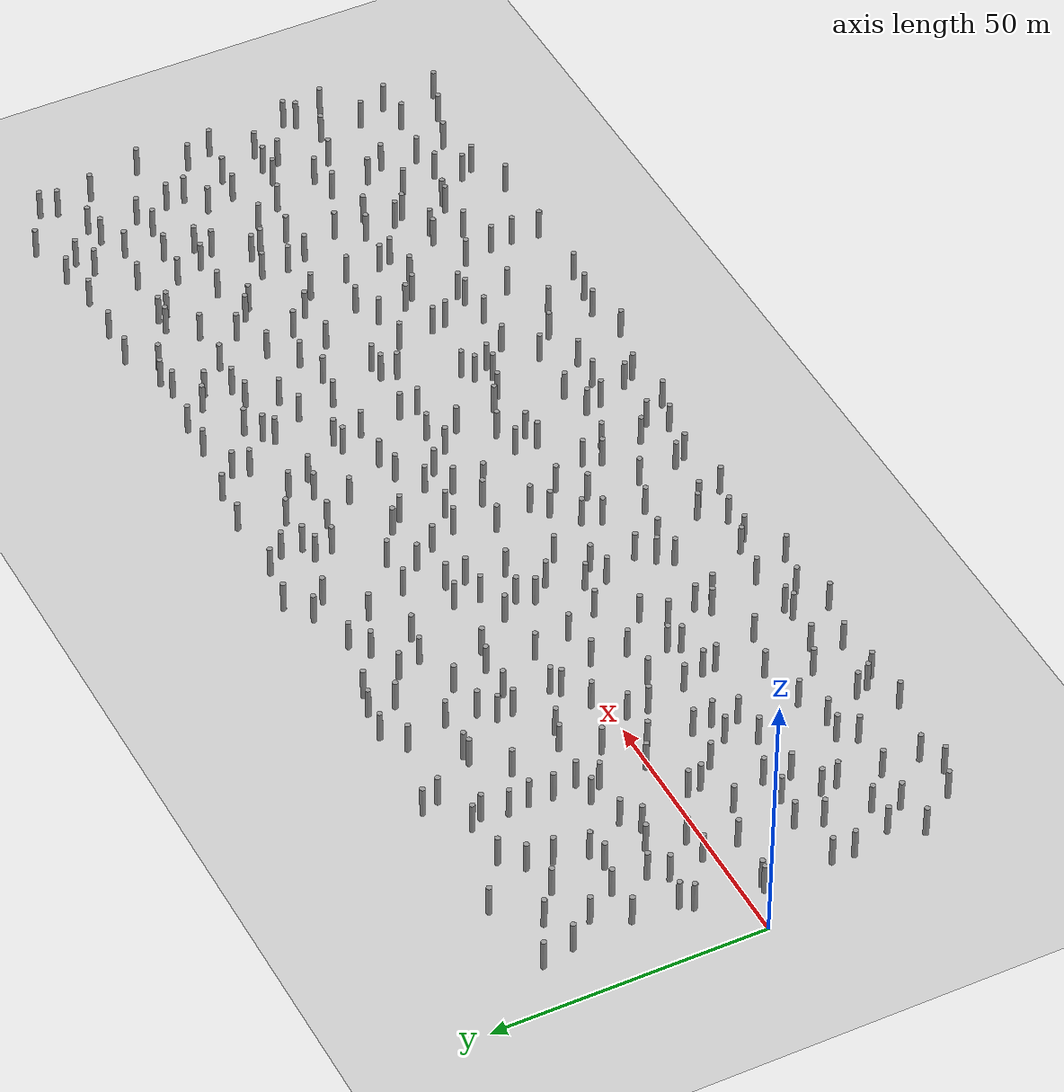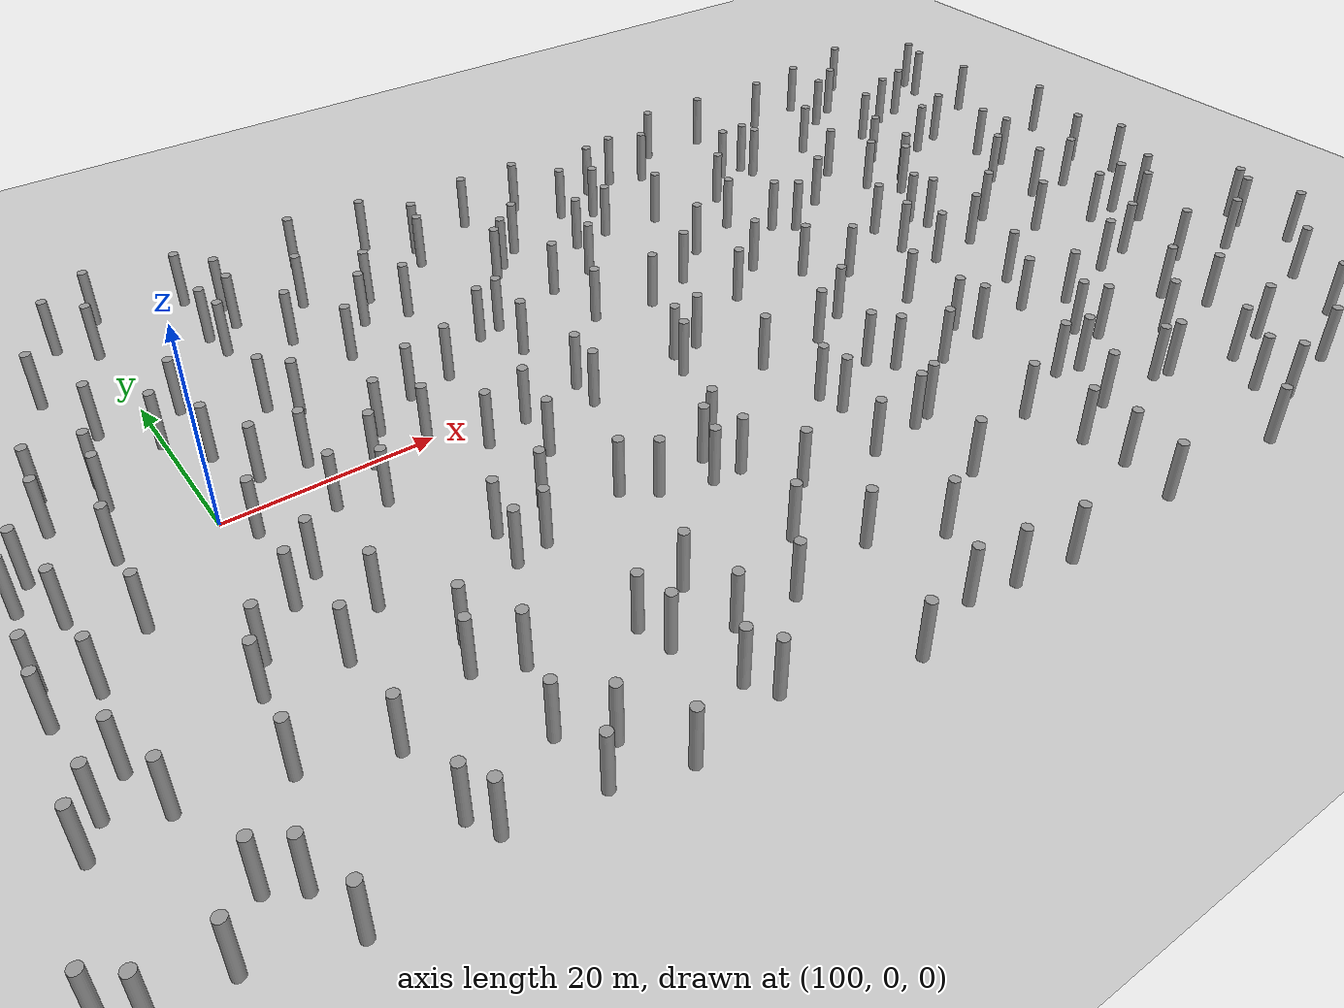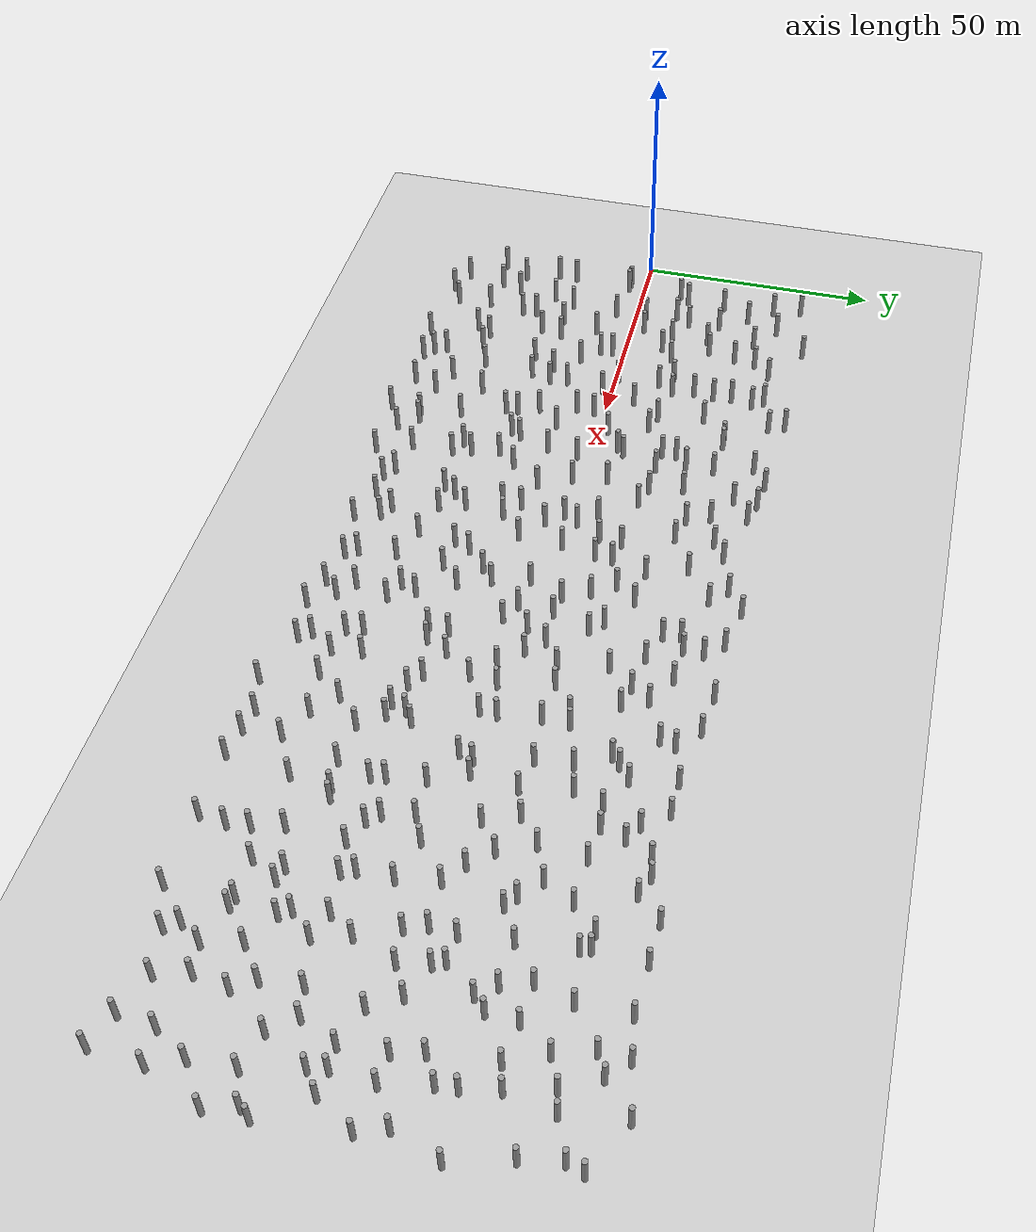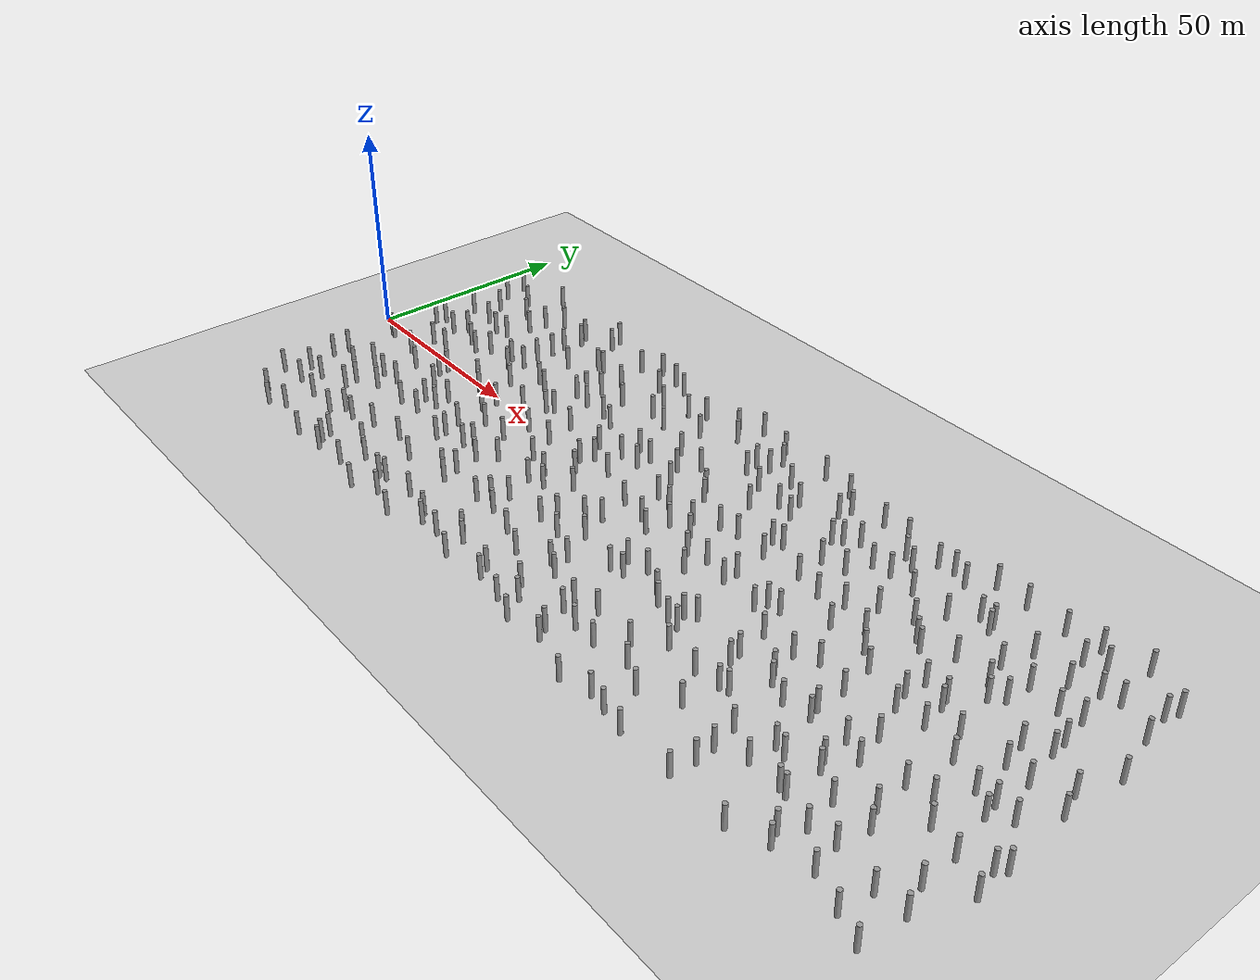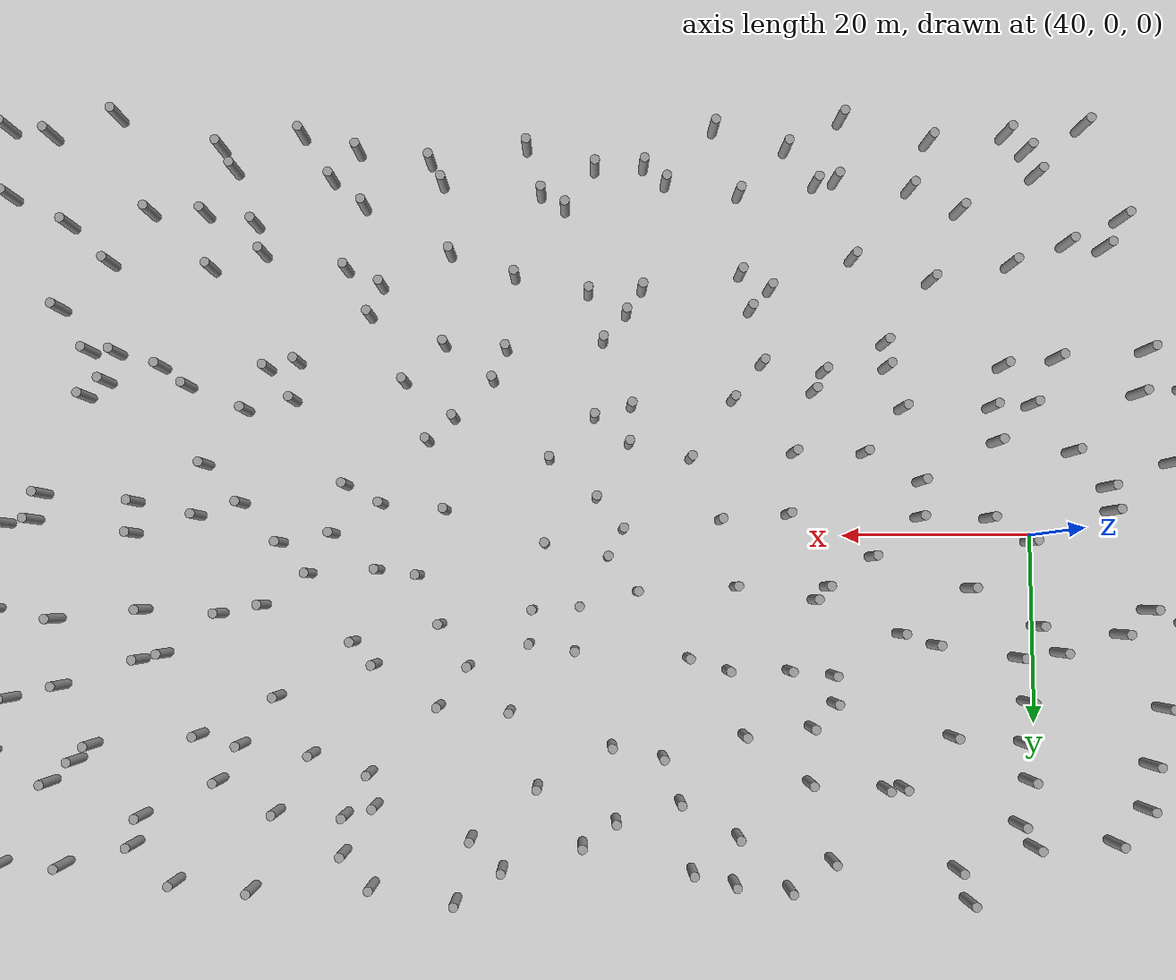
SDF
<sdf version="1.5">
 <world name="circle">
  <physics type="ode">
   <max_step_size>0.01</max_step_size>
   <real_time_factor>1</real_time_factor>
   <real_time_update_rate>0</real_time_update_rate>
  </physics>
  <light name="sun" type="directional">
   <pose>0 0 100 0 -0 0</pose>
   <diffuse>0.8 0.8 0.8 1</diffuse>
   <specular>0.2 0.2 0.2 1</specular>
   <attenuation>
    <range>1000</range>
    <constant>0.9</constant>
    <linear>0.01</linear>
    <quadratic>0.001</quadratic>
   </attenuation>
   <direction>0.5 0.1 -0.9</direction>
  </light>
  <model name="ground">
   <static>1</static>
   <link name="link">
    <collision name="collision">
     <geometry><plane><normal>0 0 1</normal><size>100 100</size></plane></geometry>
     <surface><friction><ode><mu>100</mu><mu2>50</mu2></ode></friction></surface>
    </collision>
    <visual name="visual">
     <cast_shadows>0</cast_shadows>
     <geometry><plane><normal>0 0 1</normal><size>100 100</size></plane></geometry>
     <material>
      <script><uri>file://media/materials/scripts/gazebo.material</uri><name>Gazebo/Grey</name></script>
     </material>
    </visual>
    <velocity_decay><linear>0</linear><angular>0</angular></velocity_decay>
   </link>
  </model>
  <model name="unit_cylinder_0">
   <pose>12.6124145216 -40.3023331547 3 3e-06 4e-06 -0</pose>
   <static>1</static>
   <self_collide>1</self_collide>
   <link name="link">
    <inertial>
     <mass>1</mass>
     <inertia><ixx>0.145833</ixx><ixy>0</ixy><ixz>0</ixz><iyy>0.145833</iyy><iyz>0</iyz><izz>0.125</izz></inertia>
    </inertial>
    <collision name="collision">
     <geometry><cylinder><radius>0.5</radius><length>6</length></cylinder></geometry>
    </collision>
    <visual name="visual">
     <geometry><cylinder><radius>0.5</radius><length>6</length></cylinder></geometry>
     <material>
      <script><name>Gazebo/Grey</name><uri>file://media/materials/scripts/gazebo.material</uri></script>
     </material>
    </visual>
    <collision name="cyl_collision">
     <geometry><cylinder><radius>0.5</radius><length>6</length></cylinder></geometry>
    </collision>
    <sensor name="my_contact" type="contact">
     <contact><collision>cyl_collision</collision></contact>
     <update_rate>5</update_rate>
    </sensor>
   </link>
  </model>
  <model name="unit_cylinder_1">
   <pose>6.96128146057 -32.9465415072 3 3e-06 4e-06 -0</pose>
   <static>1</static>
   <self_collide>1</self_collide>
   <link name="link">
    <inertial>
     <mass>1</mass>
     <inertia><ixx>0.145833</ixx><ixy>0</ixy><ixz>0</ixz><iyy>0.145833</iyy><iyz>0</iyz><izz>0.125</izz></inertia>
    </inertial>
    <collision name="collision">
     <geometry><cylinder><radius>0.5</radius><length>6</length></cylinder></geometry>
    </collision>
    <visual name="visual">
     <geometry><cylinder><radius>0.5</radius><length>6</length></cylinder></geometry>
     <material>
      <script><name>Gazebo/Grey</name><uri>file://media/materials/scripts/gazebo.material</uri></script>
     </material>
    </visual>
    <collision name="cyl_collision">
     <geometry><cylinder><radius>0.5</radius><length>6</length></cylinder></geometry>
    </collision>
    <sensor name="my_contact" type="contact">
     <contact><collision>cyl_collision</collision></contact>
     <update_rate>5</update_rate>
    </sensor>
   </link>
  </model>
  <model name="unit_cylinder_2">
   <pose>10.0673096309 -27.51107133 3 3e-06 4e-06 -0</pose>
   <static>1</static>
   <self_collide>1</self_collide>
   <link name="link">
    <inertial>
     <mass>1</mass>
     <inertia><ixx>0.145833</ixx><ixy>0</ixy><ixz>0</ixz><iyy>0.145833</iyy><iyz>0</iyz><izz>0.125</izz></inertia>
    </inertial>
    <collision name="collision">
     <geometry><cylinder><radius>0.5</radius><length>6</length></cylinder></geometry>
    </collision>
    <visual name="visual">
     <geometry><cylinder><radius>0.5</radius><length>6</length></cylinder></geometry>
     <material>
      <script><name>Gazebo/Grey</name><uri>file://media/materials/scripts/gazebo.material</uri></script>
     </material>
    </visual>
    <collision name="cyl_collision">
     <geometry><cylinder><radius>0.5</radius><length>6</length></cylinder></geometry>
    </collision>
    <sensor name="my_contact" type="contact">
     <contact><collision>cyl_collision</collision></contact>
     <update_rate>5</update_rate>
    </sensor>
   </link>
  </model>
  <model name="unit_cylinder_3">
   <pose>7.85500372777 -20.1338937602 3 3e-06 4e-06 -0</pose>
   <static>1</static>
   <self_collide>1</self_collide>
   <link name="link">
    <inertial>
     <mass>1</mass>
     <inertia><ixx>0.145833</ixx><ixy>0</ixy><ixz>0</ixz><iyy>0.145833</iyy><iyz>0</iyz><izz>0.125</izz></inertia>
    </inertial>
    <collision name="collision">
     <geometry><cylinder><radius>0.5</radius><length>6</length></cylinder></geometry>
    </collision>
    <visual name="visual">
     <geometry><cylinder><radius>0.5</radius><length>6</length></cylinder></geometry>
     <material>
      <script><name>Gazebo/Grey</name><uri>file://media/materials/scripts/gazebo.material</uri></script>
     </material>
    </visual>
    <collision name="cyl_collision">
     <geometry><cylinder><radius>0.5</radius><length>6</length></cylinder></geometry>
    </collision>
    <sensor name="my_contact" type="contact">
     <contact><collision>cyl_collision</collision></contact>
     <update_rate>5</update_rate>
    </sensor>
   </link>
  </model>
  <model name="unit_cylinder_4">
   <pose>8.0691187414 -16.0641193641 3 3e-06 4e-06 -0</pose>
   <static>1</static>
   <self_collide>1</self_collide>
   <link name="link">
    <inertial>
     <mass>1</mass>
     <inertia><ixx>0.145833</ixx><ixy>0</ixy><ixz>0</ixz><iyy>0.145833</iyy><iyz>0</iyz><izz>0.125</izz></inertia>
    </inertial>
    <collision name="collision">
     <geometry><cylinder><radius>0.5</radius><length>6</length></cylinder></geometry>
    </collision>
    <visual name="visual">
     <geometry><cylinder><radius>0.5</radius><length>6</length></cylinder></geometry>
     <material>
      <script><name>Gazebo/Grey</name><uri>file://media/materials/scripts/gazebo.material</uri></script>
     </material>
    </visual>
    <collision name="cyl_collision">
     <geometry><cylinder><radius>0.5</radius><length>6</length></cylinder></geometry>
    </collision>
    <sensor name="my_contact" type="contact">
     <contact><collision>cyl_collision</collision></contact>
     <update_rate>5</update_rate>
    </sensor>
   </link>
  </model>
  <model name="unit_cylinder_5">
   <pose>8.83416770659 -3.51580887459 3 3e-06 4e-06 -0</pose>
   <static>1</static>
   <self_collide>1</self_collide>
   <link name="link">
    <inertial>
     <mass>1</mass>
     <inertia><ixx>0.145833</ixx><ixy>0</ixy><ixz>0</ixz><iyy>0.145833</iyy><iyz>0</iyz><izz>0.125</izz></inertia>
    </inertial>
    <collision name="collision">
     <geometry><cylinder><radius>0.5</radius><length>6</length></cylinder></geometry>
    </collision>
    <visual name="visual">
     <geometry><cylinder><radius>0.5</radius><length>6</length></cylinder></geometry>
     <material>
      <script><name>Gazebo/Grey</name><uri>file://media/materials/scripts/gazebo.material</uri></script>
     </material>
    </visual>
    <collision name="cyl_collision">
     <geometry><cylinder><radius>0.5</radius><length>6</length></cylinder></geometry>
    </collision>
    <sensor name="my_contact" type="contact">
     <contact><collision>cyl_collision</collision></contact>
     <update_rate>5</update_rate>
    </sensor>
   </link>
  </model>
  <model name="unit_cylinder_6">
   <pose>7.56302543197 -3.29659652474 3 3e-06 4e-06 -0</pose>
   <static>1</static>
   <self_collide>1</self_collide>
   <link name="link">
    <inertial>
     <mass>1</mass>
     <inertia><ixx>0.145833</ixx><ixy>0</ixy><ixz>0</ixz><iyy>0.145833</iyy><iyz>0</iyz><izz>0.125</izz></inertia>
    </inertial>
    <collision name="collision">
     <geometry><cylinder><radius>0.5</radius><length>6</length></cylinder></geometry>
    </collision>
    <visual name="visual">
     <geometry><cylinder><radius>0.5</radius><length>6</length></cylinder></geometry>
     <material>
      <script><name>Gazebo/Grey</name><uri>file://media/materials/scripts/gazebo.material</uri></script>
     </material>
    </visual>
    <collision name="cyl_collision">
     <geometry><cylinder><radius>0.5</radius><length>6</length></cylinder></geometry>
    </collision>
    <sensor name="my_contact" type="contact">
     <contact><collision>cyl_collision</collision></contact>
     <update_rate>5</update_rate>
    </sensor>
   </link>
  </model>
  <model name="unit_cylinder_7">
   <pose>9.21779882233 8.63194221244 3 3e-06 4e-06 -0</pose>
   <static>1</static>
   <self_collide>1</self_collide>
   <link name="link">
    <inertial>
     <mass>1</mass>
     <inertia><ixx>0.145833</ixx><ixy>0</ixy><ixz>0</ixz><iyy>0.145833</iyy><iyz>0</iyz><izz>0.125</izz></inertia>
    </inertial>
    <collision name="collision">
     <geometry><cylinder><radius>0.5</radius><length>6</length></cylinder></geometry>
    </collision>
    <visual name="visual">
     <geometry><cylinder><radius>0.5</radius><length>6</length></cylinder></geometry>
     <material>
      <script><name>Gazebo/Grey</name><uri>file://media/materials/scripts/gazebo.material</uri></script>
     </material>
    </visual>
    <collision name="cyl_collision">
     <geometry><cylinder><radius>0.5</radius><length>6</length></cylinder></geometry>
    </collision>
    <sensor name="my_contact" type="contact">
     <contact><collision>cyl_collision</collision></contact>
     <update_rate>5</update_rate>
    </sensor>
   </link>
  </model>
  <model name="unit_cylinder_8">
   <pose>10.6660314604 10.6326092408 3 3e-06 4e-06 -0</pose>
   <static>1</static>
   <self_collide>1</self_collide>
   <link name="link">
    <inertial>
     <mass>1</mass>
     <inertia><ixx>0.145833</ixx><ixy>0</ixy><ixz>0</ixz><iyy>0.145833</iyy><iyz>0</iyz><izz>0.125</izz></inertia>
    </inertial>
    <collision name="collision">
     <geometry><cylinder><radius>0.5</radius><length>6</length></cylinder></geometry>
    </collision>
    <visual name="visual">
     <geometry><cylinder><radius>0.5</radius><length>6</length></cylinder></geometry>
     <material>
      <script><name>Gazebo/Grey</name><uri>file://media/materials/scripts/gazebo.material</uri></script>
     </material>
    </visual>
    <collision name="cyl_collision">
     <geometry><cylinder><radius>0.5</radius><length>6</length></cylinder></geometry>
    </collision>
    <sensor name="my_contact" type="contact">
     <contact><collision>cyl_collision</collision></contact>
     <update_rate>5</update_rate>
    </sensor>
   </link>
  </model>
  <model name="unit_cylinder_9">
   <pose>11.123073649 18.9455228863 3 3e-06 4e-06 -0</pose>
   <static>1</static>
   <self_collide>1</self_collide>
   <link name="link">
    <inertial>
     <mass>1</mass>
     <inertia><ixx>0.145833</ixx><ixy>0</ixy><ixz>0</ixz><iyy>0.145833</iyy><iyz>0</iyz><izz>0.125</izz></inertia>
    </inertial>
    <collision name="collision">
     <geometry><cylinder><radius>0.5</radius><length>6</length></cylinder></geometry>
    </collision>
    <visual name="visual">
     <geometry><cylinder><radius>0.5</radius><length>6</length></cylinder></geometry>
     <material>
      <script><name>Gazebo/Grey</name><uri>file://media/materials/scripts/gazebo.material</uri></script>
     </material>
    </visual>
    <collision name="cyl_collision">
     <geometry><cylinder><radius>0.5</radius><length>6</length></cylinder></geometry>
    </collision>
    <sensor name="my_contact" type="contact">
     <contact><collision>cyl_collision</collision></contact>
     <update_rate>5</update_rate>
    </sensor>
   </link>
  </model>
  <model name="unit_cylinder_10">
   <pose>10.1845275033 30.1063696156 3 3e-06 4e-06 -0</pose>
   <static>1</static>
   <self_collide>1</self_collide>
   <link name="link">
    <inertial>
     <mass>1</mass>
     <inertia><ixx>0.145833</ixx><ixy>0</ixy><ixz>0</ixz><iyy>0.145833</iyy><iyz>0</iyz><izz>0.125</izz></inertia>
    </inertial>
    <collision name="collision">
     <geometry><cylinder><radius>0.5</radius><length>6</length></cylinder></geometry>
    </collision>
    <visual name="visual">
     <geometry><cylinder><radius>0.5</radius><length>6</length></cylinder></geometry>
     <material>
      <script><name>Gazebo/Grey</name><uri>file://media/materials/scripts/gazebo.material</uri></script>
     </material>
    </visual>
    <collision name="cyl_collision">
     <geometry><cylinder><radius>0.5</radius><length>6</length></cylinder></geometry>
    </collision>
    <sensor name="my_contact" type="contact">
     <contact><collision>cyl_collision</collision></contact>
     <update_rate>5</update_rate>
    </sensor>
   </link>
  </model>
  <model name="unit_cylinder_11">
   <pose>8.87667534142 36.0706108962 3 3e-06 4e-06 -0</pose>
   <static>1</static>
   <self_collide>1</self_collide>
   <link name="link">
    <inertial>
     <mass>1</mass>
     <inertia><ixx>0.145833</ixx><ixy>0</ixy><ixz>0</ixz><iyy>0.145833</iyy><iyz>0</iyz><izz>0.125</izz></inertia>
    </inertial>
    <collision name="collision">
     <geometry><cylinder><radius>0.5</radius><length>6</length></cylinder></geometry>
    </collision>
    <visual name="visual">
     <geometry><cylinder><radius>0.5</radius><length>6</length></cylinder></geometry>
     <material>
      <script><name>Gazebo/Grey</name><uri>file://media/materials/scripts/gazebo.material</uri></script>
     </material>
    </visual>
    <collision name="cyl_collision">
     <geometry><cylinder><radius>0.5</radius><length>6</length></cylinder></geometry>
    </collision>
    <sensor name="my_contact" type="contact">
     <contact><collision>cyl_collision</collision></contact>
     <update_rate>5</update_rate>
    </sensor>
   </link>
  </model>
  <model name="unit_cylinder_12">
   <pose>17.7732628708 -42.5833735378 3 3e-06 4e-06 -0</pose>
   <static>1</static>
   <self_collide>1</self_collide>
   <link name="link">
    <inertial>
     <mass>1</mass>
     <inertia><ixx>0.145833</ixx><ixy>0</ixy><ixz>0</ixz><iyy>0.145833</iyy><iyz>0</iyz><izz>0.125</izz></inertia>
    </inertial>
    <collision name="collision">
     <geometry><cylinder><radius>0.5</radius><length>6</length></cylinder></geometry>
    </collision>
    <visual name="visual">
     <geometry><cylinder><radius>0.5</radius><length>6</length></cylinder></geometry>
     <material>
      <script><name>Gazebo/Grey</name><uri>file://media/materials/scripts/gazebo.material</uri></script>
     </material>
    </visual>
    <collision name="cyl_collision">
     <geometry><cylinder><radius>0.5</radius><length>6</length></cylinder></geometry>
    </collision>
    <sensor name="my_contact" type="contact">
     <contact><collision>cyl_collision</collision></contact>
     <update_rate>5</update_rate>
    </sensor>
   </link>
  </model>
  <model name="unit_cylinder_13">
   <pose>13.8132217243 -32.102792748 3 3e-06 4e-06 -0</pose>
   <static>1</static>
   <self_collide>1</self_collide>
   <link name="link">
    <inertial>
     <mass>1</mass>
     <inertia><ixx>0.145833</ixx><ixy>0</ixy><ixz>0</ixz><iyy>0.145833</iyy><iyz>0</iyz><izz>0.125</izz></inertia>
    </inertial>
    <collision name="collision">
     <geometry><cylinder><radius>0.5</radius><length>6</length></cylinder></geometry>
    </collision>
    <visual name="visual">
     <geometry><cylinder><radius>0.5</radius><length>6</length></cylinder></geometry>
     <material>
      <script><name>Gazebo/Grey</name><uri>file://media/materials/scripts/gazebo.material</uri></script>
     </material>
    </visual>
    <collision name="cyl_collision">
     <geometry><cylinder><radius>0.5</radius><length>6</length></cylinder></geometry>
    </collision>
    <sensor name="my_contact" type="contact">
     <contact><collision>cyl_collision</collision></contact>
     <update_rate>5</update_rate>
    </sensor>
   </link>
  </model>
  <model name="unit_cylinder_14">
   <pose>15.4106913323 -27.5746957721 3 3e-06 4e-06 -0</pose>
   <static>1</static>
   <self_collide>1</self_collide>
   <link name="link">
    <inertial>
     <mass>1</mass>
     <inertia><ixx>0.145833</ixx><ixy>0</ixy><ixz>0</ixz><iyy>0.145833</iyy><iyz>0</iyz><izz>0.125</izz></inertia>
    </inertial>
    <collision name="collision">
     <geometry><cylinder><radius>0.5</radius><length>6</length></cylinder></geometry>
    </collision>
    <visual name="visual">
     <geometry><cylinder><radius>0.5</radius><length>6</length></cylinder></geometry>
     <material>
      <script><name>Gazebo/Grey</name><uri>file://media/materials/scripts/gazebo.material</uri></script>
     </material>
    </visual>
    <collision name="cyl_collision">
     <geometry><cylinder><radius>0.5</radius><length>6</length></cylinder></geometry>
    </collision>
    <sensor name="my_contact" type="contact">
     <contact><collision>cyl_collision</collision></contact>
     <update_rate>5</update_rate>
    </sensor>
   </link>
  </model>
  <model name="unit_cylinder_15">
   <pose>16.1578896865 -19.113521778 3 3e-06 4e-06 -0</pose>
   <static>1</static>
   <self_collide>1</self_collide>
   <link name="link">
    <inertial>
     <mass>1</mass>
     <inertia><ixx>0.145833</ixx><ixy>0</ixy><ixz>0</ixz><iyy>0.145833</iyy><iyz>0</iyz><izz>0.125</izz></inertia>
    </inertial>
    <collision name="collision">
     <geometry><cylinder><radius>0.5</radius><length>6</length></cylinder></geometry>
    </collision>
    <visual name="visual">
     <geometry><cylinder><radius>0.5</radius><length>6</length></cylinder></geometry>
     <material>
      <script><name>Gazebo/Grey</name><uri>file://media/materials/scripts/gazebo.material</uri></script>
     </material>
    </visual>
    <collision name="cyl_collision">
     <geometry><cylinder><radius>0.5</radius><length>6</length></cylinder></geometry>
    </collision>
    <sensor name="my_contact" type="contact">
     <contact><collision>cyl_collision</collision></contact>
     <update_rate>5</update_rate>
    </sensor>
   </link>
  </model>
  <model name="unit_cylinder_16">
   <pose>17.9182829641 -14.5445670204 3 3e-06 4e-06 -0</pose>
   <static>1</static>
   <self_collide>1</self_collide>
   <link name="link">
    <inertial>
     <mass>1</mass>
     <inertia><ixx>0.145833</ixx><ixy>0</ixy><ixz>0</ixz><iyy>0.145833</iyy><iyz>0</iyz><izz>0.125</izz></inertia>
    </inertial>
    <collision name="collision">
     <geometry><cylinder><radius>0.5</radius><length>6</length></cylinder></geometry>
    </collision>
    <visual name="visual">
     <geometry><cylinder><radius>0.5</radius><length>6</length></cylinder></geometry>
     <material>
      <script><name>Gazebo/Grey</name><uri>file://media/materials/scripts/gazebo.material</uri></script>
     </material>
    </visual>
    <collision name="cyl_collision">
     <geometry><cylinder><radius>0.5</radius><length>6</length></cylinder></geometry>
    </collision>
    <sensor name="my_contact" type="contact">
     <contact><collision>cyl_collision</collision></contact>
     <update_rate>5</update_rate>
    </sensor>
   </link>
  </model>
  <model name="unit_cylinder_17">
   <pose>18.4843208202 -4.38847078077 3 3e-06 4e-06 -0</pose>
   <static>1</static>
   <self_collide>1</self_collide>
   <link name="link">
    <inertial>
     <mass>1</mass>
     <inertia><ixx>0.145833</ixx><ixy>0</ixy><ixz>0</ixz><iyy>0.145833</iyy><iyz>0</iyz><izz>0.125</izz></inertia>
    </inertial>
    <collision name="collision">
     <geometry><cylinder><radius>0.5</radius><length>6</length></cylinder></geometry>
    </collision>
    <visual name="visual">
     <geometry><cylinder><radius>0.5</radius><length>6</length></cylinder></geometry>
     <material>
      <script><name>Gazebo/Grey</name><uri>file://media/materials/scripts/gazebo.material</uri></script>
     </material>
    </visual>
    <collision name="cyl_collision">
     <geometry><cylinder><radius>0.5</radius><length>6</length></cylinder></geometry>
    </collision>
    <sensor name="my_contact" type="contact">
     <contact><collision>cyl_collision</collision></contact>
     <update_rate>5</update_rate>
    </sensor>
   </link>
  </model>
  <model name="unit_cylinder_18">
   <pose>18.1074337811 2.3008003105 3 3e-06 4e-06 -0</pose>
   <static>1</static>
   <self_collide>1</self_collide>
   <link name="link">
    <inertial>
     <mass>1</mass>
     <inertia><ixx>0.145833</ixx><ixy>0</ixy><ixz>0</ixz><iyy>0.145833</iyy><iyz>0</iyz><izz>0.125</izz></inertia>
    </inertial>
    <collision name="collision">
     <geometry><cylinder><radius>0.5</radius><length>6</length></cylinder></geometry>
    </collision>
    <visual name="visual">
     <geometry><cylinder><radius>0.5</radius><length>6</length></cylinder></geometry>
     <material>
      <script><name>Gazebo/Grey</name><uri>file://media/materials/scripts/gazebo.material</uri></script>
     </material>
    </visual>
    <collision name="cyl_collision">
     <geometry><cylinder><radius>0.5</radius><length>6</length></cylinder></geometry>
    </collision>
    <sensor name="my_contact" type="contact">
     <contact><collision>cyl_collision</collision></contact>
     <update_rate>5</update_rate>
    </sensor>
   </link>
  </model>
  <model name="unit_cylinder_19">
   <pose>16.6175031208 9.12599399941 3 3e-06 4e-06 -0</pose>
   <static>1</static>
   <self_collide>1</self_collide>
   <link name="link">
    <inertial>
     <mass>1</mass>
     <inertia><ixx>0.145833</ixx><ixy>0</ixy><ixz>0</ixz><iyy>0.145833</iyy><iyz>0</iyz><izz>0.125</izz></inertia>
    </inertial>
    <collision name="collision">
     <geometry><cylinder><radius>0.5</radius><length>6</length></cylinder></geometry>
    </collision>
    <visual name="visual">
     <geometry><cylinder><radius>0.5</radius><length>6</length></cylinder></geometry>
     <material>
      <script><name>Gazebo/Grey</name><uri>file://media/materials/scripts/gazebo.material</uri></script>
     </material>
    </visual>
    <collision name="cyl_collision">
     <geometry><cylinder><radius>0.5</radius><length>6</length></cylinder></geometry>
    </collision>
    <sensor name="my_contact" type="contact">
     <contact><collision>cyl_collision</collision></contact>
     <update_rate>5</update_rate>
    </sensor>
   </link>
  </model>
  <model name="unit_cylinder_20">
   <pose>18.6151554235 12.2272240417 3 3e-06 4e-06 -0</pose>
   <static>1</static>
   <self_collide>1</self_collide>
   <link name="link">
    <inertial>
     <mass>1</mass>
     <inertia><ixx>0.145833</ixx><ixy>0</ixy><ixz>0</ixz><iyy>0.145833</iyy><iyz>0</iyz><izz>0.125</izz></inertia>
    </inertial>
    <collision name="collision">
     <geometry><cylinder><radius>0.5</radius><length>6</length></cylinder></geometry>
    </collision>
    <visual name="visual">
     <geometry><cylinder><radius>0.5</radius><length>6</length></cylinder></geometry>
     <material>
      <script><name>Gazebo/Grey</name><uri>file://media/materials/scripts/gazebo.material</uri></script>
     </material>
    </visual>
    <collision name="cyl_collision">
     <geometry><cylinder><radius>0.5</radius><length>6</length></cylinder></geometry>
    </collision>
    <sensor name="my_contact" type="contact">
     <contact><collision>cyl_collision</collision></contact>
     <update_rate>5</update_rate>
    </sensor>
   </link>
  </model>
  <model name="unit_cylinder_21">
   <pose>18.012515353 19.0028447538 3 3e-06 4e-06 -0</pose>
   <static>1</static>
   <self_collide>1</self_collide>
   <link name="link">
    <inertial>
     <mass>1</mass>
     <inertia><ixx>0.145833</ixx><ixy>0</ixy><ixz>0</ixz><iyy>0.145833</iyy><iyz>0</iyz><izz>0.125</izz></inertia>
    </inertial>
    <collision name="collision">
     <geometry><cylinder><radius>0.5</radius><length>6</length></cylinder></geometry>
    </collision>
    <visual name="visual">
     <geometry><cylinder><radius>0.5</radius><length>6</length></cylinder></geometry>
     <material>
      <script><name>Gazebo/Grey</name><uri>file://media/materials/scripts/gazebo.material</uri></script>
     </material>
    </visual>
    <collision name="cyl_collision">
     <geometry><cylinder><radius>0.5</radius><length>6</length></cylinder></geometry>
    </collision>
    <sensor name="my_contact" type="contact">
     <contact><collision>cyl_collision</collision></contact>
     <update_rate>5</update_rate>
    </sensor>
   </link>
  </model>
  <model name="unit_cylinder_22">
   <pose>14.2315893877 24.9502558088 3 3e-06 4e-06 -0</pose>
   <static>1</static>
   <self_collide>1</self_collide>
   <link name="link">
    <inertial>
     <mass>1</mass>
     <inertia><ixx>0.145833</ixx><ixy>0</ixy><ixz>0</ixz><iyy>0.145833</iyy><iyz>0</iyz><izz>0.125</izz></inertia>
    </inertial>
    <collision name="collision">
     <geometry><cylinder><radius>0.5</radius><length>6</length></cylinder></geometry>
    </collision>
    <visual name="visual">
     <geometry><cylinder><radius>0.5</radius><length>6</length></cylinder></geometry>
     <material>
      <script><name>Gazebo/Grey</name><uri>file://media/materials/scripts/gazebo.material</uri></script>
     </material>
    </visual>
    <collision name="cyl_collision">
     <geometry><cylinder><radius>0.5</radius><length>6</length></cylinder></geometry>
    </collision>
    <sensor name="my_contact" type="contact">
     <contact><collision>cyl_collision</collision></contact>
     <update_rate>5</update_rate>
    </sensor>
   </link>
  </model>
  <model name="unit_cylinder_23">
   <pose>16.9766547562 31.8201238573 3 3e-06 4e-06 -0</pose>
   <static>1</static>
   <self_collide>1</self_collide>
   <link name="link">
    <inertial>
     <mass>1</mass>
     <inertia><ixx>0.145833</ixx><ixy>0</ixy><ixz>0</ixz><iyy>0.145833</iyy><iyz>0</iyz><izz>0.125</izz></inertia>
    </inertial>
    <collision name="collision">
     <geometry><cylinder><radius>0.5</radius><length>6</length></cylinder></geometry>
    </collision>
    <visual name="visual">
     <geometry><cylinder><radius>0.5</radius><length>6</length></cylinder></geometry>
     <material>
      <script><name>Gazebo/Grey</name><uri>file://media/materials/scripts/gazebo.material</uri></script>
     </material>
    </visual>
    <collision name="cyl_collision">
     <geometry><cylinder><radius>0.5</radius><length>6</length></cylinder></geometry>
    </collision>
    <sensor name="my_contact" type="contact">
     <contact><collision>cyl_collision</collision></contact>
     <update_rate>5</update_rate>
    </sensor>
   </link>
  </model>
  <model name="unit_cylinder_24">
   <pose>21.9065971351 -40.3572031227 3 3e-06 4e-06 -0</pose>
   <static>1</static>
   <self_collide>1</self_collide>
   <link name="link">
    <inertial>
     <mass>1</mass>
     <inertia><ixx>0.145833</ixx><ixy>0</ixy><ixz>0</ixz><iyy>0.145833</iyy><iyz>0</iyz><izz>0.125</izz></inertia>
    </inertial>
    <collision name="collision">
     <geometry><cylinder><radius>0.5</radius><length>6</length></cylinder></geometry>
    </collision>
    <visual name="visual">
     <geometry><cylinder><radius>0.5</radius><length>6</length></cylinder></geometry>
     <material>
      <script><name>Gazebo/Grey</name><uri>file://media/materials/scripts/gazebo.material</uri></script>
     </material>
    </visual>
    <collision name="cyl_collision">
     <geometry><cylinder><radius>0.5</radius><length>6</length></cylinder></geometry>
    </collision>
    <sensor name="my_contact" type="contact">
     <contact><collision>cyl_collision</collision></contact>
     <update_rate>5</update_rate>
    </sensor>
   </link>
  </model>
  <model name="unit_cylinder_25">
   <pose>21.5926735893 -33.0451283074 3 3e-06 4e-06 -0</pose>
   <static>1</static>
   <self_collide>1</self_collide>
   <link name="link">
    <inertial>
     <mass>1</mass>
     <inertia><ixx>0.145833</ixx><ixy>0</ixy><ixz>0</ixz><iyy>0.145833</iyy><iyz>0</iyz><izz>0.125</izz></inertia>
    </inertial>
    <collision name="collision">
     <geometry><cylinder><radius>0.5</radius><length>6</length></cylinder></geometry>
    </collision>
    <visual name="visual">
     <geometry><cylinder><radius>0.5</radius><length>6</length></cylinder></geometry>
     <material>
      <script><name>Gazebo/Grey</name><uri>file://media/materials/scripts/gazebo.material</uri></script>
     </material>
    </visual>
    <collision name="cyl_collision">
     <geometry><cylinder><radius>0.5</radius><length>6</length></cylinder></geometry>
    </collision>
    <sensor name="my_contact" type="contact">
     <contact><collision>cyl_collision</collision></contact>
     <update_rate>5</update_rate>
    </sensor>
   </link>
  </model>
  <model name="unit_cylinder_26">
   <pose>22.7206121784 -25.1614234946 3 3e-06 4e-06 -0</pose>
   <static>1</static>
   <self_collide>1</self_collide>
   <link name="link">
    <inertial>
     <mass>1</mass>
     <inertia><ixx>0.145833</ixx><ixy>0</ixy><ixz>0</ixz><iyy>0.145833</iyy><iyz>0</iyz><izz>0.125</izz></inertia>
    </inertial>
    <collision name="collision">
     <geometry><cylinder><radius>0.5</radius><length>6</length></cylinder></geometry>
    </collision>
    <visual name="visual">
     <geometry><cylinder><radius>0.5</radius><length>6</length></cylinder></geometry>
     <material>
      <script><name>Gazebo/Grey</name><uri>file://media/materials/scripts/gazebo.material</uri></script>
     </material>
    </visual>
    <collision name="cyl_collision">
     <geometry><cylinder><radius>0.5</radius><length>6</length></cylinder></geometry>
    </collision>
    <sensor name="my_contact" type="contact">
     <contact><collision>cyl_collision</collision></contact>
     <update_rate>5</update_rate>
    </sensor>
   </link>
  </model>
  <model name="unit_cylinder_27">
   <pose>22.4219778398 -22.0793265807 3 3e-06 4e-06 -0</pose>
   <static>1</static>
   <self_collide>1</self_collide>
   <link name="link">
    <inertial>
     <mass>1</mass>
     <inertia><ixx>0.145833</ixx><ixy>0</ixy><ixz>0</ixz><iyy>0.145833</iyy><iyz>0</iyz><izz>0.125</izz></inertia>
    </inertial>
    <collision name="collision">
     <geometry><cylinder><radius>0.5</radius><length>6</length></cylinder></geometry>
    </collision>
    <visual name="visual">
     <geometry><cylinder><radius>0.5</radius><length>6</length></cylinder></geometry>
     <material>
      <script><name>Gazebo/Grey</name><uri>file://media/materials/scripts/gazebo.material</uri></script>
     </material>
    </visual>
    <collision name="cyl_collision">
     <geometry><cylinder><radius>0.5</radius><length>6</length></cylinder></geometry>
    </collision>
    <sensor name="my_contact" type="contact">
     <contact><collision>cyl_collision</collision></contact>
     <update_rate>5</update_rate>
    </sensor>
   </link>
  </model>
  <model name="unit_cylinder_28">
   <pose>23.8886145601 -15.3643983245 3 3e-06 4e-06 -0</pose>
   <static>1</static>
   <self_collide>1</self_collide>
   <link name="link">
    <inertial>
     <mass>1</mass>
     <inertia><ixx>0.145833</ixx><ixy>0</ixy><ixz>0</ixz><iyy>0.145833</iyy><iyz>0</iyz><izz>0.125</izz></inertia>
    </inertial>
    <collision name="collision">
     <geometry><cylinder><radius>0.5</radius><length>6</length></cylinder></geometry>
    </collision>
    <visual name="visual">
     <geometry><cylinder><radius>0.5</radius><length>6</length></cylinder></geometry>
     <material>
      <script><name>Gazebo/Grey</name><uri>file://media/materials/scripts/gazebo.material</uri></script>
     </material>
    </visual>
    <collision name="cyl_collision">
     <geometry><cylinder><radius>0.5</radius><length>6</length></cylinder></geometry>
    </collision>
    <sensor name="my_contact" type="contact">
     <contact><collision>cyl_collision</collision></contact>
     <update_rate>5</update_rate>
    </sensor>
   </link>
  </model>
  <model name="unit_cylinder_29">
   <pose>25.5359010917 -7.43061325953 3 3e-06 4e-06 -0</pose>
   <static>1</static>
   <self_collide>1</self_collide>
   <link name="link">
    <inertial>
     <mass>1</mass>
     <inertia><ixx>0.145833</ixx><ixy>0</ixy><ixz>0</ixz><iyy>0.145833</iyy><iyz>0</iyz><izz>0.125</izz></inertia>
    </inertial>
    <collision name="collision">
     <geometry><cylinder><radius>0.5</radius><length>6</length></cylinder></geometry>
    </collision>
    <visual name="visual">
     <geometry><cylinder><radius>0.5</radius><length>6</length></cylinder></geometry>
     <material>
      <script><name>Gazebo/Grey</name><uri>file://media/materials/scripts/gazebo.material</uri></script>
     </material>
    </visual>
    <collision name="cyl_collision">
     <geometry><cylinder><radius>0.5</radius><length>6</length></cylinder></geometry>
    </collision>
    <sensor name="my_contact" type="contact">
     <contact><collision>cyl_collision</collision></contact>
     <update_rate>5</update_rate>
    </sensor>
   </link>
  </model>
  <model name="unit_cylinder_30">
   <pose>22.7048124777 2.83400844069 3 3e-06 4e-06 -0</pose>
   <static>1</static>
   <self_collide>1</self_collide>
   <link name="link">
    <inertial>
     <mass>1</mass>
     <inertia><ixx>0.145833</ixx><ixy>0</ixy><ixz>0</ixz><iyy>0.145833</iyy><iyz>0</iyz><izz>0.125</izz></inertia>
    </inertial>
    <collision name="collision">
     <geometry><cylinder><radius>0.5</radius><length>6</length></cylinder></geometry>
    </collision>
    <visual name="visual">
     <geometry><cylinder><radius>0.5</radius><length>6</length></cylinder></geometry>
     <material>
      <script><name>Gazebo/Grey</name><uri>file://media/materials/scripts/gazebo.material</uri></script>
     </material>
    </visual>
    <collision name="cyl_collision">
     <geometry><cylinder><radius>0.5</radius><length>6</length></cylinder></geometry>
    </collision>
    <sensor name="my_contact" type="contact">
     <contact><collision>cyl_collision</collision></contact>
     <update_rate>5</update_rate>
    </sensor>
   </link>
  </model>
  <model name="unit_cylinder_31">
   <pose>24.3456402127 9.49454115345 3 3e-06 4e-06 -0</pose>
   <static>1</static>
   <self_collide>1</self_collide>
   <link name="link">
    <inertial>
     <mass>1</mass>
     <inertia><ixx>0.145833</ixx><ixy>0</ixy><ixz>0</ixz><iyy>0.145833</iyy><iyz>0</iyz><izz>0.125</izz></inertia>
    </inertial>
    <collision name="collision">
     <geometry><cylinder><radius>0.5</radius><length>6</length></cylinder></geometry>
    </collision>
    <visual name="visual">
     <geometry><cylinder><radius>0.5</radius><length>6</length></cylinder></geometry>
     <material>
      <script><name>Gazebo/Grey</name><uri>file://media/materials/scripts/gazebo.material</uri></script>
     </material>
    </visual>
    <collision name="cyl_collision">
     <geometry><cylinder><radius>0.5</radius><length>6</length></cylinder></geometry>
    </collision>
    <sensor name="my_contact" type="contact">
     <contact><collision>cyl_collision</collision></contact>
     <update_rate>5</update_rate>
    </sensor>
   </link>
  </model>
  <model name="unit_cylinder_32">
   <pose>23.6487459374 17.3425965004 3 3e-06 4e-06 -0</pose>
   <static>1</static>
   <self_collide>1</self_collide>
   <link name="link">
    <inertial>
     <mass>1</mass>
     <inertia><ixx>0.145833</ixx><ixy>0</ixy><ixz>0</ixz><iyy>0.145833</iyy><iyz>0</iyz><izz>0.125</izz></inertia>
    </inertial>
    <collision name="collision">
     <geometry><cylinder><radius>0.5</radius><length>6</length></cylinder></geometry>
    </collision>
    <visual name="visual">
     <geometry><cylinder><radius>0.5</radius><length>6</length></cylinder></geometry>
     <material>
      <script><name>Gazebo/Grey</name><uri>file://media/materials/scripts/gazebo.material</uri></script>
     </material>
    </visual>
    <collision name="cyl_collision">
     <geometry><cylinder><radius>0.5</radius><length>6</length></cylinder></geometry>
    </collision>
    <sensor name="my_contact" type="contact">
     <contact><collision>cyl_collision</collision></contact>
     <update_rate>5</update_rate>
    </sensor>
   </link>
  </model>
  <model name="unit_cylinder_33">
   <pose>26.982643623 18.3394458128 3 3e-06 4e-06 -0</pose>
   <static>1</static>
   <self_collide>1</self_collide>
   <link name="link">
    <inertial>
     <mass>1</mass>
     <inertia><ixx>0.145833</ixx><ixy>0</ixy><ixz>0</ixz><iyy>0.145833</iyy><iyz>0</iyz><izz>0.125</izz></inertia>
    </inertial>
    <collision name="collision">
     <geometry><cylinder><radius>0.5</radius><length>6</length></cylinder></geometry>
    </collision>
    <visual name="visual">
     <geometry><cylinder><radius>0.5</radius><length>6</length></cylinder></geometry>
     <material>
      <script><name>Gazebo/Grey</name><uri>file://media/materials/scripts/gazebo.material</uri></script>
     </material>
    </visual>
    <collision name="cyl_collision">
     <geometry><cylinder><radius>0.5</radius><length>6</length></cylinder></geometry>
    </collision>
    <sensor name="my_contact" type="contact">
     <contact><collision>cyl_collision</collision></contact>
     <update_rate>5</update_rate>
    </sensor>
   </link>
  </model>
  <model name="unit_cylinder_34">
   <pose>22.5629372202 27.5258032827 3 3e-06 4e-06 -0</pose>
   <static>1</static>
   <self_collide>1</self_collide>
   <link name="link">
    <inertial>
     <mass>1</mass>
     <inertia><ixx>0.145833</ixx><ixy>0</ixy><ixz>0</ixz><iyy>0.145833</iyy><iyz>0</iyz><izz>0.125</izz></inertia>
    </inertial>
    <collision name="collision">
     <geometry><cylinder><radius>0.5</radius><length>6</length></cylinder></geometry>
    </collision>
    <visual name="visual">
     <geometry><cylinder><radius>0.5</radius><length>6</length></cylinder></geometry>
     <material>
      <script><name>Gazebo/Grey</name><uri>file://media/materials/scripts/gazebo.material</uri></script>
     </material>
    </visual>
    <collision name="cyl_collision">
     <geometry><cylinder><radius>0.5</radius><length>6</length></cylinder></geometry>
    </collision>
    <sensor name="my_contact" type="contact">
     <contact><collision>cyl_collision</collision></contact>
     <update_rate>5</update_rate>
    </sensor>
   </link>
  </model>
  <model name="unit_cylinder_35">
   <pose>23.32483773 38.4749092303 3 3e-06 4e-06 -0</pose>
   <static>1</static>
   <self_collide>1</self_collide>
   <link name="link">
    <inertial>
     <mass>1</mass>
     <inertia><ixx>0.145833</ixx><ixy>0</ixy><ixz>0</ixz><iyy>0.145833</iyy><iyz>0</iyz><izz>0.125</izz></inertia>
    </inertial>
    <collision name="collision">
     <geometry><cylinder><radius>0.5</radius><length>6</length></cylinder></geometry>
    </collision>
    <visual name="visual">
     <geometry><cylinder><radius>0.5</radius><length>6</length></cylinder></geometry>
     <material>
      <script><name>Gazebo/Grey</name><uri>file://media/materials/scripts/gazebo.material</uri></script>
     </material>
    </visual>
    <collision name="cyl_collision">
     <geometry><cylinder><radius>0.5</radius><length>6</length></cylinder></geometry>
    </collision>
    <sensor name="my_contact" type="contact">
     <contact><collision>cyl_collision</collision></contact>
     <update_rate>5</update_rate>
    </sensor>
   </link>
  </model>
  <model name="unit_cylinder_36">
   <pose>34.1373962909 -43.4308068762 3 3e-06 4e-06 -0</pose>
   <static>1</static>
   <self_collide>1</self_collide>
   <link name="link">
    <inertial>
     <mass>1</mass>
     <inertia><ixx>0.145833</ixx><ixy>0</ixy><ixz>0</ixz><iyy>0.145833</iyy><iyz>0</iyz><izz>0.125</izz></inertia>
    </inertial>
    <collision name="collision">
     <geometry><cylinder><radius>0.5</radius><length>6</length></cylinder></geometry>
    </collision>
    <visual name="visual">
     <geometry><cylinder><radius>0.5</radius><length>6</length></cylinder></geometry>
     <material>
      <script><name>Gazebo/Grey</name><uri>file://media/materials/scripts/gazebo.material</uri></script>
     </material>
    </visual>
    <collision name="cyl_collision">
     <geometry><cylinder><radius>0.5</radius><length>6</length></cylinder></geometry>
    </collision>
    <sensor name="my_contact" type="contact">
     <contact><collision>cyl_collision</collision></contact>
     <update_rate>5</update_rate>
    </sensor>
   </link>
  </model>
  <model name="unit_cylinder_37">
   <pose>30.2342891506 -33.4831192548 3 3e-06 4e-06 -0</pose>
   <static>1</static>
   <self_collide>1</self_collide>
   <link name="link">
    <inertial>
     <mass>1</mass>
     <inertia><ixx>0.145833</ixx><ixy>0</ixy><ixz>0</ixz><iyy>0.145833</iyy><iyz>0</iyz><izz>0.125</izz></inertia>
    </inertial>
    <collision name="collision">
     <geometry><cylinder><radius>0.5</radius><length>6</length></cylinder></geometry>
    </collision>
    <visual name="visual">
     <geometry><cylinder><radius>0.5</radius><length>6</length></cylinder></geometry>
     <material>
      <script><name>Gazebo/Grey</name><uri>file://media/materials/scripts/gazebo.material</uri></script>
     </material>
    </visual>
    <collision name="cyl_collision">
     <geometry><cylinder><radius>0.5</radius><length>6</length></cylinder></geometry>
    </collision>
    <sensor name="my_contact" type="contact">
     <contact><collision>cyl_collision</collision></contact>
     <update_rate>5</update_rate>
    </sensor>
   </link>
  </model>
  <model name="unit_cylinder_38">
   <pose>32.1514204454 -30.3629129867 3 3e-06 4e-06 -0</pose>
   <static>1</static>
   <self_collide>1</self_collide>
   <link name="link">
    <inertial>
     <mass>1</mass>
     <inertia><ixx>0.145833</ixx><ixy>0</ixy><ixz>0</ixz><iyy>0.145833</iyy><iyz>0</iyz><izz>0.125</izz></inertia>
    </inertial>
    <collision name="collision">
     <geometry><cylinder><radius>0.5</radius><length>6</length></cylinder></geometry>
    </collision>
    <visual name="visual">
     <geometry><cylinder><radius>0.5</radius><length>6</length></cylinder></geometry>
     <material>
      <script><name>Gazebo/Grey</name><uri>file://media/materials/scripts/gazebo.material</uri></script>
     </material>
    </visual>
    <collision name="cyl_collision">
     <geometry><cylinder><radius>0.5</radius><length>6</length></cylinder></geometry>
    </collision>
    <sensor name="my_contact" type="contact">
     <contact><collision>cyl_collision</collision></contact>
     <update_rate>5</update_rate>
    </sensor>
   </link>
  </model>
  <model name="unit_cylinder_39">
   <pose>27.8642569535 -19.4129540567 3 3e-06 4e-06 -0</pose>
   <static>1</static>
   <self_collide>1</self_collide>
   <link name="link">
    <inertial>
     <mass>1</mass>
     <inertia><ixx>0.145833</ixx><ixy>0</ixy><ixz>0</ixz><iyy>0.145833</iyy><iyz>0</iyz><izz>0.125</izz></inertia>
    </inertial>
    <collision name="collision">
     <geometry><cylinder><radius>0.5</radius><length>6</length></cylinder></geometry>
    </collision>
    <visual name="visual">
     <geometry><cylinder><radius>0.5</radius><length>6</length></cylinder></geometry>
     <material>
      <script><name>Gazebo/Grey</name><uri>file://media/materials/scripts/gazebo.material</uri></script>
     </material>
    </visual>
    <collision name="cyl_collision">
     <geometry><cylinder><radius>0.5</radius><length>6</length></cylinder></geometry>
    </collision>
    <sensor name="my_contact" type="contact">
     <contact><collision>cyl_collision</collision></contact>
     <update_rate>5</update_rate>
    </sensor>
   </link>
  </model>
  <model name="unit_cylinder_40">
   <pose>28.870065888 -14.7826463186 3 3e-06 4e-06 -0</pose>
   <static>1</static>
   <self_collide>1</self_collide>
   <link name="link">
    <inertial>
     <mass>1</mass>
     <inertia><ixx>0.145833</ixx><ixy>0</ixy><ixz>0</ixz><iyy>0.145833</iyy><iyz>0</iyz><izz>0.125</izz></inertia>
    </inertial>
    <collision name="collision">
     <geometry><cylinder><radius>0.5</radius><length>6</length></cylinder></geometry>
    </collision>
    <visual name="visual">
     <geometry><cylinder><radius>0.5</radius><length>6</length></cylinder></geometry>
     <material>
      <script><name>Gazebo/Grey</name><uri>file://media/materials/scripts/gazebo.material</uri></script>
     </material>
    </visual>
    <collision name="cyl_collision">
     <geometry><cylinder><radius>0.5</radius><length>6</length></cylinder></geometry>
    </collision>
    <sensor name="my_contact" type="contact">
     <contact><collision>cyl_collision</collision></contact>
     <update_rate>5</update_rate>
    </sensor>
   </link>
  </model>
  <model name="unit_cylinder_41">
   <pose>32.3108665527 -4.94031563436 3 3e-06 4e-06 -0</pose>
   <static>1</static>
   <self_collide>1</self_collide>
   <link name="link">
    <inertial>
     <mass>1</mass>
     <inertia><ixx>0.145833</ixx><ixy>0</ixy><ixz>0</ixz><iyy>0.145833</iyy><iyz>0</iyz><izz>0.125</izz></inertia>
    </inertial>
    <collision name="collision">
     <geometry><cylinder><radius>0.5</radius><length>6</length></cylinder></geometry>
    </collision>
    <visual name="visual">
     <geometry><cylinder><radius>0.5</radius><length>6</length></cylinder></geometry>
     <material>
      <script><name>Gazebo/Grey</name><uri>file://media/materials/scripts/gazebo.material</uri></script>
     </material>
    </visual>
    <collision name="cyl_collision">
     <geometry><cylinder><radius>0.5</radius><length>6</length></cylinder></geometry>
    </collision>
    <sensor name="my_contact" type="contact">
     <contact><collision>cyl_collision</collision></contact>
     <update_rate>5</update_rate>
    </sensor>
   </link>
  </model>
  <model name="unit_cylinder_42">
   <pose>31.9394512906 -2.41351626477 3 3e-06 4e-06 -0</pose>
   <static>1</static>
   <self_collide>1</self_collide>
   <link name="link">
    <inertial>
     <mass>1</mass>
     <inertia><ixx>0.145833</ixx><ixy>0</ixy><ixz>0</ixz><iyy>0.145833</iyy><iyz>0</iyz><izz>0.125</izz></inertia>
    </inertial>
    <collision name="collision">
     <geometry><cylinder><radius>0.5</radius><length>6</length></cylinder></geometry>
    </collision>
    <visual name="visual">
     <geometry><cylinder><radius>0.5</radius><length>6</length></cylinder></geometry>
     <material>
      <script><name>Gazebo/Grey</name><uri>file://media/materials/scripts/gazebo.material</uri></script>
     </material>
    </visual>
    <collision name="cyl_collision">
     <geometry><cylinder><radius>0.5</radius><length>6</length></cylinder></geometry>
    </collision>
    <sensor name="my_contact" type="contact">
     <contact><collision>cyl_collision</collision></contact>
     <update_rate>5</update_rate>
    </sensor>
   </link>
  </model>
  <model name="unit_cylinder_43">
   <pose>28.2961669027 8.06749953785 3 3e-06 4e-06 -0</pose>
   <static>1</static>
   <self_collide>1</self_collide>
   <link name="link">
    <inertial>
     <mass>1</mass>
     <inertia><ixx>0.145833</ixx><ixy>0</ixy><ixz>0</ixz><iyy>0.145833</iyy><iyz>0</iyz><izz>0.125</izz></inertia>
    </inertial>
    <collision name="collision">
     <geometry><cylinder><radius>0.5</radius><length>6</length></cylinder></geometry>
    </collision>
    <visual name="visual">
     <geometry><cylinder><radius>0.5</radius><length>6</length></cylinder></geometry>
     <material>
      <script><name>Gazebo/Grey</name><uri>file://media/materials/scripts/gazebo.material</uri></script>
     </material>
    </visual>
    <collision name="cyl_collision">
     <geometry><cylinder><radius>0.5</radius><length>6</length></cylinder></geometry>
    </collision>
    <sensor name="my_contact" type="contact">
     <contact><collision>cyl_collision</collision></contact>
     <update_rate>5</update_rate>
    </sensor>
   </link>
  </model>
  <model name="unit_cylinder_44">
   <pose>31.2671998302 10.5975532691 3 3e-06 4e-06 -0</pose>
   <static>1</static>
   <self_collide>1</self_collide>
   <link name="link">
    <inertial>
     <mass>1</mass>
     <inertia><ixx>0.145833</ixx><ixy>0</ixy><ixz>0</ixz><iyy>0.145833</iyy><iyz>0</iyz><izz>0.125</izz></inertia>
    </inertial>
    <collision name="collision">
     <geometry><cylinder><radius>0.5</radius><length>6</length></cylinder></geometry>
    </collision>
    <visual name="visual">
     <geometry><cylinder><radius>0.5</radius><length>6</length></cylinder></geometry>
     <material>
      <script><name>Gazebo/Grey</name><uri>file://media/materials/scripts/gazebo.material</uri></script>
     </material>
    </visual>
    <collision name="cyl_collision">
     <geometry><cylinder><radius>0.5</radius><length>6</length></cylinder></geometry>
    </collision>
    <sensor name="my_contact" type="contact">
     <contact><collision>cyl_collision</collision></contact>
     <update_rate>5</update_rate>
    </sensor>
   </link>
  </model>
  <model name="unit_cylinder_45">
   <pose>28.483780144 24.2244516977 3 3e-06 4e-06 -0</pose>
   <static>1</static>
   <self_collide>1</self_collide>
   <link name="link">
    <inertial>
     <mass>1</mass>
     <inertia><ixx>0.145833</ixx><ixy>0</ixy><ixz>0</ixz><iyy>0.145833</iyy><iyz>0</iyz><izz>0.125</izz></inertia>
    </inertial>
    <collision name="collision">
     <geometry><cylinder><radius>0.5</radius><length>6</length></cylinder></geometry>
    </collision>
    <visual name="visual">
     <geometry><cylinder><radius>0.5</radius><length>6</length></cylinder></geometry>
     <material>
      <script><name>Gazebo/Grey</name><uri>file://media/materials/scripts/gazebo.material</uri></script>
     </material>
    </visual>
    <collision name="cyl_collision">
     <geometry><cylinder><radius>0.5</radius><length>6</length></cylinder></geometry>
    </collision>
    <sensor name="my_contact" type="contact">
     <contact><collision>cyl_collision</collision></contact>
     <update_rate>5</update_rate>
    </sensor>
   </link>
  </model>
  <model name="unit_cylinder_46">
   <pose>29.1691113375 28.770315287 3 3e-06 4e-06 -0</pose>
   <static>1</static>
   <self_collide>1</self_collide>
   <link name="link">
    <inertial>
     <mass>1</mass>
     <inertia><ixx>0.145833</ixx><ixy>0</ixy><ixz>0</ixz><iyy>0.145833</iyy><iyz>0</iyz><izz>0.125</izz></inertia>
    </inertial>
    <collision name="collision">
     <geometry><cylinder><radius>0.5</radius><length>6</length></cylinder></geometry>
    </collision>
    <visual name="visual">
     <geometry><cylinder><radius>0.5</radius><length>6</length></cylinder></geometry>
     <material>
      <script><name>Gazebo/Grey</name><uri>file://media/materials/scripts/gazebo.material</uri></script>
     </material>
    </visual>
    <collision name="cyl_collision">
     <geometry><cylinder><radius>0.5</radius><length>6</length></cylinder></geometry>
    </collision>
    <sensor name="my_contact" type="contact">
     <contact><collision>cyl_collision</collision></contact>
     <update_rate>5</update_rate>
    </sensor>
   </link>
  </model>
  <model name="unit_cylinder_47">
   <pose>32.448815474 32.3084010051 3 3e-06 4e-06 -0</pose>
   <static>1</static>
   <self_collide>1</self_collide>
   <link name="link">
    <inertial>
     <mass>1</mass>
     <inertia><ixx>0.145833</ixx><ixy>0</ixy><ixz>0</ixz><iyy>0.145833</iyy><iyz>0</iyz><izz>0.125</izz></inertia>
    </inertial>
    <collision name="collision">
     <geometry><cylinder><radius>0.5</radius><length>6</length></cylinder></geometry>
    </collision>
    <visual name="visual">
     <geometry><cylinder><radius>0.5</radius><length>6</length></cylinder></geometry>
     <material>
      <script><name>Gazebo/Grey</name><uri>file://media/materials/scripts/gazebo.material</uri></script>
     </material>
    </visual>
    <collision name="cyl_collision">
     <geometry><cylinder><radius>0.5</radius><length>6</length></cylinder></geometry>
    </collision>
    <sensor name="my_contact" type="contact">
     <contact><collision>cyl_collision</collision></contact>
     <update_rate>5</update_rate>
    </sensor>
   </link>
  </model>
  <model name="unit_cylinder_48">
   <pose>40.2667223129 -40.781377859 3 3e-06 4e-06 -0</pose>
   <static>1</static>
   <self_collide>1</self_collide>
   <link name="link">
    <inertial>
     <mass>1</mass>
     <inertia><ixx>0.145833</ixx><ixy>0</ixy><ixz>0</ixz><iyy>0.145833</iyy><iyz>0</iyz><izz>0.125</izz></inertia>
    </inertial>
    <collision name="collision">
     <geometry><cylinder><radius>0.5</radius><length>6</length></cylinder></geometry>
    </collision>
    <visual name="visual">
     <geometry><cylinder><radius>0.5</radius><length>6</length></cylinder></geometry>
     <material>
      <script><name>Gazebo/Grey</name><uri>file://media/materials/scripts/gazebo.material</uri></script>
     </material>
    </visual>
    <collision name="cyl_collision">
     <geometry><cylinder><radius>0.5</radius><length>6</length></cylinder></geometry>
    </collision>
    <sensor name="my_contact" type="contact">
     <contact><collision>cyl_collision</collision></contact>
     <update_rate>5</update_rate>
    </sensor>
   </link>
  </model>
  <model name="unit_cylinder_49">
   <pose>39.2152993669 -38.2430716137 3 3e-06 4e-06 -0</pose>
   <static>1</static>
   <self_collide>1</self_collide>
   <link name="link">
    <inertial>
     <mass>1</mass>
     <inertia><ixx>0.145833</ixx><ixy>0</ixy><ixz>0</ixz><iyy>0.145833</iyy><iyz>0</iyz><izz>0.125</izz></inertia>
    </inertial>
    <collision name="collision">
     <geometry><cylinder><radius>0.5</radius><length>6</length></cylinder></geometry>
    </collision>
    <visual name="visual">
     <geometry><cylinder><radius>0.5</radius><length>6</length></cylinder></geometry>
     <material>
      <script><name>Gazebo/Grey</name><uri>file://media/materials/scripts/gazebo.material</uri></script>
     </material>
    </visual>
    <collision name="cyl_collision">
     <geometry><cylinder><radius>0.5</radius><length>6</length></cylinder></geometry>
    </collision>
    <sensor name="my_contact" type="contact">
     <contact><collision>cyl_collision</collision></contact>
     <update_rate>5</update_rate>
    </sensor>
   </link>
  </model>
  <model name="unit_cylinder_50">
   <pose>36.08616828 -30.8302114602 3 3e-06 4e-06 -0</pose>
   <static>1</static>
   <self_collide>1</self_collide>
   <link name="link">
    <inertial>
     <mass>1</mass>
     <inertia><ixx>0.145833</ixx><ixy>0</ixy><ixz>0</ixz><iyy>0.145833</iyy><iyz>0</iyz><izz>0.125</izz></inertia>
    </inertial>
    <collision name="collision">
     <geometry><cylinder><radius>0.5</radius><length>6</length></cylinder></geometry>
    </collision>
    <visual name="visual">
     <geometry><cylinder><radius>0.5</radius><length>6</length></cylinder></geometry>
     <material>
      <script><name>Gazebo/Grey</name><uri>file://media/materials/scripts/gazebo.material</uri></script>
     </material>
    </visual>
    <collision name="cyl_collision">
     <geometry><cylinder><radius>0.5</radius><length>6</length></cylinder></geometry>
    </collision>
    <sensor name="my_contact" type="contact">
     <contact><collision>cyl_collision</collision></contact>
     <update_rate>5</update_rate>
    </sensor>
   </link>
  </model>
  <model name="unit_cylinder_51">
   <pose>37.4538972749 -18.5958126966 3 3e-06 4e-06 -0</pose>
   <static>1</static>
   <self_collide>1</self_collide>
   <link name="link">
    <inertial>
     <mass>1</mass>
     <inertia><ixx>0.145833</ixx><ixy>0</ixy><ixz>0</ixz><iyy>0.145833</iyy><iyz>0</iyz><izz>0.125</izz></inertia>
    </inertial>
    <collision name="collision">
     <geometry><cylinder><radius>0.5</radius><length>6</length></cylinder></geometry>
    </collision>
    <visual name="visual">
     <geometry><cylinder><radius>0.5</radius><length>6</length></cylinder></geometry>
     <material>
      <script><name>Gazebo/Grey</name><uri>file://media/materials/scripts/gazebo.material</uri></script>
     </material>
    </visual>
    <collision name="cyl_collision">
     <geometry><cylinder><radius>0.5</radius><length>6</length></cylinder></geometry>
    </collision>
    <sensor name="my_contact" type="contact">
     <contact><collision>cyl_collision</collision></contact>
     <update_rate>5</update_rate>
    </sensor>
   </link>
  </model>
  <model name="unit_cylinder_52">
   <pose>40.1693962253 -13.7118214169 3 3e-06 4e-06 -0</pose>
   <static>1</static>
   <self_collide>1</self_collide>
   <link name="link">
    <inertial>
     <mass>1</mass>
     <inertia><ixx>0.145833</ixx><ixy>0</ixy><ixz>0</ixz><iyy>0.145833</iyy><iyz>0</iyz><izz>0.125</izz></inertia>
    </inertial>
    <collision name="collision">
     <geometry><cylinder><radius>0.5</radius><length>6</length></cylinder></geometry>
    </collision>
    <visual name="visual">
     <geometry><cylinder><radius>0.5</radius><length>6</length></cylinder></geometry>
     <material>
      <script><name>Gazebo/Grey</name><uri>file://media/materials/scripts/gazebo.material</uri></script>
     </material>
    </visual>
    <collision name="cyl_collision">
     <geometry><cylinder><radius>0.5</radius><length>6</length></cylinder></geometry>
    </collision>
    <sensor name="my_contact" type="contact">
     <contact><collision>cyl_collision</collision></contact>
     <update_rate>5</update_rate>
    </sensor>
   </link>
  </model>
  <model name="unit_cylinder_53">
   <pose>35.9366397154 -8.71084765176 3 3e-06 4e-06 -0</pose>
   <static>1</static>
   <self_collide>1</self_collide>
   <link name="link">
    <inertial>
     <mass>1</mass>
     <inertia><ixx>0.145833</ixx><ixy>0</ixy><ixz>0</ixz><iyy>0.145833</iyy><iyz>0</iyz><izz>0.125</izz></inertia>
    </inertial>
    <collision name="collision">
     <geometry><cylinder><radius>0.5</radius><length>6</length></cylinder></geometry>
    </collision>
    <visual name="visual">
     <geometry><cylinder><radius>0.5</radius><length>6</length></cylinder></geometry>
     <material>
      <script><name>Gazebo/Grey</name><uri>file://media/materials/scripts/gazebo.material</uri></script>
     </material>
    </visual>
    <collision name="cyl_collision">
     <geometry><cylinder><radius>0.5</radius><length>6</length></cylinder></geometry>
    </collision>
    <sensor name="my_contact" type="contact">
     <contact><collision>cyl_collision</collision></contact>
     <update_rate>5</update_rate>
    </sensor>
   </link>
  </model>
  <model name="unit_cylinder_54">
   <pose>40.6063096722 0.771646943641 3 3e-06 4e-06 -0</pose>
   <static>1</static>
   <self_collide>1</self_collide>
   <link name="link">
    <inertial>
     <mass>1</mass>
     <inertia><ixx>0.145833</ixx><ixy>0</ixy><ixz>0</ixz><iyy>0.145833</iyy><iyz>0</iyz><izz>0.125</izz></inertia>
    </inertial>
    <collision name="collision">
     <geometry><cylinder><radius>0.5</radius><length>6</length></cylinder></geometry>
    </collision>
    <visual name="visual">
     <geometry><cylinder><radius>0.5</radius><length>6</length></cylinder></geometry>
     <material>
      <script><name>Gazebo/Grey</name><uri>file://media/materials/scripts/gazebo.material</uri></script>
     </material>
    </visual>
    <collision name="cyl_collision">
     <geometry><cylinder><radius>0.5</radius><length>6</length></cylinder></geometry>
    </collision>
    <sensor name="my_contact" type="contact">
     <contact><collision>cyl_collision</collision></contact>
     <update_rate>5</update_rate>
    </sensor>
   </link>
  </model>
  <model name="unit_cylinder_55">
   <pose>40.1062640561 9.66793157525 3 3e-06 4e-06 -0</pose>
   <static>1</static>
   <self_collide>1</self_collide>
   <link name="link">
    <inertial>
     <mass>1</mass>
     <inertia><ixx>0.145833</ixx><ixy>0</ixy><ixz>0</ixz><iyy>0.145833</iyy><iyz>0</iyz><izz>0.125</izz></inertia>
    </inertial>
    <collision name="collision">
     <geometry><cylinder><radius>0.5</radius><length>6</length></cylinder></geometry>
    </collision>
    <visual name="visual">
     <geometry><cylinder><radius>0.5</radius><length>6</length></cylinder></geometry>
     <material>
      <script><name>Gazebo/Grey</name><uri>file://media/materials/scripts/gazebo.material</uri></script>
     </material>
    </visual>
    <collision name="cyl_collision">
     <geometry><cylinder><radius>0.5</radius><length>6</length></cylinder></geometry>
    </collision>
    <sensor name="my_contact" type="contact">
     <contact><collision>cyl_collision</collision></contact>
     <update_rate>5</update_rate>
    </sensor>
   </link>
  </model>
  <model name="unit_cylinder_56">
   <pose>37.6888003922 12.4777077231 3 3e-06 4e-06 -0</pose>
   <static>1</static>
   <self_collide>1</self_collide>
   <link name="link">
    <inertial>
     <mass>1</mass>
     <inertia><ixx>0.145833</ixx><ixy>0</ixy><ixz>0</ixz><iyy>0.145833</iyy><iyz>0</iyz><izz>0.125</izz></inertia>
    </inertial>
    <collision name="collision">
     <geometry><cylinder><radius>0.5</radius><length>6</length></cylinder></geometry>
    </collision>
    <visual name="visual">
     <geometry><cylinder><radius>0.5</radius><length>6</length></cylinder></geometry>
     <material>
      <script><name>Gazebo/Grey</name><uri>file://media/materials/scripts/gazebo.material</uri></script>
     </material>
    </visual>
    <collision name="cyl_collision">
     <geometry><cylinder><radius>0.5</radius><length>6</length></cylinder></geometry>
    </collision>
    <sensor name="my_contact" type="contact">
     <contact><collision>cyl_collision</collision></contact>
     <update_rate>5</update_rate>
    </sensor>
   </link>
  </model>
  <model name="unit_cylinder_57">
   <pose>41.2859097031 17.5839858984 3 3e-06 4e-06 -0</pose>
   <static>1</static>
   <self_collide>1</self_collide>
   <link name="link">
    <inertial>
     <mass>1</mass>
     <inertia><ixx>0.145833</ixx><ixy>0</ixy><ixz>0</ixz><iyy>0.145833</iyy><iyz>0</iyz><izz>0.125</izz></inertia>
    </inertial>
    <collision name="collision">
     <geometry><cylinder><radius>0.5</radius><length>6</length></cylinder></geometry>
    </collision>
    <visual name="visual">
     <geometry><cylinder><radius>0.5</radius><length>6</length></cylinder></geometry>
     <material>
      <script><name>Gazebo/Grey</name><uri>file://media/materials/scripts/gazebo.material</uri></script>
     </material>
    </visual>
    <collision name="cyl_collision">
     <geometry><cylinder><radius>0.5</radius><length>6</length></cylinder></geometry>
    </collision>
    <sensor name="my_contact" type="contact">
     <contact><collision>cyl_collision</collision></contact>
     <update_rate>5</update_rate>
    </sensor>
   </link>
  </model>
  <model name="unit_cylinder_58">
   <pose>41.2668159355 25.7203582716 3 3e-06 4e-06 -0</pose>
   <static>1</static>
   <self_collide>1</self_collide>
   <link name="link">
    <inertial>
     <mass>1</mass>
     <inertia><ixx>0.145833</ixx><ixy>0</ixy><ixz>0</ixz><iyy>0.145833</iyy><iyz>0</iyz><izz>0.125</izz></inertia>
    </inertial>
    <collision name="collision">
     <geometry><cylinder><radius>0.5</radius><length>6</length></cylinder></geometry>
    </collision>
    <visual name="visual">
     <geometry><cylinder><radius>0.5</radius><length>6</length></cylinder></geometry>
     <material>
      <script><name>Gazebo/Grey</name><uri>file://media/materials/scripts/gazebo.material</uri></script>
     </material>
    </visual>
    <collision name="cyl_collision">
     <geometry><cylinder><radius>0.5</radius><length>6</length></cylinder></geometry>
    </collision>
    <sensor name="my_contact" type="contact">
     <contact><collision>cyl_collision</collision></contact>
     <update_rate>5</update_rate>
    </sensor>
   </link>
  </model>
  <model name="unit_cylinder_59">
   <pose>40.8961990471 32.6171346375 3 3e-06 4e-06 -0</pose>
   <static>1</static>
   <self_collide>1</self_collide>
   <link name="link">
    <inertial>
     <mass>1</mass>
     <inertia><ixx>0.145833</ixx><ixy>0</ixy><ixz>0</ixz><iyy>0.145833</iyy><iyz>0</iyz><izz>0.125</izz></inertia>
    </inertial>
    <collision name="collision">
     <geometry><cylinder><radius>0.5</radius><length>6</length></cylinder></geometry>
    </collision>
    <visual name="visual">
     <geometry><cylinder><radius>0.5</radius><length>6</length></cylinder></geometry>
     <material>
      <script><name>Gazebo/Grey</name><uri>file://media/materials/scripts/gazebo.material</uri></script>
     </material>
    </visual>
    <collision name="cyl_collision">
     <geometry><cylinder><radius>0.5</radius><length>6</length></cylinder></geometry>
    </collision>
    <sensor name="my_contact" type="contact">
     <contact><collision>cyl_collision</collision></contact>
     <update_rate>5</update_rate>
    </sensor>
   </link>
  </model>
  <model name="unit_cylinder_60">
   <pose>42.3448391239 -42.6732786154 3 3e-06 4e-06 -0</pose>
   <static>1</static>
   <self_collide>1</self_collide>
   <link name="link">
    <inertial>
     <mass>1</mass>
     <inertia><ixx>0.145833</ixx><ixy>0</ixy><ixz>0</ixz><iyy>0.145833</iyy><iyz>0</iyz><izz>0.125</izz></inertia>
    </inertial>
    <collision name="collision">
     <geometry><cylinder><radius>0.5</radius><length>6</length></cylinder></geometry>
    </collision>
    <visual name="visual">
     <geometry><cylinder><radius>0.5</radius><length>6</length></cylinder></geometry>
     <material>
      <script><name>Gazebo/Grey</name><uri>file://media/materials/scripts/gazebo.material</uri></script>
     </material>
    </visual>
    <collision name="cyl_collision">
     <geometry><cylinder><radius>0.5</radius><length>6</length></cylinder></geometry>
    </collision>
    <sensor name="my_contact" type="contact">
     <contact><collision>cyl_collision</collision></contact>
     <update_rate>5</update_rate>
    </sensor>
   </link>
  </model>
  <model name="unit_cylinder_61">
   <pose>47.4288834623 -34.4583488428 3 3e-06 4e-06 -0</pose>
   <static>1</static>
   <self_collide>1</self_collide>
   <link name="link">
    <inertial>
     <mass>1</mass>
     <inertia><ixx>0.145833</ixx><ixy>0</ixy><ixz>0</ixz><iyy>0.145833</iyy><iyz>0</iyz><izz>0.125</izz></inertia>
    </inertial>
    <collision name="collision">
     <geometry><cylinder><radius>0.5</radius><length>6</length></cylinder></geometry>
    </collision>
    <visual name="visual">
     <geometry><cylinder><radius>0.5</radius><length>6</length></cylinder></geometry>
     <material>
      <script><name>Gazebo/Grey</name><uri>file://media/materials/scripts/gazebo.material</uri></script>
     </material>
    </visual>
    <collision name="cyl_collision">
     <geometry><cylinder><radius>0.5</radius><length>6</length></cylinder></geometry>
    </collision>
    <sensor name="my_contact" type="contact">
     <contact><collision>cyl_collision</collision></contact>
     <update_rate>5</update_rate>
    </sensor>
   </link>
  </model>
  <model name="unit_cylinder_62">
   <pose>42.0397522154 -28.6660122929 3 3e-06 4e-06 -0</pose>
   <static>1</static>
   <self_collide>1</self_collide>
   <link name="link">
    <inertial>
     <mass>1</mass>
     <inertia><ixx>0.145833</ixx><ixy>0</ixy><ixz>0</ixz><iyy>0.145833</iyy><iyz>0</iyz><izz>0.125</izz></inertia>
    </inertial>
    <collision name="collision">
     <geometry><cylinder><radius>0.5</radius><length>6</length></cylinder></geometry>
    </collision>
    <visual name="visual">
     <geometry><cylinder><radius>0.5</radius><length>6</length></cylinder></geometry>
     <material>
      <script><name>Gazebo/Grey</name><uri>file://media/materials/scripts/gazebo.material</uri></script>
     </material>
    </visual>
    <collision name="cyl_collision">
     <geometry><cylinder><radius>0.5</radius><length>6</length></cylinder></geometry>
    </collision>
    <sensor name="my_contact" type="contact">
     <contact><collision>cyl_collision</collision></contact>
     <update_rate>5</update_rate>
    </sensor>
   </link>
  </model>
  <model name="unit_cylinder_63">
   <pose>43.1494345154 -17.8081513059 3 3e-06 4e-06 -0</pose>
   <static>1</static>
   <self_collide>1</self_collide>
   <link name="link">
    <inertial>
     <mass>1</mass>
     <inertia><ixx>0.145833</ixx><ixy>0</ixy><ixz>0</ixz><iyy>0.145833</iyy><iyz>0</iyz><izz>0.125</izz></inertia>
    </inertial>
    <collision name="collision">
     <geometry><cylinder><radius>0.5</radius><length>6</length></cylinder></geometry>
    </collision>
    <visual name="visual">
     <geometry><cylinder><radius>0.5</radius><length>6</length></cylinder></geometry>
     <material>
      <script><name>Gazebo/Grey</name><uri>file://media/materials/scripts/gazebo.material</uri></script>
     </material>
    </visual>
    <collision name="cyl_collision">
     <geometry><cylinder><radius>0.5</radius><length>6</length></cylinder></geometry>
    </collision>
    <sensor name="my_contact" type="contact">
     <contact><collision>cyl_collision</collision></contact>
     <update_rate>5</update_rate>
    </sensor>
   </link>
  </model>
  <model name="unit_cylinder_64">
   <pose>44.357723956 -13.5191149346 3 3e-06 4e-06 -0</pose>
   <static>1</static>
   <self_collide>1</self_collide>
   <link name="link">
    <inertial>
     <mass>1</mass>
     <inertia><ixx>0.145833</ixx><ixy>0</ixy><ixz>0</ixz><iyy>0.145833</iyy><iyz>0</iyz><izz>0.125</izz></inertia>
    </inertial>
    <collision name="collision">
     <geometry><cylinder><radius>0.5</radius><length>6</length></cylinder></geometry>
    </collision>
    <visual name="visual">
     <geometry><cylinder><radius>0.5</radius><length>6</length></cylinder></geometry>
     <material>
      <script><name>Gazebo/Grey</name><uri>file://media/materials/scripts/gazebo.material</uri></script>
     </material>
    </visual>
    <collision name="cyl_collision">
     <geometry><cylinder><radius>0.5</radius><length>6</length></cylinder></geometry>
    </collision>
    <sensor name="my_contact" type="contact">
     <contact><collision>cyl_collision</collision></contact>
     <update_rate>5</update_rate>
    </sensor>
   </link>
  </model>
  <model name="unit_cylinder_65">
   <pose>43.9413826553 -9.79937994648 3 3e-06 4e-06 -0</pose>
   <static>1</static>
   <self_collide>1</self_collide>
   <link name="link">
    <inertial>
     <mass>1</mass>
     <inertia><ixx>0.145833</ixx><ixy>0</ixy><ixz>0</ixz><iyy>0.145833</iyy><iyz>0</iyz><izz>0.125</izz></inertia>
    </inertial>
    <collision name="collision">
     <geometry><cylinder><radius>0.5</radius><length>6</length></cylinder></geometry>
    </collision>
    <visual name="visual">
     <geometry><cylinder><radius>0.5</radius><length>6</length></cylinder></geometry>
     <material>
      <script><name>Gazebo/Grey</name><uri>file://media/materials/scripts/gazebo.material</uri></script>
     </material>
    </visual>
    <collision name="cyl_collision">
     <geometry><cylinder><radius>0.5</radius><length>6</length></cylinder></geometry>
    </collision>
    <sensor name="my_contact" type="contact">
     <contact><collision>cyl_collision</collision></contact>
     <update_rate>5</update_rate>
    </sensor>
   </link>
  </model>
  <model name="unit_cylinder_66">
   <pose>44.9197214891 -1.74256208292 3 3e-06 4e-06 -0</pose>
   <static>1</static>
   <self_collide>1</self_collide>
   <link name="link">
    <inertial>
     <mass>1</mass>
     <inertia><ixx>0.145833</ixx><ixy>0</ixy><ixz>0</ixz><iyy>0.145833</iyy><iyz>0</iyz><izz>0.125</izz></inertia>
    </inertial>
    <collision name="collision">
     <geometry><cylinder><radius>0.5</radius><length>6</length></cylinder></geometry>
    </collision>
    <visual name="visual">
     <geometry><cylinder><radius>0.5</radius><length>6</length></cylinder></geometry>
     <material>
      <script><name>Gazebo/Grey</name><uri>file://media/materials/scripts/gazebo.material</uri></script>
     </material>
    </visual>
    <collision name="cyl_collision">
     <geometry><cylinder><radius>0.5</radius><length>6</length></cylinder></geometry>
    </collision>
    <sensor name="my_contact" type="contact">
     <contact><collision>cyl_collision</collision></contact>
     <update_rate>5</update_rate>
    </sensor>
   </link>
  </model>
  <model name="unit_cylinder_67">
   <pose>47.0342096891 5.60546377187 3 3e-06 4e-06 -0</pose>
   <static>1</static>
   <self_collide>1</self_collide>
   <link name="link">
    <inertial>
     <mass>1</mass>
     <inertia><ixx>0.145833</ixx><ixy>0</ixy><ixz>0</ixz><iyy>0.145833</iyy><iyz>0</iyz><izz>0.125</izz></inertia>
    </inertial>
    <collision name="collision">
     <geometry><cylinder><radius>0.5</radius><length>6</length></cylinder></geometry>
    </collision>
    <visual name="visual">
     <geometry><cylinder><radius>0.5</radius><length>6</length></cylinder></geometry>
     <material>
      <script><name>Gazebo/Grey</name><uri>file://media/materials/scripts/gazebo.material</uri></script>
     </material>
    </visual>
    <collision name="cyl_collision">
     <geometry><cylinder><radius>0.5</radius><length>6</length></cylinder></geometry>
    </collision>
    <sensor name="my_contact" type="contact">
     <contact><collision>cyl_collision</collision></contact>
     <update_rate>5</update_rate>
    </sensor>
   </link>
  </model>
  <model name="unit_cylinder_68">
   <pose>42.1555837049 12.9474328069 3 3e-06 4e-06 -0</pose>
   <static>1</static>
   <self_collide>1</self_collide>
   <link name="link">
    <inertial>
     <mass>1</mass>
     <inertia><ixx>0.145833</ixx><ixy>0</ixy><ixz>0</ixz><iyy>0.145833</iyy><iyz>0</iyz><izz>0.125</izz></inertia>
    </inertial>
    <collision name="collision">
     <geometry><cylinder><radius>0.5</radius><length>6</length></cylinder></geometry>
    </collision>
    <visual name="visual">
     <geometry><cylinder><radius>0.5</radius><length>6</length></cylinder></geometry>
     <material>
      <script><name>Gazebo/Grey</name><uri>file://media/materials/scripts/gazebo.material</uri></script>
     </material>
    </visual>
    <collision name="cyl_collision">
     <geometry><cylinder><radius>0.5</radius><length>6</length></cylinder></geometry>
    </collision>
    <sensor name="my_contact" type="contact">
     <contact><collision>cyl_collision</collision></contact>
     <update_rate>5</update_rate>
    </sensor>
   </link>
  </model>
  <model name="unit_cylinder_69">
   <pose>41.7216422982 21.8516951436 3 3e-06 4e-06 -0</pose>
   <static>1</static>
   <self_collide>1</self_collide>
   <link name="link">
    <inertial>
     <mass>1</mass>
     <inertia><ixx>0.145833</ixx><ixy>0</ixy><ixz>0</ixz><iyy>0.145833</iyy><iyz>0</iyz><izz>0.125</izz></inertia>
    </inertial>
    <collision name="collision">
     <geometry><cylinder><radius>0.5</radius><length>6</length></cylinder></geometry>
    </collision>
    <visual name="visual">
     <geometry><cylinder><radius>0.5</radius><length>6</length></cylinder></geometry>
     <material>
      <script><name>Gazebo/Grey</name><uri>file://media/materials/scripts/gazebo.material</uri></script>
     </material>
    </visual>
    <collision name="cyl_collision">
     <geometry><cylinder><radius>0.5</radius><length>6</length></cylinder></geometry>
    </collision>
    <sensor name="my_contact" type="contact">
     <contact><collision>cyl_collision</collision></contact>
     <update_rate>5</update_rate>
    </sensor>
   </link>
  </model>
  <model name="unit_cylinder_70">
   <pose>42.4208545385 30.2398321597 3 3e-06 4e-06 -0</pose>
   <static>1</static>
   <self_collide>1</self_collide>
   <link name="link">
    <inertial>
     <mass>1</mass>
     <inertia><ixx>0.145833</ixx><ixy>0</ixy><ixz>0</ixz><iyy>0.145833</iyy><iyz>0</iyz><izz>0.125</izz></inertia>
    </inertial>
    <collision name="collision">
     <geometry><cylinder><radius>0.5</radius><length>6</length></cylinder></geometry>
    </collision>
    <visual name="visual">
     <geometry><cylinder><radius>0.5</radius><length>6</length></cylinder></geometry>
     <material>
      <script><name>Gazebo/Grey</name><uri>file://media/materials/scripts/gazebo.material</uri></script>
     </material>
    </visual>
    <collision name="cyl_collision">
     <geometry><cylinder><radius>0.5</radius><length>6</length></cylinder></geometry>
    </collision>
    <sensor name="my_contact" type="contact">
     <contact><collision>cyl_collision</collision></contact>
     <update_rate>5</update_rate>
    </sensor>
   </link>
  </model>
  <model name="unit_cylinder_71">
   <pose>47.7926249251 38.1888885827 3 3e-06 4e-06 -0</pose>
   <static>1</static>
   <self_collide>1</self_collide>
   <link name="link">
    <inertial>
     <mass>1</mass>
     <inertia><ixx>0.145833</ixx><ixy>0</ixy><ixz>0</ixz><iyy>0.145833</iyy><iyz>0</iyz><izz>0.125</izz></inertia>
    </inertial>
    <collision name="collision">
     <geometry><cylinder><radius>0.5</radius><length>6</length></cylinder></geometry>
    </collision>
    <visual name="visual">
     <geometry><cylinder><radius>0.5</radius><length>6</length></cylinder></geometry>
     <material>
      <script><name>Gazebo/Grey</name><uri>file://media/materials/scripts/gazebo.material</uri></script>
     </material>
    </visual>
    <collision name="cyl_collision">
     <geometry><cylinder><radius>0.5</radius><length>6</length></cylinder></geometry>
    </collision>
    <sensor name="my_contact" type="contact">
     <contact><collision>cyl_collision</collision></contact>
     <update_rate>5</update_rate>
    </sensor>
   </link>
  </model>
  <model name="unit_cylinder_72">
   <pose>50.5746977226 -41.9604860363 3 3e-06 4e-06 -0</pose>
   <static>1</static>
   <self_collide>1</self_collide>
   <link name="link">
    <inertial>
     <mass>1</mass>
     <inertia><ixx>0.145833</ixx><ixy>0</ixy><ixz>0</ixz><iyy>0.145833</iyy><iyz>0</iyz><izz>0.125</izz></inertia>
    </inertial>
    <collision name="collision">
     <geometry><cylinder><radius>0.5</radius><length>6</length></cylinder></geometry>
    </collision>
    <visual name="visual">
     <geometry><cylinder><radius>0.5</radius><length>6</length></cylinder></geometry>
     <material>
      <script><name>Gazebo/Grey</name><uri>file://media/materials/scripts/gazebo.material</uri></script>
     </material>
    </visual>
    <collision name="cyl_collision">
     <geometry><cylinder><radius>0.5</radius><length>6</length></cylinder></geometry>
    </collision>
    <sensor name="my_contact" type="contact">
     <contact><collision>cyl_collision</collision></contact>
     <update_rate>5</update_rate>
    </sensor>
   </link>
  </model>
  <model name="unit_cylinder_73">
   <pose>52.6402832886 -36.8514810026 3 3e-06 4e-06 -0</pose>
   <static>1</static>
   <self_collide>1</self_collide>
   <link name="link">
    <inertial>
     <mass>1</mass>
     <inertia><ixx>0.145833</ixx><ixy>0</ixy><ixz>0</ixz><iyy>0.145833</iyy><iyz>0</iyz><izz>0.125</izz></inertia>
    </inertial>
    <collision name="collision">
     <geometry><cylinder><radius>0.5</radius><length>6</length></cylinder></geometry>
    </collision>
    <visual name="visual">
     <geometry><cylinder><radius>0.5</radius><length>6</length></cylinder></geometry>
     <material>
      <script><name>Gazebo/Grey</name><uri>file://media/materials/scripts/gazebo.material</uri></script>
     </material>
    </visual>
    <collision name="cyl_collision">
     <geometry><cylinder><radius>0.5</radius><length>6</length></cylinder></geometry>
    </collision>
    <sensor name="my_contact" type="contact">
     <contact><collision>cyl_collision</collision></contact>
     <update_rate>5</update_rate>
    </sensor>
   </link>
  </model>
  <model name="unit_cylinder_74">
   <pose>50.5895875842 -26.9990135252 3 3e-06 4e-06 -0</pose>
   <static>1</static>
   <self_collide>1</self_collide>
   <link name="link">
    <inertial>
     <mass>1</mass>
     <inertia><ixx>0.145833</ixx><ixy>0</ixy><ixz>0</ixz><iyy>0.145833</iyy><iyz>0</iyz><izz>0.125</izz></inertia>
    </inertial>
    <collision name="collision">
     <geometry><cylinder><radius>0.5</radius><length>6</length></cylinder></geometry>
    </collision>
    <visual name="visual">
     <geometry><cylinder><radius>0.5</radius><length>6</length></cylinder></geometry>
     <material>
      <script><name>Gazebo/Grey</name><uri>file://media/materials/scripts/gazebo.material</uri></script>
     </material>
    </visual>
    <collision name="cyl_collision">
     <geometry><cylinder><radius>0.5</radius><length>6</length></cylinder></geometry>
    </collision>
    <sensor name="my_contact" type="contact">
     <contact><collision>cyl_collision</collision></contact>
     <update_rate>5</update_rate>
    </sensor>
   </link>
  </model>
  <model name="unit_cylinder_75">
   <pose>55.4089810244 -17.8226837428 3 3e-06 4e-06 -0</pose>
   <static>1</static>
   <self_collide>1</self_collide>
   <link name="link">
    <inertial>
     <mass>1</mass>
     <inertia><ixx>0.145833</ixx><ixy>0</ixy><ixz>0</ixz><iyy>0.145833</iyy><iyz>0</iyz><izz>0.125</izz></inertia>
    </inertial>
    <collision name="collision">
     <geometry><cylinder><radius>0.5</radius><length>6</length></cylinder></geometry>
    </collision>
    <visual name="visual">
     <geometry><cylinder><radius>0.5</radius><length>6</length></cylinder></geometry>
     <material>
      <script><name>Gazebo/Grey</name><uri>file://media/materials/scripts/gazebo.material</uri></script>
     </material>
    </visual>
    <collision name="cyl_collision">
     <geometry><cylinder><radius>0.5</radius><length>6</length></cylinder></geometry>
    </collision>
    <sensor name="my_contact" type="contact">
     <contact><collision>cyl_collision</collision></contact>
     <update_rate>5</update_rate>
    </sensor>
   </link>
  </model>
  <model name="unit_cylinder_76">
   <pose>53.8107248253 -13.4394675396 3 3e-06 4e-06 -0</pose>
   <static>1</static>
   <self_collide>1</self_collide>
   <link name="link">
    <inertial>
     <mass>1</mass>
     <inertia><ixx>0.145833</ixx><ixy>0</ixy><ixz>0</ixz><iyy>0.145833</iyy><iyz>0</iyz><izz>0.125</izz></inertia>
    </inertial>
    <collision name="collision">
     <geometry><cylinder><radius>0.5</radius><length>6</length></cylinder></geometry>
    </collision>
    <visual name="visual">
     <geometry><cylinder><radius>0.5</radius><length>6</length></cylinder></geometry>
     <material>
      <script><name>Gazebo/Grey</name><uri>file://media/materials/scripts/gazebo.material</uri></script>
     </material>
    </visual>
    <collision name="cyl_collision">
     <geometry><cylinder><radius>0.5</radius><length>6</length></cylinder></geometry>
    </collision>
    <sensor name="my_contact" type="contact">
     <contact><collision>cyl_collision</collision></contact>
     <update_rate>5</update_rate>
    </sensor>
   </link>
  </model>
  <model name="unit_cylinder_77">
   <pose>51.9731927865 -5.70902488436 3 3e-06 4e-06 -0</pose>
   <static>1</static>
   <self_collide>1</self_collide>
   <link name="link">
    <inertial>
     <mass>1</mass>
     <inertia><ixx>0.145833</ixx><ixy>0</ixy><ixz>0</ixz><iyy>0.145833</iyy><iyz>0</iyz><izz>0.125</izz></inertia>
    </inertial>
    <collision name="collision">
     <geometry><cylinder><radius>0.5</radius><length>6</length></cylinder></geometry>
    </collision>
    <visual name="visual">
     <geometry><cylinder><radius>0.5</radius><length>6</length></cylinder></geometry>
     <material>
      <script><name>Gazebo/Grey</name><uri>file://media/materials/scripts/gazebo.material</uri></script>
     </material>
    </visual>
    <collision name="cyl_collision">
     <geometry><cylinder><radius>0.5</radius><length>6</length></cylinder></geometry>
    </collision>
    <sensor name="my_contact" type="contact">
     <contact><collision>cyl_collision</collision></contact>
     <update_rate>5</update_rate>
    </sensor>
   </link>
  </model>
  <model name="unit_cylinder_78">
   <pose>52.2472741352 -1.90291229752 3 3e-06 4e-06 -0</pose>
   <static>1</static>
   <self_collide>1</self_collide>
   <link name="link">
    <inertial>
     <mass>1</mass>
     <inertia><ixx>0.145833</ixx><ixy>0</ixy><ixz>0</ixz><iyy>0.145833</iyy><iyz>0</iyz><izz>0.125</izz></inertia>
    </inertial>
    <collision name="collision">
     <geometry><cylinder><radius>0.5</radius><length>6</length></cylinder></geometry>
    </collision>
    <visual name="visual">
     <geometry><cylinder><radius>0.5</radius><length>6</length></cylinder></geometry>
     <material>
      <script><name>Gazebo/Grey</name><uri>file://media/materials/scripts/gazebo.material</uri></script>
     </material>
    </visual>
    <collision name="cyl_collision">
     <geometry><cylinder><radius>0.5</radius><length>6</length></cylinder></geometry>
    </collision>
    <sensor name="my_contact" type="contact">
     <contact><collision>cyl_collision</collision></contact>
     <update_rate>5</update_rate>
    </sensor>
   </link>
  </model>
  <model name="unit_cylinder_79">
   <pose>54.41746715 10.3542811814 3 3e-06 4e-06 -0</pose>
   <static>1</static>
   <self_collide>1</self_collide>
   <link name="link">
    <inertial>
     <mass>1</mass>
     <inertia><ixx>0.145833</ixx><ixy>0</ixy><ixz>0</ixz><iyy>0.145833</iyy><iyz>0</iyz><izz>0.125</izz></inertia>
    </inertial>
    <collision name="collision">
     <geometry><cylinder><radius>0.5</radius><length>6</length></cylinder></geometry>
    </collision>
    <visual name="visual">
     <geometry><cylinder><radius>0.5</radius><length>6</length></cylinder></geometry>
     <material>
      <script><name>Gazebo/Grey</name><uri>file://media/materials/scripts/gazebo.material</uri></script>
     </material>
    </visual>
    <collision name="cyl_collision">
     <geometry><cylinder><radius>0.5</radius><length>6</length></cylinder></geometry>
    </collision>
    <sensor name="my_contact" type="contact">
     <contact><collision>cyl_collision</collision></contact>
     <update_rate>5</update_rate>
    </sensor>
   </link>
  </model>
  <model name="unit_cylinder_80">
   <pose>50.8006426027 11.5506911034 3 3e-06 4e-06 -0</pose>
   <static>1</static>
   <self_collide>1</self_collide>
   <link name="link">
    <inertial>
     <mass>1</mass>
     <inertia><ixx>0.145833</ixx><ixy>0</ixy><ixz>0</ixz><iyy>0.145833</iyy><iyz>0</iyz><izz>0.125</izz></inertia>
    </inertial>
    <collision name="collision">
     <geometry><cylinder><radius>0.5</radius><length>6</length></cylinder></geometry>
    </collision>
    <visual name="visual">
     <geometry><cylinder><radius>0.5</radius><length>6</length></cylinder></geometry>
     <material>
      <script><name>Gazebo/Grey</name><uri>file://media/materials/scripts/gazebo.material</uri></script>
     </material>
    </visual>
    <collision name="cyl_collision">
     <geometry><cylinder><radius>0.5</radius><length>6</length></cylinder></geometry>
    </collision>
    <sensor name="my_contact" type="contact">
     <contact><collision>cyl_collision</collision></contact>
     <update_rate>5</update_rate>
    </sensor>
   </link>
  </model>
  <model name="unit_cylinder_81">
   <pose>49.1573555989 21.1240265731 3 3e-06 4e-06 -0</pose>
   <static>1</static>
   <self_collide>1</self_collide>
   <link name="link">
    <inertial>
     <mass>1</mass>
     <inertia><ixx>0.145833</ixx><ixy>0</ixy><ixz>0</ixz><iyy>0.145833</iyy><iyz>0</iyz><izz>0.125</izz></inertia>
    </inertial>
    <collision name="collision">
     <geometry><cylinder><radius>0.5</radius><length>6</length></cylinder></geometry>
    </collision>
    <visual name="visual">
     <geometry><cylinder><radius>0.5</radius><length>6</length></cylinder></geometry>
     <material>
      <script><name>Gazebo/Grey</name><uri>file://media/materials/scripts/gazebo.material</uri></script>
     </material>
    </visual>
    <collision name="cyl_collision">
     <geometry><cylinder><radius>0.5</radius><length>6</length></cylinder></geometry>
    </collision>
    <sensor name="my_contact" type="contact">
     <contact><collision>cyl_collision</collision></contact>
     <update_rate>5</update_rate>
    </sensor>
   </link>
  </model>
  <model name="unit_cylinder_82">
   <pose>54.4836979673 26.3422006034 3 3e-06 4e-06 -0</pose>
   <static>1</static>
   <self_collide>1</self_collide>
   <link name="link">
    <inertial>
     <mass>1</mass>
     <inertia><ixx>0.145833</ixx><ixy>0</ixy><ixz>0</ixz><iyy>0.145833</iyy><iyz>0</iyz><izz>0.125</izz></inertia>
    </inertial>
    <collision name="collision">
     <geometry><cylinder><radius>0.5</radius><length>6</length></cylinder></geometry>
    </collision>
    <visual name="visual">
     <geometry><cylinder><radius>0.5</radius><length>6</length></cylinder></geometry>
     <material>
      <script><name>Gazebo/Grey</name><uri>file://media/materials/scripts/gazebo.material</uri></script>
     </material>
    </visual>
    <collision name="cyl_collision">
     <geometry><cylinder><radius>0.5</radius><length>6</length></cylinder></geometry>
    </collision>
    <sensor name="my_contact" type="contact">
     <contact><collision>cyl_collision</collision></contact>
     <update_rate>5</update_rate>
    </sensor>
   </link>
  </model>
  <model name="unit_cylinder_83">
   <pose>48.9475786809 34.8499616197 3 3e-06 4e-06 -0</pose>
   <static>1</static>
   <self_collide>1</self_collide>
   <link name="link">
    <inertial>
     <mass>1</mass>
     <inertia><ixx>0.145833</ixx><ixy>0</ixy><ixz>0</ixz><iyy>0.145833</iyy><iyz>0</iyz><izz>0.125</izz></inertia>
    </inertial>
    <collision name="collision">
     <geometry><cylinder><radius>0.5</radius><length>6</length></cylinder></geometry>
    </collision>
    <visual name="visual">
     <geometry><cylinder><radius>0.5</radius><length>6</length></cylinder></geometry>
     <material>
      <script><name>Gazebo/Grey</name><uri>file://media/materials/scripts/gazebo.material</uri></script>
     </material>
    </visual>
    <collision name="cyl_collision">
     <geometry><cylinder><radius>0.5</radius><length>6</length></cylinder></geometry>
    </collision>
    <sensor name="my_contact" type="contact">
     <contact><collision>cyl_collision</collision></contact>
     <update_rate>5</update_rate>
    </sensor>
   </link>
  </model>
  <model name="unit_cylinder_84">
   <pose>59.8698293804 -44.4477692938 3 3e-06 4e-06 -0</pose>
   <static>1</static>
   <self_collide>1</self_collide>
   <link name="link">
    <inertial>
     <mass>1</mass>
     <inertia><ixx>0.145833</ixx><ixy>0</ixy><ixz>0</ixz><iyy>0.145833</iyy><iyz>0</iyz><izz>0.125</izz></inertia>
    </inertial>
    <collision name="collision">
     <geometry><cylinder><radius>0.5</radius><length>6</length></cylinder></geometry>
    </collision>
    <visual name="visual">
     <geometry><cylinder><radius>0.5</radius><length>6</length></cylinder></geometry>
     <material>
      <script><name>Gazebo/Grey</name><uri>file://media/materials/scripts/gazebo.material</uri></script>
     </material>
    </visual>
    <collision name="cyl_collision">
     <geometry><cylinder><radius>0.5</radius><length>6</length></cylinder></geometry>
    </collision>
    <sensor name="my_contact" type="contact">
     <contact><collision>cyl_collision</collision></contact>
     <update_rate>5</update_rate>
    </sensor>
   </link>
  </model>
  <model name="unit_cylinder_85">
   <pose>60.5291782547 -37.8817674376 3 3e-06 4e-06 -0</pose>
   <static>1</static>
   <self_collide>1</self_collide>
   <link name="link">
    <inertial>
     <mass>1</mass>
     <inertia><ixx>0.145833</ixx><ixy>0</ixy><ixz>0</ixz><iyy>0.145833</iyy><iyz>0</iyz><izz>0.125</izz></inertia>
    </inertial>
    <collision name="collision">
     <geometry><cylinder><radius>0.5</radius><length>6</length></cylinder></geometry>
    </collision>
    <visual name="visual">
     <geometry><cylinder><radius>0.5</radius><length>6</length></cylinder></geometry>
     <material>
      <script><name>Gazebo/Grey</name><uri>file://media/materials/scripts/gazebo.material</uri></script>
     </material>
    </visual>
    <collision name="cyl_collision">
     <geometry><cylinder><radius>0.5</radius><length>6</length></cylinder></geometry>
    </collision>
    <sensor name="my_contact" type="contact">
     <contact><collision>cyl_collision</collision></contact>
     <update_rate>5</update_rate>
    </sensor>
   </link>
  </model>
  <model name="unit_cylinder_86">
   <pose>58.8501101346 -29.446171315 3 3e-06 4e-06 -0</pose>
   <static>1</static>
   <self_collide>1</self_collide>
   <link name="link">
    <inertial>
     <mass>1</mass>
     <inertia><ixx>0.145833</ixx><ixy>0</ixy><ixz>0</ixz><iyy>0.145833</iyy><iyz>0</iyz><izz>0.125</izz></inertia>
    </inertial>
    <collision name="collision">
     <geometry><cylinder><radius>0.5</radius><length>6</length></cylinder></geometry>
    </collision>
    <visual name="visual">
     <geometry><cylinder><radius>0.5</radius><length>6</length></cylinder></geometry>
     <material>
      <script><name>Gazebo/Grey</name><uri>file://media/materials/scripts/gazebo.material</uri></script>
     </material>
    </visual>
    <collision name="cyl_collision">
     <geometry><cylinder><radius>0.5</radius><length>6</length></cylinder></geometry>
    </collision>
    <sensor name="my_contact" type="contact">
     <contact><collision>cyl_collision</collision></contact>
     <update_rate>5</update_rate>
    </sensor>
   </link>
  </model>
  <model name="unit_cylinder_87">
   <pose>55.5943161701 -20.3665936037 3 3e-06 4e-06 -0</pose>
   <static>1</static>
   <self_collide>1</self_collide>
   <link name="link">
    <inertial>
     <mass>1</mass>
     <inertia><ixx>0.145833</ixx><ixy>0</ixy><ixz>0</ixz><iyy>0.145833</iyy><iyz>0</iyz><izz>0.125</izz></inertia>
    </inertial>
    <collision name="collision">
     <geometry><cylinder><radius>0.5</radius><length>6</length></cylinder></geometry>
    </collision>
    <visual name="visual">
     <geometry><cylinder><radius>0.5</radius><length>6</length></cylinder></geometry>
     <material>
      <script><name>Gazebo/Grey</name><uri>file://media/materials/scripts/gazebo.material</uri></script>
     </material>
    </visual>
    <collision name="cyl_collision">
     <geometry><cylinder><radius>0.5</radius><length>6</length></cylinder></geometry>
    </collision>
    <sensor name="my_contact" type="contact">
     <contact><collision>cyl_collision</collision></contact>
     <update_rate>5</update_rate>
    </sensor>
   </link>
  </model>
  <model name="unit_cylinder_88">
   <pose>62.0941952787 -17.3783309904 3 3e-06 4e-06 -0</pose>
   <static>1</static>
   <self_collide>1</self_collide>
   <link name="link">
    <inertial>
     <mass>1</mass>
     <inertia><ixx>0.145833</ixx><ixy>0</ixy><ixz>0</ixz><iyy>0.145833</iyy><iyz>0</iyz><izz>0.125</izz></inertia>
    </inertial>
    <collision name="collision">
     <geometry><cylinder><radius>0.5</radius><length>6</length></cylinder></geometry>
    </collision>
    <visual name="visual">
     <geometry><cylinder><radius>0.5</radius><length>6</length></cylinder></geometry>
     <material>
      <script><name>Gazebo/Grey</name><uri>file://media/materials/scripts/gazebo.material</uri></script>
     </material>
    </visual>
    <collision name="cyl_collision">
     <geometry><cylinder><radius>0.5</radius><length>6</length></cylinder></geometry>
    </collision>
    <sensor name="my_contact" type="contact">
     <contact><collision>cyl_collision</collision></contact>
     <update_rate>5</update_rate>
    </sensor>
   </link>
  </model>
  <model name="unit_cylinder_89">
   <pose>57.9165232447 -8.75096023801 3 3e-06 4e-06 -0</pose>
   <static>1</static>
   <self_collide>1</self_collide>
   <link name="link">
    <inertial>
     <mass>1</mass>
     <inertia><ixx>0.145833</ixx><ixy>0</ixy><ixz>0</ixz><iyy>0.145833</iyy><iyz>0</iyz><izz>0.125</izz></inertia>
    </inertial>
    <collision name="collision">
     <geometry><cylinder><radius>0.5</radius><length>6</length></cylinder></geometry>
    </collision>
    <visual name="visual">
     <geometry><cylinder><radius>0.5</radius><length>6</length></cylinder></geometry>
     <material>
      <script><name>Gazebo/Grey</name><uri>file://media/materials/scripts/gazebo.material</uri></script>
     </material>
    </visual>
    <collision name="cyl_collision">
     <geometry><cylinder><radius>0.5</radius><length>6</length></cylinder></geometry>
    </collision>
    <sensor name="my_contact" type="contact">
     <contact><collision>cyl_collision</collision></contact>
     <update_rate>5</update_rate>
    </sensor>
   </link>
  </model>
  <model name="unit_cylinder_90">
   <pose>57.2317556368 2.20235886003 3 3e-06 4e-06 -0</pose>
   <static>1</static>
   <self_collide>1</self_collide>
   <link name="link">
    <inertial>
     <mass>1</mass>
     <inertia><ixx>0.145833</ixx><ixy>0</ixy><ixz>0</ixz><iyy>0.145833</iyy><iyz>0</iyz><izz>0.125</izz></inertia>
    </inertial>
    <collision name="collision">
     <geometry><cylinder><radius>0.5</radius><length>6</length></cylinder></geometry>
    </collision>
    <visual name="visual">
     <geometry><cylinder><radius>0.5</radius><length>6</length></cylinder></geometry>
     <material>
      <script><name>Gazebo/Grey</name><uri>file://media/materials/scripts/gazebo.material</uri></script>
     </material>
    </visual>
    <collision name="cyl_collision">
     <geometry><cylinder><radius>0.5</radius><length>6</length></cylinder></geometry>
    </collision>
    <sensor name="my_contact" type="contact">
     <contact><collision>cyl_collision</collision></contact>
     <update_rate>5</update_rate>
    </sensor>
   </link>
  </model>
  <model name="unit_cylinder_91">
   <pose>62.0739486632 5.33810085154 3 3e-06 4e-06 -0</pose>
   <static>1</static>
   <self_collide>1</self_collide>
   <link name="link">
    <inertial>
     <mass>1</mass>
     <inertia><ixx>0.145833</ixx><ixy>0</ixy><ixz>0</ixz><iyy>0.145833</iyy><iyz>0</iyz><izz>0.125</izz></inertia>
    </inertial>
    <collision name="collision">
     <geometry><cylinder><radius>0.5</radius><length>6</length></cylinder></geometry>
    </collision>
    <visual name="visual">
     <geometry><cylinder><radius>0.5</radius><length>6</length></cylinder></geometry>
     <material>
      <script><name>Gazebo/Grey</name><uri>file://media/materials/scripts/gazebo.material</uri></script>
     </material>
    </visual>
    <collision name="cyl_collision">
     <geometry><cylinder><radius>0.5</radius><length>6</length></cylinder></geometry>
    </collision>
    <sensor name="my_contact" type="contact">
     <contact><collision>cyl_collision</collision></contact>
     <update_rate>5</update_rate>
    </sensor>
   </link>
  </model>
  <model name="unit_cylinder_92">
   <pose>61.5560781743 14.6359444511 3 3e-06 4e-06 -0</pose>
   <static>1</static>
   <self_collide>1</self_collide>
   <link name="link">
    <inertial>
     <mass>1</mass>
     <inertia><ixx>0.145833</ixx><ixy>0</ixy><ixz>0</ixz><iyy>0.145833</iyy><iyz>0</iyz><izz>0.125</izz></inertia>
    </inertial>
    <collision name="collision">
     <geometry><cylinder><radius>0.5</radius><length>6</length></cylinder></geometry>
    </collision>
    <visual name="visual">
     <geometry><cylinder><radius>0.5</radius><length>6</length></cylinder></geometry>
     <material>
      <script><name>Gazebo/Grey</name><uri>file://media/materials/scripts/gazebo.material</uri></script>
     </material>
    </visual>
    <collision name="cyl_collision">
     <geometry><cylinder><radius>0.5</radius><length>6</length></cylinder></geometry>
    </collision>
    <sensor name="my_contact" type="contact">
     <contact><collision>cyl_collision</collision></contact>
     <update_rate>5</update_rate>
    </sensor>
   </link>
  </model>
  <model name="unit_cylinder_93">
   <pose>61.432458719 17.5609494254 3 3e-06 4e-06 -0</pose>
   <static>1</static>
   <self_collide>1</self_collide>
   <link name="link">
    <inertial>
     <mass>1</mass>
     <inertia><ixx>0.145833</ixx><ixy>0</ixy><ixz>0</ixz><iyy>0.145833</iyy><iyz>0</iyz><izz>0.125</izz></inertia>
    </inertial>
    <collision name="collision">
     <geometry><cylinder><radius>0.5</radius><length>6</length></cylinder></geometry>
    </collision>
    <visual name="visual">
     <geometry><cylinder><radius>0.5</radius><length>6</length></cylinder></geometry>
     <material>
      <script><name>Gazebo/Grey</name><uri>file://media/materials/scripts/gazebo.material</uri></script>
     </material>
    </visual>
    <collision name="cyl_collision">
     <geometry><cylinder><radius>0.5</radius><length>6</length></cylinder></geometry>
    </collision>
    <sensor name="my_contact" type="contact">
     <contact><collision>cyl_collision</collision></contact>
     <update_rate>5</update_rate>
    </sensor>
   </link>
  </model>
  <model name="unit_cylinder_94">
   <pose>56.2720369468 26.4477741 3 3e-06 4e-06 -0</pose>
   <static>1</static>
   <self_collide>1</self_collide>
   <link name="link">
    <inertial>
     <mass>1</mass>
     <inertia><ixx>0.145833</ixx><ixy>0</ixy><ixz>0</ixz><iyy>0.145833</iyy><iyz>0</iyz><izz>0.125</izz></inertia>
    </inertial>
    <collision name="collision">
     <geometry><cylinder><radius>0.5</radius><length>6</length></cylinder></geometry>
    </collision>
    <visual name="visual">
     <geometry><cylinder><radius>0.5</radius><length>6</length></cylinder></geometry>
     <material>
      <script><name>Gazebo/Grey</name><uri>file://media/materials/scripts/gazebo.material</uri></script>
     </material>
    </visual>
    <collision name="cyl_collision">
     <geometry><cylinder><radius>0.5</radius><length>6</length></cylinder></geometry>
    </collision>
    <sensor name="my_contact" type="contact">
     <contact><collision>cyl_collision</collision></contact>
     <update_rate>5</update_rate>
    </sensor>
   </link>
  </model>
  <model name="unit_cylinder_95">
   <pose>61.9481817668 33.8716641692 3 3e-06 4e-06 -0</pose>
   <static>1</static>
   <self_collide>1</self_collide>
   <link name="link">
    <inertial>
     <mass>1</mass>
     <inertia><ixx>0.145833</ixx><ixy>0</ixy><ixz>0</ixz><iyy>0.145833</iyy><iyz>0</iyz><izz>0.125</izz></inertia>
    </inertial>
    <collision name="collision">
     <geometry><cylinder><radius>0.5</radius><length>6</length></cylinder></geometry>
    </collision>
    <visual name="visual">
     <geometry><cylinder><radius>0.5</radius><length>6</length></cylinder></geometry>
     <material>
      <script><name>Gazebo/Grey</name><uri>file://media/materials/scripts/gazebo.material</uri></script>
     </material>
    </visual>
    <collision name="cyl_collision">
     <geometry><cylinder><radius>0.5</radius><length>6</length></cylinder></geometry>
    </collision>
    <sensor name="my_contact" type="contact">
     <contact><collision>cyl_collision</collision></contact>
     <update_rate>5</update_rate>
    </sensor>
   </link>
  </model>
  <model name="unit_cylinder_96">
   <pose>65.7556817825 -41.3425212759 3 3e-06 4e-06 -0</pose>
   <static>1</static>
   <self_collide>1</self_collide>
   <link name="link">
    <inertial>
     <mass>1</mass>
     <inertia><ixx>0.145833</ixx><ixy>0</ixy><ixz>0</ixz><iyy>0.145833</iyy><iyz>0</iyz><izz>0.125</izz></inertia>
    </inertial>
    <collision name="collision">
     <geometry><cylinder><radius>0.5</radius><length>6</length></cylinder></geometry>
    </collision>
    <visual name="visual">
     <geometry><cylinder><radius>0.5</radius><length>6</length></cylinder></geometry>
     <material>
      <script><name>Gazebo/Grey</name><uri>file://media/materials/scripts/gazebo.material</uri></script>
     </material>
    </visual>
    <collision name="cyl_collision">
     <geometry><cylinder><radius>0.5</radius><length>6</length></cylinder></geometry>
    </collision>
    <sensor name="my_contact" type="contact">
     <contact><collision>cyl_collision</collision></contact>
     <update_rate>5</update_rate>
    </sensor>
   </link>
  </model>
  <model name="unit_cylinder_97">
   <pose>62.6766367463 -37.4803931034 3 3e-06 4e-06 -0</pose>
   <static>1</static>
   <self_collide>1</self_collide>
   <link name="link">
    <inertial>
     <mass>1</mass>
     <inertia><ixx>0.145833</ixx><ixy>0</ixy><ixz>0</ixz><iyy>0.145833</iyy><iyz>0</iyz><izz>0.125</izz></inertia>
    </inertial>
    <collision name="collision">
     <geometry><cylinder><radius>0.5</radius><length>6</length></cylinder></geometry>
    </collision>
    <visual name="visual">
     <geometry><cylinder><radius>0.5</radius><length>6</length></cylinder></geometry>
     <material>
      <script><name>Gazebo/Grey</name><uri>file://media/materials/scripts/gazebo.material</uri></script>
     </material>
    </visual>
    <collision name="cyl_collision">
     <geometry><cylinder><radius>0.5</radius><length>6</length></cylinder></geometry>
    </collision>
    <sensor name="my_contact" type="contact">
     <contact><collision>cyl_collision</collision></contact>
     <update_rate>5</update_rate>
    </sensor>
   </link>
  </model>
  <model name="unit_cylinder_98">
   <pose>67.6738407797 -26.2086623888 3 3e-06 4e-06 -0</pose>
   <static>1</static>
   <self_collide>1</self_collide>
   <link name="link">
    <inertial>
     <mass>1</mass>
     <inertia><ixx>0.145833</ixx><ixy>0</ixy><ixz>0</ixz><iyy>0.145833</iyy><iyz>0</iyz><izz>0.125</izz></inertia>
    </inertial>
    <collision name="collision">
     <geometry><cylinder><radius>0.5</radius><length>6</length></cylinder></geometry>
    </collision>
    <visual name="visual">
     <geometry><cylinder><radius>0.5</radius><length>6</length></cylinder></geometry>
     <material>
      <script><name>Gazebo/Grey</name><uri>file://media/materials/scripts/gazebo.material</uri></script>
     </material>
    </visual>
    <collision name="cyl_collision">
     <geometry><cylinder><radius>0.5</radius><length>6</length></cylinder></geometry>
    </collision>
    <sensor name="my_contact" type="contact">
     <contact><collision>cyl_collision</collision></contact>
     <update_rate>5</update_rate>
    </sensor>
   </link>
  </model>
  <model name="unit_cylinder_99">
   <pose>68.5849390489 -18.3017853732 3 3e-06 4e-06 -0</pose>
   <static>1</static>
   <self_collide>1</self_collide>
   <link name="link">
    <inertial>
     <mass>1</mass>
     <inertia><ixx>0.145833</ixx><ixy>0</ixy><ixz>0</ixz><iyy>0.145833</iyy><iyz>0</iyz><izz>0.125</izz></inertia>
    </inertial>
    <collision name="collision">
     <geometry><cylinder><radius>0.5</radius><length>6</length></cylinder></geometry>
    </collision>
    <visual name="visual">
     <geometry><cylinder><radius>0.5</radius><length>6</length></cylinder></geometry>
     <material>
      <script><name>Gazebo/Grey</name><uri>file://media/materials/scripts/gazebo.material</uri></script>
     </material>
    </visual>
    <collision name="cyl_collision">
     <geometry><cylinder><radius>0.5</radius><length>6</length></cylinder></geometry>
    </collision>
    <sensor name="my_contact" type="contact">
     <contact><collision>cyl_collision</collision></contact>
     <update_rate>5</update_rate>
    </sensor>
   </link>
  </model>
  <model name="unit_cylinder_100">
   <pose>63.1962397777 -15.3102940471 3 3e-06 4e-06 -0</pose>
   <static>1</static>
   <self_collide>1</self_collide>
   <link name="link">
    <inertial>
     <mass>1</mass>
     <inertia><ixx>0.145833</ixx><ixy>0</ixy><ixz>0</ixz><iyy>0.145833</iyy><iyz>0</iyz><izz>0.125</izz></inertia>
    </inertial>
    <collision name="collision">
     <geometry><cylinder><radius>0.5</radius><length>6</length></cylinder></geometry>
    </collision>
    <visual name="visual">
     <geometry><cylinder><radius>0.5</radius><length>6</length></cylinder></geometry>
     <material>
      <script><name>Gazebo/Grey</name><uri>file://media/materials/scripts/gazebo.material</uri></script>
     </material>
    </visual>
    <collision name="cyl_collision">
     <geometry><cylinder><radius>0.5</radius><length>6</length></cylinder></geometry>
    </collision>
    <sensor name="my_contact" type="contact">
     <contact><collision>cyl_collision</collision></contact>
     <update_rate>5</update_rate>
    </sensor>
   </link>
  </model>
  <model name="unit_cylinder_101">
   <pose>65.3477613188 -8.82656916744 3 3e-06 4e-06 -0</pose>
   <static>1</static>
   <self_collide>1</self_collide>
   <link name="link">
    <inertial>
     <mass>1</mass>
     <inertia><ixx>0.145833</ixx><ixy>0</ixy><ixz>0</ixz><iyy>0.145833</iyy><iyz>0</iyz><izz>0.125</izz></inertia>
    </inertial>
    <collision name="collision">
     <geometry><cylinder><radius>0.5</radius><length>6</length></cylinder></geometry>
    </collision>
    <visual name="visual">
     <geometry><cylinder><radius>0.5</radius><length>6</length></cylinder></geometry>
     <material>
      <script><name>Gazebo/Grey</name><uri>file://media/materials/scripts/gazebo.material</uri></script>
     </material>
    </visual>
    <collision name="cyl_collision">
     <geometry><cylinder><radius>0.5</radius><length>6</length></cylinder></geometry>
    </collision>
    <sensor name="my_contact" type="contact">
     <contact><collision>cyl_collision</collision></contact>
     <update_rate>5</update_rate>
    </sensor>
   </link>
  </model>
  <model name="unit_cylinder_102">
   <pose>66.0610777973 -2.32905019856 3 3e-06 4e-06 -0</pose>
   <static>1</static>
   <self_collide>1</self_collide>
   <link name="link">
    <inertial>
     <mass>1</mass>
     <inertia><ixx>0.145833</ixx><ixy>0</ixy><ixz>0</ixz><iyy>0.145833</iyy><iyz>0</iyz><izz>0.125</izz></inertia>
    </inertial>
    <collision name="collision">
     <geometry><cylinder><radius>0.5</radius><length>6</length></cylinder></geometry>
    </collision>
    <visual name="visual">
     <geometry><cylinder><radius>0.5</radius><length>6</length></cylinder></geometry>
     <material>
      <script><name>Gazebo/Grey</name><uri>file://media/materials/scripts/gazebo.material</uri></script>
     </material>
    </visual>
    <collision name="cyl_collision">
     <geometry><cylinder><radius>0.5</radius><length>6</length></cylinder></geometry>
    </collision>
    <sensor name="my_contact" type="contact">
     <contact><collision>cyl_collision</collision></contact>
     <update_rate>5</update_rate>
    </sensor>
   </link>
  </model>
  <model name="unit_cylinder_103">
   <pose>63.3626656839 6.70911605019 3 3e-06 4e-06 -0</pose>
   <static>1</static>
   <self_collide>1</self_collide>
   <link name="link">
    <inertial>
     <mass>1</mass>
     <inertia><ixx>0.145833</ixx><ixy>0</ixy><ixz>0</ixz><iyy>0.145833</iyy><iyz>0</iyz><izz>0.125</izz></inertia>
    </inertial>
    <collision name="collision">
     <geometry><cylinder><radius>0.5</radius><length>6</length></cylinder></geometry>
    </collision>
    <visual name="visual">
     <geometry><cylinder><radius>0.5</radius><length>6</length></cylinder></geometry>
     <material>
      <script><name>Gazebo/Grey</name><uri>file://media/materials/scripts/gazebo.material</uri></script>
     </material>
    </visual>
    <collision name="cyl_collision">
     <geometry><cylinder><radius>0.5</radius><length>6</length></cylinder></geometry>
    </collision>
    <sensor name="my_contact" type="contact">
     <contact><collision>cyl_collision</collision></contact>
     <update_rate>5</update_rate>
    </sensor>
   </link>
  </model>
  <model name="unit_cylinder_104">
   <pose>66.1457224315 14.1314867641 3 3e-06 4e-06 -0</pose>
   <static>1</static>
   <self_collide>1</self_collide>
   <link name="link">
    <inertial>
     <mass>1</mass>
     <inertia><ixx>0.145833</ixx><ixy>0</ixy><ixz>0</ixz><iyy>0.145833</iyy><iyz>0</iyz><izz>0.125</izz></inertia>
    </inertial>
    <collision name="collision">
     <geometry><cylinder><radius>0.5</radius><length>6</length></cylinder></geometry>
    </collision>
    <visual name="visual">
     <geometry><cylinder><radius>0.5</radius><length>6</length></cylinder></geometry>
     <material>
      <script><name>Gazebo/Grey</name><uri>file://media/materials/scripts/gazebo.material</uri></script>
     </material>
    </visual>
    <collision name="cyl_collision">
     <geometry><cylinder><radius>0.5</radius><length>6</length></cylinder></geometry>
    </collision>
    <sensor name="my_contact" type="contact">
     <contact><collision>cyl_collision</collision></contact>
     <update_rate>5</update_rate>
    </sensor>
   </link>
  </model>
  <model name="unit_cylinder_105">
   <pose>63.896287241 20.0625460885 3 3e-06 4e-06 -0</pose>
   <static>1</static>
   <self_collide>1</self_collide>
   <link name="link">
    <inertial>
     <mass>1</mass>
     <inertia><ixx>0.145833</ixx><ixy>0</ixy><ixz>0</ixz><iyy>0.145833</iyy><iyz>0</iyz><izz>0.125</izz></inertia>
    </inertial>
    <collision name="collision">
     <geometry><cylinder><radius>0.5</radius><length>6</length></cylinder></geometry>
    </collision>
    <visual name="visual">
     <geometry><cylinder><radius>0.5</radius><length>6</length></cylinder></geometry>
     <material>
      <script><name>Gazebo/Grey</name><uri>file://media/materials/scripts/gazebo.material</uri></script>
     </material>
    </visual>
    <collision name="cyl_collision">
     <geometry><cylinder><radius>0.5</radius><length>6</length></cylinder></geometry>
    </collision>
    <sensor name="my_contact" type="contact">
     <contact><collision>cyl_collision</collision></contact>
     <update_rate>5</update_rate>
    </sensor>
   </link>
  </model>
  <model name="unit_cylinder_106">
   <pose>64.1471792892 25.840303079 3 3e-06 4e-06 -0</pose>
   <static>1</static>
   <self_collide>1</self_collide>
   <link name="link">
    <inertial>
     <mass>1</mass>
     <inertia><ixx>0.145833</ixx><ixy>0</ixy><ixz>0</ixz><iyy>0.145833</iyy><iyz>0</iyz><izz>0.125</izz></inertia>
    </inertial>
    <collision name="collision">
     <geometry><cylinder><radius>0.5</radius><length>6</length></cylinder></geometry>
    </collision>
    <visual name="visual">
     <geometry><cylinder><radius>0.5</radius><length>6</length></cylinder></geometry>
     <material>
      <script><name>Gazebo/Grey</name><uri>file://media/materials/scripts/gazebo.material</uri></script>
     </material>
    </visual>
    <collision name="cyl_collision">
     <geometry><cylinder><radius>0.5</radius><length>6</length></cylinder></geometry>
    </collision>
    <sensor name="my_contact" type="contact">
     <contact><collision>cyl_collision</collision></contact>
     <update_rate>5</update_rate>
    </sensor>
   </link>
  </model>
  <model name="unit_cylinder_107">
   <pose>66.4289884178 36.7921047272 3 3e-06 4e-06 -0</pose>
   <static>1</static>
   <self_collide>1</self_collide>
   <link name="link">
    <inertial>
     <mass>1</mass>
     <inertia><ixx>0.145833</ixx><ixy>0</ixy><ixz>0</ixz><iyy>0.145833</iyy><iyz>0</iyz><izz>0.125</izz></inertia>
    </inertial>
    <collision name="collision">
     <geometry><cylinder><radius>0.5</radius><length>6</length></cylinder></geometry>
    </collision>
    <visual name="visual">
     <geometry><cylinder><radius>0.5</radius><length>6</length></cylinder></geometry>
     <material>
      <script><name>Gazebo/Grey</name><uri>file://media/materials/scripts/gazebo.material</uri></script>
     </material>
    </visual>
    <collision name="cyl_collision">
     <geometry><cylinder><radius>0.5</radius><length>6</length></cylinder></geometry>
    </collision>
    <sensor name="my_contact" type="contact">
     <contact><collision>cyl_collision</collision></contact>
     <update_rate>5</update_rate>
    </sensor>
   </link>
  </model>
  <model name="unit_cylinder_108">
   <pose>73.4168012974 -43.5791878229 3 3e-06 4e-06 -0</pose>
   <static>1</static>
   <self_collide>1</self_collide>
   <link name="link">
    <inertial>
     <mass>1</mass>
     <inertia><ixx>0.145833</ixx><ixy>0</ixy><ixz>0</ixz><iyy>0.145833</iyy><iyz>0</iyz><izz>0.125</izz></inertia>
    </inertial>
    <collision name="collision">
     <geometry><cylinder><radius>0.5</radius><length>6</length></cylinder></geometry>
    </collision>
    <visual name="visual">
     <geometry><cylinder><radius>0.5</radius><length>6</length></cylinder></geometry>
     <material>
      <script><name>Gazebo/Grey</name><uri>file://media/materials/scripts/gazebo.material</uri></script>
     </material>
    </visual>
    <collision name="cyl_collision">
     <geometry><cylinder><radius>0.5</radius><length>6</length></cylinder></geometry>
    </collision>
    <sensor name="my_contact" type="contact">
     <contact><collision>cyl_collision</collision></contact>
     <update_rate>5</update_rate>
    </sensor>
   </link>
  </model>
  <model name="unit_cylinder_109">
   <pose>70.8381058164 -36.4555184195 3 3e-06 4e-06 -0</pose>
   <static>1</static>
   <self_collide>1</self_collide>
   <link name="link">
    <inertial>
     <mass>1</mass>
     <inertia><ixx>0.145833</ixx><ixy>0</ixy><ixz>0</ixz><iyy>0.145833</iyy><iyz>0</iyz><izz>0.125</izz></inertia>
    </inertial>
    <collision name="collision">
     <geometry><cylinder><radius>0.5</radius><length>6</length></cylinder></geometry>
    </collision>
    <visual name="visual">
     <geometry><cylinder><radius>0.5</radius><length>6</length></cylinder></geometry>
     <material>
      <script><name>Gazebo/Grey</name><uri>file://media/materials/scripts/gazebo.material</uri></script>
     </material>
    </visual>
    <collision name="cyl_collision">
     <geometry><cylinder><radius>0.5</radius><length>6</length></cylinder></geometry>
    </collision>
    <sensor name="my_contact" type="contact">
     <contact><collision>cyl_collision</collision></contact>
     <update_rate>5</update_rate>
    </sensor>
   </link>
  </model>
  <model name="unit_cylinder_110">
   <pose>70.7430462581 -27.8816749023 3 3e-06 4e-06 -0</pose>
   <static>1</static>
   <self_collide>1</self_collide>
   <link name="link">
    <inertial>
     <mass>1</mass>
     <inertia><ixx>0.145833</ixx><ixy>0</ixy><ixz>0</ixz><iyy>0.145833</iyy><iyz>0</iyz><izz>0.125</izz></inertia>
    </inertial>
    <collision name="collision">
     <geometry><cylinder><radius>0.5</radius><length>6</length></cylinder></geometry>
    </collision>
    <visual name="visual">
     <geometry><cylinder><radius>0.5</radius><length>6</length></cylinder></geometry>
     <material>
      <script><name>Gazebo/Grey</name><uri>file://media/materials/scripts/gazebo.material</uri></script>
     </material>
    </visual>
    <collision name="cyl_collision">
     <geometry><cylinder><radius>0.5</radius><length>6</length></cylinder></geometry>
    </collision>
    <sensor name="my_contact" type="contact">
     <contact><collision>cyl_collision</collision></contact>
     <update_rate>5</update_rate>
    </sensor>
   </link>
  </model>
  <model name="unit_cylinder_111">
   <pose>69.745508982 -24.0433433254 3 3e-06 4e-06 -0</pose>
   <static>1</static>
   <self_collide>1</self_collide>
   <link name="link">
    <inertial>
     <mass>1</mass>
     <inertia><ixx>0.145833</ixx><ixy>0</ixy><ixz>0</ixz><iyy>0.145833</iyy><iyz>0</iyz><izz>0.125</izz></inertia>
    </inertial>
    <collision name="collision">
     <geometry><cylinder><radius>0.5</radius><length>6</length></cylinder></geometry>
    </collision>
    <visual name="visual">
     <geometry><cylinder><radius>0.5</radius><length>6</length></cylinder></geometry>
     <material>
      <script><name>Gazebo/Grey</name><uri>file://media/materials/scripts/gazebo.material</uri></script>
     </material>
    </visual>
    <collision name="cyl_collision">
     <geometry><cylinder><radius>0.5</radius><length>6</length></cylinder></geometry>
    </collision>
    <sensor name="my_contact" type="contact">
     <contact><collision>cyl_collision</collision></contact>
     <update_rate>5</update_rate>
    </sensor>
   </link>
  </model>
  <model name="unit_cylinder_112">
   <pose>71.686923508 -14.5082607304 3 3e-06 4e-06 -0</pose>
   <static>1</static>
   <self_collide>1</self_collide>
   <link name="link">
    <inertial>
     <mass>1</mass>
     <inertia><ixx>0.145833</ixx><ixy>0</ixy><ixz>0</ixz><iyy>0.145833</iyy><iyz>0</iyz><izz>0.125</izz></inertia>
    </inertial>
    <collision name="collision">
     <geometry><cylinder><radius>0.5</radius><length>6</length></cylinder></geometry>
    </collision>
    <visual name="visual">
     <geometry><cylinder><radius>0.5</radius><length>6</length></cylinder></geometry>
     <material>
      <script><name>Gazebo/Grey</name><uri>file://media/materials/scripts/gazebo.material</uri></script>
     </material>
    </visual>
    <collision name="cyl_collision">
     <geometry><cylinder><radius>0.5</radius><length>6</length></cylinder></geometry>
    </collision>
    <sensor name="my_contact" type="contact">
     <contact><collision>cyl_collision</collision></contact>
     <update_rate>5</update_rate>
    </sensor>
   </link>
  </model>
  <model name="unit_cylinder_113">
   <pose>76.2471692518 -8.31125684733 3 3e-06 4e-06 -0</pose>
   <static>1</static>
   <self_collide>1</self_collide>
   <link name="link">
    <inertial>
     <mass>1</mass>
     <inertia><ixx>0.145833</ixx><ixy>0</ixy><ixz>0</ixz><iyy>0.145833</iyy><iyz>0</iyz><izz>0.125</izz></inertia>
    </inertial>
    <collision name="collision">
     <geometry><cylinder><radius>0.5</radius><length>6</length></cylinder></geometry>
    </collision>
    <visual name="visual">
     <geometry><cylinder><radius>0.5</radius><length>6</length></cylinder></geometry>
     <material>
      <script><name>Gazebo/Grey</name><uri>file://media/materials/scripts/gazebo.material</uri></script>
     </material>
    </visual>
    <collision name="cyl_collision">
     <geometry><cylinder><radius>0.5</radius><length>6</length></cylinder></geometry>
    </collision>
    <sensor name="my_contact" type="contact">
     <contact><collision>cyl_collision</collision></contact>
     <update_rate>5</update_rate>
    </sensor>
   </link>
  </model>
  <model name="unit_cylinder_114">
   <pose>73.1602903849 -1.77740981142 3 3e-06 4e-06 -0</pose>
   <static>1</static>
   <self_collide>1</self_collide>
   <link name="link">
    <inertial>
     <mass>1</mass>
     <inertia><ixx>0.145833</ixx><ixy>0</ixy><ixz>0</ixz><iyy>0.145833</iyy><iyz>0</iyz><izz>0.125</izz></inertia>
    </inertial>
    <collision name="collision">
     <geometry><cylinder><radius>0.5</radius><length>6</length></cylinder></geometry>
    </collision>
    <visual name="visual">
     <geometry><cylinder><radius>0.5</radius><length>6</length></cylinder></geometry>
     <material>
      <script><name>Gazebo/Grey</name><uri>file://media/materials/scripts/gazebo.material</uri></script>
     </material>
    </visual>
    <collision name="cyl_collision">
     <geometry><cylinder><radius>0.5</radius><length>6</length></cylinder></geometry>
    </collision>
    <sensor name="my_contact" type="contact">
     <contact><collision>cyl_collision</collision></contact>
     <update_rate>5</update_rate>
    </sensor>
   </link>
  </model>
  <model name="unit_cylinder_115">
   <pose>71.6428215142 5.27796759561 3 3e-06 4e-06 -0</pose>
   <static>1</static>
   <self_collide>1</self_collide>
   <link name="link">
    <inertial>
     <mass>1</mass>
     <inertia><ixx>0.145833</ixx><ixy>0</ixy><ixz>0</ixz><iyy>0.145833</iyy><iyz>0</iyz><izz>0.125</izz></inertia>
    </inertial>
    <collision name="collision">
     <geometry><cylinder><radius>0.5</radius><length>6</length></cylinder></geometry>
    </collision>
    <visual name="visual">
     <geometry><cylinder><radius>0.5</radius><length>6</length></cylinder></geometry>
     <material>
      <script><name>Gazebo/Grey</name><uri>file://media/materials/scripts/gazebo.material</uri></script>
     </material>
    </visual>
    <collision name="cyl_collision">
     <geometry><cylinder><radius>0.5</radius><length>6</length></cylinder></geometry>
    </collision>
    <sensor name="my_contact" type="contact">
     <contact><collision>cyl_collision</collision></contact>
     <update_rate>5</update_rate>
    </sensor>
   </link>
  </model>
  <model name="unit_cylinder_116">
   <pose>72.5387453592 14.0682765784 3 3e-06 4e-06 -0</pose>
   <static>1</static>
   <self_collide>1</self_collide>
   <link name="link">
    <inertial>
     <mass>1</mass>
     <inertia><ixx>0.145833</ixx><ixy>0</ixy><ixz>0</ixz><iyy>0.145833</iyy><iyz>0</iyz><izz>0.125</izz></inertia>
    </inertial>
    <collision name="collision">
     <geometry><cylinder><radius>0.5</radius><length>6</length></cylinder></geometry>
    </collision>
    <visual name="visual">
     <geometry><cylinder><radius>0.5</radius><length>6</length></cylinder></geometry>
     <material>
      <script><name>Gazebo/Grey</name><uri>file://media/materials/scripts/gazebo.material</uri></script>
     </material>
    </visual>
    <collision name="cyl_collision">
     <geometry><cylinder><radius>0.5</radius><length>6</length></cylinder></geometry>
    </collision>
    <sensor name="my_contact" type="contact">
     <contact><collision>cyl_collision</collision></contact>
     <update_rate>5</update_rate>
    </sensor>
   </link>
  </model>
  <model name="unit_cylinder_117">
   <pose>70.9271889235 20.8517003694 3 3e-06 4e-06 -0</pose>
   <static>1</static>
   <self_collide>1</self_collide>
   <link name="link">
    <inertial>
     <mass>1</mass>
     <inertia><ixx>0.145833</ixx><ixy>0</ixy><ixz>0</ixz><iyy>0.145833</iyy><iyz>0</iyz><izz>0.125</izz></inertia>
    </inertial>
    <collision name="collision">
     <geometry><cylinder><radius>0.5</radius><length>6</length></cylinder></geometry>
    </collision>
    <visual name="visual">
     <geometry><cylinder><radius>0.5</radius><length>6</length></cylinder></geometry>
     <material>
      <script><name>Gazebo/Grey</name><uri>file://media/materials/scripts/gazebo.material</uri></script>
     </material>
    </visual>
    <collision name="cyl_collision">
     <geometry><cylinder><radius>0.5</radius><length>6</length></cylinder></geometry>
    </collision>
    <sensor name="my_contact" type="contact">
     <contact><collision>cyl_collision</collision></contact>
     <update_rate>5</update_rate>
    </sensor>
   </link>
  </model>
  <model name="unit_cylinder_118">
   <pose>71.7306951496 31.3040778528 3 3e-06 4e-06 -0</pose>
   <static>1</static>
   <self_collide>1</self_collide>
   <link name="link">
    <inertial>
     <mass>1</mass>
     <inertia><ixx>0.145833</ixx><ixy>0</ixy><ixz>0</ixz><iyy>0.145833</iyy><iyz>0</iyz><izz>0.125</izz></inertia>
    </inertial>
    <collision name="collision">
     <geometry><cylinder><radius>0.5</radius><length>6</length></cylinder></geometry>
    </collision>
    <visual name="visual">
     <geometry><cylinder><radius>0.5</radius><length>6</length></cylinder></geometry>
     <material>
      <script><name>Gazebo/Grey</name><uri>file://media/materials/scripts/gazebo.material</uri></script>
     </material>
    </visual>
    <collision name="cyl_collision">
     <geometry><cylinder><radius>0.5</radius><length>6</length></cylinder></geometry>
    </collision>
    <sensor name="my_contact" type="contact">
     <contact><collision>cyl_collision</collision></contact>
     <update_rate>5</update_rate>
    </sensor>
   </link>
  </model>
  <model name="unit_cylinder_119">
   <pose>72.1649178916 36.1193566209 3 3e-06 4e-06 -0</pose>
   <static>1</static>
   <self_collide>1</self_collide>
   <link name="link">
    <inertial>
     <mass>1</mass>
     <inertia><ixx>0.145833</ixx><ixy>0</ixy><ixz>0</ixz><iyy>0.145833</iyy><iyz>0</iyz><izz>0.125</izz></inertia>
    </inertial>
    <collision name="collision">
     <geometry><cylinder><radius>0.5</radius><length>6</length></cylinder></geometry>
    </collision>
    <visual name="visual">
     <geometry><cylinder><radius>0.5</radius><length>6</length></cylinder></geometry>
     <material>
      <script><name>Gazebo/Grey</name><uri>file://media/materials/scripts/gazebo.material</uri></script>
     </material>
    </visual>
    <collision name="cyl_collision">
     <geometry><cylinder><radius>0.5</radius><length>6</length></cylinder></geometry>
    </collision>
    <sensor name="my_contact" type="contact">
     <contact><collision>cyl_collision</collision></contact>
     <update_rate>5</update_rate>
    </sensor>
   </link>
  </model>
  <model name="unit_cylinder_120">
   <pose>80.9167398349 -39.5642793423 3 3e-06 4e-06 -0</pose>
   <static>1</static>
   <self_collide>1</self_collide>
   <link name="link">
    <inertial>
     <mass>1</mass>
     <inertia><ixx>0.145833</ixx><ixy>0</ixy><ixz>0</ixz><iyy>0.145833</iyy><iyz>0</iyz><izz>0.125</izz></inertia>
    </inertial>
    <collision name="collision">
     <geometry><cylinder><radius>0.5</radius><length>6</length></cylinder></geometry>
    </collision>
    <visual name="visual">
     <geometry><cylinder><radius>0.5</radius><length>6</length></cylinder></geometry>
     <material>
      <script><name>Gazebo/Grey</name><uri>file://media/materials/scripts/gazebo.material</uri></script>
     </material>
    </visual>
    <collision name="cyl_collision">
     <geometry><cylinder><radius>0.5</radius><length>6</length></cylinder></geometry>
    </collision>
    <sensor name="my_contact" type="contact">
     <contact><collision>cyl_collision</collision></contact>
     <update_rate>5</update_rate>
    </sensor>
   </link>
  </model>
  <model name="unit_cylinder_121">
   <pose>78.6010775555 -37.7265342169 3 3e-06 4e-06 -0</pose>
   <static>1</static>
   <self_collide>1</self_collide>
   <link name="link">
    <inertial>
     <mass>1</mass>
     <inertia><ixx>0.145833</ixx><ixy>0</ixy><ixz>0</ixz><iyy>0.145833</iyy><iyz>0</iyz><izz>0.125</izz></inertia>
    </inertial>
    <collision name="collision">
     <geometry><cylinder><radius>0.5</radius><length>6</length></cylinder></geometry>
    </collision>
    <visual name="visual">
     <geometry><cylinder><radius>0.5</radius><length>6</length></cylinder></geometry>
     <material>
      <script><name>Gazebo/Grey</name><uri>file://media/materials/scripts/gazebo.material</uri></script>
     </material>
    </visual>
    <collision name="cyl_collision">
     <geometry><cylinder><radius>0.5</radius><length>6</length></cylinder></geometry>
    </collision>
    <sensor name="my_contact" type="contact">
     <contact><collision>cyl_collision</collision></contact>
     <update_rate>5</update_rate>
    </sensor>
   </link>
  </model>
  <model name="unit_cylinder_122">
   <pose>81.2073308946 -26.3712459116 3 3e-06 4e-06 -0</pose>
   <static>1</static>
   <self_collide>1</self_collide>
   <link name="link">
    <inertial>
     <mass>1</mass>
     <inertia><ixx>0.145833</ixx><ixy>0</ixy><ixz>0</ixz><iyy>0.145833</iyy><iyz>0</iyz><izz>0.125</izz></inertia>
    </inertial>
    <collision name="collision">
     <geometry><cylinder><radius>0.5</radius><length>6</length></cylinder></geometry>
    </collision>
    <visual name="visual">
     <geometry><cylinder><radius>0.5</radius><length>6</length></cylinder></geometry>
     <material>
      <script><name>Gazebo/Grey</name><uri>file://media/materials/scripts/gazebo.material</uri></script>
     </material>
    </visual>
    <collision name="cyl_collision">
     <geometry><cylinder><radius>0.5</radius><length>6</length></cylinder></geometry>
    </collision>
    <sensor name="my_contact" type="contact">
     <contact><collision>cyl_collision</collision></contact>
     <update_rate>5</update_rate>
    </sensor>
   </link>
  </model>
  <model name="unit_cylinder_123">
   <pose>82.9029352111 -23.7596336995 3 3e-06 4e-06 -0</pose>
   <static>1</static>
   <self_collide>1</self_collide>
   <link name="link">
    <inertial>
     <mass>1</mass>
     <inertia><ixx>0.145833</ixx><ixy>0</ixy><ixz>0</ixz><iyy>0.145833</iyy><iyz>0</iyz><izz>0.125</izz></inertia>
    </inertial>
    <collision name="collision">
     <geometry><cylinder><radius>0.5</radius><length>6</length></cylinder></geometry>
    </collision>
    <visual name="visual">
     <geometry><cylinder><radius>0.5</radius><length>6</length></cylinder></geometry>
     <material>
      <script><name>Gazebo/Grey</name><uri>file://media/materials/scripts/gazebo.material</uri></script>
     </material>
    </visual>
    <collision name="cyl_collision">
     <geometry><cylinder><radius>0.5</radius><length>6</length></cylinder></geometry>
    </collision>
    <sensor name="my_contact" type="contact">
     <contact><collision>cyl_collision</collision></contact>
     <update_rate>5</update_rate>
    </sensor>
   </link>
  </model>
  <model name="unit_cylinder_124">
   <pose>82.4456925089 -13.9252918515 3 3e-06 4e-06 -0</pose>
   <static>1</static>
   <self_collide>1</self_collide>
   <link name="link">
    <inertial>
     <mass>1</mass>
     <inertia><ixx>0.145833</ixx><ixy>0</ixy><ixz>0</ixz><iyy>0.145833</iyy><iyz>0</iyz><izz>0.125</izz></inertia>
    </inertial>
    <collision name="collision">
     <geometry><cylinder><radius>0.5</radius><length>6</length></cylinder></geometry>
    </collision>
    <visual name="visual">
     <geometry><cylinder><radius>0.5</radius><length>6</length></cylinder></geometry>
     <material>
      <script><name>Gazebo/Grey</name><uri>file://media/materials/scripts/gazebo.material</uri></script>
     </material>
    </visual>
    <collision name="cyl_collision">
     <geometry><cylinder><radius>0.5</radius><length>6</length></cylinder></geometry>
    </collision>
    <sensor name="my_contact" type="contact">
     <contact><collision>cyl_collision</collision></contact>
     <update_rate>5</update_rate>
    </sensor>
   </link>
  </model>
  <model name="unit_cylinder_125">
   <pose>82.7244935058 -9.96640796907 3 3e-06 4e-06 -0</pose>
   <static>1</static>
   <self_collide>1</self_collide>
   <link name="link">
    <inertial>
     <mass>1</mass>
     <inertia><ixx>0.145833</ixx><ixy>0</ixy><ixz>0</ixz><iyy>0.145833</iyy><iyz>0</iyz><izz>0.125</izz></inertia>
    </inertial>
    <collision name="collision">
     <geometry><cylinder><radius>0.5</radius><length>6</length></cylinder></geometry>
    </collision>
    <visual name="visual">
     <geometry><cylinder><radius>0.5</radius><length>6</length></cylinder></geometry>
     <material>
      <script><name>Gazebo/Grey</name><uri>file://media/materials/scripts/gazebo.material</uri></script>
     </material>
    </visual>
    <collision name="cyl_collision">
     <geometry><cylinder><radius>0.5</radius><length>6</length></cylinder></geometry>
    </collision>
    <sensor name="my_contact" type="contact">
     <contact><collision>cyl_collision</collision></contact>
     <update_rate>5</update_rate>
    </sensor>
   </link>
  </model>
  <model name="unit_cylinder_126">
   <pose>83.4338816202 -0.87176138724 3 3e-06 4e-06 -0</pose>
   <static>1</static>
   <self_collide>1</self_collide>
   <link name="link">
    <inertial>
     <mass>1</mass>
     <inertia><ixx>0.145833</ixx><ixy>0</ixy><ixz>0</ixz><iyy>0.145833</iyy><iyz>0</iyz><izz>0.125</izz></inertia>
    </inertial>
    <collision name="collision">
     <geometry><cylinder><radius>0.5</radius><length>6</length></cylinder></geometry>
    </collision>
    <visual name="visual">
     <geometry><cylinder><radius>0.5</radius><length>6</length></cylinder></geometry>
     <material>
      <script><name>Gazebo/Grey</name><uri>file://media/materials/scripts/gazebo.material</uri></script>
     </material>
    </visual>
    <collision name="cyl_collision">
     <geometry><cylinder><radius>0.5</radius><length>6</length></cylinder></geometry>
    </collision>
    <sensor name="my_contact" type="contact">
     <contact><collision>cyl_collision</collision></contact>
     <update_rate>5</update_rate>
    </sensor>
   </link>
  </model>
  <model name="unit_cylinder_127">
   <pose>81.9904492961 5.69962246221 3 3e-06 4e-06 -0</pose>
   <static>1</static>
   <self_collide>1</self_collide>
   <link name="link">
    <inertial>
     <mass>1</mass>
     <inertia><ixx>0.145833</ixx><ixy>0</ixy><ixz>0</ixz><iyy>0.145833</iyy><iyz>0</iyz><izz>0.125</izz></inertia>
    </inertial>
    <collision name="collision">
     <geometry><cylinder><radius>0.5</radius><length>6</length></cylinder></geometry>
    </collision>
    <visual name="visual">
     <geometry><cylinder><radius>0.5</radius><length>6</length></cylinder></geometry>
     <material>
      <script><name>Gazebo/Grey</name><uri>file://media/materials/scripts/gazebo.material</uri></script>
     </material>
    </visual>
    <collision name="cyl_collision">
     <geometry><cylinder><radius>0.5</radius><length>6</length></cylinder></geometry>
    </collision>
    <sensor name="my_contact" type="contact">
     <contact><collision>cyl_collision</collision></contact>
     <update_rate>5</update_rate>
    </sensor>
   </link>
  </model>
  <model name="unit_cylinder_128">
   <pose>76.7028206165 12.7197313785 3 3e-06 4e-06 -0</pose>
   <static>1</static>
   <self_collide>1</self_collide>
   <link name="link">
    <inertial>
     <mass>1</mass>
     <inertia><ixx>0.145833</ixx><ixy>0</ixy><ixz>0</ixz><iyy>0.145833</iyy><iyz>0</iyz><izz>0.125</izz></inertia>
    </inertial>
    <collision name="collision">
     <geometry><cylinder><radius>0.5</radius><length>6</length></cylinder></geometry>
    </collision>
    <visual name="visual">
     <geometry><cylinder><radius>0.5</radius><length>6</length></cylinder></geometry>
     <material>
      <script><name>Gazebo/Grey</name><uri>file://media/materials/scripts/gazebo.material</uri></script>
     </material>
    </visual>
    <collision name="cyl_collision">
     <geometry><cylinder><radius>0.5</radius><length>6</length></cylinder></geometry>
    </collision>
    <sensor name="my_contact" type="contact">
     <contact><collision>cyl_collision</collision></contact>
     <update_rate>5</update_rate>
    </sensor>
   </link>
  </model>
  <model name="unit_cylinder_129">
   <pose>79.4812826559 23.0179655852 3 3e-06 4e-06 -0</pose>
   <static>1</static>
   <self_collide>1</self_collide>
   <link name="link">
    <inertial>
     <mass>1</mass>
     <inertia><ixx>0.145833</ixx><ixy>0</ixy><ixz>0</ixz><iyy>0.145833</iyy><iyz>0</iyz><izz>0.125</izz></inertia>
    </inertial>
    <collision name="collision">
     <geometry><cylinder><radius>0.5</radius><length>6</length></cylinder></geometry>
    </collision>
    <visual name="visual">
     <geometry><cylinder><radius>0.5</radius><length>6</length></cylinder></geometry>
     <material>
      <script><name>Gazebo/Grey</name><uri>file://media/materials/scripts/gazebo.material</uri></script>
     </material>
    </visual>
    <collision name="cyl_collision">
     <geometry><cylinder><radius>0.5</radius><length>6</length></cylinder></geometry>
    </collision>
    <sensor name="my_contact" type="contact">
     <contact><collision>cyl_collision</collision></contact>
     <update_rate>5</update_rate>
    </sensor>
   </link>
  </model>
  <model name="unit_cylinder_130">
   <pose>77.7314166843 27.6928025117 3 3e-06 4e-06 -0</pose>
   <static>1</static>
   <self_collide>1</self_collide>
   <link name="link">
    <inertial>
     <mass>1</mass>
     <inertia><ixx>0.145833</ixx><ixy>0</ixy><ixz>0</ixz><iyy>0.145833</iyy><iyz>0</iyz><izz>0.125</izz></inertia>
    </inertial>
    <collision name="collision">
     <geometry><cylinder><radius>0.5</radius><length>6</length></cylinder></geometry>
    </collision>
    <visual name="visual">
     <geometry><cylinder><radius>0.5</radius><length>6</length></cylinder></geometry>
     <material>
      <script><name>Gazebo/Grey</name><uri>file://media/materials/scripts/gazebo.material</uri></script>
     </material>
    </visual>
    <collision name="cyl_collision">
     <geometry><cylinder><radius>0.5</radius><length>6</length></cylinder></geometry>
    </collision>
    <sensor name="my_contact" type="contact">
     <contact><collision>cyl_collision</collision></contact>
     <update_rate>5</update_rate>
    </sensor>
   </link>
  </model>
  <model name="unit_cylinder_131">
   <pose>76.5335999706 34.8875090233 3 3e-06 4e-06 -0</pose>
   <static>1</static>
   <self_collide>1</self_collide>
   <link name="link">
    <inertial>
     <mass>1</mass>
     <inertia><ixx>0.145833</ixx><ixy>0</ixy><ixz>0</ixz><iyy>0.145833</iyy><iyz>0</iyz><izz>0.125</izz></inertia>
    </inertial>
    <collision name="collision">
     <geometry><cylinder><radius>0.5</radius><length>6</length></cylinder></geometry>
    </collision>
    <visual name="visual">
     <geometry><cylinder><radius>0.5</radius><length>6</length></cylinder></geometry>
     <material>
      <script><name>Gazebo/Grey</name><uri>file://media/materials/scripts/gazebo.material</uri></script>
     </material>
    </visual>
    <collision name="cyl_collision">
     <geometry><cylinder><radius>0.5</radius><length>6</length></cylinder></geometry>
    </collision>
    <sensor name="my_contact" type="contact">
     <contact><collision>cyl_collision</collision></contact>
     <update_rate>5</update_rate>
    </sensor>
   </link>
  </model>
  <model name="unit_cylinder_132">
   <pose>86.1314028921 -39.3889899596 3 3e-06 4e-06 -0</pose>
   <static>1</static>
   <self_collide>1</self_collide>
   <link name="link">
    <inertial>
     <mass>1</mass>
     <inertia><ixx>0.145833</ixx><ixy>0</ixy><ixz>0</ixz><iyy>0.145833</iyy><iyz>0</iyz><izz>0.125</izz></inertia>
    </inertial>
    <collision name="collision">
     <geometry><cylinder><radius>0.5</radius><length>6</length></cylinder></geometry>
    </collision>
    <visual name="visual">
     <geometry><cylinder><radius>0.5</radius><length>6</length></cylinder></geometry>
     <material>
      <script><name>Gazebo/Grey</name><uri>file://media/materials/scripts/gazebo.material</uri></script>
     </material>
    </visual>
    <collision name="cyl_collision">
     <geometry><cylinder><radius>0.5</radius><length>6</length></cylinder></geometry>
    </collision>
    <sensor name="my_contact" type="contact">
     <contact><collision>cyl_collision</collision></contact>
     <update_rate>5</update_rate>
    </sensor>
   </link>
  </model>
  <model name="unit_cylinder_133">
   <pose>89.3130816025 -35.0898859341 3 3e-06 4e-06 -0</pose>
   <static>1</static>
   <self_collide>1</self_collide>
   <link name="link">
    <inertial>
     <mass>1</mass>
     <inertia><ixx>0.145833</ixx><ixy>0</ixy><ixz>0</ixz><iyy>0.145833</iyy><iyz>0</iyz><izz>0.125</izz></inertia>
    </inertial>
    <collision name="collision">
     <geometry><cylinder><radius>0.5</radius><length>6</length></cylinder></geometry>
    </collision>
    <visual name="visual">
     <geometry><cylinder><radius>0.5</radius><length>6</length></cylinder></geometry>
     <material>
      <script><name>Gazebo/Grey</name><uri>file://media/materials/scripts/gazebo.material</uri></script>
     </material>
    </visual>
    <collision name="cyl_collision">
     <geometry><cylinder><radius>0.5</radius><length>6</length></cylinder></geometry>
    </collision>
    <sensor name="my_contact" type="contact">
     <contact><collision>cyl_collision</collision></contact>
     <update_rate>5</update_rate>
    </sensor>
   </link>
  </model>
  <model name="unit_cylinder_134">
   <pose>86.9012308227 -26.0161250129 3 3e-06 4e-06 -0</pose>
   <static>1</static>
   <self_collide>1</self_collide>
   <link name="link">
    <inertial>
     <mass>1</mass>
     <inertia><ixx>0.145833</ixx><ixy>0</ixy><ixz>0</ixz><iyy>0.145833</iyy><iyz>0</iyz><izz>0.125</izz></inertia>
    </inertial>
    <collision name="collision">
     <geometry><cylinder><radius>0.5</radius><length>6</length></cylinder></geometry>
    </collision>
    <visual name="visual">
     <geometry><cylinder><radius>0.5</radius><length>6</length></cylinder></geometry>
     <material>
      <script><name>Gazebo/Grey</name><uri>file://media/materials/scripts/gazebo.material</uri></script>
     </material>
    </visual>
    <collision name="cyl_collision">
     <geometry><cylinder><radius>0.5</radius><length>6</length></cylinder></geometry>
    </collision>
    <sensor name="my_contact" type="contact">
     <contact><collision>cyl_collision</collision></contact>
     <update_rate>5</update_rate>
    </sensor>
   </link>
  </model>
  <model name="unit_cylinder_135">
   <pose>85.3665696167 -20.8506547377 3 3e-06 4e-06 -0</pose>
   <static>1</static>
   <self_collide>1</self_collide>
   <link name="link">
    <inertial>
     <mass>1</mass>
     <inertia><ixx>0.145833</ixx><ixy>0</ixy><ixz>0</ixz><iyy>0.145833</iyy><iyz>0</iyz><izz>0.125</izz></inertia>
    </inertial>
    <collision name="collision">
     <geometry><cylinder><radius>0.5</radius><length>6</length></cylinder></geometry>
    </collision>
    <visual name="visual">
     <geometry><cylinder><radius>0.5</radius><length>6</length></cylinder></geometry>
     <material>
      <script><name>Gazebo/Grey</name><uri>file://media/materials/scripts/gazebo.material</uri></script>
     </material>
    </visual>
    <collision name="cyl_collision">
     <geometry><cylinder><radius>0.5</radius><length>6</length></cylinder></geometry>
    </collision>
    <sensor name="my_contact" type="contact">
     <contact><collision>cyl_collision</collision></contact>
     <update_rate>5</update_rate>
    </sensor>
   </link>
  </model>
  <model name="unit_cylinder_136">
   <pose>86.3469668932 -12.7890576382 3 3e-06 4e-06 -0</pose>
   <static>1</static>
   <self_collide>1</self_collide>
   <link name="link">
    <inertial>
     <mass>1</mass>
     <inertia><ixx>0.145833</ixx><ixy>0</ixy><ixz>0</ixz><iyy>0.145833</iyy><iyz>0</iyz><izz>0.125</izz></inertia>
    </inertial>
    <collision name="collision">
     <geometry><cylinder><radius>0.5</radius><length>6</length></cylinder></geometry>
    </collision>
    <visual name="visual">
     <geometry><cylinder><radius>0.5</radius><length>6</length></cylinder></geometry>
     <material>
      <script><name>Gazebo/Grey</name><uri>file://media/materials/scripts/gazebo.material</uri></script>
     </material>
    </visual>
    <collision name="cyl_collision">
     <geometry><cylinder><radius>0.5</radius><length>6</length></cylinder></geometry>
    </collision>
    <sensor name="my_contact" type="contact">
     <contact><collision>cyl_collision</collision></contact>
     <update_rate>5</update_rate>
    </sensor>
   </link>
  </model>
  <model name="unit_cylinder_137">
   <pose>86.2146579077 -4.23637874355 3 3e-06 4e-06 -0</pose>
   <static>1</static>
   <self_collide>1</self_collide>
   <link name="link">
    <inertial>
     <mass>1</mass>
     <inertia><ixx>0.145833</ixx><ixy>0</ixy><ixz>0</ixz><iyy>0.145833</iyy><iyz>0</iyz><izz>0.125</izz></inertia>
    </inertial>
    <collision name="collision">
     <geometry><cylinder><radius>0.5</radius><length>6</length></cylinder></geometry>
    </collision>
    <visual name="visual">
     <geometry><cylinder><radius>0.5</radius><length>6</length></cylinder></geometry>
     <material>
      <script><name>Gazebo/Grey</name><uri>file://media/materials/scripts/gazebo.material</uri></script>
     </material>
    </visual>
    <collision name="cyl_collision">
     <geometry><cylinder><radius>0.5</radius><length>6</length></cylinder></geometry>
    </collision>
    <sensor name="my_contact" type="contact">
     <contact><collision>cyl_collision</collision></contact>
     <update_rate>5</update_rate>
    </sensor>
   </link>
  </model>
  <model name="unit_cylinder_138">
   <pose>85.0531737811 2.01897827651 3 3e-06 4e-06 -0</pose>
   <static>1</static>
   <self_collide>1</self_collide>
   <link name="link">
    <inertial>
     <mass>1</mass>
     <inertia><ixx>0.145833</ixx><ixy>0</ixy><ixz>0</ixz><iyy>0.145833</iyy><iyz>0</iyz><izz>0.125</izz></inertia>
    </inertial>
    <collision name="collision">
     <geometry><cylinder><radius>0.5</radius><length>6</length></cylinder></geometry>
    </collision>
    <visual name="visual">
     <geometry><cylinder><radius>0.5</radius><length>6</length></cylinder></geometry>
     <material>
      <script><name>Gazebo/Grey</name><uri>file://media/materials/scripts/gazebo.material</uri></script>
     </material>
    </visual>
    <collision name="cyl_collision">
     <geometry><cylinder><radius>0.5</radius><length>6</length></cylinder></geometry>
    </collision>
    <sensor name="my_contact" type="contact">
     <contact><collision>cyl_collision</collision></contact>
     <update_rate>5</update_rate>
    </sensor>
   </link>
  </model>
  <model name="unit_cylinder_139">
   <pose>88.0748383801 7.24297246957 3 3e-06 4e-06 -0</pose>
   <static>1</static>
   <self_collide>1</self_collide>
   <link name="link">
    <inertial>
     <mass>1</mass>
     <inertia><ixx>0.145833</ixx><ixy>0</ixy><ixz>0</ixz><iyy>0.145833</iyy><iyz>0</iyz><izz>0.125</izz></inertia>
    </inertial>
    <collision name="collision">
     <geometry><cylinder><radius>0.5</radius><length>6</length></cylinder></geometry>
    </collision>
    <visual name="visual">
     <geometry><cylinder><radius>0.5</radius><length>6</length></cylinder></geometry>
     <material>
      <script><name>Gazebo/Grey</name><uri>file://media/materials/scripts/gazebo.material</uri></script>
     </material>
    </visual>
    <collision name="cyl_collision">
     <geometry><cylinder><radius>0.5</radius><length>6</length></cylinder></geometry>
    </collision>
    <sensor name="my_contact" type="contact">
     <contact><collision>cyl_collision</collision></contact>
     <update_rate>5</update_rate>
    </sensor>
   </link>
  </model>
  <model name="unit_cylinder_140">
   <pose>88.6255633518 11.8855441214 3 3e-06 4e-06 -0</pose>
   <static>1</static>
   <self_collide>1</self_collide>
   <link name="link">
    <inertial>
     <mass>1</mass>
     <inertia><ixx>0.145833</ixx><ixy>0</ixy><ixz>0</ixz><iyy>0.145833</iyy><iyz>0</iyz><izz>0.125</izz></inertia>
    </inertial>
    <collision name="collision">
     <geometry><cylinder><radius>0.5</radius><length>6</length></cylinder></geometry>
    </collision>
    <visual name="visual">
     <geometry><cylinder><radius>0.5</radius><length>6</length></cylinder></geometry>
     <material>
      <script><name>Gazebo/Grey</name><uri>file://media/materials/scripts/gazebo.material</uri></script>
     </material>
    </visual>
    <collision name="cyl_collision">
     <geometry><cylinder><radius>0.5</radius><length>6</length></cylinder></geometry>
    </collision>
    <sensor name="my_contact" type="contact">
     <contact><collision>cyl_collision</collision></contact>
     <update_rate>5</update_rate>
    </sensor>
   </link>
  </model>
  <model name="unit_cylinder_141">
   <pose>84.8015720772 21.8278021756 3 3e-06 4e-06 -0</pose>
   <static>1</static>
   <self_collide>1</self_collide>
   <link name="link">
    <inertial>
     <mass>1</mass>
     <inertia><ixx>0.145833</ixx><ixy>0</ixy><ixz>0</ixz><iyy>0.145833</iyy><iyz>0</iyz><izz>0.125</izz></inertia>
    </inertial>
    <collision name="collision">
     <geometry><cylinder><radius>0.5</radius><length>6</length></cylinder></geometry>
    </collision>
    <visual name="visual">
     <geometry><cylinder><radius>0.5</radius><length>6</length></cylinder></geometry>
     <material>
      <script><name>Gazebo/Grey</name><uri>file://media/materials/scripts/gazebo.material</uri></script>
     </material>
    </visual>
    <collision name="cyl_collision">
     <geometry><cylinder><radius>0.5</radius><length>6</length></cylinder></geometry>
    </collision>
    <sensor name="my_contact" type="contact">
     <contact><collision>cyl_collision</collision></contact>
     <update_rate>5</update_rate>
    </sensor>
   </link>
  </model>
  <model name="unit_cylinder_142">
   <pose>84.4582404432 29.581830989 3 3e-06 4e-06 -0</pose>
   <static>1</static>
   <self_collide>1</self_collide>
   <link name="link">
    <inertial>
     <mass>1</mass>
     <inertia><ixx>0.145833</ixx><ixy>0</ixy><ixz>0</ixz><iyy>0.145833</iyy><iyz>0</iyz><izz>0.125</izz></inertia>
    </inertial>
    <collision name="collision">
     <geometry><cylinder><radius>0.5</radius><length>6</length></cylinder></geometry>
    </collision>
    <visual name="visual">
     <geometry><cylinder><radius>0.5</radius><length>6</length></cylinder></geometry>
     <material>
      <script><name>Gazebo/Grey</name><uri>file://media/materials/scripts/gazebo.material</uri></script>
     </material>
    </visual>
    <collision name="cyl_collision">
     <geometry><cylinder><radius>0.5</radius><length>6</length></cylinder></geometry>
    </collision>
    <sensor name="my_contact" type="contact">
     <contact><collision>cyl_collision</collision></contact>
     <update_rate>5</update_rate>
    </sensor>
   </link>
  </model>
  <model name="unit_cylinder_143">
   <pose>87.9756513296 32.0415950627 3 3e-06 4e-06 -0</pose>
   <static>1</static>
   <self_collide>1</self_collide>
   <link name="link">
    <inertial>
     <mass>1</mass>
     <inertia><ixx>0.145833</ixx><ixy>0</ixy><ixz>0</ixz><iyy>0.145833</iyy><iyz>0</iyz><izz>0.125</izz></inertia>
    </inertial>
    <collision name="collision">
     <geometry><cylinder><radius>0.5</radius><length>6</length></cylinder></geometry>
    </collision>
    <visual name="visual">
     <geometry><cylinder><radius>0.5</radius><length>6</length></cylinder></geometry>
     <material>
      <script><name>Gazebo/Grey</name><uri>file://media/materials/scripts/gazebo.material</uri></script>
     </material>
    </visual>
    <collision name="cyl_collision">
     <geometry><cylinder><radius>0.5</radius><length>6</length></cylinder></geometry>
    </collision>
    <sensor name="my_contact" type="contact">
     <contact><collision>cyl_collision</collision></contact>
     <update_rate>5</update_rate>
    </sensor>
   </link>
  </model>
  <model name="unit_cylinder_144">
   <pose>93.3346573315 -41.6964556594 3 3e-06 4e-06 -0</pose>
   <static>1</static>
   <self_collide>1</self_collide>
   <link name="link">
    <inertial>
     <mass>1</mass>
     <inertia><ixx>0.145833</ixx><ixy>0</ixy><ixz>0</ixz><iyy>0.145833</iyy><iyz>0</iyz><izz>0.125</izz></inertia>
    </inertial>
    <collision name="collision">
     <geometry><cylinder><radius>0.5</radius><length>6</length></cylinder></geometry>
    </collision>
    <visual name="visual">
     <geometry><cylinder><radius>0.5</radius><length>6</length></cylinder></geometry>
     <material>
      <script><name>Gazebo/Grey</name><uri>file://media/materials/scripts/gazebo.material</uri></script>
     </material>
    </visual>
    <collision name="cyl_collision">
     <geometry><cylinder><radius>0.5</radius><length>6</length></cylinder></geometry>
    </collision>
    <sensor name="my_contact" type="contact">
     <contact><collision>cyl_collision</collision></contact>
     <update_rate>5</update_rate>
    </sensor>
   </link>
  </model>
  <model name="unit_cylinder_145">
   <pose>91.8318160449 -36.6734125365 3 3e-06 4e-06 -0</pose>
   <static>1</static>
   <self_collide>1</self_collide>
   <link name="link">
    <inertial>
     <mass>1</mass>
     <inertia><ixx>0.145833</ixx><ixy>0</ixy><ixz>0</ixz><iyy>0.145833</iyy><iyz>0</iyz><izz>0.125</izz></inertia>
    </inertial>
    <collision name="collision">
     <geometry><cylinder><radius>0.5</radius><length>6</length></cylinder></geometry>
    </collision>
    <visual name="visual">
     <geometry><cylinder><radius>0.5</radius><length>6</length></cylinder></geometry>
     <material>
      <script><name>Gazebo/Grey</name><uri>file://media/materials/scripts/gazebo.material</uri></script>
     </material>
    </visual>
    <collision name="cyl_collision">
     <geometry><cylinder><radius>0.5</radius><length>6</length></cylinder></geometry>
    </collision>
    <sensor name="my_contact" type="contact">
     <contact><collision>cyl_collision</collision></contact>
     <update_rate>5</update_rate>
    </sensor>
   </link>
  </model>
  <model name="unit_cylinder_146">
   <pose>94.6932890411 -27.8246050557 3 3e-06 4e-06 -0</pose>
   <static>1</static>
   <self_collide>1</self_collide>
   <link name="link">
    <inertial>
     <mass>1</mass>
     <inertia><ixx>0.145833</ixx><ixy>0</ixy><ixz>0</ixz><iyy>0.145833</iyy><iyz>0</iyz><izz>0.125</izz></inertia>
    </inertial>
    <collision name="collision">
     <geometry><cylinder><radius>0.5</radius><length>6</length></cylinder></geometry>
    </collision>
    <visual name="visual">
     <geometry><cylinder><radius>0.5</radius><length>6</length></cylinder></geometry>
     <material>
      <script><name>Gazebo/Grey</name><uri>file://media/materials/scripts/gazebo.material</uri></script>
     </material>
    </visual>
    <collision name="cyl_collision">
     <geometry><cylinder><radius>0.5</radius><length>6</length></cylinder></geometry>
    </collision>
    <sensor name="my_contact" type="contact">
     <contact><collision>cyl_collision</collision></contact>
     <update_rate>5</update_rate>
    </sensor>
   </link>
  </model>
  <model name="unit_cylinder_147">
   <pose>95.6367740337 -20.0517784885 3 3e-06 4e-06 -0</pose>
   <static>1</static>
   <self_collide>1</self_collide>
   <link name="link">
    <inertial>
     <mass>1</mass>
     <inertia><ixx>0.145833</ixx><ixy>0</ixy><ixz>0</ixz><iyy>0.145833</iyy><iyz>0</iyz><izz>0.125</izz></inertia>
    </inertial>
    <collision name="collision">
     <geometry><cylinder><radius>0.5</radius><length>6</length></cylinder></geometry>
    </collision>
    <visual name="visual">
     <geometry><cylinder><radius>0.5</radius><length>6</length></cylinder></geometry>
     <material>
      <script><name>Gazebo/Grey</name><uri>file://media/materials/scripts/gazebo.material</uri></script>
     </material>
    </visual>
    <collision name="cyl_collision">
     <geometry><cylinder><radius>0.5</radius><length>6</length></cylinder></geometry>
    </collision>
    <sensor name="my_contact" type="contact">
     <contact><collision>cyl_collision</collision></contact>
     <update_rate>5</update_rate>
    </sensor>
   </link>
  </model>
  <model name="unit_cylinder_148">
   <pose>97.0466737268 -16.7490719785 3 3e-06 4e-06 -0</pose>
   <static>1</static>
   <self_collide>1</self_collide>
   <link name="link">
    <inertial>
     <mass>1</mass>
     <inertia><ixx>0.145833</ixx><ixy>0</ixy><ixz>0</ixz><iyy>0.145833</iyy><iyz>0</iyz><izz>0.125</izz></inertia>
    </inertial>
    <collision name="collision">
     <geometry><cylinder><radius>0.5</radius><length>6</length></cylinder></geometry>
    </collision>
    <visual name="visual">
     <geometry><cylinder><radius>0.5</radius><length>6</length></cylinder></geometry>
     <material>
      <script><name>Gazebo/Grey</name><uri>file://media/materials/scripts/gazebo.material</uri></script>
     </material>
    </visual>
    <collision name="cyl_collision">
     <geometry><cylinder><radius>0.5</radius><length>6</length></cylinder></geometry>
    </collision>
    <sensor name="my_contact" type="contact">
     <contact><collision>cyl_collision</collision></contact>
     <update_rate>5</update_rate>
    </sensor>
   </link>
  </model>
  <model name="unit_cylinder_149">
   <pose>91.1300359637 -8.34851412595 3 3e-06 4e-06 -0</pose>
   <static>1</static>
   <self_collide>1</self_collide>
   <link name="link">
    <inertial>
     <mass>1</mass>
     <inertia><ixx>0.145833</ixx><ixy>0</ixy><ixz>0</ixz><iyy>0.145833</iyy><iyz>0</iyz><izz>0.125</izz></inertia>
    </inertial>
    <collision name="collision">
     <geometry><cylinder><radius>0.5</radius><length>6</length></cylinder></geometry>
    </collision>
    <visual name="visual">
     <geometry><cylinder><radius>0.5</radius><length>6</length></cylinder></geometry>
     <material>
      <script><name>Gazebo/Grey</name><uri>file://media/materials/scripts/gazebo.material</uri></script>
     </material>
    </visual>
    <collision name="cyl_collision">
     <geometry><cylinder><radius>0.5</radius><length>6</length></cylinder></geometry>
    </collision>
    <sensor name="my_contact" type="contact">
     <contact><collision>cyl_collision</collision></contact>
     <update_rate>5</update_rate>
    </sensor>
   </link>
  </model>
  <model name="unit_cylinder_150">
   <pose>91.6800630087 0.586380976315 3 3e-06 4e-06 -0</pose>
   <static>1</static>
   <self_collide>1</self_collide>
   <link name="link">
    <inertial>
     <mass>1</mass>
     <inertia><ixx>0.145833</ixx><ixy>0</ixy><ixz>0</ixz><iyy>0.145833</iyy><iyz>0</iyz><izz>0.125</izz></inertia>
    </inertial>
    <collision name="collision">
     <geometry><cylinder><radius>0.5</radius><length>6</length></cylinder></geometry>
    </collision>
    <visual name="visual">
     <geometry><cylinder><radius>0.5</radius><length>6</length></cylinder></geometry>
     <material>
      <script><name>Gazebo/Grey</name><uri>file://media/materials/scripts/gazebo.material</uri></script>
     </material>
    </visual>
    <collision name="cyl_collision">
     <geometry><cylinder><radius>0.5</radius><length>6</length></cylinder></geometry>
    </collision>
    <sensor name="my_contact" type="contact">
     <contact><collision>cyl_collision</collision></contact>
     <update_rate>5</update_rate>
    </sensor>
   </link>
  </model>
  <model name="unit_cylinder_151">
   <pose>93.0436508442 7.5511929484 3 3e-06 4e-06 -0</pose>
   <static>1</static>
   <self_collide>1</self_collide>
   <link name="link">
    <inertial>
     <mass>1</mass>
     <inertia><ixx>0.145833</ixx><ixy>0</ixy><ixz>0</ixz><iyy>0.145833</iyy><iyz>0</iyz><izz>0.125</izz></inertia>
    </inertial>
    <collision name="collision">
     <geometry><cylinder><radius>0.5</radius><length>6</length></cylinder></geometry>
    </collision>
    <visual name="visual">
     <geometry><cylinder><radius>0.5</radius><length>6</length></cylinder></geometry>
     <material>
      <script><name>Gazebo/Grey</name><uri>file://media/materials/scripts/gazebo.material</uri></script>
     </material>
    </visual>
    <collision name="cyl_collision">
     <geometry><cylinder><radius>0.5</radius><length>6</length></cylinder></geometry>
    </collision>
    <sensor name="my_contact" type="contact">
     <contact><collision>cyl_collision</collision></contact>
     <update_rate>5</update_rate>
    </sensor>
   </link>
  </model>
  <model name="unit_cylinder_152">
   <pose>93.3881599831 11.0714645897 3 3e-06 4e-06 -0</pose>
   <static>1</static>
   <self_collide>1</self_collide>
   <link name="link">
    <inertial>
     <mass>1</mass>
     <inertia><ixx>0.145833</ixx><ixy>0</ixy><ixz>0</ixz><iyy>0.145833</iyy><iyz>0</iyz><izz>0.125</izz></inertia>
    </inertial>
    <collision name="collision">
     <geometry><cylinder><radius>0.5</radius><length>6</length></cylinder></geometry>
    </collision>
    <visual name="visual">
     <geometry><cylinder><radius>0.5</radius><length>6</length></cylinder></geometry>
     <material>
      <script><name>Gazebo/Grey</name><uri>file://media/materials/scripts/gazebo.material</uri></script>
     </material>
    </visual>
    <collision name="cyl_collision">
     <geometry><cylinder><radius>0.5</radius><length>6</length></cylinder></geometry>
    </collision>
    <sensor name="my_contact" type="contact">
     <contact><collision>cyl_collision</collision></contact>
     <update_rate>5</update_rate>
    </sensor>
   </link>
  </model>
  <model name="unit_cylinder_153">
   <pose>95.4701806106 18.1295545116 3 3e-06 4e-06 -0</pose>
   <static>1</static>
   <self_collide>1</self_collide>
   <link name="link">
    <inertial>
     <mass>1</mass>
     <inertia><ixx>0.145833</ixx><ixy>0</ixy><ixz>0</ixz><iyy>0.145833</iyy><iyz>0</iyz><izz>0.125</izz></inertia>
    </inertial>
    <collision name="collision">
     <geometry><cylinder><radius>0.5</radius><length>6</length></cylinder></geometry>
    </collision>
    <visual name="visual">
     <geometry><cylinder><radius>0.5</radius><length>6</length></cylinder></geometry>
     <material>
      <script><name>Gazebo/Grey</name><uri>file://media/materials/scripts/gazebo.material</uri></script>
     </material>
    </visual>
    <collision name="cyl_collision">
     <geometry><cylinder><radius>0.5</radius><length>6</length></cylinder></geometry>
    </collision>
    <sensor name="my_contact" type="contact">
     <contact><collision>cyl_collision</collision></contact>
     <update_rate>5</update_rate>
    </sensor>
   </link>
  </model>
  <model name="unit_cylinder_154">
   <pose>92.6448180383 25.9881389108 3 3e-06 4e-06 -0</pose>
   <static>1</static>
   <self_collide>1</self_collide>
   <link name="link">
    <inertial>
     <mass>1</mass>
     <inertia><ixx>0.145833</ixx><ixy>0</ixy><ixz>0</ixz><iyy>0.145833</iyy><iyz>0</iyz><izz>0.125</izz></inertia>
    </inertial>
    <collision name="collision">
     <geometry><cylinder><radius>0.5</radius><length>6</length></cylinder></geometry>
    </collision>
    <visual name="visual">
     <geometry><cylinder><radius>0.5</radius><length>6</length></cylinder></geometry>
     <material>
      <script><name>Gazebo/Grey</name><uri>file://media/materials/scripts/gazebo.material</uri></script>
     </material>
    </visual>
    <collision name="cyl_collision">
     <geometry><cylinder><radius>0.5</radius><length>6</length></cylinder></geometry>
    </collision>
    <sensor name="my_contact" type="contact">
     <contact><collision>cyl_collision</collision></contact>
     <update_rate>5</update_rate>
    </sensor>
   </link>
  </model>
  <model name="unit_cylinder_155">
   <pose>96.3656527469 34.4711664489 3 3e-06 4e-06 -0</pose>
   <static>1</static>
   <self_collide>1</self_collide>
   <link name="link">
    <inertial>
     <mass>1</mass>
     <inertia><ixx>0.145833</ixx><ixy>0</ixy><ixz>0</ixz><iyy>0.145833</iyy><iyz>0</iyz><izz>0.125</izz></inertia>
    </inertial>
    <collision name="collision">
     <geometry><cylinder><radius>0.5</radius><length>6</length></cylinder></geometry>
    </collision>
    <visual name="visual">
     <geometry><cylinder><radius>0.5</radius><length>6</length></cylinder></geometry>
     <material>
      <script><name>Gazebo/Grey</name><uri>file://media/materials/scripts/gazebo.material</uri></script>
     </material>
    </visual>
    <collision name="cyl_collision">
     <geometry><cylinder><radius>0.5</radius><length>6</length></cylinder></geometry>
    </collision>
    <sensor name="my_contact" type="contact">
     <contact><collision>cyl_collision</collision></contact>
     <update_rate>5</update_rate>
    </sensor>
   </link>
  </model>
  <model name="unit_cylinder_156">
   <pose>103.594891022 -40.1943353128 3 3e-06 4e-06 -0</pose>
   <static>1</static>
   <self_collide>1</self_collide>
   <link name="link">
    <inertial>
     <mass>1</mass>
     <inertia><ixx>0.145833</ixx><ixy>0</ixy><ixz>0</ixz><iyy>0.145833</iyy><iyz>0</iyz><izz>0.125</izz></inertia>
    </inertial>
    <collision name="collision">
     <geometry><cylinder><radius>0.5</radius><length>6</length></cylinder></geometry>
    </collision>
    <visual name="visual">
     <geometry><cylinder><radius>0.5</radius><length>6</length></cylinder></geometry>
     <material>
      <script><name>Gazebo/Grey</name><uri>file://media/materials/scripts/gazebo.material</uri></script>
     </material>
    </visual>
    <collision name="cyl_collision">
     <geometry><cylinder><radius>0.5</radius><length>6</length></cylinder></geometry>
    </collision>
    <sensor name="my_contact" type="contact">
     <contact><collision>cyl_collision</collision></contact>
     <update_rate>5</update_rate>
    </sensor>
   </link>
  </model>
  <model name="unit_cylinder_157">
   <pose>102.291130122 -37.8430220042 3 3e-06 4e-06 -0</pose>
   <static>1</static>
   <self_collide>1</self_collide>
   <link name="link">
    <inertial>
     <mass>1</mass>
     <inertia><ixx>0.145833</ixx><ixy>0</ixy><ixz>0</ixz><iyy>0.145833</iyy><iyz>0</iyz><izz>0.125</izz></inertia>
    </inertial>
    <collision name="collision">
     <geometry><cylinder><radius>0.5</radius><length>6</length></cylinder></geometry>
    </collision>
    <visual name="visual">
     <geometry><cylinder><radius>0.5</radius><length>6</length></cylinder></geometry>
     <material>
      <script><name>Gazebo/Grey</name><uri>file://media/materials/scripts/gazebo.material</uri></script>
     </material>
    </visual>
    <collision name="cyl_collision">
     <geometry><cylinder><radius>0.5</radius><length>6</length></cylinder></geometry>
    </collision>
    <sensor name="my_contact" type="contact">
     <contact><collision>cyl_collision</collision></contact>
     <update_rate>5</update_rate>
    </sensor>
   </link>
  </model>
  <model name="unit_cylinder_158">
   <pose>101.514851331 -30.3111842054 3 3e-06 4e-06 -0</pose>
   <static>1</static>
   <self_collide>1</self_collide>
   <link name="link">
    <inertial>
     <mass>1</mass>
     <inertia><ixx>0.145833</ixx><ixy>0</ixy><ixz>0</ixz><iyy>0.145833</iyy><iyz>0</iyz><izz>0.125</izz></inertia>
    </inertial>
    <collision name="collision">
     <geometry><cylinder><radius>0.5</radius><length>6</length></cylinder></geometry>
    </collision>
    <visual name="visual">
     <geometry><cylinder><radius>0.5</radius><length>6</length></cylinder></geometry>
     <material>
      <script><name>Gazebo/Grey</name><uri>file://media/materials/scripts/gazebo.material</uri></script>
     </material>
    </visual>
    <collision name="cyl_collision">
     <geometry><cylinder><radius>0.5</radius><length>6</length></cylinder></geometry>
    </collision>
    <sensor name="my_contact" type="contact">
     <contact><collision>cyl_collision</collision></contact>
     <update_rate>5</update_rate>
    </sensor>
   </link>
  </model>
  <model name="unit_cylinder_159">
   <pose>102.1589777 -20.5694289886 3 3e-06 4e-06 -0</pose>
   <static>1</static>
   <self_collide>1</self_collide>
   <link name="link">
    <inertial>
     <mass>1</mass>
     <inertia><ixx>0.145833</ixx><ixy>0</ixy><ixz>0</ixz><iyy>0.145833</iyy><iyz>0</iyz><izz>0.125</izz></inertia>
    </inertial>
    <collision name="collision">
     <geometry><cylinder><radius>0.5</radius><length>6</length></cylinder></geometry>
    </collision>
    <visual name="visual">
     <geometry><cylinder><radius>0.5</radius><length>6</length></cylinder></geometry>
     <material>
      <script><name>Gazebo/Grey</name><uri>file://media/materials/scripts/gazebo.material</uri></script>
     </material>
    </visual>
    <collision name="cyl_collision">
     <geometry><cylinder><radius>0.5</radius><length>6</length></cylinder></geometry>
    </collision>
    <sensor name="my_contact" type="contact">
     <contact><collision>cyl_collision</collision></contact>
     <update_rate>5</update_rate>
    </sensor>
   </link>
  </model>
  <model name="unit_cylinder_160">
   <pose>101.232054917 -12.784388497 3 3e-06 4e-06 -0</pose>
   <static>1</static>
   <self_collide>1</self_collide>
   <link name="link">
    <inertial>
     <mass>1</mass>
     <inertia><ixx>0.145833</ixx><ixy>0</ixy><ixz>0</ixz><iyy>0.145833</iyy><iyz>0</iyz><izz>0.125</izz></inertia>
    </inertial>
    <collision name="collision">
     <geometry><cylinder><radius>0.5</radius><length>6</length></cylinder></geometry>
    </collision>
    <visual name="visual">
     <geometry><cylinder><radius>0.5</radius><length>6</length></cylinder></geometry>
     <material>
      <script><name>Gazebo/Grey</name><uri>file://media/materials/scripts/gazebo.material</uri></script>
     </material>
    </visual>
    <collision name="cyl_collision">
     <geometry><cylinder><radius>0.5</radius><length>6</length></cylinder></geometry>
    </collision>
    <sensor name="my_contact" type="contact">
     <contact><collision>cyl_collision</collision></contact>
     <update_rate>5</update_rate>
    </sensor>
   </link>
  </model>
  <model name="unit_cylinder_161">
   <pose>103.991824921 -10.3828545942 3 3e-06 4e-06 -0</pose>
   <static>1</static>
   <self_collide>1</self_collide>
   <link name="link">
    <inertial>
     <mass>1</mass>
     <inertia><ixx>0.145833</ixx><ixy>0</ixy><ixz>0</ixz><iyy>0.145833</iyy><iyz>0</iyz><izz>0.125</izz></inertia>
    </inertial>
    <collision name="collision">
     <geometry><cylinder><radius>0.5</radius><length>6</length></cylinder></geometry>
    </collision>
    <visual name="visual">
     <geometry><cylinder><radius>0.5</radius><length>6</length></cylinder></geometry>
     <material>
      <script><name>Gazebo/Grey</name><uri>file://media/materials/scripts/gazebo.material</uri></script>
     </material>
    </visual>
    <collision name="cyl_collision">
     <geometry><cylinder><radius>0.5</radius><length>6</length></cylinder></geometry>
    </collision>
    <sensor name="my_contact" type="contact">
     <contact><collision>cyl_collision</collision></contact>
     <update_rate>5</update_rate>
    </sensor>
   </link>
  </model>
  <model name="unit_cylinder_162">
   <pose>102.178493526 -3.05961169259 3 3e-06 4e-06 -0</pose>
   <static>1</static>
   <self_collide>1</self_collide>
   <link name="link">
    <inertial>
     <mass>1</mass>
     <inertia><ixx>0.145833</ixx><ixy>0</ixy><ixz>0</ixz><iyy>0.145833</iyy><iyz>0</iyz><izz>0.125</izz></inertia>
    </inertial>
    <collision name="collision">
     <geometry><cylinder><radius>0.5</radius><length>6</length></cylinder></geometry>
    </collision>
    <visual name="visual">
     <geometry><cylinder><radius>0.5</radius><length>6</length></cylinder></geometry>
     <material>
      <script><name>Gazebo/Grey</name><uri>file://media/materials/scripts/gazebo.material</uri></script>
     </material>
    </visual>
    <collision name="cyl_collision">
     <geometry><cylinder><radius>0.5</radius><length>6</length></cylinder></geometry>
    </collision>
    <sensor name="my_contact" type="contact">
     <contact><collision>cyl_collision</collision></contact>
     <update_rate>5</update_rate>
    </sensor>
   </link>
  </model>
  <model name="unit_cylinder_163">
   <pose>102.72513353 8.95363633406 3 3e-06 4e-06 -0</pose>
   <static>1</static>
   <self_collide>1</self_collide>
   <link name="link">
    <inertial>
     <mass>1</mass>
     <inertia><ixx>0.145833</ixx><ixy>0</ixy><ixz>0</ixz><iyy>0.145833</iyy><iyz>0</iyz><izz>0.125</izz></inertia>
    </inertial>
    <collision name="collision">
     <geometry><cylinder><radius>0.5</radius><length>6</length></cylinder></geometry>
    </collision>
    <visual name="visual">
     <geometry><cylinder><radius>0.5</radius><length>6</length></cylinder></geometry>
     <material>
      <script><name>Gazebo/Grey</name><uri>file://media/materials/scripts/gazebo.material</uri></script>
     </material>
    </visual>
    <collision name="cyl_collision">
     <geometry><cylinder><radius>0.5</radius><length>6</length></cylinder></geometry>
    </collision>
    <sensor name="my_contact" type="contact">
     <contact><collision>cyl_collision</collision></contact>
     <update_rate>5</update_rate>
    </sensor>
   </link>
  </model>
  <model name="unit_cylinder_164">
   <pose>99.7690029097 13.3584957123 3 3e-06 4e-06 -0</pose>
   <static>1</static>
   <self_collide>1</self_collide>
   <link name="link">
    <inertial>
     <mass>1</mass>
     <inertia><ixx>0.145833</ixx><ixy>0</ixy><ixz>0</ixz><iyy>0.145833</iyy><iyz>0</iyz><izz>0.125</izz></inertia>
    </inertial>
    <collision name="collision">
     <geometry><cylinder><radius>0.5</radius><length>6</length></cylinder></geometry>
    </collision>
    <visual name="visual">
     <geometry><cylinder><radius>0.5</radius><length>6</length></cylinder></geometry>
     <material>
      <script><name>Gazebo/Grey</name><uri>file://media/materials/scripts/gazebo.material</uri></script>
     </material>
    </visual>
    <collision name="cyl_collision">
     <geometry><cylinder><radius>0.5</radius><length>6</length></cylinder></geometry>
    </collision>
    <sensor name="my_contact" type="contact">
     <contact><collision>cyl_collision</collision></contact>
     <update_rate>5</update_rate>
    </sensor>
   </link>
  </model>
  <model name="unit_cylinder_165">
   <pose>102.8931837 17.5130204523 3 3e-06 4e-06 -0</pose>
   <static>1</static>
   <self_collide>1</self_collide>
   <link name="link">
    <inertial>
     <mass>1</mass>
     <inertia><ixx>0.145833</ixx><ixy>0</ixy><ixz>0</ixz><iyy>0.145833</iyy><iyz>0</iyz><izz>0.125</izz></inertia>
    </inertial>
    <collision name="collision">
     <geometry><cylinder><radius>0.5</radius><length>6</length></cylinder></geometry>
    </collision>
    <visual name="visual">
     <geometry><cylinder><radius>0.5</radius><length>6</length></cylinder></geometry>
     <material>
      <script><name>Gazebo/Grey</name><uri>file://media/materials/scripts/gazebo.material</uri></script>
     </material>
    </visual>
    <collision name="cyl_collision">
     <geometry><cylinder><radius>0.5</radius><length>6</length></cylinder></geometry>
    </collision>
    <sensor name="my_contact" type="contact">
     <contact><collision>cyl_collision</collision></contact>
     <update_rate>5</update_rate>
    </sensor>
   </link>
  </model>
  <model name="unit_cylinder_166">
   <pose>99.5752639945 31.2358524043 3 3e-06 4e-06 -0</pose>
   <static>1</static>
   <self_collide>1</self_collide>
   <link name="link">
    <inertial>
     <mass>1</mass>
     <inertia><ixx>0.145833</ixx><ixy>0</ixy><ixz>0</ixz><iyy>0.145833</iyy><iyz>0</iyz><izz>0.125</izz></inertia>
    </inertial>
    <collision name="collision">
     <geometry><cylinder><radius>0.5</radius><length>6</length></cylinder></geometry>
    </collision>
    <visual name="visual">
     <geometry><cylinder><radius>0.5</radius><length>6</length></cylinder></geometry>
     <material>
      <script><name>Gazebo/Grey</name><uri>file://media/materials/scripts/gazebo.material</uri></script>
     </material>
    </visual>
    <collision name="cyl_collision">
     <geometry><cylinder><radius>0.5</radius><length>6</length></cylinder></geometry>
    </collision>
    <sensor name="my_contact" type="contact">
     <contact><collision>cyl_collision</collision></contact>
     <update_rate>5</update_rate>
    </sensor>
   </link>
  </model>
  <model name="unit_cylinder_167">
   <pose>101.229276495 37.7875971921 3 3e-06 4e-06 -0</pose>
   <static>1</static>
   <self_collide>1</self_collide>
   <link name="link">
    <inertial>
     <mass>1</mass>
     <inertia><ixx>0.145833</ixx><ixy>0</ixy><ixz>0</ixz><iyy>0.145833</iyy><iyz>0</iyz><izz>0.125</izz></inertia>
    </inertial>
    <collision name="collision">
     <geometry><cylinder><radius>0.5</radius><length>6</length></cylinder></geometry>
    </collision>
    <visual name="visual">
     <geometry><cylinder><radius>0.5</radius><length>6</length></cylinder></geometry>
     <material>
      <script><name>Gazebo/Grey</name><uri>file://media/materials/scripts/gazebo.material</uri></script>
     </material>
    </visual>
    <collision name="cyl_collision">
     <geometry><cylinder><radius>0.5</radius><length>6</length></cylinder></geometry>
    </collision>
    <sensor name="my_contact" type="contact">
     <contact><collision>cyl_collision</collision></contact>
     <update_rate>5</update_rate>
    </sensor>
   </link>
  </model>
  <model name="unit_cylinder_168">
   <pose>111.245839707 -41.3626094032 3 3e-06 4e-06 -0</pose>
   <static>1</static>
   <self_collide>1</self_collide>
   <link name="link">
    <inertial>
     <mass>1</mass>
     <inertia><ixx>0.145833</ixx><ixy>0</ixy><ixz>0</ixz><iyy>0.145833</iyy><iyz>0</iyz><izz>0.125</izz></inertia>
    </inertial>
    <collision name="collision">
     <geometry><cylinder><radius>0.5</radius><length>6</length></cylinder></geometry>
    </collision>
    <visual name="visual">
     <geometry><cylinder><radius>0.5</radius><length>6</length></cylinder></geometry>
     <material>
      <script><name>Gazebo/Grey</name><uri>file://media/materials/scripts/gazebo.material</uri></script>
     </material>
    </visual>
    <collision name="cyl_collision">
     <geometry><cylinder><radius>0.5</radius><length>6</length></cylinder></geometry>
    </collision>
    <sensor name="my_contact" type="contact">
     <contact><collision>cyl_collision</collision></contact>
     <update_rate>5</update_rate>
    </sensor>
   </link>
  </model>
  <model name="unit_cylinder_169">
   <pose>110.651401781 -35.4609407111 3 3e-06 4e-06 -0</pose>
   <static>1</static>
   <self_collide>1</self_collide>
   <link name="link">
    <inertial>
     <mass>1</mass>
     <inertia><ixx>0.145833</ixx><ixy>0</ixy><ixz>0</ixz><iyy>0.145833</iyy><iyz>0</iyz><izz>0.125</izz></inertia>
    </inertial>
    <collision name="collision">
     <geometry><cylinder><radius>0.5</radius><length>6</length></cylinder></geometry>
    </collision>
    <visual name="visual">
     <geometry><cylinder><radius>0.5</radius><length>6</length></cylinder></geometry>
     <material>
      <script><name>Gazebo/Grey</name><uri>file://media/materials/scripts/gazebo.material</uri></script>
     </material>
    </visual>
    <collision name="cyl_collision">
     <geometry><cylinder><radius>0.5</radius><length>6</length></cylinder></geometry>
    </collision>
    <sensor name="my_contact" type="contact">
     <contact><collision>cyl_collision</collision></contact>
     <update_rate>5</update_rate>
    </sensor>
   </link>
  </model>
  <model name="unit_cylinder_170">
   <pose>108.817082457 -26.906402347 3 3e-06 4e-06 -0</pose>
   <static>1</static>
   <self_collide>1</self_collide>
   <link name="link">
    <inertial>
     <mass>1</mass>
     <inertia><ixx>0.145833</ixx><ixy>0</ixy><ixz>0</ixz><iyy>0.145833</iyy><iyz>0</iyz><izz>0.125</izz></inertia>
    </inertial>
    <collision name="collision">
     <geometry><cylinder><radius>0.5</radius><length>6</length></cylinder></geometry>
    </collision>
    <visual name="visual">
     <geometry><cylinder><radius>0.5</radius><length>6</length></cylinder></geometry>
     <material>
      <script><name>Gazebo/Grey</name><uri>file://media/materials/scripts/gazebo.material</uri></script>
     </material>
    </visual>
    <collision name="cyl_collision">
     <geometry><cylinder><radius>0.5</radius><length>6</length></cylinder></geometry>
    </collision>
    <sensor name="my_contact" type="contact">
     <contact><collision>cyl_collision</collision></contact>
     <update_rate>5</update_rate>
    </sensor>
   </link>
  </model>
  <model name="unit_cylinder_171">
   <pose>110.065641918 -23.7366223409 3 3e-06 4e-06 -0</pose>
   <static>1</static>
   <self_collide>1</self_collide>
   <link name="link">
    <inertial>
     <mass>1</mass>
     <inertia><ixx>0.145833</ixx><ixy>0</ixy><ixz>0</ixz><iyy>0.145833</iyy><iyz>0</iyz><izz>0.125</izz></inertia>
    </inertial>
    <collision name="collision">
     <geometry><cylinder><radius>0.5</radius><length>6</length></cylinder></geometry>
    </collision>
    <visual name="visual">
     <geometry><cylinder><radius>0.5</radius><length>6</length></cylinder></geometry>
     <material>
      <script><name>Gazebo/Grey</name><uri>file://media/materials/scripts/gazebo.material</uri></script>
     </material>
    </visual>
    <collision name="cyl_collision">
     <geometry><cylinder><radius>0.5</radius><length>6</length></cylinder></geometry>
    </collision>
    <sensor name="my_contact" type="contact">
     <contact><collision>cyl_collision</collision></contact>
     <update_rate>5</update_rate>
    </sensor>
   </link>
  </model>
  <model name="unit_cylinder_172">
   <pose>106.415551869 -16.6343065535 3 3e-06 4e-06 -0</pose>
   <static>1</static>
   <self_collide>1</self_collide>
   <link name="link">
    <inertial>
     <mass>1</mass>
     <inertia><ixx>0.145833</ixx><ixy>0</ixy><ixz>0</ixz><iyy>0.145833</iyy><iyz>0</iyz><izz>0.125</izz></inertia>
    </inertial>
    <collision name="collision">
     <geometry><cylinder><radius>0.5</radius><length>6</length></cylinder></geometry>
    </collision>
    <visual name="visual">
     <geometry><cylinder><radius>0.5</radius><length>6</length></cylinder></geometry>
     <material>
      <script><name>Gazebo/Grey</name><uri>file://media/materials/scripts/gazebo.material</uri></script>
     </material>
    </visual>
    <collision name="cyl_collision">
     <geometry><cylinder><radius>0.5</radius><length>6</length></cylinder></geometry>
    </collision>
    <sensor name="my_contact" type="contact">
     <contact><collision>cyl_collision</collision></contact>
     <update_rate>5</update_rate>
    </sensor>
   </link>
  </model>
  <model name="unit_cylinder_173">
   <pose>108.878941151 -3.76787963663 3 3e-06 4e-06 -0</pose>
   <static>1</static>
   <self_collide>1</self_collide>
   <link name="link">
    <inertial>
     <mass>1</mass>
     <inertia><ixx>0.145833</ixx><ixy>0</ixy><ixz>0</ixz><iyy>0.145833</iyy><iyz>0</iyz><izz>0.125</izz></inertia>
    </inertial>
    <collision name="collision">
     <geometry><cylinder><radius>0.5</radius><length>6</length></cylinder></geometry>
    </collision>
    <visual name="visual">
     <geometry><cylinder><radius>0.5</radius><length>6</length></cylinder></geometry>
     <material>
      <script><name>Gazebo/Grey</name><uri>file://media/materials/scripts/gazebo.material</uri></script>
     </material>
    </visual>
    <collision name="cyl_collision">
     <geometry><cylinder><radius>0.5</radius><length>6</length></cylinder></geometry>
    </collision>
    <sensor name="my_contact" type="contact">
     <contact><collision>cyl_collision</collision></contact>
     <update_rate>5</update_rate>
    </sensor>
   </link>
  </model>
  <model name="unit_cylinder_174">
   <pose>109.306100726 3.18491840912 3 3e-06 4e-06 -0</pose>
   <static>1</static>
   <self_collide>1</self_collide>
   <link name="link">
    <inertial>
     <mass>1</mass>
     <inertia><ixx>0.145833</ixx><ixy>0</ixy><ixz>0</ixz><iyy>0.145833</iyy><iyz>0</iyz><izz>0.125</izz></inertia>
    </inertial>
    <collision name="collision">
     <geometry><cylinder><radius>0.5</radius><length>6</length></cylinder></geometry>
    </collision>
    <visual name="visual">
     <geometry><cylinder><radius>0.5</radius><length>6</length></cylinder></geometry>
     <material>
      <script><name>Gazebo/Grey</name><uri>file://media/materials/scripts/gazebo.material</uri></script>
     </material>
    </visual>
    <collision name="cyl_collision">
     <geometry><cylinder><radius>0.5</radius><length>6</length></cylinder></geometry>
    </collision>
    <sensor name="my_contact" type="contact">
     <contact><collision>cyl_collision</collision></contact>
     <update_rate>5</update_rate>
    </sensor>
   </link>
  </model>
  <model name="unit_cylinder_175">
   <pose>105.057690038 3.79322550418 3 3e-06 4e-06 -0</pose>
   <static>1</static>
   <self_collide>1</self_collide>
   <link name="link">
    <inertial>
     <mass>1</mass>
     <inertia><ixx>0.145833</ixx><ixy>0</ixy><ixz>0</ixz><iyy>0.145833</iyy><iyz>0</iyz><izz>0.125</izz></inertia>
    </inertial>
    <collision name="collision">
     <geometry><cylinder><radius>0.5</radius><length>6</length></cylinder></geometry>
    </collision>
    <visual name="visual">
     <geometry><cylinder><radius>0.5</radius><length>6</length></cylinder></geometry>
     <material>
      <script><name>Gazebo/Grey</name><uri>file://media/materials/scripts/gazebo.material</uri></script>
     </material>
    </visual>
    <collision name="cyl_collision">
     <geometry><cylinder><radius>0.5</radius><length>6</length></cylinder></geometry>
    </collision>
    <sensor name="my_contact" type="contact">
     <contact><collision>cyl_collision</collision></contact>
     <update_rate>5</update_rate>
    </sensor>
   </link>
  </model>
  <model name="unit_cylinder_176">
   <pose>109.606423023 13.107639523 3 3e-06 4e-06 -0</pose>
   <static>1</static>
   <self_collide>1</self_collide>
   <link name="link">
    <inertial>
     <mass>1</mass>
     <inertia><ixx>0.145833</ixx><ixy>0</ixy><ixz>0</ixz><iyy>0.145833</iyy><iyz>0</iyz><izz>0.125</izz></inertia>
    </inertial>
    <collision name="collision">
     <geometry><cylinder><radius>0.5</radius><length>6</length></cylinder></geometry>
    </collision>
    <visual name="visual">
     <geometry><cylinder><radius>0.5</radius><length>6</length></cylinder></geometry>
     <material>
      <script><name>Gazebo/Grey</name><uri>file://media/materials/scripts/gazebo.material</uri></script>
     </material>
    </visual>
    <collision name="cyl_collision">
     <geometry><cylinder><radius>0.5</radius><length>6</length></cylinder></geometry>
    </collision>
    <sensor name="my_contact" type="contact">
     <contact><collision>cyl_collision</collision></contact>
     <update_rate>5</update_rate>
    </sensor>
   </link>
  </model>
  <model name="unit_cylinder_177">
   <pose>110.117351603 24.3887363444 3 3e-06 4e-06 -0</pose>
   <static>1</static>
   <self_collide>1</self_collide>
   <link name="link">
    <inertial>
     <mass>1</mass>
     <inertia><ixx>0.145833</ixx><ixy>0</ixy><ixz>0</ixz><iyy>0.145833</iyy><iyz>0</iyz><izz>0.125</izz></inertia>
    </inertial>
    <collision name="collision">
     <geometry><cylinder><radius>0.5</radius><length>6</length></cylinder></geometry>
    </collision>
    <visual name="visual">
     <geometry><cylinder><radius>0.5</radius><length>6</length></cylinder></geometry>
     <material>
      <script><name>Gazebo/Grey</name><uri>file://media/materials/scripts/gazebo.material</uri></script>
     </material>
    </visual>
    <collision name="cyl_collision">
     <geometry><cylinder><radius>0.5</radius><length>6</length></cylinder></geometry>
    </collision>
    <sensor name="my_contact" type="contact">
     <contact><collision>cyl_collision</collision></contact>
     <update_rate>5</update_rate>
    </sensor>
   </link>
  </model>
  <model name="unit_cylinder_178">
   <pose>109.541830498 27.8035693394 3 3e-06 4e-06 -0</pose>
   <static>1</static>
   <self_collide>1</self_collide>
   <link name="link">
    <inertial>
     <mass>1</mass>
     <inertia><ixx>0.145833</ixx><ixy>0</ixy><ixz>0</ixz><iyy>0.145833</iyy><iyz>0</iyz><izz>0.125</izz></inertia>
    </inertial>
    <collision name="collision">
     <geometry><cylinder><radius>0.5</radius><length>6</length></cylinder></geometry>
    </collision>
    <visual name="visual">
     <geometry><cylinder><radius>0.5</radius><length>6</length></cylinder></geometry>
     <material>
      <script><name>Gazebo/Grey</name><uri>file://media/materials/scripts/gazebo.material</uri></script>
     </material>
    </visual>
    <collision name="cyl_collision">
     <geometry><cylinder><radius>0.5</radius><length>6</length></cylinder></geometry>
    </collision>
    <sensor name="my_contact" type="contact">
     <contact><collision>cyl_collision</collision></contact>
     <update_rate>5</update_rate>
    </sensor>
   </link>
  </model>
  <model name="unit_cylinder_179">
   <pose>109.927956979 36.102807713 3 3e-06 4e-06 -0</pose>
   <static>1</static>
   <self_collide>1</self_collide>
   <link name="link">
    <inertial>
     <mass>1</mass>
     <inertia><ixx>0.145833</ixx><ixy>0</ixy><ixz>0</ixz><iyy>0.145833</iyy><iyz>0</iyz><izz>0.125</izz></inertia>
    </inertial>
    <collision name="collision">
     <geometry><cylinder><radius>0.5</radius><length>6</length></cylinder></geometry>
    </collision>
    <visual name="visual">
     <geometry><cylinder><radius>0.5</radius><length>6</length></cylinder></geometry>
     <material>
      <script><name>Gazebo/Grey</name><uri>file://media/materials/scripts/gazebo.material</uri></script>
     </material>
    </visual>
    <collision name="cyl_collision">
     <geometry><cylinder><radius>0.5</radius><length>6</length></cylinder></geometry>
    </collision>
    <sensor name="my_contact" type="contact">
     <contact><collision>cyl_collision</collision></contact>
     <update_rate>5</update_rate>
    </sensor>
   </link>
  </model>
  <model name="unit_cylinder_180">
   <pose>117.227349672 -43.1780767599 3 3e-06 4e-06 -0</pose>
   <static>1</static>
   <self_collide>1</self_collide>
   <link name="link">
    <inertial>
     <mass>1</mass>
     <inertia><ixx>0.145833</ixx><ixy>0</ixy><ixz>0</ixz><iyy>0.145833</iyy><iyz>0</iyz><izz>0.125</izz></inertia>
    </inertial>
    <collision name="collision">
     <geometry><cylinder><radius>0.5</radius><length>6</length></cylinder></geometry>
    </collision>
    <visual name="visual">
     <geometry><cylinder><radius>0.5</radius><length>6</length></cylinder></geometry>
     <material>
      <script><name>Gazebo/Grey</name><uri>file://media/materials/scripts/gazebo.material</uri></script>
     </material>
    </visual>
    <collision name="cyl_collision">
     <geometry><cylinder><radius>0.5</radius><length>6</length></cylinder></geometry>
    </collision>
    <sensor name="my_contact" type="contact">
     <contact><collision>cyl_collision</collision></contact>
     <update_rate>5</update_rate>
    </sensor>
   </link>
  </model>
  <model name="unit_cylinder_181">
   <pose>114.049163277 -38.3303266834 3 3e-06 4e-06 -0</pose>
   <static>1</static>
   <self_collide>1</self_collide>
   <link name="link">
    <inertial>
     <mass>1</mass>
     <inertia><ixx>0.145833</ixx><ixy>0</ixy><ixz>0</ixz><iyy>0.145833</iyy><iyz>0</iyz><izz>0.125</izz></inertia>
    </inertial>
    <collision name="collision">
     <geometry><cylinder><radius>0.5</radius><length>6</length></cylinder></geometry>
    </collision>
    <visual name="visual">
     <geometry><cylinder><radius>0.5</radius><length>6</length></cylinder></geometry>
     <material>
      <script><name>Gazebo/Grey</name><uri>file://media/materials/scripts/gazebo.material</uri></script>
     </material>
    </visual>
    <collision name="cyl_collision">
     <geometry><cylinder><radius>0.5</radius><length>6</length></cylinder></geometry>
    </collision>
    <sensor name="my_contact" type="contact">
     <contact><collision>cyl_collision</collision></contact>
     <update_rate>5</update_rate>
    </sensor>
   </link>
  </model>
  <model name="unit_cylinder_182">
   <pose>112.530425432 -28.7020514311 3 3e-06 4e-06 -0</pose>
   <static>1</static>
   <self_collide>1</self_collide>
   <link name="link">
    <inertial>
     <mass>1</mass>
     <inertia><ixx>0.145833</ixx><ixy>0</ixy><ixz>0</ixz><iyy>0.145833</iyy><iyz>0</iyz><izz>0.125</izz></inertia>
    </inertial>
    <collision name="collision">
     <geometry><cylinder><radius>0.5</radius><length>6</length></cylinder></geometry>
    </collision>
    <visual name="visual">
     <geometry><cylinder><radius>0.5</radius><length>6</length></cylinder></geometry>
     <material>
      <script><name>Gazebo/Grey</name><uri>file://media/materials/scripts/gazebo.material</uri></script>
     </material>
    </visual>
    <collision name="cyl_collision">
     <geometry><cylinder><radius>0.5</radius><length>6</length></cylinder></geometry>
    </collision>
    <sensor name="my_contact" type="contact">
     <contact><collision>cyl_collision</collision></contact>
     <update_rate>5</update_rate>
    </sensor>
   </link>
  </model>
  <model name="unit_cylinder_183">
   <pose>117.67870654 -18.8550168475 3 3e-06 4e-06 -0</pose>
   <static>1</static>
   <self_collide>1</self_collide>
   <link name="link">
    <inertial>
     <mass>1</mass>
     <inertia><ixx>0.145833</ixx><ixy>0</ixy><ixz>0</ixz><iyy>0.145833</iyy><iyz>0</iyz><izz>0.125</izz></inertia>
    </inertial>
    <collision name="collision">
     <geometry><cylinder><radius>0.5</radius><length>6</length></cylinder></geometry>
    </collision>
    <visual name="visual">
     <geometry><cylinder><radius>0.5</radius><length>6</length></cylinder></geometry>
     <material>
      <script><name>Gazebo/Grey</name><uri>file://media/materials/scripts/gazebo.material</uri></script>
     </material>
    </visual>
    <collision name="cyl_collision">
     <geometry><cylinder><radius>0.5</radius><length>6</length></cylinder></geometry>
    </collision>
    <sensor name="my_contact" type="contact">
     <contact><collision>cyl_collision</collision></contact>
     <update_rate>5</update_rate>
    </sensor>
   </link>
  </model>
  <model name="unit_cylinder_184">
   <pose>118.140225729 -14.8021206017 3 3e-06 4e-06 -0</pose>
   <static>1</static>
   <self_collide>1</self_collide>
   <link name="link">
    <inertial>
     <mass>1</mass>
     <inertia><ixx>0.145833</ixx><ixy>0</ixy><ixz>0</ixz><iyy>0.145833</iyy><iyz>0</iyz><izz>0.125</izz></inertia>
    </inertial>
    <collision name="collision">
     <geometry><cylinder><radius>0.5</radius><length>6</length></cylinder></geometry>
    </collision>
    <visual name="visual">
     <geometry><cylinder><radius>0.5</radius><length>6</length></cylinder></geometry>
     <material>
      <script><name>Gazebo/Grey</name><uri>file://media/materials/scripts/gazebo.material</uri></script>
     </material>
    </visual>
    <collision name="cyl_collision">
     <geometry><cylinder><radius>0.5</radius><length>6</length></cylinder></geometry>
    </collision>
    <sensor name="my_contact" type="contact">
     <contact><collision>cyl_collision</collision></contact>
     <update_rate>5</update_rate>
    </sensor>
   </link>
  </model>
  <model name="unit_cylinder_185">
   <pose>112.664201997 -5.79426701286 3 3e-06 4e-06 -0</pose>
   <static>1</static>
   <self_collide>1</self_collide>
   <link name="link">
    <inertial>
     <mass>1</mass>
     <inertia><ixx>0.145833</ixx><ixy>0</ixy><ixz>0</ixz><iyy>0.145833</iyy><iyz>0</iyz><izz>0.125</izz></inertia>
    </inertial>
    <collision name="collision">
     <geometry><cylinder><radius>0.5</radius><length>6</length></cylinder></geometry>
    </collision>
    <visual name="visual">
     <geometry><cylinder><radius>0.5</radius><length>6</length></cylinder></geometry>
     <material>
      <script><name>Gazebo/Grey</name><uri>file://media/materials/scripts/gazebo.material</uri></script>
     </material>
    </visual>
    <collision name="cyl_collision">
     <geometry><cylinder><radius>0.5</radius><length>6</length></cylinder></geometry>
    </collision>
    <sensor name="my_contact" type="contact">
     <contact><collision>cyl_collision</collision></contact>
     <update_rate>5</update_rate>
    </sensor>
   </link>
  </model>
  <model name="unit_cylinder_186">
   <pose>114.04623257 -0.670646599404 3 3e-06 4e-06 -0</pose>
   <static>1</static>
   <self_collide>1</self_collide>
   <link name="link">
    <inertial>
     <mass>1</mass>
     <inertia><ixx>0.145833</ixx><ixy>0</ixy><ixz>0</ixz><iyy>0.145833</iyy><iyz>0</iyz><izz>0.125</izz></inertia>
    </inertial>
    <collision name="collision">
     <geometry><cylinder><radius>0.5</radius><length>6</length></cylinder></geometry>
    </collision>
    <visual name="visual">
     <geometry><cylinder><radius>0.5</radius><length>6</length></cylinder></geometry>
     <material>
      <script><name>Gazebo/Grey</name><uri>file://media/materials/scripts/gazebo.material</uri></script>
     </material>
    </visual>
    <collision name="cyl_collision">
     <geometry><cylinder><radius>0.5</radius><length>6</length></cylinder></geometry>
    </collision>
    <sensor name="my_contact" type="contact">
     <contact><collision>cyl_collision</collision></contact>
     <update_rate>5</update_rate>
    </sensor>
   </link>
  </model>
  <model name="unit_cylinder_187">
   <pose>116.504684851 3.52285899328 3 3e-06 4e-06 -0</pose>
   <static>1</static>
   <self_collide>1</self_collide>
   <link name="link">
    <inertial>
     <mass>1</mass>
     <inertia><ixx>0.145833</ixx><ixy>0</ixy><ixz>0</ixz><iyy>0.145833</iyy><iyz>0</iyz><izz>0.125</izz></inertia>
    </inertial>
    <collision name="collision">
     <geometry><cylinder><radius>0.5</radius><length>6</length></cylinder></geometry>
    </collision>
    <visual name="visual">
     <geometry><cylinder><radius>0.5</radius><length>6</length></cylinder></geometry>
     <material>
      <script><name>Gazebo/Grey</name><uri>file://media/materials/scripts/gazebo.material</uri></script>
     </material>
    </visual>
    <collision name="cyl_collision">
     <geometry><cylinder><radius>0.5</radius><length>6</length></cylinder></geometry>
    </collision>
    <sensor name="my_contact" type="contact">
     <contact><collision>cyl_collision</collision></contact>
     <update_rate>5</update_rate>
    </sensor>
   </link>
  </model>
  <model name="unit_cylinder_188">
   <pose>111.8481659 10.6977558136 3 3e-06 4e-06 -0</pose>
   <static>1</static>
   <self_collide>1</self_collide>
   <link name="link">
    <inertial>
     <mass>1</mass>
     <inertia><ixx>0.145833</ixx><ixy>0</ixy><ixz>0</ixz><iyy>0.145833</iyy><iyz>0</iyz><izz>0.125</izz></inertia>
    </inertial>
    <collision name="collision">
     <geometry><cylinder><radius>0.5</radius><length>6</length></cylinder></geometry>
    </collision>
    <visual name="visual">
     <geometry><cylinder><radius>0.5</radius><length>6</length></cylinder></geometry>
     <material>
      <script><name>Gazebo/Grey</name><uri>file://media/materials/scripts/gazebo.material</uri></script>
     </material>
    </visual>
    <collision name="cyl_collision">
     <geometry><cylinder><radius>0.5</radius><length>6</length></cylinder></geometry>
    </collision>
    <sensor name="my_contact" type="contact">
     <contact><collision>cyl_collision</collision></contact>
     <update_rate>5</update_rate>
    </sensor>
   </link>
  </model>
  <model name="unit_cylinder_189">
   <pose>116.131925766 22.355051356 3 3e-06 4e-06 -0</pose>
   <static>1</static>
   <self_collide>1</self_collide>
   <link name="link">
    <inertial>
     <mass>1</mass>
     <inertia><ixx>0.145833</ixx><ixy>0</ixy><ixz>0</ixz><iyy>0.145833</iyy><iyz>0</iyz><izz>0.125</izz></inertia>
    </inertial>
    <collision name="collision">
     <geometry><cylinder><radius>0.5</radius><length>6</length></cylinder></geometry>
    </collision>
    <visual name="visual">
     <geometry><cylinder><radius>0.5</radius><length>6</length></cylinder></geometry>
     <material>
      <script><name>Gazebo/Grey</name><uri>file://media/materials/scripts/gazebo.material</uri></script>
     </material>
    </visual>
    <collision name="cyl_collision">
     <geometry><cylinder><radius>0.5</radius><length>6</length></cylinder></geometry>
    </collision>
    <sensor name="my_contact" type="contact">
     <contact><collision>cyl_collision</collision></contact>
     <update_rate>5</update_rate>
    </sensor>
   </link>
  </model>
  <model name="unit_cylinder_190">
   <pose>112.690546598 28.7296796756 3 3e-06 4e-06 -0</pose>
   <static>1</static>
   <self_collide>1</self_collide>
   <link name="link">
    <inertial>
     <mass>1</mass>
     <inertia><ixx>0.145833</ixx><ixy>0</ixy><ixz>0</ixz><iyy>0.145833</iyy><iyz>0</iyz><izz>0.125</izz></inertia>
    </inertial>
    <collision name="collision">
     <geometry><cylinder><radius>0.5</radius><length>6</length></cylinder></geometry>
    </collision>
    <visual name="visual">
     <geometry><cylinder><radius>0.5</radius><length>6</length></cylinder></geometry>
     <material>
      <script><name>Gazebo/Grey</name><uri>file://media/materials/scripts/gazebo.material</uri></script>
     </material>
    </visual>
    <collision name="cyl_collision">
     <geometry><cylinder><radius>0.5</radius><length>6</length></cylinder></geometry>
    </collision>
    <sensor name="my_contact" type="contact">
     <contact><collision>cyl_collision</collision></contact>
     <update_rate>5</update_rate>
    </sensor>
   </link>
  </model>
  <model name="unit_cylinder_191">
   <pose>112.849366053 32.6587938251 3 3e-06 4e-06 -0</pose>
   <static>1</static>
   <self_collide>1</self_collide>
   <link name="link">
    <inertial>
     <mass>1</mass>
     <inertia><ixx>0.145833</ixx><ixy>0</ixy><ixz>0</ixz><iyy>0.145833</iyy><iyz>0</iyz><izz>0.125</izz></inertia>
    </inertial>
    <collision name="collision">
     <geometry><cylinder><radius>0.5</radius><length>6</length></cylinder></geometry>
    </collision>
    <visual name="visual">
     <geometry><cylinder><radius>0.5</radius><length>6</length></cylinder></geometry>
     <material>
      <script><name>Gazebo/Grey</name><uri>file://media/materials/scripts/gazebo.material</uri></script>
     </material>
    </visual>
    <collision name="cyl_collision">
     <geometry><cylinder><radius>0.5</radius><length>6</length></cylinder></geometry>
    </collision>
    <sensor name="my_contact" type="contact">
     <contact><collision>cyl_collision</collision></contact>
     <update_rate>5</update_rate>
    </sensor>
   </link>
  </model>
  <model name="unit_cylinder_192">
   <pose>124.418113143 -39.4766305464 3 3e-06 4e-06 -0</pose>
   <static>1</static>
   <self_collide>1</self_collide>
   <link name="link">
    <inertial>
     <mass>1</mass>
     <inertia><ixx>0.145833</ixx><ixy>0</ixy><ixz>0</ixz><iyy>0.145833</iyy><iyz>0</iyz><izz>0.125</izz></inertia>
    </inertial>
    <collision name="collision">
     <geometry><cylinder><radius>0.5</radius><length>6</length></cylinder></geometry>
    </collision>
    <visual name="visual">
     <geometry><cylinder><radius>0.5</radius><length>6</length></cylinder></geometry>
     <material>
      <script><name>Gazebo/Grey</name><uri>file://media/materials/scripts/gazebo.material</uri></script>
     </material>
    </visual>
    <collision name="cyl_collision">
     <geometry><cylinder><radius>0.5</radius><length>6</length></cylinder></geometry>
    </collision>
    <sensor name="my_contact" type="contact">
     <contact><collision>cyl_collision</collision></contact>
     <update_rate>5</update_rate>
    </sensor>
   </link>
  </model>
  <model name="unit_cylinder_193">
   <pose>122.183097567 -33.6209248486 3 3e-06 4e-06 -0</pose>
   <static>1</static>
   <self_collide>1</self_collide>
   <link name="link">
    <inertial>
     <mass>1</mass>
     <inertia><ixx>0.145833</ixx><ixy>0</ixy><ixz>0</ixz><iyy>0.145833</iyy><iyz>0</iyz><izz>0.125</izz></inertia>
    </inertial>
    <collision name="collision">
     <geometry><cylinder><radius>0.5</radius><length>6</length></cylinder></geometry>
    </collision>
    <visual name="visual">
     <geometry><cylinder><radius>0.5</radius><length>6</length></cylinder></geometry>
     <material>
      <script><name>Gazebo/Grey</name><uri>file://media/materials/scripts/gazebo.material</uri></script>
     </material>
    </visual>
    <collision name="cyl_collision">
     <geometry><cylinder><radius>0.5</radius><length>6</length></cylinder></geometry>
    </collision>
    <sensor name="my_contact" type="contact">
     <contact><collision>cyl_collision</collision></contact>
     <update_rate>5</update_rate>
    </sensor>
   </link>
  </model>
  <model name="unit_cylinder_194">
   <pose>121.361148416 -30.4548703678 3 3e-06 4e-06 -0</pose>
   <static>1</static>
   <self_collide>1</self_collide>
   <link name="link">
    <inertial>
     <mass>1</mass>
     <inertia><ixx>0.145833</ixx><ixy>0</ixy><ixz>0</ixz><iyy>0.145833</iyy><iyz>0</iyz><izz>0.125</izz></inertia>
    </inertial>
    <collision name="collision">
     <geometry><cylinder><radius>0.5</radius><length>6</length></cylinder></geometry>
    </collision>
    <visual name="visual">
     <geometry><cylinder><radius>0.5</radius><length>6</length></cylinder></geometry>
     <material>
      <script><name>Gazebo/Grey</name><uri>file://media/materials/scripts/gazebo.material</uri></script>
     </material>
    </visual>
    <collision name="cyl_collision">
     <geometry><cylinder><radius>0.5</radius><length>6</length></cylinder></geometry>
    </collision>
    <sensor name="my_contact" type="contact">
     <contact><collision>cyl_collision</collision></contact>
     <update_rate>5</update_rate>
    </sensor>
   </link>
  </model>
  <model name="unit_cylinder_195">
   <pose>120.883897498 -18.1847972878 3 3e-06 4e-06 -0</pose>
   <static>1</static>
   <self_collide>1</self_collide>
   <link name="link">
    <inertial>
     <mass>1</mass>
     <inertia><ixx>0.145833</ixx><ixy>0</ixy><ixz>0</ixz><iyy>0.145833</iyy><iyz>0</iyz><izz>0.125</izz></inertia>
    </inertial>
    <collision name="collision">
     <geometry><cylinder><radius>0.5</radius><length>6</length></cylinder></geometry>
    </collision>
    <visual name="visual">
     <geometry><cylinder><radius>0.5</radius><length>6</length></cylinder></geometry>
     <material>
      <script><name>Gazebo/Grey</name><uri>file://media/materials/scripts/gazebo.material</uri></script>
     </material>
    </visual>
    <collision name="cyl_collision">
     <geometry><cylinder><radius>0.5</radius><length>6</length></cylinder></geometry>
    </collision>
    <sensor name="my_contact" type="contact">
     <contact><collision>cyl_collision</collision></contact>
     <update_rate>5</update_rate>
    </sensor>
   </link>
  </model>
  <model name="unit_cylinder_196">
   <pose>123.217998125 -13.7854951915 3 3e-06 4e-06 -0</pose>
   <static>1</static>
   <self_collide>1</self_collide>
   <link name="link">
    <inertial>
     <mass>1</mass>
     <inertia><ixx>0.145833</ixx><ixy>0</ixy><ixz>0</ixz><iyy>0.145833</iyy><iyz>0</iyz><izz>0.125</izz></inertia>
    </inertial>
    <collision name="collision">
     <geometry><cylinder><radius>0.5</radius><length>6</length></cylinder></geometry>
    </collision>
    <visual name="visual">
     <geometry><cylinder><radius>0.5</radius><length>6</length></cylinder></geometry>
     <material>
      <script><name>Gazebo/Grey</name><uri>file://media/materials/scripts/gazebo.material</uri></script>
     </material>
    </visual>
    <collision name="cyl_collision">
     <geometry><cylinder><radius>0.5</radius><length>6</length></cylinder></geometry>
    </collision>
    <sensor name="my_contact" type="contact">
     <contact><collision>cyl_collision</collision></contact>
     <update_rate>5</update_rate>
    </sensor>
   </link>
  </model>
  <model name="unit_cylinder_197">
   <pose>123.663674029 -3.95529049452 3 3e-06 4e-06 -0</pose>
   <static>1</static>
   <self_collide>1</self_collide>
   <link name="link">
    <inertial>
     <mass>1</mass>
     <inertia><ixx>0.145833</ixx><ixy>0</ixy><ixz>0</ixz><iyy>0.145833</iyy><iyz>0</iyz><izz>0.125</izz></inertia>
    </inertial>
    <collision name="collision">
     <geometry><cylinder><radius>0.5</radius><length>6</length></cylinder></geometry>
    </collision>
    <visual name="visual">
     <geometry><cylinder><radius>0.5</radius><length>6</length></cylinder></geometry>
     <material>
      <script><name>Gazebo/Grey</name><uri>file://media/materials/scripts/gazebo.material</uri></script>
     </material>
    </visual>
    <collision name="cyl_collision">
     <geometry><cylinder><radius>0.5</radius><length>6</length></cylinder></geometry>
    </collision>
    <sensor name="my_contact" type="contact">
     <contact><collision>cyl_collision</collision></contact>
     <update_rate>5</update_rate>
    </sensor>
   </link>
  </model>
  <model name="unit_cylinder_198">
   <pose>119.573769569 0.232116422597 3 3e-06 4e-06 -0</pose>
   <static>1</static>
   <self_collide>1</self_collide>
   <link name="link">
    <inertial>
     <mass>1</mass>
     <inertia><ixx>0.145833</ixx><ixy>0</ixy><ixz>0</ixz><iyy>0.145833</iyy><iyz>0</iyz><izz>0.125</izz></inertia>
    </inertial>
    <collision name="collision">
     <geometry><cylinder><radius>0.5</radius><length>6</length></cylinder></geometry>
    </collision>
    <visual name="visual">
     <geometry><cylinder><radius>0.5</radius><length>6</length></cylinder></geometry>
     <material>
      <script><name>Gazebo/Grey</name><uri>file://media/materials/scripts/gazebo.material</uri></script>
     </material>
    </visual>
    <collision name="cyl_collision">
     <geometry><cylinder><radius>0.5</radius><length>6</length></cylinder></geometry>
    </collision>
    <sensor name="my_contact" type="contact">
     <contact><collision>cyl_collision</collision></contact>
     <update_rate>5</update_rate>
    </sensor>
   </link>
  </model>
  <model name="unit_cylinder_199">
   <pose>121.381178813 6.77674367708 3 3e-06 4e-06 -0</pose>
   <static>1</static>
   <self_collide>1</self_collide>
   <link name="link">
    <inertial>
     <mass>1</mass>
     <inertia><ixx>0.145833</ixx><ixy>0</ixy><ixz>0</ixz><iyy>0.145833</iyy><iyz>0</iyz><izz>0.125</izz></inertia>
    </inertial>
    <collision name="collision">
     <geometry><cylinder><radius>0.5</radius><length>6</length></cylinder></geometry>
    </collision>
    <visual name="visual">
     <geometry><cylinder><radius>0.5</radius><length>6</length></cylinder></geometry>
     <material>
      <script><name>Gazebo/Grey</name><uri>file://media/materials/scripts/gazebo.material</uri></script>
     </material>
    </visual>
    <collision name="cyl_collision">
     <geometry><cylinder><radius>0.5</radius><length>6</length></cylinder></geometry>
    </collision>
    <sensor name="my_contact" type="contact">
     <contact><collision>cyl_collision</collision></contact>
     <update_rate>5</update_rate>
    </sensor>
   </link>
  </model>
  <model name="unit_cylinder_200">
   <pose>119.771985402 16.3387912772 3 3e-06 4e-06 -0</pose>
   <static>1</static>
   <self_collide>1</self_collide>
   <link name="link">
    <inertial>
     <mass>1</mass>
     <inertia><ixx>0.145833</ixx><ixy>0</ixy><ixz>0</ixz><iyy>0.145833</iyy><iyz>0</iyz><izz>0.125</izz></inertia>
    </inertial>
    <collision name="collision">
     <geometry><cylinder><radius>0.5</radius><length>6</length></cylinder></geometry>
    </collision>
    <visual name="visual">
     <geometry><cylinder><radius>0.5</radius><length>6</length></cylinder></geometry>
     <material>
      <script><name>Gazebo/Grey</name><uri>file://media/materials/scripts/gazebo.material</uri></script>
     </material>
    </visual>
    <collision name="cyl_collision">
     <geometry><cylinder><radius>0.5</radius><length>6</length></cylinder></geometry>
    </collision>
    <sensor name="my_contact" type="contact">
     <contact><collision>cyl_collision</collision></contact>
     <update_rate>5</update_rate>
    </sensor>
   </link>
  </model>
  <model name="unit_cylinder_201">
   <pose>123.561028598 21.3025298335 3 3e-06 4e-06 -0</pose>
   <static>1</static>
   <self_collide>1</self_collide>
   <link name="link">
    <inertial>
     <mass>1</mass>
     <inertia><ixx>0.145833</ixx><ixy>0</ixy><ixz>0</ixz><iyy>0.145833</iyy><iyz>0</iyz><izz>0.125</izz></inertia>
    </inertial>
    <collision name="collision">
     <geometry><cylinder><radius>0.5</radius><length>6</length></cylinder></geometry>
    </collision>
    <visual name="visual">
     <geometry><cylinder><radius>0.5</radius><length>6</length></cylinder></geometry>
     <material>
      <script><name>Gazebo/Grey</name><uri>file://media/materials/scripts/gazebo.material</uri></script>
     </material>
    </visual>
    <collision name="cyl_collision">
     <geometry><cylinder><radius>0.5</radius><length>6</length></cylinder></geometry>
    </collision>
    <sensor name="my_contact" type="contact">
     <contact><collision>cyl_collision</collision></contact>
     <update_rate>5</update_rate>
    </sensor>
   </link>
  </model>
  <model name="unit_cylinder_202">
   <pose>119.861381067 28.3513563315 3 3e-06 4e-06 -0</pose>
   <static>1</static>
   <self_collide>1</self_collide>
   <link name="link">
    <inertial>
     <mass>1</mass>
     <inertia><ixx>0.145833</ixx><ixy>0</ixy><ixz>0</ixz><iyy>0.145833</iyy><iyz>0</iyz><izz>0.125</izz></inertia>
    </inertial>
    <collision name="collision">
     <geometry><cylinder><radius>0.5</radius><length>6</length></cylinder></geometry>
    </collision>
    <visual name="visual">
     <geometry><cylinder><radius>0.5</radius><length>6</length></cylinder></geometry>
     <material>
      <script><name>Gazebo/Grey</name><uri>file://media/materials/scripts/gazebo.material</uri></script>
     </material>
    </visual>
    <collision name="cyl_collision">
     <geometry><cylinder><radius>0.5</radius><length>6</length></cylinder></geometry>
    </collision>
    <sensor name="my_contact" type="contact">
     <contact><collision>cyl_collision</collision></contact>
     <update_rate>5</update_rate>
    </sensor>
   </link>
  </model>
  <model name="unit_cylinder_203">
   <pose>122.421605274 36.3046957131 3 3e-06 4e-06 -0</pose>
   <static>1</static>
   <self_collide>1</self_collide>
   <link name="link">
    <inertial>
     <mass>1</mass>
     <inertia><ixx>0.145833</ixx><ixy>0</ixy><ixz>0</ixz><iyy>0.145833</iyy><iyz>0</iyz><izz>0.125</izz></inertia>
    </inertial>
    <collision name="collision">
     <geometry><cylinder><radius>0.5</radius><length>6</length></cylinder></geometry>
    </collision>
    <visual name="visual">
     <geometry><cylinder><radius>0.5</radius><length>6</length></cylinder></geometry>
     <material>
      <script><name>Gazebo/Grey</name><uri>file://media/materials/scripts/gazebo.material</uri></script>
     </material>
    </visual>
    <collision name="cyl_collision">
     <geometry><cylinder><radius>0.5</radius><length>6</length></cylinder></geometry>
    </collision>
    <sensor name="my_contact" type="contact">
     <contact><collision>cyl_collision</collision></contact>
     <update_rate>5</update_rate>
    </sensor>
   </link>
  </model>
  <model name="unit_cylinder_204">
   <pose>125.865000542 -41.8383521421 3 3e-06 4e-06 -0</pose>
   <static>1</static>
   <self_collide>1</self_collide>
   <link name="link">
    <inertial>
     <mass>1</mass>
     <inertia><ixx>0.145833</ixx><ixy>0</ixy><ixz>0</ixz><iyy>0.145833</iyy><iyz>0</iyz><izz>0.125</izz></inertia>
    </inertial>
    <collision name="collision">
     <geometry><cylinder><radius>0.5</radius><length>6</length></cylinder></geometry>
    </collision>
    <visual name="visual">
     <geometry><cylinder><radius>0.5</radius><length>6</length></cylinder></geometry>
     <material>
      <script><name>Gazebo/Grey</name><uri>file://media/materials/scripts/gazebo.material</uri></script>
     </material>
    </visual>
    <collision name="cyl_collision">
     <geometry><cylinder><radius>0.5</radius><length>6</length></cylinder></geometry>
    </collision>
    <sensor name="my_contact" type="contact">
     <contact><collision>cyl_collision</collision></contact>
     <update_rate>5</update_rate>
    </sensor>
   </link>
  </model>
  <model name="unit_cylinder_205">
   <pose>127.493491685 -34.7688129786 3 3e-06 4e-06 -0</pose>
   <static>1</static>
   <self_collide>1</self_collide>
   <link name="link">
    <inertial>
     <mass>1</mass>
     <inertia><ixx>0.145833</ixx><ixy>0</ixy><ixz>0</ixz><iyy>0.145833</iyy><iyz>0</iyz><izz>0.125</izz></inertia>
    </inertial>
    <collision name="collision">
     <geometry><cylinder><radius>0.5</radius><length>6</length></cylinder></geometry>
    </collision>
    <visual name="visual">
     <geometry><cylinder><radius>0.5</radius><length>6</length></cylinder></geometry>
     <material>
      <script><name>Gazebo/Grey</name><uri>file://media/materials/scripts/gazebo.material</uri></script>
     </material>
    </visual>
    <collision name="cyl_collision">
     <geometry><cylinder><radius>0.5</radius><length>6</length></cylinder></geometry>
    </collision>
    <sensor name="my_contact" type="contact">
     <contact><collision>cyl_collision</collision></contact>
     <update_rate>5</update_rate>
    </sensor>
   </link>
  </model>
  <model name="unit_cylinder_206">
   <pose>126.850417998 -28.8914959607 3 3e-06 4e-06 -0</pose>
   <static>1</static>
   <self_collide>1</self_collide>
   <link name="link">
    <inertial>
     <mass>1</mass>
     <inertia><ixx>0.145833</ixx><ixy>0</ixy><ixz>0</ixz><iyy>0.145833</iyy><iyz>0</iyz><izz>0.125</izz></inertia>
    </inertial>
    <collision name="collision">
     <geometry><cylinder><radius>0.5</radius><length>6</length></cylinder></geometry>
    </collision>
    <visual name="visual">
     <geometry><cylinder><radius>0.5</radius><length>6</length></cylinder></geometry>
     <material>
      <script><name>Gazebo/Grey</name><uri>file://media/materials/scripts/gazebo.material</uri></script>
     </material>
    </visual>
    <collision name="cyl_collision">
     <geometry><cylinder><radius>0.5</radius><length>6</length></cylinder></geometry>
    </collision>
    <sensor name="my_contact" type="contact">
     <contact><collision>cyl_collision</collision></contact>
     <update_rate>5</update_rate>
    </sensor>
   </link>
  </model>
  <model name="unit_cylinder_207">
   <pose>132.1364359 -18.4591327651 3 3e-06 4e-06 -0</pose>
   <static>1</static>
   <self_collide>1</self_collide>
   <link name="link">
    <inertial>
     <mass>1</mass>
     <inertia><ixx>0.145833</ixx><ixy>0</ixy><ixz>0</ixz><iyy>0.145833</iyy><iyz>0</iyz><izz>0.125</izz></inertia>
    </inertial>
    <collision name="collision">
     <geometry><cylinder><radius>0.5</radius><length>6</length></cylinder></geometry>
    </collision>
    <visual name="visual">
     <geometry><cylinder><radius>0.5</radius><length>6</length></cylinder></geometry>
     <material>
      <script><name>Gazebo/Grey</name><uri>file://media/materials/scripts/gazebo.material</uri></script>
     </material>
    </visual>
    <collision name="cyl_collision">
     <geometry><cylinder><radius>0.5</radius><length>6</length></cylinder></geometry>
    </collision>
    <sensor name="my_contact" type="contact">
     <contact><collision>cyl_collision</collision></contact>
     <update_rate>5</update_rate>
    </sensor>
   </link>
  </model>
  <model name="unit_cylinder_208">
   <pose>129.337318922 -16.4013337597 3 3e-06 4e-06 -0</pose>
   <static>1</static>
   <self_collide>1</self_collide>
   <link name="link">
    <inertial>
     <mass>1</mass>
     <inertia><ixx>0.145833</ixx><ixy>0</ixy><ixz>0</ixz><iyy>0.145833</iyy><iyz>0</iyz><izz>0.125</izz></inertia>
    </inertial>
    <collision name="collision">
     <geometry><cylinder><radius>0.5</radius><length>6</length></cylinder></geometry>
    </collision>
    <visual name="visual">
     <geometry><cylinder><radius>0.5</radius><length>6</length></cylinder></geometry>
     <material>
      <script><name>Gazebo/Grey</name><uri>file://media/materials/scripts/gazebo.material</uri></script>
     </material>
    </visual>
    <collision name="cyl_collision">
     <geometry><cylinder><radius>0.5</radius><length>6</length></cylinder></geometry>
    </collision>
    <sensor name="my_contact" type="contact">
     <contact><collision>cyl_collision</collision></contact>
     <update_rate>5</update_rate>
    </sensor>
   </link>
  </model>
  <model name="unit_cylinder_209">
   <pose>127.486648958 -8.07583441381 3 3e-06 4e-06 -0</pose>
   <static>1</static>
   <self_collide>1</self_collide>
   <link name="link">
    <inertial>
     <mass>1</mass>
     <inertia><ixx>0.145833</ixx><ixy>0</ixy><ixz>0</ixz><iyy>0.145833</iyy><iyz>0</iyz><izz>0.125</izz></inertia>
    </inertial>
    <collision name="collision">
     <geometry><cylinder><radius>0.5</radius><length>6</length></cylinder></geometry>
    </collision>
    <visual name="visual">
     <geometry><cylinder><radius>0.5</radius><length>6</length></cylinder></geometry>
     <material>
      <script><name>Gazebo/Grey</name><uri>file://media/materials/scripts/gazebo.material</uri></script>
     </material>
    </visual>
    <collision name="cyl_collision">
     <geometry><cylinder><radius>0.5</radius><length>6</length></cylinder></geometry>
    </collision>
    <sensor name="my_contact" type="contact">
     <contact><collision>cyl_collision</collision></contact>
     <update_rate>5</update_rate>
    </sensor>
   </link>
  </model>
  <model name="unit_cylinder_210">
   <pose>128.273730975 -2.70548357419 3 3e-06 4e-06 -0</pose>
   <static>1</static>
   <self_collide>1</self_collide>
   <link name="link">
    <inertial>
     <mass>1</mass>
     <inertia><ixx>0.145833</ixx><ixy>0</ixy><ixz>0</ixz><iyy>0.145833</iyy><iyz>0</iyz><izz>0.125</izz></inertia>
    </inertial>
    <collision name="collision">
     <geometry><cylinder><radius>0.5</radius><length>6</length></cylinder></geometry>
    </collision>
    <visual name="visual">
     <geometry><cylinder><radius>0.5</radius><length>6</length></cylinder></geometry>
     <material>
      <script><name>Gazebo/Grey</name><uri>file://media/materials/scripts/gazebo.material</uri></script>
     </material>
    </visual>
    <collision name="cyl_collision">
     <geometry><cylinder><radius>0.5</radius><length>6</length></cylinder></geometry>
    </collision>
    <sensor name="my_contact" type="contact">
     <contact><collision>cyl_collision</collision></contact>
     <update_rate>5</update_rate>
    </sensor>
   </link>
  </model>
  <model name="unit_cylinder_211">
   <pose>125.883847739 7.64397480241 3 3e-06 4e-06 -0</pose>
   <static>1</static>
   <self_collide>1</self_collide>
   <link name="link">
    <inertial>
     <mass>1</mass>
     <inertia><ixx>0.145833</ixx><ixy>0</ixy><ixz>0</ixz><iyy>0.145833</iyy><iyz>0</iyz><izz>0.125</izz></inertia>
    </inertial>
    <collision name="collision">
     <geometry><cylinder><radius>0.5</radius><length>6</length></cylinder></geometry>
    </collision>
    <visual name="visual">
     <geometry><cylinder><radius>0.5</radius><length>6</length></cylinder></geometry>
     <material>
      <script><name>Gazebo/Grey</name><uri>file://media/materials/scripts/gazebo.material</uri></script>
     </material>
    </visual>
    <collision name="cyl_collision">
     <geometry><cylinder><radius>0.5</radius><length>6</length></cylinder></geometry>
    </collision>
    <sensor name="my_contact" type="contact">
     <contact><collision>cyl_collision</collision></contact>
     <update_rate>5</update_rate>
    </sensor>
   </link>
  </model>
  <model name="unit_cylinder_212">
   <pose>131.741342921 11.7893332246 3 3e-06 4e-06 -0</pose>
   <static>1</static>
   <self_collide>1</self_collide>
   <link name="link">
    <inertial>
     <mass>1</mass>
     <inertia><ixx>0.145833</ixx><ixy>0</ixy><ixz>0</ixz><iyy>0.145833</iyy><iyz>0</iyz><izz>0.125</izz></inertia>
    </inertial>
    <collision name="collision">
     <geometry><cylinder><radius>0.5</radius><length>6</length></cylinder></geometry>
    </collision>
    <visual name="visual">
     <geometry><cylinder><radius>0.5</radius><length>6</length></cylinder></geometry>
     <material>
      <script><name>Gazebo/Grey</name><uri>file://media/materials/scripts/gazebo.material</uri></script>
     </material>
    </visual>
    <collision name="cyl_collision">
     <geometry><cylinder><radius>0.5</radius><length>6</length></cylinder></geometry>
    </collision>
    <sensor name="my_contact" type="contact">
     <contact><collision>cyl_collision</collision></contact>
     <update_rate>5</update_rate>
    </sensor>
   </link>
  </model>
  <model name="unit_cylinder_213">
   <pose>127.977320157 20.2722941342 3 3e-06 4e-06 -0</pose>
   <static>1</static>
   <self_collide>1</self_collide>
   <link name="link">
    <inertial>
     <mass>1</mass>
     <inertia><ixx>0.145833</ixx><ixy>0</ixy><ixz>0</ixz><iyy>0.145833</iyy><iyz>0</iyz><izz>0.125</izz></inertia>
    </inertial>
    <collision name="collision">
     <geometry><cylinder><radius>0.5</radius><length>6</length></cylinder></geometry>
    </collision>
    <visual name="visual">
     <geometry><cylinder><radius>0.5</radius><length>6</length></cylinder></geometry>
     <material>
      <script><name>Gazebo/Grey</name><uri>file://media/materials/scripts/gazebo.material</uri></script>
     </material>
    </visual>
    <collision name="cyl_collision">
     <geometry><cylinder><radius>0.5</radius><length>6</length></cylinder></geometry>
    </collision>
    <sensor name="my_contact" type="contact">
     <contact><collision>cyl_collision</collision></contact>
     <update_rate>5</update_rate>
    </sensor>
   </link>
  </model>
  <model name="unit_cylinder_214">
   <pose>125.865634097 25.0300509246 3 3e-06 4e-06 -0</pose>
   <static>1</static>
   <self_collide>1</self_collide>
   <link name="link">
    <inertial>
     <mass>1</mass>
     <inertia><ixx>0.145833</ixx><ixy>0</ixy><ixz>0</ixz><iyy>0.145833</iyy><iyz>0</iyz><izz>0.125</izz></inertia>
    </inertial>
    <collision name="collision">
     <geometry><cylinder><radius>0.5</radius><length>6</length></cylinder></geometry>
    </collision>
    <visual name="visual">
     <geometry><cylinder><radius>0.5</radius><length>6</length></cylinder></geometry>
     <material>
      <script><name>Gazebo/Grey</name><uri>file://media/materials/scripts/gazebo.material</uri></script>
     </material>
    </visual>
    <collision name="cyl_collision">
     <geometry><cylinder><radius>0.5</radius><length>6</length></cylinder></geometry>
    </collision>
    <sensor name="my_contact" type="contact">
     <contact><collision>cyl_collision</collision></contact>
     <update_rate>5</update_rate>
    </sensor>
   </link>
  </model>
  <model name="unit_cylinder_215">
   <pose>130.383169023 35.4549168731 3 3e-06 4e-06 -0</pose>
   <static>1</static>
   <self_collide>1</self_collide>
   <link name="link">
    <inertial>
     <mass>1</mass>
     <inertia><ixx>0.145833</ixx><ixy>0</ixy><ixz>0</ixz><iyy>0.145833</iyy><iyz>0</iyz><izz>0.125</izz></inertia>
    </inertial>
    <collision name="collision">
     <geometry><cylinder><radius>0.5</radius><length>6</length></cylinder></geometry>
    </collision>
    <visual name="visual">
     <geometry><cylinder><radius>0.5</radius><length>6</length></cylinder></geometry>
     <material>
      <script><name>Gazebo/Grey</name><uri>file://media/materials/scripts/gazebo.material</uri></script>
     </material>
    </visual>
    <collision name="cyl_collision">
     <geometry><cylinder><radius>0.5</radius><length>6</length></cylinder></geometry>
    </collision>
    <sensor name="my_contact" type="contact">
     <contact><collision>cyl_collision</collision></contact>
     <update_rate>5</update_rate>
    </sensor>
   </link>
  </model>
  <model name="unit_cylinder_216">
   <pose>136.867746934 -45.3376663842 3 3e-06 4e-06 -0</pose>
   <static>1</static>
   <self_collide>1</self_collide>
   <link name="link">
    <inertial>
     <mass>1</mass>
     <inertia><ixx>0.145833</ixx><ixy>0</ixy><ixz>0</ixz><iyy>0.145833</iyy><iyz>0</iyz><izz>0.125</izz></inertia>
    </inertial>
    <collision name="collision">
     <geometry><cylinder><radius>0.5</radius><length>6</length></cylinder></geometry>
    </collision>
    <visual name="visual">
     <geometry><cylinder><radius>0.5</radius><length>6</length></cylinder></geometry>
     <material>
      <script><name>Gazebo/Grey</name><uri>file://media/materials/scripts/gazebo.material</uri></script>
     </material>
    </visual>
    <collision name="cyl_collision">
     <geometry><cylinder><radius>0.5</radius><length>6</length></cylinder></geometry>
    </collision>
    <sensor name="my_contact" type="contact">
     <contact><collision>cyl_collision</collision></contact>
     <update_rate>5</update_rate>
    </sensor>
   </link>
  </model>
  <model name="unit_cylinder_217">
   <pose>133.355371106 -34.9744945491 3 3e-06 4e-06 -0</pose>
   <static>1</static>
   <self_collide>1</self_collide>
   <link name="link">
    <inertial>
     <mass>1</mass>
     <inertia><ixx>0.145833</ixx><ixy>0</ixy><ixz>0</ixz><iyy>0.145833</iyy><iyz>0</iyz><izz>0.125</izz></inertia>
    </inertial>
    <collision name="collision">
     <geometry><cylinder><radius>0.5</radius><length>6</length></cylinder></geometry>
    </collision>
    <visual name="visual">
     <geometry><cylinder><radius>0.5</radius><length>6</length></cylinder></geometry>
     <material>
      <script><name>Gazebo/Grey</name><uri>file://media/materials/scripts/gazebo.material</uri></script>
     </material>
    </visual>
    <collision name="cyl_collision">
     <geometry><cylinder><radius>0.5</radius><length>6</length></cylinder></geometry>
    </collision>
    <sensor name="my_contact" type="contact">
     <contact><collision>cyl_collision</collision></contact>
     <update_rate>5</update_rate>
    </sensor>
   </link>
  </model>
  <model name="unit_cylinder_218">
   <pose>137.625552229 -29.6007255712 3 3e-06 4e-06 -0</pose>
   <static>1</static>
   <self_collide>1</self_collide>
   <link name="link">
    <inertial>
     <mass>1</mass>
     <inertia><ixx>0.145833</ixx><ixy>0</ixy><ixz>0</ixz><iyy>0.145833</iyy><iyz>0</iyz><izz>0.125</izz></inertia>
    </inertial>
    <collision name="collision">
     <geometry><cylinder><radius>0.5</radius><length>6</length></cylinder></geometry>
    </collision>
    <visual name="visual">
     <geometry><cylinder><radius>0.5</radius><length>6</length></cylinder></geometry>
     <material>
      <script><name>Gazebo/Grey</name><uri>file://media/materials/scripts/gazebo.material</uri></script>
     </material>
    </visual>
    <collision name="cyl_collision">
     <geometry><cylinder><radius>0.5</radius><length>6</length></cylinder></geometry>
    </collision>
    <sensor name="my_contact" type="contact">
     <contact><collision>cyl_collision</collision></contact>
     <update_rate>5</update_rate>
    </sensor>
   </link>
  </model>
  <model name="unit_cylinder_219">
   <pose>136.878477625 -19.9841074072 3 3e-06 4e-06 -0</pose>
   <static>1</static>
   <self_collide>1</self_collide>
   <link name="link">
    <inertial>
     <mass>1</mass>
     <inertia><ixx>0.145833</ixx><ixy>0</ixy><ixz>0</ixz><iyy>0.145833</iyy><iyz>0</iyz><izz>0.125</izz></inertia>
    </inertial>
    <collision name="collision">
     <geometry><cylinder><radius>0.5</radius><length>6</length></cylinder></geometry>
    </collision>
    <visual name="visual">
     <geometry><cylinder><radius>0.5</radius><length>6</length></cylinder></geometry>
     <material>
      <script><name>Gazebo/Grey</name><uri>file://media/materials/scripts/gazebo.material</uri></script>
     </material>
    </visual>
    <collision name="cyl_collision">
     <geometry><cylinder><radius>0.5</radius><length>6</length></cylinder></geometry>
    </collision>
    <sensor name="my_contact" type="contact">
     <contact><collision>cyl_collision</collision></contact>
     <update_rate>5</update_rate>
    </sensor>
   </link>
  </model>
  <model name="unit_cylinder_220">
   <pose>137.985148418 -16.9545515312 3 3e-06 4e-06 -0</pose>
   <static>1</static>
   <self_collide>1</self_collide>
   <link name="link">
    <inertial>
     <mass>1</mass>
     <inertia><ixx>0.145833</ixx><ixy>0</ixy><ixz>0</ixz><iyy>0.145833</iyy><iyz>0</iyz><izz>0.125</izz></inertia>
    </inertial>
    <collision name="collision">
     <geometry><cylinder><radius>0.5</radius><length>6</length></cylinder></geometry>
    </collision>
    <visual name="visual">
     <geometry><cylinder><radius>0.5</radius><length>6</length></cylinder></geometry>
     <material>
      <script><name>Gazebo/Grey</name><uri>file://media/materials/scripts/gazebo.material</uri></script>
     </material>
    </visual>
    <collision name="cyl_collision">
     <geometry><cylinder><radius>0.5</radius><length>6</length></cylinder></geometry>
    </collision>
    <sensor name="my_contact" type="contact">
     <contact><collision>cyl_collision</collision></contact>
     <update_rate>5</update_rate>
    </sensor>
   </link>
  </model>
  <model name="unit_cylinder_221">
   <pose>134.895268519 -4.19392041962 3 3e-06 4e-06 -0</pose>
   <static>1</static>
   <self_collide>1</self_collide>
   <link name="link">
    <inertial>
     <mass>1</mass>
     <inertia><ixx>0.145833</ixx><ixy>0</ixy><ixz>0</ixz><iyy>0.145833</iyy><iyz>0</iyz><izz>0.125</izz></inertia>
    </inertial>
    <collision name="collision">
     <geometry><cylinder><radius>0.5</radius><length>6</length></cylinder></geometry>
    </collision>
    <visual name="visual">
     <geometry><cylinder><radius>0.5</radius><length>6</length></cylinder></geometry>
     <material>
      <script><name>Gazebo/Grey</name><uri>file://media/materials/scripts/gazebo.material</uri></script>
     </material>
    </visual>
    <collision name="cyl_collision">
     <geometry><cylinder><radius>0.5</radius><length>6</length></cylinder></geometry>
    </collision>
    <sensor name="my_contact" type="contact">
     <contact><collision>cyl_collision</collision></contact>
     <update_rate>5</update_rate>
    </sensor>
   </link>
  </model>
  <model name="unit_cylinder_222">
   <pose>135.057741474 -0.878188792689 3 3e-06 4e-06 -0</pose>
   <static>1</static>
   <self_collide>1</self_collide>
   <link name="link">
    <inertial>
     <mass>1</mass>
     <inertia><ixx>0.145833</ixx><ixy>0</ixy><ixz>0</ixz><iyy>0.145833</iyy><iyz>0</iyz><izz>0.125</izz></inertia>
    </inertial>
    <collision name="collision">
     <geometry><cylinder><radius>0.5</radius><length>6</length></cylinder></geometry>
    </collision>
    <visual name="visual">
     <geometry><cylinder><radius>0.5</radius><length>6</length></cylinder></geometry>
     <material>
      <script><name>Gazebo/Grey</name><uri>file://media/materials/scripts/gazebo.material</uri></script>
     </material>
    </visual>
    <collision name="cyl_collision">
     <geometry><cylinder><radius>0.5</radius><length>6</length></cylinder></geometry>
    </collision>
    <sensor name="my_contact" type="contact">
     <contact><collision>cyl_collision</collision></contact>
     <update_rate>5</update_rate>
    </sensor>
   </link>
  </model>
  <model name="unit_cylinder_223">
   <pose>134.018247393 7.18166143981 3 3e-06 4e-06 -0</pose>
   <static>1</static>
   <self_collide>1</self_collide>
   <link name="link">
    <inertial>
     <mass>1</mass>
     <inertia><ixx>0.145833</ixx><ixy>0</ixy><ixz>0</ixz><iyy>0.145833</iyy><iyz>0</iyz><izz>0.125</izz></inertia>
    </inertial>
    <collision name="collision">
     <geometry><cylinder><radius>0.5</radius><length>6</length></cylinder></geometry>
    </collision>
    <visual name="visual">
     <geometry><cylinder><radius>0.5</radius><length>6</length></cylinder></geometry>
     <material>
      <script><name>Gazebo/Grey</name><uri>file://media/materials/scripts/gazebo.material</uri></script>
     </material>
    </visual>
    <collision name="cyl_collision">
     <geometry><cylinder><radius>0.5</radius><length>6</length></cylinder></geometry>
    </collision>
    <sensor name="my_contact" type="contact">
     <contact><collision>cyl_collision</collision></contact>
     <update_rate>5</update_rate>
    </sensor>
   </link>
  </model>
  <model name="unit_cylinder_224">
   <pose>134.228063658 12.3709862652 3 3e-06 4e-06 -0</pose>
   <static>1</static>
   <self_collide>1</self_collide>
   <link name="link">
    <inertial>
     <mass>1</mass>
     <inertia><ixx>0.145833</ixx><ixy>0</ixy><ixz>0</ixz><iyy>0.145833</iyy><iyz>0</iyz><izz>0.125</izz></inertia>
    </inertial>
    <collision name="collision">
     <geometry><cylinder><radius>0.5</radius><length>6</length></cylinder></geometry>
    </collision>
    <visual name="visual">
     <geometry><cylinder><radius>0.5</radius><length>6</length></cylinder></geometry>
     <material>
      <script><name>Gazebo/Grey</name><uri>file://media/materials/scripts/gazebo.material</uri></script>
     </material>
    </visual>
    <collision name="cyl_collision">
     <geometry><cylinder><radius>0.5</radius><length>6</length></cylinder></geometry>
    </collision>
    <sensor name="my_contact" type="contact">
     <contact><collision>cyl_collision</collision></contact>
     <update_rate>5</update_rate>
    </sensor>
   </link>
  </model>
  <model name="unit_cylinder_225">
   <pose>139.212556057 21.2128518129 3 3e-06 4e-06 -0</pose>
   <static>1</static>
   <self_collide>1</self_collide>
   <link name="link">
    <inertial>
     <mass>1</mass>
     <inertia><ixx>0.145833</ixx><ixy>0</ixy><ixz>0</ixz><iyy>0.145833</iyy><iyz>0</iyz><izz>0.125</izz></inertia>
    </inertial>
    <collision name="collision">
     <geometry><cylinder><radius>0.5</radius><length>6</length></cylinder></geometry>
    </collision>
    <visual name="visual">
     <geometry><cylinder><radius>0.5</radius><length>6</length></cylinder></geometry>
     <material>
      <script><name>Gazebo/Grey</name><uri>file://media/materials/scripts/gazebo.material</uri></script>
     </material>
    </visual>
    <collision name="cyl_collision">
     <geometry><cylinder><radius>0.5</radius><length>6</length></cylinder></geometry>
    </collision>
    <sensor name="my_contact" type="contact">
     <contact><collision>cyl_collision</collision></contact>
     <update_rate>5</update_rate>
    </sensor>
   </link>
  </model>
  <model name="unit_cylinder_226">
   <pose>133.875096395 28.5992869656 3 3e-06 4e-06 -0</pose>
   <static>1</static>
   <self_collide>1</self_collide>
   <link name="link">
    <inertial>
     <mass>1</mass>
     <inertia><ixx>0.145833</ixx><ixy>0</ixy><ixz>0</ixz><iyy>0.145833</iyy><iyz>0</iyz><izz>0.125</izz></inertia>
    </inertial>
    <collision name="collision">
     <geometry><cylinder><radius>0.5</radius><length>6</length></cylinder></geometry>
    </collision>
    <visual name="visual">
     <geometry><cylinder><radius>0.5</radius><length>6</length></cylinder></geometry>
     <material>
      <script><name>Gazebo/Grey</name><uri>file://media/materials/scripts/gazebo.material</uri></script>
     </material>
    </visual>
    <collision name="cyl_collision">
     <geometry><cylinder><radius>0.5</radius><length>6</length></cylinder></geometry>
    </collision>
    <sensor name="my_contact" type="contact">
     <contact><collision>cyl_collision</collision></contact>
     <update_rate>5</update_rate>
    </sensor>
   </link>
  </model>
  <model name="unit_cylinder_227">
   <pose>134.736275328 31.5501379428 3 3e-06 4e-06 -0</pose>
   <static>1</static>
   <self_collide>1</self_collide>
   <link name="link">
    <inertial>
     <mass>1</mass>
     <inertia><ixx>0.145833</ixx><ixy>0</ixy><ixz>0</ixz><iyy>0.145833</iyy><iyz>0</iyz><izz>0.125</izz></inertia>
    </inertial>
    <collision name="collision">
     <geometry><cylinder><radius>0.5</radius><length>6</length></cylinder></geometry>
    </collision>
    <visual name="visual">
     <geometry><cylinder><radius>0.5</radius><length>6</length></cylinder></geometry>
     <material>
      <script><name>Gazebo/Grey</name><uri>file://media/materials/scripts/gazebo.material</uri></script>
     </material>
    </visual>
    <collision name="cyl_collision">
     <geometry><cylinder><radius>0.5</radius><length>6</length></cylinder></geometry>
    </collision>
    <sensor name="my_contact" type="contact">
     <contact><collision>cyl_collision</collision></contact>
     <update_rate>5</update_rate>
    </sensor>
   </link>
  </model>
  <model name="unit_cylinder_228">
   <pose>143.907242474 -43.3625671628 3 3e-06 4e-06 -0</pose>
   <static>1</static>
   <self_collide>1</self_collide>
   <link name="link">
    <inertial>
     <mass>1</mass>
     <inertia><ixx>0.145833</ixx><ixy>0</ixy><ixz>0</ixz><iyy>0.145833</iyy><iyz>0</iyz><izz>0.125</izz></inertia>
    </inertial>
    <collision name="collision">
     <geometry><cylinder><radius>0.5</radius><length>6</length></cylinder></geometry>
    </collision>
    <visual name="visual">
     <geometry><cylinder><radius>0.5</radius><length>6</length></cylinder></geometry>
     <material>
      <script><name>Gazebo/Grey</name><uri>file://media/materials/scripts/gazebo.material</uri></script>
     </material>
    </visual>
    <collision name="cyl_collision">
     <geometry><cylinder><radius>0.5</radius><length>6</length></cylinder></geometry>
    </collision>
    <sensor name="my_contact" type="contact">
     <contact><collision>cyl_collision</collision></contact>
     <update_rate>5</update_rate>
    </sensor>
   </link>
  </model>
  <model name="unit_cylinder_229">
   <pose>142.020433223 -33.7151473519 3 3e-06 4e-06 -0</pose>
   <static>1</static>
   <self_collide>1</self_collide>
   <link name="link">
    <inertial>
     <mass>1</mass>
     <inertia><ixx>0.145833</ixx><ixy>0</ixy><ixz>0</ixz><iyy>0.145833</iyy><iyz>0</iyz><izz>0.125</izz></inertia>
    </inertial>
    <collision name="collision">
     <geometry><cylinder><radius>0.5</radius><length>6</length></cylinder></geometry>
    </collision>
    <visual name="visual">
     <geometry><cylinder><radius>0.5</radius><length>6</length></cylinder></geometry>
     <material>
      <script><name>Gazebo/Grey</name><uri>file://media/materials/scripts/gazebo.material</uri></script>
     </material>
    </visual>
    <collision name="cyl_collision">
     <geometry><cylinder><radius>0.5</radius><length>6</length></cylinder></geometry>
    </collision>
    <sensor name="my_contact" type="contact">
     <contact><collision>cyl_collision</collision></contact>
     <update_rate>5</update_rate>
    </sensor>
   </link>
  </model>
  <model name="unit_cylinder_230">
   <pose>142.918453462 -24.7576187698 3 3e-06 4e-06 -0</pose>
   <static>1</static>
   <self_collide>1</self_collide>
   <link name="link">
    <inertial>
     <mass>1</mass>
     <inertia><ixx>0.145833</ixx><ixy>0</ixy><ixz>0</ixz><iyy>0.145833</iyy><iyz>0</iyz><izz>0.125</izz></inertia>
    </inertial>
    <collision name="collision">
     <geometry><cylinder><radius>0.5</radius><length>6</length></cylinder></geometry>
    </collision>
    <visual name="visual">
     <geometry><cylinder><radius>0.5</radius><length>6</length></cylinder></geometry>
     <material>
      <script><name>Gazebo/Grey</name><uri>file://media/materials/scripts/gazebo.material</uri></script>
     </material>
    </visual>
    <collision name="cyl_collision">
     <geometry><cylinder><radius>0.5</radius><length>6</length></cylinder></geometry>
    </collision>
    <sensor name="my_contact" type="contact">
     <contact><collision>cyl_collision</collision></contact>
     <update_rate>5</update_rate>
    </sensor>
   </link>
  </model>
  <model name="unit_cylinder_231">
   <pose>139.750259443 -20.1743412686 3 3e-06 4e-06 -0</pose>
   <static>1</static>
   <self_collide>1</self_collide>
   <link name="link">
    <inertial>
     <mass>1</mass>
     <inertia><ixx>0.145833</ixx><ixy>0</ixy><ixz>0</ixz><iyy>0.145833</iyy><iyz>0</iyz><izz>0.125</izz></inertia>
    </inertial>
    <collision name="collision">
     <geometry><cylinder><radius>0.5</radius><length>6</length></cylinder></geometry>
    </collision>
    <visual name="visual">
     <geometry><cylinder><radius>0.5</radius><length>6</length></cylinder></geometry>
     <material>
      <script><name>Gazebo/Grey</name><uri>file://media/materials/scripts/gazebo.material</uri></script>
     </material>
    </visual>
    <collision name="cyl_collision">
     <geometry><cylinder><radius>0.5</radius><length>6</length></cylinder></geometry>
    </collision>
    <sensor name="my_contact" type="contact">
     <contact><collision>cyl_collision</collision></contact>
     <update_rate>5</update_rate>
    </sensor>
   </link>
  </model>
  <model name="unit_cylinder_232">
   <pose>140.106040344 -15.378014358 3 3e-06 4e-06 -0</pose>
   <static>1</static>
   <self_collide>1</self_collide>
   <link name="link">
    <inertial>
     <mass>1</mass>
     <inertia><ixx>0.145833</ixx><ixy>0</ixy><ixz>0</ixz><iyy>0.145833</iyy><iyz>0</iyz><izz>0.125</izz></inertia>
    </inertial>
    <collision name="collision">
     <geometry><cylinder><radius>0.5</radius><length>6</length></cylinder></geometry>
    </collision>
    <visual name="visual">
     <geometry><cylinder><radius>0.5</radius><length>6</length></cylinder></geometry>
     <material>
      <script><name>Gazebo/Grey</name><uri>file://media/materials/scripts/gazebo.material</uri></script>
     </material>
    </visual>
    <collision name="cyl_collision">
     <geometry><cylinder><radius>0.5</radius><length>6</length></cylinder></geometry>
    </collision>
    <sensor name="my_contact" type="contact">
     <contact><collision>cyl_collision</collision></contact>
     <update_rate>5</update_rate>
    </sensor>
   </link>
  </model>
  <model name="unit_cylinder_233">
   <pose>144.684955685 -5.12922024506 3 3e-06 4e-06 -0</pose>
   <static>1</static>
   <self_collide>1</self_collide>
   <link name="link">
    <inertial>
     <mass>1</mass>
     <inertia><ixx>0.145833</ixx><ixy>0</ixy><ixz>0</ixz><iyy>0.145833</iyy><iyz>0</iyz><izz>0.125</izz></inertia>
    </inertial>
    <collision name="collision">
     <geometry><cylinder><radius>0.5</radius><length>6</length></cylinder></geometry>
    </collision>
    <visual name="visual">
     <geometry><cylinder><radius>0.5</radius><length>6</length></cylinder></geometry>
     <material>
      <script><name>Gazebo/Grey</name><uri>file://media/materials/scripts/gazebo.material</uri></script>
     </material>
    </visual>
    <collision name="cyl_collision">
     <geometry><cylinder><radius>0.5</radius><length>6</length></cylinder></geometry>
    </collision>
    <sensor name="my_contact" type="contact">
     <contact><collision>cyl_collision</collision></contact>
     <update_rate>5</update_rate>
    </sensor>
   </link>
  </model>
  <model name="unit_cylinder_234">
   <pose>145.625152186 -2.4016919363 3 3e-06 4e-06 -0</pose>
   <static>1</static>
   <self_collide>1</self_collide>
   <link name="link">
    <inertial>
     <mass>1</mass>
     <inertia><ixx>0.145833</ixx><ixy>0</ixy><ixz>0</ixz><iyy>0.145833</iyy><iyz>0</iyz><izz>0.125</izz></inertia>
    </inertial>
    <collision name="collision">
     <geometry><cylinder><radius>0.5</radius><length>6</length></cylinder></geometry>
    </collision>
    <visual name="visual">
     <geometry><cylinder><radius>0.5</radius><length>6</length></cylinder></geometry>
     <material>
      <script><name>Gazebo/Grey</name><uri>file://media/materials/scripts/gazebo.material</uri></script>
     </material>
    </visual>
    <collision name="cyl_collision">
     <geometry><cylinder><radius>0.5</radius><length>6</length></cylinder></geometry>
    </collision>
    <sensor name="my_contact" type="contact">
     <contact><collision>cyl_collision</collision></contact>
     <update_rate>5</update_rate>
    </sensor>
   </link>
  </model>
  <model name="unit_cylinder_235">
   <pose>143.255935077 8.06396795035 3 3e-06 4e-06 -0</pose>
   <static>1</static>
   <self_collide>1</self_collide>
   <link name="link">
    <inertial>
     <mass>1</mass>
     <inertia><ixx>0.145833</ixx><ixy>0</ixy><ixz>0</ixz><iyy>0.145833</iyy><iyz>0</iyz><izz>0.125</izz></inertia>
    </inertial>
    <collision name="collision">
     <geometry><cylinder><radius>0.5</radius><length>6</length></cylinder></geometry>
    </collision>
    <visual name="visual">
     <geometry><cylinder><radius>0.5</radius><length>6</length></cylinder></geometry>
     <material>
      <script><name>Gazebo/Grey</name><uri>file://media/materials/scripts/gazebo.material</uri></script>
     </material>
    </visual>
    <collision name="cyl_collision">
     <geometry><cylinder><radius>0.5</radius><length>6</length></cylinder></geometry>
    </collision>
    <sensor name="my_contact" type="contact">
     <contact><collision>cyl_collision</collision></contact>
     <update_rate>5</update_rate>
    </sensor>
   </link>
  </model>
  <model name="unit_cylinder_236">
   <pose>142.567124178 15.0234591676 3 3e-06 4e-06 -0</pose>
   <static>1</static>
   <self_collide>1</self_collide>
   <link name="link">
    <inertial>
     <mass>1</mass>
     <inertia><ixx>0.145833</ixx><ixy>0</ixy><ixz>0</ixz><iyy>0.145833</iyy><iyz>0</iyz><izz>0.125</izz></inertia>
    </inertial>
    <collision name="collision">
     <geometry><cylinder><radius>0.5</radius><length>6</length></cylinder></geometry>
    </collision>
    <visual name="visual">
     <geometry><cylinder><radius>0.5</radius><length>6</length></cylinder></geometry>
     <material>
      <script><name>Gazebo/Grey</name><uri>file://media/materials/scripts/gazebo.material</uri></script>
     </material>
    </visual>
    <collision name="cyl_collision">
     <geometry><cylinder><radius>0.5</radius><length>6</length></cylinder></geometry>
    </collision>
    <sensor name="my_contact" type="contact">
     <contact><collision>cyl_collision</collision></contact>
     <update_rate>5</update_rate>
    </sensor>
   </link>
  </model>
  <model name="unit_cylinder_237">
   <pose>140.867614643 22.8048895006 3 3e-06 4e-06 -0</pose>
   <static>1</static>
   <self_collide>1</self_collide>
   <link name="link">
    <inertial>
     <mass>1</mass>
     <inertia><ixx>0.145833</ixx><ixy>0</ixy><ixz>0</ixz><iyy>0.145833</iyy><iyz>0</iyz><izz>0.125</izz></inertia>
    </inertial>
    <collision name="collision">
     <geometry><cylinder><radius>0.5</radius><length>6</length></cylinder></geometry>
    </collision>
    <visual name="visual">
     <geometry><cylinder><radius>0.5</radius><length>6</length></cylinder></geometry>
     <material>
      <script><name>Gazebo/Grey</name><uri>file://media/materials/scripts/gazebo.material</uri></script>
     </material>
    </visual>
    <collision name="cyl_collision">
     <geometry><cylinder><radius>0.5</radius><length>6</length></cylinder></geometry>
    </collision>
    <sensor name="my_contact" type="contact">
     <contact><collision>cyl_collision</collision></contact>
     <update_rate>5</update_rate>
    </sensor>
   </link>
  </model>
  <model name="unit_cylinder_238">
   <pose>143.631553353 25.0603674039 3 3e-06 4e-06 -0</pose>
   <static>1</static>
   <self_collide>1</self_collide>
   <link name="link">
    <inertial>
     <mass>1</mass>
     <inertia><ixx>0.145833</ixx><ixy>0</ixy><ixz>0</ixz><iyy>0.145833</iyy><iyz>0</iyz><izz>0.125</izz></inertia>
    </inertial>
    <collision name="collision">
     <geometry><cylinder><radius>0.5</radius><length>6</length></cylinder></geometry>
    </collision>
    <visual name="visual">
     <geometry><cylinder><radius>0.5</radius><length>6</length></cylinder></geometry>
     <material>
      <script><name>Gazebo/Grey</name><uri>file://media/materials/scripts/gazebo.material</uri></script>
     </material>
    </visual>
    <collision name="cyl_collision">
     <geometry><cylinder><radius>0.5</radius><length>6</length></cylinder></geometry>
    </collision>
    <sensor name="my_contact" type="contact">
     <contact><collision>cyl_collision</collision></contact>
     <update_rate>5</update_rate>
    </sensor>
   </link>
  </model>
  <model name="unit_cylinder_239">
   <pose>142.102833056 33.6138497329 3 3e-06 4e-06 -0</pose>
   <static>1</static>
   <self_collide>1</self_collide>
   <link name="link">
    <inertial>
     <mass>1</mass>
     <inertia><ixx>0.145833</ixx><ixy>0</ixy><ixz>0</ixz><iyy>0.145833</iyy><iyz>0</iyz><izz>0.125</izz></inertia>
    </inertial>
    <collision name="collision">
     <geometry><cylinder><radius>0.5</radius><length>6</length></cylinder></geometry>
    </collision>
    <visual name="visual">
     <geometry><cylinder><radius>0.5</radius><length>6</length></cylinder></geometry>
     <material>
      <script><name>Gazebo/Grey</name><uri>file://media/materials/scripts/gazebo.material</uri></script>
     </material>
    </visual>
    <collision name="cyl_collision">
     <geometry><cylinder><radius>0.5</radius><length>6</length></cylinder></geometry>
    </collision>
    <sensor name="my_contact" type="contact">
     <contact><collision>cyl_collision</collision></contact>
     <update_rate>5</update_rate>
    </sensor>
   </link>
  </model>
  <model name="unit_cylinder_240">
   <pose>148.480906354 -44.1203875566 3 3e-06 4e-06 -0</pose>
   <static>1</static>
   <self_collide>1</self_collide>
   <link name="link">
    <inertial>
     <mass>1</mass>
     <inertia><ixx>0.145833</ixx><ixy>0</ixy><ixz>0</ixz><iyy>0.145833</iyy><iyz>0</iyz><izz>0.125</izz></inertia>
    </inertial>
    <collision name="collision">
     <geometry><cylinder><radius>0.5</radius><length>6</length></cylinder></geometry>
    </collision>
    <visual name="visual">
     <geometry><cylinder><radius>0.5</radius><length>6</length></cylinder></geometry>
     <material>
      <script><name>Gazebo/Grey</name><uri>file://media/materials/scripts/gazebo.material</uri></script>
     </material>
    </visual>
    <collision name="cyl_collision">
     <geometry><cylinder><radius>0.5</radius><length>6</length></cylinder></geometry>
    </collision>
    <sensor name="my_contact" type="contact">
     <contact><collision>cyl_collision</collision></contact>
     <update_rate>5</update_rate>
    </sensor>
   </link>
  </model>
  <model name="unit_cylinder_241">
   <pose>148.211759877 -36.7739402909 3 3e-06 4e-06 -0</pose>
   <static>1</static>
   <self_collide>1</self_collide>
   <link name="link">
    <inertial>
     <mass>1</mass>
     <inertia><ixx>0.145833</ixx><ixy>0</ixy><ixz>0</ixz><iyy>0.145833</iyy><iyz>0</iyz><izz>0.125</izz></inertia>
    </inertial>
    <collision name="collision">
     <geometry><cylinder><radius>0.5</radius><length>6</length></cylinder></geometry>
    </collision>
    <visual name="visual">
     <geometry><cylinder><radius>0.5</radius><length>6</length></cylinder></geometry>
     <material>
      <script><name>Gazebo/Grey</name><uri>file://media/materials/scripts/gazebo.material</uri></script>
     </material>
    </visual>
    <collision name="cyl_collision">
     <geometry><cylinder><radius>0.5</radius><length>6</length></cylinder></geometry>
    </collision>
    <sensor name="my_contact" type="contact">
     <contact><collision>cyl_collision</collision></contact>
     <update_rate>5</update_rate>
    </sensor>
   </link>
  </model>
  <model name="unit_cylinder_242">
   <pose>151.045808284 -25.3589966118 3 3e-06 4e-06 -0</pose>
   <static>1</static>
   <self_collide>1</self_collide>
   <link name="link">
    <inertial>
     <mass>1</mass>
     <inertia><ixx>0.145833</ixx><ixy>0</ixy><ixz>0</ixz><iyy>0.145833</iyy><iyz>0</iyz><izz>0.125</izz></inertia>
    </inertial>
    <collision name="collision">
     <geometry><cylinder><radius>0.5</radius><length>6</length></cylinder></geometry>
    </collision>
    <visual name="visual">
     <geometry><cylinder><radius>0.5</radius><length>6</length></cylinder></geometry>
     <material>
      <script><name>Gazebo/Grey</name><uri>file://media/materials/scripts/gazebo.material</uri></script>
     </material>
    </visual>
    <collision name="cyl_collision">
     <geometry><cylinder><radius>0.5</radius><length>6</length></cylinder></geometry>
    </collision>
    <sensor name="my_contact" type="contact">
     <contact><collision>cyl_collision</collision></contact>
     <update_rate>5</update_rate>
    </sensor>
   </link>
  </model>
  <model name="unit_cylinder_243">
   <pose>153.137900481 -18.7430648332 3 3e-06 4e-06 -0</pose>
   <static>1</static>
   <self_collide>1</self_collide>
   <link name="link">
    <inertial>
     <mass>1</mass>
     <inertia><ixx>0.145833</ixx><ixy>0</ixy><ixz>0</ixz><iyy>0.145833</iyy><iyz>0</iyz><izz>0.125</izz></inertia>
    </inertial>
    <collision name="collision">
     <geometry><cylinder><radius>0.5</radius><length>6</length></cylinder></geometry>
    </collision>
    <visual name="visual">
     <geometry><cylinder><radius>0.5</radius><length>6</length></cylinder></geometry>
     <material>
      <script><name>Gazebo/Grey</name><uri>file://media/materials/scripts/gazebo.material</uri></script>
     </material>
    </visual>
    <collision name="cyl_collision">
     <geometry><cylinder><radius>0.5</radius><length>6</length></cylinder></geometry>
    </collision>
    <sensor name="my_contact" type="contact">
     <contact><collision>cyl_collision</collision></contact>
     <update_rate>5</update_rate>
    </sensor>
   </link>
  </model>
  <model name="unit_cylinder_244">
   <pose>152.653085524 -16.0440010505 3 3e-06 4e-06 -0</pose>
   <static>1</static>
   <self_collide>1</self_collide>
   <link name="link">
    <inertial>
     <mass>1</mass>
     <inertia><ixx>0.145833</ixx><ixy>0</ixy><ixz>0</ixz><iyy>0.145833</iyy><iyz>0</iyz><izz>0.125</izz></inertia>
    </inertial>
    <collision name="collision">
     <geometry><cylinder><radius>0.5</radius><length>6</length></cylinder></geometry>
    </collision>
    <visual name="visual">
     <geometry><cylinder><radius>0.5</radius><length>6</length></cylinder></geometry>
     <material>
      <script><name>Gazebo/Grey</name><uri>file://media/materials/scripts/gazebo.material</uri></script>
     </material>
    </visual>
    <collision name="cyl_collision">
     <geometry><cylinder><radius>0.5</radius><length>6</length></cylinder></geometry>
    </collision>
    <sensor name="my_contact" type="contact">
     <contact><collision>cyl_collision</collision></contact>
     <update_rate>5</update_rate>
    </sensor>
   </link>
  </model>
  <model name="unit_cylinder_245">
   <pose>151.573424509 -8.95616199376 3 3e-06 4e-06 -0</pose>
   <static>1</static>
   <self_collide>1</self_collide>
   <link name="link">
    <inertial>
     <mass>1</mass>
     <inertia><ixx>0.145833</ixx><ixy>0</ixy><ixz>0</ixz><iyy>0.145833</iyy><iyz>0</iyz><izz>0.125</izz></inertia>
    </inertial>
    <collision name="collision">
     <geometry><cylinder><radius>0.5</radius><length>6</length></cylinder></geometry>
    </collision>
    <visual name="visual">
     <geometry><cylinder><radius>0.5</radius><length>6</length></cylinder></geometry>
     <material>
      <script><name>Gazebo/Grey</name><uri>file://media/materials/scripts/gazebo.material</uri></script>
     </material>
    </visual>
    <collision name="cyl_collision">
     <geometry><cylinder><radius>0.5</radius><length>6</length></cylinder></geometry>
    </collision>
    <sensor name="my_contact" type="contact">
     <contact><collision>cyl_collision</collision></contact>
     <update_rate>5</update_rate>
    </sensor>
   </link>
  </model>
  <model name="unit_cylinder_246">
   <pose>148.621154983 -2.05360047486 3 3e-06 4e-06 -0</pose>
   <static>1</static>
   <self_collide>1</self_collide>
   <link name="link">
    <inertial>
     <mass>1</mass>
     <inertia><ixx>0.145833</ixx><ixy>0</ixy><ixz>0</ixz><iyy>0.145833</iyy><iyz>0</iyz><izz>0.125</izz></inertia>
    </inertial>
    <collision name="collision">
     <geometry><cylinder><radius>0.5</radius><length>6</length></cylinder></geometry>
    </collision>
    <visual name="visual">
     <geometry><cylinder><radius>0.5</radius><length>6</length></cylinder></geometry>
     <material>
      <script><name>Gazebo/Grey</name><uri>file://media/materials/scripts/gazebo.material</uri></script>
     </material>
    </visual>
    <collision name="cyl_collision">
     <geometry><cylinder><radius>0.5</radius><length>6</length></cylinder></geometry>
    </collision>
    <sensor name="my_contact" type="contact">
     <contact><collision>cyl_collision</collision></contact>
     <update_rate>5</update_rate>
    </sensor>
   </link>
  </model>
  <model name="unit_cylinder_247">
   <pose>149.659110885 6.93224375515 3 3e-06 4e-06 -0</pose>
   <static>1</static>
   <self_collide>1</self_collide>
   <link name="link">
    <inertial>
     <mass>1</mass>
     <inertia><ixx>0.145833</ixx><ixy>0</ixy><ixz>0</ixz><iyy>0.145833</iyy><iyz>0</iyz><izz>0.125</izz></inertia>
    </inertial>
    <collision name="collision">
     <geometry><cylinder><radius>0.5</radius><length>6</length></cylinder></geometry>
    </collision>
    <visual name="visual">
     <geometry><cylinder><radius>0.5</radius><length>6</length></cylinder></geometry>
     <material>
      <script><name>Gazebo/Grey</name><uri>file://media/materials/scripts/gazebo.material</uri></script>
     </material>
    </visual>
    <collision name="cyl_collision">
     <geometry><cylinder><radius>0.5</radius><length>6</length></cylinder></geometry>
    </collision>
    <sensor name="my_contact" type="contact">
     <contact><collision>cyl_collision</collision></contact>
     <update_rate>5</update_rate>
    </sensor>
   </link>
  </model>
  <model name="unit_cylinder_248">
   <pose>147.909413034 16.2716354207 3 3e-06 4e-06 -0</pose>
   <static>1</static>
   <self_collide>1</self_collide>
   <link name="link">
    <inertial>
     <mass>1</mass>
     <inertia><ixx>0.145833</ixx><ixy>0</ixy><ixz>0</ixz><iyy>0.145833</iyy><iyz>0</iyz><izz>0.125</izz></inertia>
    </inertial>
    <collision name="collision">
     <geometry><cylinder><radius>0.5</radius><length>6</length></cylinder></geometry>
    </collision>
    <visual name="visual">
     <geometry><cylinder><radius>0.5</radius><length>6</length></cylinder></geometry>
     <material>
      <script><name>Gazebo/Grey</name><uri>file://media/materials/scripts/gazebo.material</uri></script>
     </material>
    </visual>
    <collision name="cyl_collision">
     <geometry><cylinder><radius>0.5</radius><length>6</length></cylinder></geometry>
    </collision>
    <sensor name="my_contact" type="contact">
     <contact><collision>cyl_collision</collision></contact>
     <update_rate>5</update_rate>
    </sensor>
   </link>
  </model>
  <model name="unit_cylinder_249">
   <pose>149.95308369 21.8561783583 3 3e-06 4e-06 -0</pose>
   <static>1</static>
   <self_collide>1</self_collide>
   <link name="link">
    <inertial>
     <mass>1</mass>
     <inertia><ixx>0.145833</ixx><ixy>0</ixy><ixz>0</ixz><iyy>0.145833</iyy><iyz>0</iyz><izz>0.125</izz></inertia>
    </inertial>
    <collision name="collision">
     <geometry><cylinder><radius>0.5</radius><length>6</length></cylinder></geometry>
    </collision>
    <visual name="visual">
     <geometry><cylinder><radius>0.5</radius><length>6</length></cylinder></geometry>
     <material>
      <script><name>Gazebo/Grey</name><uri>file://media/materials/scripts/gazebo.material</uri></script>
     </material>
    </visual>
    <collision name="cyl_collision">
     <geometry><cylinder><radius>0.5</radius><length>6</length></cylinder></geometry>
    </collision>
    <sensor name="my_contact" type="contact">
     <contact><collision>cyl_collision</collision></contact>
     <update_rate>5</update_rate>
    </sensor>
   </link>
  </model>
  <model name="unit_cylinder_250">
   <pose>152.353139995 28.9650946919 3 3e-06 4e-06 -0</pose>
   <static>1</static>
   <self_collide>1</self_collide>
   <link name="link">
    <inertial>
     <mass>1</mass>
     <inertia><ixx>0.145833</ixx><ixy>0</ixy><ixz>0</ixz><iyy>0.145833</iyy><iyz>0</iyz><izz>0.125</izz></inertia>
    </inertial>
    <collision name="collision">
     <geometry><cylinder><radius>0.5</radius><length>6</length></cylinder></geometry>
    </collision>
    <visual name="visual">
     <geometry><cylinder><radius>0.5</radius><length>6</length></cylinder></geometry>
     <material>
      <script><name>Gazebo/Grey</name><uri>file://media/materials/scripts/gazebo.material</uri></script>
     </material>
    </visual>
    <collision name="cyl_collision">
     <geometry><cylinder><radius>0.5</radius><length>6</length></cylinder></geometry>
    </collision>
    <sensor name="my_contact" type="contact">
     <contact><collision>cyl_collision</collision></contact>
     <update_rate>5</update_rate>
    </sensor>
   </link>
  </model>
  <model name="unit_cylinder_251">
   <pose>148.732083608 33.4998597161 3 3e-06 4e-06 -0</pose>
   <static>1</static>
   <self_collide>1</self_collide>
   <link name="link">
    <inertial>
     <mass>1</mass>
     <inertia><ixx>0.145833</ixx><ixy>0</ixy><ixz>0</ixz><iyy>0.145833</iyy><iyz>0</iyz><izz>0.125</izz></inertia>
    </inertial>
    <collision name="collision">
     <geometry><cylinder><radius>0.5</radius><length>6</length></cylinder></geometry>
    </collision>
    <visual name="visual">
     <geometry><cylinder><radius>0.5</radius><length>6</length></cylinder></geometry>
     <material>
      <script><name>Gazebo/Grey</name><uri>file://media/materials/scripts/gazebo.material</uri></script>
     </material>
    </visual>
    <collision name="cyl_collision">
     <geometry><cylinder><radius>0.5</radius><length>6</length></cylinder></geometry>
    </collision>
    <sensor name="my_contact" type="contact">
     <contact><collision>cyl_collision</collision></contact>
     <update_rate>5</update_rate>
    </sensor>
   </link>
  </model>
  <model name="unit_cylinder_252">
   <pose>154.260252311 -44.9817439785 3 3e-06 4e-06 -0</pose>
   <static>1</static>
   <self_collide>1</self_collide>
   <link name="link">
    <inertial>
     <mass>1</mass>
     <inertia><ixx>0.145833</ixx><ixy>0</ixy><ixz>0</ixz><iyy>0.145833</iyy><iyz>0</iyz><izz>0.125</izz></inertia>
    </inertial>
    <collision name="collision">
     <geometry><cylinder><radius>0.5</radius><length>6</length></cylinder></geometry>
    </collision>
    <visual name="visual">
     <geometry><cylinder><radius>0.5</radius><length>6</length></cylinder></geometry>
     <material>
      <script><name>Gazebo/Grey</name><uri>file://media/materials/scripts/gazebo.material</uri></script>
     </material>
    </visual>
    <collision name="cyl_collision">
     <geometry><cylinder><radius>0.5</radius><length>6</length></cylinder></geometry>
    </collision>
    <sensor name="my_contact" type="contact">
     <contact><collision>cyl_collision</collision></contact>
     <update_rate>5</update_rate>
    </sensor>
   </link>
  </model>
  <model name="unit_cylinder_253">
   <pose>155.943907164 -32.4967057773 3 3e-06 4e-06 -0</pose>
   <static>1</static>
   <self_collide>1</self_collide>
   <link name="link">
    <inertial>
     <mass>1</mass>
     <inertia><ixx>0.145833</ixx><ixy>0</ixy><ixz>0</ixz><iyy>0.145833</iyy><iyz>0</iyz><izz>0.125</izz></inertia>
    </inertial>
    <collision name="collision">
     <geometry><cylinder><radius>0.5</radius><length>6</length></cylinder></geometry>
    </collision>
    <visual name="visual">
     <geometry><cylinder><radius>0.5</radius><length>6</length></cylinder></geometry>
     <material>
      <script><name>Gazebo/Grey</name><uri>file://media/materials/scripts/gazebo.material</uri></script>
     </material>
    </visual>
    <collision name="cyl_collision">
     <geometry><cylinder><radius>0.5</radius><length>6</length></cylinder></geometry>
    </collision>
    <sensor name="my_contact" type="contact">
     <contact><collision>cyl_collision</collision></contact>
     <update_rate>5</update_rate>
    </sensor>
   </link>
  </model>
  <model name="unit_cylinder_254">
   <pose>156.775996522 -24.6086271073 3 3e-06 4e-06 -0</pose>
   <static>1</static>
   <self_collide>1</self_collide>
   <link name="link">
    <inertial>
     <mass>1</mass>
     <inertia><ixx>0.145833</ixx><ixy>0</ixy><ixz>0</ixz><iyy>0.145833</iyy><iyz>0</iyz><izz>0.125</izz></inertia>
    </inertial>
    <collision name="collision">
     <geometry><cylinder><radius>0.5</radius><length>6</length></cylinder></geometry>
    </collision>
    <visual name="visual">
     <geometry><cylinder><radius>0.5</radius><length>6</length></cylinder></geometry>
     <material>
      <script><name>Gazebo/Grey</name><uri>file://media/materials/scripts/gazebo.material</uri></script>
     </material>
    </visual>
    <collision name="cyl_collision">
     <geometry><cylinder><radius>0.5</radius><length>6</length></cylinder></geometry>
    </collision>
    <sensor name="my_contact" type="contact">
     <contact><collision>cyl_collision</collision></contact>
     <update_rate>5</update_rate>
    </sensor>
   </link>
  </model>
  <model name="unit_cylinder_255">
   <pose>158.834508522 -24.1206114162 3 3e-06 4e-06 -0</pose>
   <static>1</static>
   <self_collide>1</self_collide>
   <link name="link">
    <inertial>
     <mass>1</mass>
     <inertia><ixx>0.145833</ixx><ixy>0</ixy><ixz>0</ixz><iyy>0.145833</iyy><iyz>0</iyz><izz>0.125</izz></inertia>
    </inertial>
    <collision name="collision">
     <geometry><cylinder><radius>0.5</radius><length>6</length></cylinder></geometry>
    </collision>
    <visual name="visual">
     <geometry><cylinder><radius>0.5</radius><length>6</length></cylinder></geometry>
     <material>
      <script><name>Gazebo/Grey</name><uri>file://media/materials/scripts/gazebo.material</uri></script>
     </material>
    </visual>
    <collision name="cyl_collision">
     <geometry><cylinder><radius>0.5</radius><length>6</length></cylinder></geometry>
    </collision>
    <sensor name="my_contact" type="contact">
     <contact><collision>cyl_collision</collision></contact>
     <update_rate>5</update_rate>
    </sensor>
   </link>
  </model>
  <model name="unit_cylinder_256">
   <pose>160.221273411 -14.4450109987 3 3e-06 4e-06 -0</pose>
   <static>1</static>
   <self_collide>1</self_collide>
   <link name="link">
    <inertial>
     <mass>1</mass>
     <inertia><ixx>0.145833</ixx><ixy>0</ixy><ixz>0</ixz><iyy>0.145833</iyy><iyz>0</iyz><izz>0.125</izz></inertia>
    </inertial>
    <collision name="collision">
     <geometry><cylinder><radius>0.5</radius><length>6</length></cylinder></geometry>
    </collision>
    <visual name="visual">
     <geometry><cylinder><radius>0.5</radius><length>6</length></cylinder></geometry>
     <material>
      <script><name>Gazebo/Grey</name><uri>file://media/materials/scripts/gazebo.material</uri></script>
     </material>
    </visual>
    <collision name="cyl_collision">
     <geometry><cylinder><radius>0.5</radius><length>6</length></cylinder></geometry>
    </collision>
    <sensor name="my_contact" type="contact">
     <contact><collision>cyl_collision</collision></contact>
     <update_rate>5</update_rate>
    </sensor>
   </link>
  </model>
  <model name="unit_cylinder_257">
   <pose>159.08313188 -8.60690073219 3 3e-06 4e-06 -0</pose>
   <static>1</static>
   <self_collide>1</self_collide>
   <link name="link">
    <inertial>
     <mass>1</mass>
     <inertia><ixx>0.145833</ixx><ixy>0</ixy><ixz>0</ixz><iyy>0.145833</iyy><iyz>0</iyz><izz>0.125</izz></inertia>
    </inertial>
    <collision name="collision">
     <geometry><cylinder><radius>0.5</radius><length>6</length></cylinder></geometry>
    </collision>
    <visual name="visual">
     <geometry><cylinder><radius>0.5</radius><length>6</length></cylinder></geometry>
     <material>
      <script><name>Gazebo/Grey</name><uri>file://media/materials/scripts/gazebo.material</uri></script>
     </material>
    </visual>
    <collision name="cyl_collision">
     <geometry><cylinder><radius>0.5</radius><length>6</length></cylinder></geometry>
    </collision>
    <sensor name="my_contact" type="contact">
     <contact><collision>cyl_collision</collision></contact>
     <update_rate>5</update_rate>
    </sensor>
   </link>
  </model>
  <model name="unit_cylinder_258">
   <pose>157.54411862 2.50727785879 3 3e-06 4e-06 -0</pose>
   <static>1</static>
   <self_collide>1</self_collide>
   <link name="link">
    <inertial>
     <mass>1</mass>
     <inertia><ixx>0.145833</ixx><ixy>0</ixy><ixz>0</ixz><iyy>0.145833</iyy><iyz>0</iyz><izz>0.125</izz></inertia>
    </inertial>
    <collision name="collision">
     <geometry><cylinder><radius>0.5</radius><length>6</length></cylinder></geometry>
    </collision>
    <visual name="visual">
     <geometry><cylinder><radius>0.5</radius><length>6</length></cylinder></geometry>
     <material>
      <script><name>Gazebo/Grey</name><uri>file://media/materials/scripts/gazebo.material</uri></script>
     </material>
    </visual>
    <collision name="cyl_collision">
     <geometry><cylinder><radius>0.5</radius><length>6</length></cylinder></geometry>
    </collision>
    <sensor name="my_contact" type="contact">
     <contact><collision>cyl_collision</collision></contact>
     <update_rate>5</update_rate>
    </sensor>
   </link>
  </model>
  <model name="unit_cylinder_259">
   <pose>155.095932052 8.79896553969 3 3e-06 4e-06 -0</pose>
   <static>1</static>
   <self_collide>1</self_collide>
   <link name="link">
    <inertial>
     <mass>1</mass>
     <inertia><ixx>0.145833</ixx><ixy>0</ixy><ixz>0</ixz><iyy>0.145833</iyy><iyz>0</iyz><izz>0.125</izz></inertia>
    </inertial>
    <collision name="collision">
     <geometry><cylinder><radius>0.5</radius><length>6</length></cylinder></geometry>
    </collision>
    <visual name="visual">
     <geometry><cylinder><radius>0.5</radius><length>6</length></cylinder></geometry>
     <material>
      <script><name>Gazebo/Grey</name><uri>file://media/materials/scripts/gazebo.material</uri></script>
     </material>
    </visual>
    <collision name="cyl_collision">
     <geometry><cylinder><radius>0.5</radius><length>6</length></cylinder></geometry>
    </collision>
    <sensor name="my_contact" type="contact">
     <contact><collision>cyl_collision</collision></contact>
     <update_rate>5</update_rate>
    </sensor>
   </link>
  </model>
  <model name="unit_cylinder_260">
   <pose>160.002493248 12.8985538067 3 3e-06 4e-06 -0</pose>
   <static>1</static>
   <self_collide>1</self_collide>
   <link name="link">
    <inertial>
     <mass>1</mass>
     <inertia><ixx>0.145833</ixx><ixy>0</ixy><ixz>0</ixz><iyy>0.145833</iyy><iyz>0</iyz><izz>0.125</izz></inertia>
    </inertial>
    <collision name="collision">
     <geometry><cylinder><radius>0.5</radius><length>6</length></cylinder></geometry>
    </collision>
    <visual name="visual">
     <geometry><cylinder><radius>0.5</radius><length>6</length></cylinder></geometry>
     <material>
      <script><name>Gazebo/Grey</name><uri>file://media/materials/scripts/gazebo.material</uri></script>
     </material>
    </visual>
    <collision name="cyl_collision">
     <geometry><cylinder><radius>0.5</radius><length>6</length></cylinder></geometry>
    </collision>
    <sensor name="my_contact" type="contact">
     <contact><collision>cyl_collision</collision></contact>
     <update_rate>5</update_rate>
    </sensor>
   </link>
  </model>
  <model name="unit_cylinder_261">
   <pose>154.210891391 22.4275077698 3 3e-06 4e-06 -0</pose>
   <static>1</static>
   <self_collide>1</self_collide>
   <link name="link">
    <inertial>
     <mass>1</mass>
     <inertia><ixx>0.145833</ixx><ixy>0</ixy><ixz>0</ixz><iyy>0.145833</iyy><iyz>0</iyz><izz>0.125</izz></inertia>
    </inertial>
    <collision name="collision">
     <geometry><cylinder><radius>0.5</radius><length>6</length></cylinder></geometry>
    </collision>
    <visual name="visual">
     <geometry><cylinder><radius>0.5</radius><length>6</length></cylinder></geometry>
     <material>
      <script><name>Gazebo/Grey</name><uri>file://media/materials/scripts/gazebo.material</uri></script>
     </material>
    </visual>
    <collision name="cyl_collision">
     <geometry><cylinder><radius>0.5</radius><length>6</length></cylinder></geometry>
    </collision>
    <sensor name="my_contact" type="contact">
     <contact><collision>cyl_collision</collision></contact>
     <update_rate>5</update_rate>
    </sensor>
   </link>
  </model>
  <model name="unit_cylinder_262">
   <pose>155.60862899 27.0890723078 3 3e-06 4e-06 -0</pose>
   <static>1</static>
   <self_collide>1</self_collide>
   <link name="link">
    <inertial>
     <mass>1</mass>
     <inertia><ixx>0.145833</ixx><ixy>0</ixy><ixz>0</ixz><iyy>0.145833</iyy><iyz>0</iyz><izz>0.125</izz></inertia>
    </inertial>
    <collision name="collision">
     <geometry><cylinder><radius>0.5</radius><length>6</length></cylinder></geometry>
    </collision>
    <visual name="visual">
     <geometry><cylinder><radius>0.5</radius><length>6</length></cylinder></geometry>
     <material>
      <script><name>Gazebo/Grey</name><uri>file://media/materials/scripts/gazebo.material</uri></script>
     </material>
    </visual>
    <collision name="cyl_collision">
     <geometry><cylinder><radius>0.5</radius><length>6</length></cylinder></geometry>
    </collision>
    <sensor name="my_contact" type="contact">
     <contact><collision>cyl_collision</collision></contact>
     <update_rate>5</update_rate>
    </sensor>
   </link>
  </model>
  <model name="unit_cylinder_263">
   <pose>158.131782009 32.0464759173 3 3e-06 4e-06 -0</pose>
   <static>1</static>
   <self_collide>1</self_collide>
   <link name="link">
    <inertial>
     <mass>1</mass>
     <inertia><ixx>0.145833</ixx><ixy>0</ixy><ixz>0</ixz><iyy>0.145833</iyy><iyz>0</iyz><izz>0.125</izz></inertia>
    </inertial>
    <collision name="collision">
     <geometry><cylinder><radius>0.5</radius><length>6</length></cylinder></geometry>
    </collision>
    <visual name="visual">
     <geometry><cylinder><radius>0.5</radius><length>6</length></cylinder></geometry>
     <material>
      <script><name>Gazebo/Grey</name><uri>file://media/materials/scripts/gazebo.material</uri></script>
     </material>
    </visual>
    <collision name="cyl_collision">
     <geometry><cylinder><radius>0.5</radius><length>6</length></cylinder></geometry>
    </collision>
    <sensor name="my_contact" type="contact">
     <contact><collision>cyl_collision</collision></contact>
     <update_rate>5</update_rate>
    </sensor>
   </link>
  </model>
  <model name="unit_cylinder_264">
   <pose>167.184352577 -44.6945361858 3 3e-06 4e-06 -0</pose>
   <static>1</static>
   <self_collide>1</self_collide>
   <link name="link">
    <inertial>
     <mass>1</mass>
     <inertia><ixx>0.145833</ixx><ixy>0</ixy><ixz>0</ixz><iyy>0.145833</iyy><iyz>0</iyz><izz>0.125</izz></inertia>
    </inertial>
    <collision name="collision">
     <geometry><cylinder><radius>0.5</radius><length>6</length></cylinder></geometry>
    </collision>
    <visual name="visual">
     <geometry><cylinder><radius>0.5</radius><length>6</length></cylinder></geometry>
     <material>
      <script><name>Gazebo/Grey</name><uri>file://media/materials/scripts/gazebo.material</uri></script>
     </material>
    </visual>
    <collision name="cyl_collision">
     <geometry><cylinder><radius>0.5</radius><length>6</length></cylinder></geometry>
    </collision>
    <sensor name="my_contact" type="contact">
     <contact><collision>cyl_collision</collision></contact>
     <update_rate>5</update_rate>
    </sensor>
   </link>
  </model>
  <model name="unit_cylinder_265">
   <pose>167.48198191 -35.2077223789 3 3e-06 4e-06 -0</pose>
   <static>1</static>
   <self_collide>1</self_collide>
   <link name="link">
    <inertial>
     <mass>1</mass>
     <inertia><ixx>0.145833</ixx><ixy>0</ixy><ixz>0</ixz><iyy>0.145833</iyy><iyz>0</iyz><izz>0.125</izz></inertia>
    </inertial>
    <collision name="collision">
     <geometry><cylinder><radius>0.5</radius><length>6</length></cylinder></geometry>
    </collision>
    <visual name="visual">
     <geometry><cylinder><radius>0.5</radius><length>6</length></cylinder></geometry>
     <material>
      <script><name>Gazebo/Grey</name><uri>file://media/materials/scripts/gazebo.material</uri></script>
     </material>
    </visual>
    <collision name="cyl_collision">
     <geometry><cylinder><radius>0.5</radius><length>6</length></cylinder></geometry>
    </collision>
    <sensor name="my_contact" type="contact">
     <contact><collision>cyl_collision</collision></contact>
     <update_rate>5</update_rate>
    </sensor>
   </link>
  </model>
  <model name="unit_cylinder_266">
   <pose>166.164467386 -29.491058813 3 3e-06 4e-06 -0</pose>
   <static>1</static>
   <self_collide>1</self_collide>
   <link name="link">
    <inertial>
     <mass>1</mass>
     <inertia><ixx>0.145833</ixx><ixy>0</ixy><ixz>0</ixz><iyy>0.145833</iyy><iyz>0</iyz><izz>0.125</izz></inertia>
    </inertial>
    <collision name="collision">
     <geometry><cylinder><radius>0.5</radius><length>6</length></cylinder></geometry>
    </collision>
    <visual name="visual">
     <geometry><cylinder><radius>0.5</radius><length>6</length></cylinder></geometry>
     <material>
      <script><name>Gazebo/Grey</name><uri>file://media/materials/scripts/gazebo.material</uri></script>
     </material>
    </visual>
    <collision name="cyl_collision">
     <geometry><cylinder><radius>0.5</radius><length>6</length></cylinder></geometry>
    </collision>
    <sensor name="my_contact" type="contact">
     <contact><collision>cyl_collision</collision></contact>
     <update_rate>5</update_rate>
    </sensor>
   </link>
  </model>
  <model name="unit_cylinder_267">
   <pose>166.73927139 -18.5321926992 3 3e-06 4e-06 -0</pose>
   <static>1</static>
   <self_collide>1</self_collide>
   <link name="link">
    <inertial>
     <mass>1</mass>
     <inertia><ixx>0.145833</ixx><ixy>0</ixy><ixz>0</ixz><iyy>0.145833</iyy><iyz>0</iyz><izz>0.125</izz></inertia>
    </inertial>
    <collision name="collision">
     <geometry><cylinder><radius>0.5</radius><length>6</length></cylinder></geometry>
    </collision>
    <visual name="visual">
     <geometry><cylinder><radius>0.5</radius><length>6</length></cylinder></geometry>
     <material>
      <script><name>Gazebo/Grey</name><uri>file://media/materials/scripts/gazebo.material</uri></script>
     </material>
    </visual>
    <collision name="cyl_collision">
     <geometry><cylinder><radius>0.5</radius><length>6</length></cylinder></geometry>
    </collision>
    <sensor name="my_contact" type="contact">
     <contact><collision>cyl_collision</collision></contact>
     <update_rate>5</update_rate>
    </sensor>
   </link>
  </model>
  <model name="unit_cylinder_268">
   <pose>162.087647811 -16.6363358321 3 3e-06 4e-06 -0</pose>
   <static>1</static>
   <self_collide>1</self_collide>
   <link name="link">
    <inertial>
     <mass>1</mass>
     <inertia><ixx>0.145833</ixx><ixy>0</ixy><ixz>0</ixz><iyy>0.145833</iyy><iyz>0</iyz><izz>0.125</izz></inertia>
    </inertial>
    <collision name="collision">
     <geometry><cylinder><radius>0.5</radius><length>6</length></cylinder></geometry>
    </collision>
    <visual name="visual">
     <geometry><cylinder><radius>0.5</radius><length>6</length></cylinder></geometry>
     <material>
      <script><name>Gazebo/Grey</name><uri>file://media/materials/scripts/gazebo.material</uri></script>
     </material>
    </visual>
    <collision name="cyl_collision">
     <geometry><cylinder><radius>0.5</radius><length>6</length></cylinder></geometry>
    </collision>
    <sensor name="my_contact" type="contact">
     <contact><collision>cyl_collision</collision></contact>
     <update_rate>5</update_rate>
    </sensor>
   </link>
  </model>
  <model name="unit_cylinder_269">
   <pose>163.734126925 -6.34784645251 3 3e-06 4e-06 -0</pose>
   <static>1</static>
   <self_collide>1</self_collide>
   <link name="link">
    <inertial>
     <mass>1</mass>
     <inertia><ixx>0.145833</ixx><ixy>0</ixy><ixz>0</ixz><iyy>0.145833</iyy><iyz>0</iyz><izz>0.125</izz></inertia>
    </inertial>
    <collision name="collision">
     <geometry><cylinder><radius>0.5</radius><length>6</length></cylinder></geometry>
    </collision>
    <visual name="visual">
     <geometry><cylinder><radius>0.5</radius><length>6</length></cylinder></geometry>
     <material>
      <script><name>Gazebo/Grey</name><uri>file://media/materials/scripts/gazebo.material</uri></script>
     </material>
    </visual>
    <collision name="cyl_collision">
     <geometry><cylinder><radius>0.5</radius><length>6</length></cylinder></geometry>
    </collision>
    <sensor name="my_contact" type="contact">
     <contact><collision>cyl_collision</collision></contact>
     <update_rate>5</update_rate>
    </sensor>
   </link>
  </model>
  <model name="unit_cylinder_270">
   <pose>166.5129695 2.3240239351 3 3e-06 4e-06 -0</pose>
   <static>1</static>
   <self_collide>1</self_collide>
   <link name="link">
    <inertial>
     <mass>1</mass>
     <inertia><ixx>0.145833</ixx><ixy>0</ixy><ixz>0</ixz><iyy>0.145833</iyy><iyz>0</iyz><izz>0.125</izz></inertia>
    </inertial>
    <collision name="collision">
     <geometry><cylinder><radius>0.5</radius><length>6</length></cylinder></geometry>
    </collision>
    <visual name="visual">
     <geometry><cylinder><radius>0.5</radius><length>6</length></cylinder></geometry>
     <material>
      <script><name>Gazebo/Grey</name><uri>file://media/materials/scripts/gazebo.material</uri></script>
     </material>
    </visual>
    <collision name="cyl_collision">
     <geometry><cylinder><radius>0.5</radius><length>6</length></cylinder></geometry>
    </collision>
    <sensor name="my_contact" type="contact">
     <contact><collision>cyl_collision</collision></contact>
     <update_rate>5</update_rate>
    </sensor>
   </link>
  </model>
  <model name="unit_cylinder_271">
   <pose>162.846557342 6.35211656955 3 3e-06 4e-06 -0</pose>
   <static>1</static>
   <self_collide>1</self_collide>
   <link name="link">
    <inertial>
     <mass>1</mass>
     <inertia><ixx>0.145833</ixx><ixy>0</ixy><ixz>0</ixz><iyy>0.145833</iyy><iyz>0</iyz><izz>0.125</izz></inertia>
    </inertial>
    <collision name="collision">
     <geometry><cylinder><radius>0.5</radius><length>6</length></cylinder></geometry>
    </collision>
    <visual name="visual">
     <geometry><cylinder><radius>0.5</radius><length>6</length></cylinder></geometry>
     <material>
      <script><name>Gazebo/Grey</name><uri>file://media/materials/scripts/gazebo.material</uri></script>
     </material>
    </visual>
    <collision name="cyl_collision">
     <geometry><cylinder><radius>0.5</radius><length>6</length></cylinder></geometry>
    </collision>
    <sensor name="my_contact" type="contact">
     <contact><collision>cyl_collision</collision></contact>
     <update_rate>5</update_rate>
    </sensor>
   </link>
  </model>
  <model name="unit_cylinder_272">
   <pose>166.591891095 15.6642745235 3 3e-06 4e-06 -0</pose>
   <static>1</static>
   <self_collide>1</self_collide>
   <link name="link">
    <inertial>
     <mass>1</mass>
     <inertia><ixx>0.145833</ixx><ixy>0</ixy><ixz>0</ixz><iyy>0.145833</iyy><iyz>0</iyz><izz>0.125</izz></inertia>
    </inertial>
    <collision name="collision">
     <geometry><cylinder><radius>0.5</radius><length>6</length></cylinder></geometry>
    </collision>
    <visual name="visual">
     <geometry><cylinder><radius>0.5</radius><length>6</length></cylinder></geometry>
     <material>
      <script><name>Gazebo/Grey</name><uri>file://media/materials/scripts/gazebo.material</uri></script>
     </material>
    </visual>
    <collision name="cyl_collision">
     <geometry><cylinder><radius>0.5</radius><length>6</length></cylinder></geometry>
    </collision>
    <sensor name="my_contact" type="contact">
     <contact><collision>cyl_collision</collision></contact>
     <update_rate>5</update_rate>
    </sensor>
   </link>
  </model>
  <model name="unit_cylinder_273">
   <pose>160.702640242 21.7109563086 3 3e-06 4e-06 -0</pose>
   <static>1</static>
   <self_collide>1</self_collide>
   <link name="link">
    <inertial>
     <mass>1</mass>
     <inertia><ixx>0.145833</ixx><ixy>0</ixy><ixz>0</ixz><iyy>0.145833</iyy><iyz>0</iyz><izz>0.125</izz></inertia>
    </inertial>
    <collision name="collision">
     <geometry><cylinder><radius>0.5</radius><length>6</length></cylinder></geometry>
    </collision>
    <visual name="visual">
     <geometry><cylinder><radius>0.5</radius><length>6</length></cylinder></geometry>
     <material>
      <script><name>Gazebo/Grey</name><uri>file://media/materials/scripts/gazebo.material</uri></script>
     </material>
    </visual>
    <collision name="cyl_collision">
     <geometry><cylinder><radius>0.5</radius><length>6</length></cylinder></geometry>
    </collision>
    <sensor name="my_contact" type="contact">
     <contact><collision>cyl_collision</collision></contact>
     <update_rate>5</update_rate>
    </sensor>
   </link>
  </model>
  <model name="unit_cylinder_274">
   <pose>165.552258086 31.2972007351 3 3e-06 4e-06 -0</pose>
   <static>1</static>
   <self_collide>1</self_collide>
   <link name="link">
    <inertial>
     <mass>1</mass>
     <inertia><ixx>0.145833</ixx><ixy>0</ixy><ixz>0</ixz><iyy>0.145833</iyy><iyz>0</iyz><izz>0.125</izz></inertia>
    </inertial>
    <collision name="collision">
     <geometry><cylinder><radius>0.5</radius><length>6</length></cylinder></geometry>
    </collision>
    <visual name="visual">
     <geometry><cylinder><radius>0.5</radius><length>6</length></cylinder></geometry>
     <material>
      <script><name>Gazebo/Grey</name><uri>file://media/materials/scripts/gazebo.material</uri></script>
     </material>
    </visual>
    <collision name="cyl_collision">
     <geometry><cylinder><radius>0.5</radius><length>6</length></cylinder></geometry>
    </collision>
    <sensor name="my_contact" type="contact">
     <contact><collision>cyl_collision</collision></contact>
     <update_rate>5</update_rate>
    </sensor>
   </link>
  </model>
  <model name="unit_cylinder_275">
   <pose>161.731509372 32.7309556252 3 3e-06 4e-06 -0</pose>
   <static>1</static>
   <self_collide>1</self_collide>
   <link name="link">
    <inertial>
     <mass>1</mass>
     <inertia><ixx>0.145833</ixx><ixy>0</ixy><ixz>0</ixz><iyy>0.145833</iyy><iyz>0</iyz><izz>0.125</izz></inertia>
    </inertial>
    <collision name="collision">
     <geometry><cylinder><radius>0.5</radius><length>6</length></cylinder></geometry>
    </collision>
    <visual name="visual">
     <geometry><cylinder><radius>0.5</radius><length>6</length></cylinder></geometry>
     <material>
      <script><name>Gazebo/Grey</name><uri>file://media/materials/scripts/gazebo.material</uri></script>
     </material>
    </visual>
    <collision name="cyl_collision">
     <geometry><cylinder><radius>0.5</radius><length>6</length></cylinder></geometry>
    </collision>
    <sensor name="my_contact" type="contact">
     <contact><collision>cyl_collision</collision></contact>
     <update_rate>5</update_rate>
    </sensor>
   </link>
  </model>
  <model name="unit_cylinder_276">
   <pose>167.882365494 -39.5463847399 3 3e-06 4e-06 -0</pose>
   <static>1</static>
   <self_collide>1</self_collide>
   <link name="link">
    <inertial>
     <mass>1</mass>
     <inertia><ixx>0.145833</ixx><ixy>0</ixy><ixz>0</ixz><iyy>0.145833</iyy><iyz>0</iyz><izz>0.125</izz></inertia>
    </inertial>
    <collision name="collision">
     <geometry><cylinder><radius>0.5</radius><length>6</length></cylinder></geometry>
    </collision>
    <visual name="visual">
     <geometry><cylinder><radius>0.5</radius><length>6</length></cylinder></geometry>
     <material>
      <script><name>Gazebo/Grey</name><uri>file://media/materials/scripts/gazebo.material</uri></script>
     </material>
    </visual>
    <collision name="cyl_collision">
     <geometry><cylinder><radius>0.5</radius><length>6</length></cylinder></geometry>
    </collision>
    <sensor name="my_contact" type="contact">
     <contact><collision>cyl_collision</collision></contact>
     <update_rate>5</update_rate>
    </sensor>
   </link>
  </model>
  <model name="unit_cylinder_277">
   <pose>173.455146939 -32.6401161237 3 3e-06 4e-06 -0</pose>
   <static>1</static>
   <self_collide>1</self_collide>
   <link name="link">
    <inertial>
     <mass>1</mass>
     <inertia><ixx>0.145833</ixx><ixy>0</ixy><ixz>0</ixz><iyy>0.145833</iyy><iyz>0</iyz><izz>0.125</izz></inertia>
    </inertial>
    <collision name="collision">
     <geometry><cylinder><radius>0.5</radius><length>6</length></cylinder></geometry>
    </collision>
    <visual name="visual">
     <geometry><cylinder><radius>0.5</radius><length>6</length></cylinder></geometry>
     <material>
      <script><name>Gazebo/Grey</name><uri>file://media/materials/scripts/gazebo.material</uri></script>
     </material>
    </visual>
    <collision name="cyl_collision">
     <geometry><cylinder><radius>0.5</radius><length>6</length></cylinder></geometry>
    </collision>
    <sensor name="my_contact" type="contact">
     <contact><collision>cyl_collision</collision></contact>
     <update_rate>5</update_rate>
    </sensor>
   </link>
  </model>
  <model name="unit_cylinder_278">
   <pose>173.808090417 -26.7433858936 3 3e-06 4e-06 -0</pose>
   <static>1</static>
   <self_collide>1</self_collide>
   <link name="link">
    <inertial>
     <mass>1</mass>
     <inertia><ixx>0.145833</ixx><ixy>0</ixy><ixz>0</ixz><iyy>0.145833</iyy><iyz>0</iyz><izz>0.125</izz></inertia>
    </inertial>
    <collision name="collision">
     <geometry><cylinder><radius>0.5</radius><length>6</length></cylinder></geometry>
    </collision>
    <visual name="visual">
     <geometry><cylinder><radius>0.5</radius><length>6</length></cylinder></geometry>
     <material>
      <script><name>Gazebo/Grey</name><uri>file://media/materials/scripts/gazebo.material</uri></script>
     </material>
    </visual>
    <collision name="cyl_collision">
     <geometry><cylinder><radius>0.5</radius><length>6</length></cylinder></geometry>
    </collision>
    <sensor name="my_contact" type="contact">
     <contact><collision>cyl_collision</collision></contact>
     <update_rate>5</update_rate>
    </sensor>
   </link>
  </model>
  <model name="unit_cylinder_279">
   <pose>172.716616723 -17.5330724868 3 3e-06 4e-06 -0</pose>
   <static>1</static>
   <self_collide>1</self_collide>
   <link name="link">
    <inertial>
     <mass>1</mass>
     <inertia><ixx>0.145833</ixx><ixy>0</ixy><ixz>0</ixz><iyy>0.145833</iyy><iyz>0</iyz><izz>0.125</izz></inertia>
    </inertial>
    <collision name="collision">
     <geometry><cylinder><radius>0.5</radius><length>6</length></cylinder></geometry>
    </collision>
    <visual name="visual">
     <geometry><cylinder><radius>0.5</radius><length>6</length></cylinder></geometry>
     <material>
      <script><name>Gazebo/Grey</name><uri>file://media/materials/scripts/gazebo.material</uri></script>
     </material>
    </visual>
    <collision name="cyl_collision">
     <geometry><cylinder><radius>0.5</radius><length>6</length></cylinder></geometry>
    </collision>
    <sensor name="my_contact" type="contact">
     <contact><collision>cyl_collision</collision></contact>
     <update_rate>5</update_rate>
    </sensor>
   </link>
  </model>
  <model name="unit_cylinder_280">
   <pose>171.828920579 -15.0221314561 3 3e-06 4e-06 -0</pose>
   <static>1</static>
   <self_collide>1</self_collide>
   <link name="link">
    <inertial>
     <mass>1</mass>
     <inertia><ixx>0.145833</ixx><ixy>0</ixy><ixz>0</ixz><iyy>0.145833</iyy><iyz>0</iyz><izz>0.125</izz></inertia>
    </inertial>
    <collision name="collision">
     <geometry><cylinder><radius>0.5</radius><length>6</length></cylinder></geometry>
    </collision>
    <visual name="visual">
     <geometry><cylinder><radius>0.5</radius><length>6</length></cylinder></geometry>
     <material>
      <script><name>Gazebo/Grey</name><uri>file://media/materials/scripts/gazebo.material</uri></script>
     </material>
    </visual>
    <collision name="cyl_collision">
     <geometry><cylinder><radius>0.5</radius><length>6</length></cylinder></geometry>
    </collision>
    <sensor name="my_contact" type="contact">
     <contact><collision>cyl_collision</collision></contact>
     <update_rate>5</update_rate>
    </sensor>
   </link>
  </model>
  <model name="unit_cylinder_281">
   <pose>171.79893754 -8.42441752009 3 3e-06 4e-06 -0</pose>
   <static>1</static>
   <self_collide>1</self_collide>
   <link name="link">
    <inertial>
     <mass>1</mass>
     <inertia><ixx>0.145833</ixx><ixy>0</ixy><ixz>0</ixz><iyy>0.145833</iyy><iyz>0</iyz><izz>0.125</izz></inertia>
    </inertial>
    <collision name="collision">
     <geometry><cylinder><radius>0.5</radius><length>6</length></cylinder></geometry>
    </collision>
    <visual name="visual">
     <geometry><cylinder><radius>0.5</radius><length>6</length></cylinder></geometry>
     <material>
      <script><name>Gazebo/Grey</name><uri>file://media/materials/scripts/gazebo.material</uri></script>
     </material>
    </visual>
    <collision name="cyl_collision">
     <geometry><cylinder><radius>0.5</radius><length>6</length></cylinder></geometry>
    </collision>
    <sensor name="my_contact" type="contact">
     <contact><collision>cyl_collision</collision></contact>
     <update_rate>5</update_rate>
    </sensor>
   </link>
  </model>
  <model name="unit_cylinder_282">
   <pose>170.498451374 -0.73250684499 3 3e-06 4e-06 -0</pose>
   <static>1</static>
   <self_collide>1</self_collide>
   <link name="link">
    <inertial>
     <mass>1</mass>
     <inertia><ixx>0.145833</ixx><ixy>0</ixy><ixz>0</ixz><iyy>0.145833</iyy><iyz>0</iyz><izz>0.125</izz></inertia>
    </inertial>
    <collision name="collision">
     <geometry><cylinder><radius>0.5</radius><length>6</length></cylinder></geometry>
    </collision>
    <visual name="visual">
     <geometry><cylinder><radius>0.5</radius><length>6</length></cylinder></geometry>
     <material>
      <script><name>Gazebo/Grey</name><uri>file://media/materials/scripts/gazebo.material</uri></script>
     </material>
    </visual>
    <collision name="cyl_collision">
     <geometry><cylinder><radius>0.5</radius><length>6</length></cylinder></geometry>
    </collision>
    <sensor name="my_contact" type="contact">
     <contact><collision>cyl_collision</collision></contact>
     <update_rate>5</update_rate>
    </sensor>
   </link>
  </model>
  <model name="unit_cylinder_283">
   <pose>172.629861783 10.4889333771 3 3e-06 4e-06 -0</pose>
   <static>1</static>
   <self_collide>1</self_collide>
   <link name="link">
    <inertial>
     <mass>1</mass>
     <inertia><ixx>0.145833</ixx><ixy>0</ixy><ixz>0</ixz><iyy>0.145833</iyy><iyz>0</iyz><izz>0.125</izz></inertia>
    </inertial>
    <collision name="collision">
     <geometry><cylinder><radius>0.5</radius><length>6</length></cylinder></geometry>
    </collision>
    <visual name="visual">
     <geometry><cylinder><radius>0.5</radius><length>6</length></cylinder></geometry>
     <material>
      <script><name>Gazebo/Grey</name><uri>file://media/materials/scripts/gazebo.material</uri></script>
     </material>
    </visual>
    <collision name="cyl_collision">
     <geometry><cylinder><radius>0.5</radius><length>6</length></cylinder></geometry>
    </collision>
    <sensor name="my_contact" type="contact">
     <contact><collision>cyl_collision</collision></contact>
     <update_rate>5</update_rate>
    </sensor>
   </link>
  </model>
  <model name="unit_cylinder_284">
   <pose>170.406014508 12.1480397608 3 3e-06 4e-06 -0</pose>
   <static>1</static>
   <self_collide>1</self_collide>
   <link name="link">
    <inertial>
     <mass>1</mass>
     <inertia><ixx>0.145833</ixx><ixy>0</ixy><ixz>0</ixz><iyy>0.145833</iyy><iyz>0</iyz><izz>0.125</izz></inertia>
    </inertial>
    <collision name="collision">
     <geometry><cylinder><radius>0.5</radius><length>6</length></cylinder></geometry>
    </collision>
    <visual name="visual">
     <geometry><cylinder><radius>0.5</radius><length>6</length></cylinder></geometry>
     <material>
      <script><name>Gazebo/Grey</name><uri>file://media/materials/scripts/gazebo.material</uri></script>
     </material>
    </visual>
    <collision name="cyl_collision">
     <geometry><cylinder><radius>0.5</radius><length>6</length></cylinder></geometry>
    </collision>
    <sensor name="my_contact" type="contact">
     <contact><collision>cyl_collision</collision></contact>
     <update_rate>5</update_rate>
    </sensor>
   </link>
  </model>
  <model name="unit_cylinder_285">
   <pose>169.570666954 21.4284582694 3 3e-06 4e-06 -0</pose>
   <static>1</static>
   <self_collide>1</self_collide>
   <link name="link">
    <inertial>
     <mass>1</mass>
     <inertia><ixx>0.145833</ixx><ixy>0</ixy><ixz>0</ixz><iyy>0.145833</iyy><iyz>0</iyz><izz>0.125</izz></inertia>
    </inertial>
    <collision name="collision">
     <geometry><cylinder><radius>0.5</radius><length>6</length></cylinder></geometry>
    </collision>
    <visual name="visual">
     <geometry><cylinder><radius>0.5</radius><length>6</length></cylinder></geometry>
     <material>
      <script><name>Gazebo/Grey</name><uri>file://media/materials/scripts/gazebo.material</uri></script>
     </material>
    </visual>
    <collision name="cyl_collision">
     <geometry><cylinder><radius>0.5</radius><length>6</length></cylinder></geometry>
    </collision>
    <sensor name="my_contact" type="contact">
     <contact><collision>cyl_collision</collision></contact>
     <update_rate>5</update_rate>
    </sensor>
   </link>
  </model>
  <model name="unit_cylinder_286">
   <pose>173.950558017 26.0451045765 3 3e-06 4e-06 -0</pose>
   <static>1</static>
   <self_collide>1</self_collide>
   <link name="link">
    <inertial>
     <mass>1</mass>
     <inertia><ixx>0.145833</ixx><ixy>0</ixy><ixz>0</ixz><iyy>0.145833</iyy><iyz>0</iyz><izz>0.125</izz></inertia>
    </inertial>
    <collision name="collision">
     <geometry><cylinder><radius>0.5</radius><length>6</length></cylinder></geometry>
    </collision>
    <visual name="visual">
     <geometry><cylinder><radius>0.5</radius><length>6</length></cylinder></geometry>
     <material>
      <script><name>Gazebo/Grey</name><uri>file://media/materials/scripts/gazebo.material</uri></script>
     </material>
    </visual>
    <collision name="cyl_collision">
     <geometry><cylinder><radius>0.5</radius><length>6</length></cylinder></geometry>
    </collision>
    <sensor name="my_contact" type="contact">
     <contact><collision>cyl_collision</collision></contact>
     <update_rate>5</update_rate>
    </sensor>
   </link>
  </model>
  <model name="unit_cylinder_287">
   <pose>169.797387657 35.834652189 3 3e-06 4e-06 -0</pose>
   <static>1</static>
   <self_collide>1</self_collide>
   <link name="link">
    <inertial>
     <mass>1</mass>
     <inertia><ixx>0.145833</ixx><ixy>0</ixy><ixz>0</ixz><iyy>0.145833</iyy><iyz>0</iyz><izz>0.125</izz></inertia>
    </inertial>
    <collision name="collision">
     <geometry><cylinder><radius>0.5</radius><length>6</length></cylinder></geometry>
    </collision>
    <visual name="visual">
     <geometry><cylinder><radius>0.5</radius><length>6</length></cylinder></geometry>
     <material>
      <script><name>Gazebo/Grey</name><uri>file://media/materials/scripts/gazebo.material</uri></script>
     </material>
    </visual>
    <collision name="cyl_collision">
     <geometry><cylinder><radius>0.5</radius><length>6</length></cylinder></geometry>
    </collision>
    <sensor name="my_contact" type="contact">
     <contact><collision>cyl_collision</collision></contact>
     <update_rate>5</update_rate>
    </sensor>
   </link>
  </model>
  <model name="unit_cylinder_288">
   <pose>181.348324007 -45.1550946384 3 3e-06 4e-06 -0</pose>
   <static>1</static>
   <self_collide>1</self_collide>
   <link name="link">
    <inertial>
     <mass>1</mass>
     <inertia><ixx>0.145833</ixx><ixy>0</ixy><ixz>0</ixz><iyy>0.145833</iyy><iyz>0</iyz><izz>0.125</izz></inertia>
    </inertial>
    <collision name="collision">
     <geometry><cylinder><radius>0.5</radius><length>6</length></cylinder></geometry>
    </collision>
    <visual name="visual">
     <geometry><cylinder><radius>0.5</radius><length>6</length></cylinder></geometry>
     <material>
      <script><name>Gazebo/Grey</name><uri>file://media/materials/scripts/gazebo.material</uri></script>
     </material>
    </visual>
    <collision name="cyl_collision">
     <geometry><cylinder><radius>0.5</radius><length>6</length></cylinder></geometry>
    </collision>
    <sensor name="my_contact" type="contact">
     <contact><collision>cyl_collision</collision></contact>
     <update_rate>5</update_rate>
    </sensor>
   </link>
  </model>
  <model name="unit_cylinder_289">
   <pose>180.984506295 -32.7109083714 3 3e-06 4e-06 -0</pose>
   <static>1</static>
   <self_collide>1</self_collide>
   <link name="link">
    <inertial>
     <mass>1</mass>
     <inertia><ixx>0.145833</ixx><ixy>0</ixy><ixz>0</ixz><iyy>0.145833</iyy><iyz>0</iyz><izz>0.125</izz></inertia>
    </inertial>
    <collision name="collision">
     <geometry><cylinder><radius>0.5</radius><length>6</length></cylinder></geometry>
    </collision>
    <visual name="visual">
     <geometry><cylinder><radius>0.5</radius><length>6</length></cylinder></geometry>
     <material>
      <script><name>Gazebo/Grey</name><uri>file://media/materials/scripts/gazebo.material</uri></script>
     </material>
    </visual>
    <collision name="cyl_collision">
     <geometry><cylinder><radius>0.5</radius><length>6</length></cylinder></geometry>
    </collision>
    <sensor name="my_contact" type="contact">
     <contact><collision>cyl_collision</collision></contact>
     <update_rate>5</update_rate>
    </sensor>
   </link>
  </model>
  <model name="unit_cylinder_290">
   <pose>176.479871621 -27.3866833121 3 3e-06 4e-06 -0</pose>
   <static>1</static>
   <self_collide>1</self_collide>
   <link name="link">
    <inertial>
     <mass>1</mass>
     <inertia><ixx>0.145833</ixx><ixy>0</ixy><ixz>0</ixz><iyy>0.145833</iyy><iyz>0</iyz><izz>0.125</izz></inertia>
    </inertial>
    <collision name="collision">
     <geometry><cylinder><radius>0.5</radius><length>6</length></cylinder></geometry>
    </collision>
    <visual name="visual">
     <geometry><cylinder><radius>0.5</radius><length>6</length></cylinder></geometry>
     <material>
      <script><name>Gazebo/Grey</name><uri>file://media/materials/scripts/gazebo.material</uri></script>
     </material>
    </visual>
    <collision name="cyl_collision">
     <geometry><cylinder><radius>0.5</radius><length>6</length></cylinder></geometry>
    </collision>
    <sensor name="my_contact" type="contact">
     <contact><collision>cyl_collision</collision></contact>
     <update_rate>5</update_rate>
    </sensor>
   </link>
  </model>
  <model name="unit_cylinder_291">
   <pose>181.271500907 -22.7650270333 3 3e-06 4e-06 -0</pose>
   <static>1</static>
   <self_collide>1</self_collide>
   <link name="link">
    <inertial>
     <mass>1</mass>
     <inertia><ixx>0.145833</ixx><ixy>0</ixy><ixz>0</ixz><iyy>0.145833</iyy><iyz>0</iyz><izz>0.125</izz></inertia>
    </inertial>
    <collision name="collision">
     <geometry><cylinder><radius>0.5</radius><length>6</length></cylinder></geometry>
    </collision>
    <visual name="visual">
     <geometry><cylinder><radius>0.5</radius><length>6</length></cylinder></geometry>
     <material>
      <script><name>Gazebo/Grey</name><uri>file://media/materials/scripts/gazebo.material</uri></script>
     </material>
    </visual>
    <collision name="cyl_collision">
     <geometry><cylinder><radius>0.5</radius><length>6</length></cylinder></geometry>
    </collision>
    <sensor name="my_contact" type="contact">
     <contact><collision>cyl_collision</collision></contact>
     <update_rate>5</update_rate>
    </sensor>
   </link>
  </model>
  <model name="unit_cylinder_292">
   <pose>180.403036266 -16.5180069834 3 3e-06 4e-06 -0</pose>
   <static>1</static>
   <self_collide>1</self_collide>
   <link name="link">
    <inertial>
     <mass>1</mass>
     <inertia><ixx>0.145833</ixx><ixy>0</ixy><ixz>0</ixz><iyy>0.145833</iyy><iyz>0</iyz><izz>0.125</izz></inertia>
    </inertial>
    <collision name="collision">
     <geometry><cylinder><radius>0.5</radius><length>6</length></cylinder></geometry>
    </collision>
    <visual name="visual">
     <geometry><cylinder><radius>0.5</radius><length>6</length></cylinder></geometry>
     <material>
      <script><name>Gazebo/Grey</name><uri>file://media/materials/scripts/gazebo.material</uri></script>
     </material>
    </visual>
    <collision name="cyl_collision">
     <geometry><cylinder><radius>0.5</radius><length>6</length></cylinder></geometry>
    </collision>
    <sensor name="my_contact" type="contact">
     <contact><collision>cyl_collision</collision></contact>
     <update_rate>5</update_rate>
    </sensor>
   </link>
  </model>
  <model name="unit_cylinder_293">
   <pose>180.369370591 -4.26929964001 3 3e-06 4e-06 -0</pose>
   <static>1</static>
   <self_collide>1</self_collide>
   <link name="link">
    <inertial>
     <mass>1</mass>
     <inertia><ixx>0.145833</ixx><ixy>0</ixy><ixz>0</ixz><iyy>0.145833</iyy><iyz>0</iyz><izz>0.125</izz></inertia>
    </inertial>
    <collision name="collision">
     <geometry><cylinder><radius>0.5</radius><length>6</length></cylinder></geometry>
    </collision>
    <visual name="visual">
     <geometry><cylinder><radius>0.5</radius><length>6</length></cylinder></geometry>
     <material>
      <script><name>Gazebo/Grey</name><uri>file://media/materials/scripts/gazebo.material</uri></script>
     </material>
    </visual>
    <collision name="cyl_collision">
     <geometry><cylinder><radius>0.5</radius><length>6</length></cylinder></geometry>
    </collision>
    <sensor name="my_contact" type="contact">
     <contact><collision>cyl_collision</collision></contact>
     <update_rate>5</update_rate>
    </sensor>
   </link>
  </model>
  <model name="unit_cylinder_294">
   <pose>178.955057749 -0.327991984011 3 3e-06 4e-06 -0</pose>
   <static>1</static>
   <self_collide>1</self_collide>
   <link name="link">
    <inertial>
     <mass>1</mass>
     <inertia><ixx>0.145833</ixx><ixy>0</ixy><ixz>0</ixz><iyy>0.145833</iyy><iyz>0</iyz><izz>0.125</izz></inertia>
    </inertial>
    <collision name="collision">
     <geometry><cylinder><radius>0.5</radius><length>6</length></cylinder></geometry>
    </collision>
    <visual name="visual">
     <geometry><cylinder><radius>0.5</radius><length>6</length></cylinder></geometry>
     <material>
      <script><name>Gazebo/Grey</name><uri>file://media/materials/scripts/gazebo.material</uri></script>
     </material>
    </visual>
    <collision name="cyl_collision">
     <geometry><cylinder><radius>0.5</radius><length>6</length></cylinder></geometry>
    </collision>
    <sensor name="my_contact" type="contact">
     <contact><collision>cyl_collision</collision></contact>
     <update_rate>5</update_rate>
    </sensor>
   </link>
  </model>
  <model name="unit_cylinder_295">
   <pose>179.417786814 4.57844936641 3 3e-06 4e-06 -0</pose>
   <static>1</static>
   <self_collide>1</self_collide>
   <link name="link">
    <inertial>
     <mass>1</mass>
     <inertia><ixx>0.145833</ixx><ixy>0</ixy><ixz>0</ixz><iyy>0.145833</iyy><iyz>0</iyz><izz>0.125</izz></inertia>
    </inertial>
    <collision name="collision">
     <geometry><cylinder><radius>0.5</radius><length>6</length></cylinder></geometry>
    </collision>
    <visual name="visual">
     <geometry><cylinder><radius>0.5</radius><length>6</length></cylinder></geometry>
     <material>
      <script><name>Gazebo/Grey</name><uri>file://media/materials/scripts/gazebo.material</uri></script>
     </material>
    </visual>
    <collision name="cyl_collision">
     <geometry><cylinder><radius>0.5</radius><length>6</length></cylinder></geometry>
    </collision>
    <sensor name="my_contact" type="contact">
     <contact><collision>cyl_collision</collision></contact>
     <update_rate>5</update_rate>
    </sensor>
   </link>
  </model>
  <model name="unit_cylinder_296">
   <pose>178.491528173 13.819888039 3 3e-06 4e-06 -0</pose>
   <static>1</static>
   <self_collide>1</self_collide>
   <link name="link">
    <inertial>
     <mass>1</mass>
     <inertia><ixx>0.145833</ixx><ixy>0</ixy><ixz>0</ixz><iyy>0.145833</iyy><iyz>0</iyz><izz>0.125</izz></inertia>
    </inertial>
    <collision name="collision">
     <geometry><cylinder><radius>0.5</radius><length>6</length></cylinder></geometry>
    </collision>
    <visual name="visual">
     <geometry><cylinder><radius>0.5</radius><length>6</length></cylinder></geometry>
     <material>
      <script><name>Gazebo/Grey</name><uri>file://media/materials/scripts/gazebo.material</uri></script>
     </material>
    </visual>
    <collision name="cyl_collision">
     <geometry><cylinder><radius>0.5</radius><length>6</length></cylinder></geometry>
    </collision>
    <sensor name="my_contact" type="contact">
     <contact><collision>cyl_collision</collision></contact>
     <update_rate>5</update_rate>
    </sensor>
   </link>
  </model>
  <model name="unit_cylinder_297">
   <pose>177.480120072 24.2613503236 3 3e-06 4e-06 -0</pose>
   <static>1</static>
   <self_collide>1</self_collide>
   <link name="link">
    <inertial>
     <mass>1</mass>
     <inertia><ixx>0.145833</ixx><ixy>0</ixy><ixz>0</ixz><iyy>0.145833</iyy><iyz>0</iyz><izz>0.125</izz></inertia>
    </inertial>
    <collision name="collision">
     <geometry><cylinder><radius>0.5</radius><length>6</length></cylinder></geometry>
    </collision>
    <visual name="visual">
     <geometry><cylinder><radius>0.5</radius><length>6</length></cylinder></geometry>
     <material>
      <script><name>Gazebo/Grey</name><uri>file://media/materials/scripts/gazebo.material</uri></script>
     </material>
    </visual>
    <collision name="cyl_collision">
     <geometry><cylinder><radius>0.5</radius><length>6</length></cylinder></geometry>
    </collision>
    <sensor name="my_contact" type="contact">
     <contact><collision>cyl_collision</collision></contact>
     <update_rate>5</update_rate>
    </sensor>
   </link>
  </model>
  <model name="unit_cylinder_298">
   <pose>176.967946995 26.0555678501 3 3e-06 4e-06 -0</pose>
   <static>1</static>
   <self_collide>1</self_collide>
   <link name="link">
    <inertial>
     <mass>1</mass>
     <inertia><ixx>0.145833</ixx><ixy>0</ixy><ixz>0</ixz><iyy>0.145833</iyy><iyz>0</iyz><izz>0.125</izz></inertia>
    </inertial>
    <collision name="collision">
     <geometry><cylinder><radius>0.5</radius><length>6</length></cylinder></geometry>
    </collision>
    <visual name="visual">
     <geometry><cylinder><radius>0.5</radius><length>6</length></cylinder></geometry>
     <material>
      <script><name>Gazebo/Grey</name><uri>file://media/materials/scripts/gazebo.material</uri></script>
     </material>
    </visual>
    <collision name="cyl_collision">
     <geometry><cylinder><radius>0.5</radius><length>6</length></cylinder></geometry>
    </collision>
    <sensor name="my_contact" type="contact">
     <contact><collision>cyl_collision</collision></contact>
     <update_rate>5</update_rate>
    </sensor>
   </link>
  </model>
  <model name="unit_cylinder_299">
   <pose>177.342497543 35.5341634739 3 3e-06 4e-06 -0</pose>
   <static>1</static>
   <self_collide>1</self_collide>
   <link name="link">
    <inertial>
     <mass>1</mass>
     <inertia><ixx>0.145833</ixx><ixy>0</ixy><ixz>0</ixz><iyy>0.145833</iyy><iyz>0</iyz><izz>0.125</izz></inertia>
    </inertial>
    <collision name="collision">
     <geometry><cylinder><radius>0.5</radius><length>6</length></cylinder></geometry>
    </collision>
    <visual name="visual">
     <geometry><cylinder><radius>0.5</radius><length>6</length></cylinder></geometry>
     <material>
      <script><name>Gazebo/Grey</name><uri>file://media/materials/scripts/gazebo.material</uri></script>
     </material>
    </visual>
    <collision name="cyl_collision">
     <geometry><cylinder><radius>0.5</radius><length>6</length></cylinder></geometry>
    </collision>
    <sensor name="my_contact" type="contact">
     <contact><collision>cyl_collision</collision></contact>
     <update_rate>5</update_rate>
    </sensor>
   </link>
  </model>
  <model name="unit_cylinder_300">
   <pose>187.438491428 -39.4466724549 3 3e-06 4e-06 -0</pose>
   <static>1</static>
   <self_collide>1</self_collide>
   <link name="link">
    <inertial>
     <mass>1</mass>
     <inertia><ixx>0.145833</ixx><ixy>0</ixy><ixz>0</ixz><iyy>0.145833</iyy><iyz>0</iyz><izz>0.125</izz></inertia>
    </inertial>
    <collision name="collision">
     <geometry><cylinder><radius>0.5</radius><length>6</length></cylinder></geometry>
    </collision>
    <visual name="visual">
     <geometry><cylinder><radius>0.5</radius><length>6</length></cylinder></geometry>
     <material>
      <script><name>Gazebo/Grey</name><uri>file://media/materials/scripts/gazebo.material</uri></script>
     </material>
    </visual>
    <collision name="cyl_collision">
     <geometry><cylinder><radius>0.5</radius><length>6</length></cylinder></geometry>
    </collision>
    <sensor name="my_contact" type="contact">
     <contact><collision>cyl_collision</collision></contact>
     <update_rate>5</update_rate>
    </sensor>
   </link>
  </model>
  <model name="unit_cylinder_301">
   <pose>182.819839434 -33.0667826066 3 3e-06 4e-06 -0</pose>
   <static>1</static>
   <self_collide>1</self_collide>
   <link name="link">
    <inertial>
     <mass>1</mass>
     <inertia><ixx>0.145833</ixx><ixy>0</ixy><ixz>0</ixz><iyy>0.145833</iyy><iyz>0</iyz><izz>0.125</izz></inertia>
    </inertial>
    <collision name="collision">
     <geometry><cylinder><radius>0.5</radius><length>6</length></cylinder></geometry>
    </collision>
    <visual name="visual">
     <geometry><cylinder><radius>0.5</radius><length>6</length></cylinder></geometry>
     <material>
      <script><name>Gazebo/Grey</name><uri>file://media/materials/scripts/gazebo.material</uri></script>
     </material>
    </visual>
    <collision name="cyl_collision">
     <geometry><cylinder><radius>0.5</radius><length>6</length></cylinder></geometry>
    </collision>
    <sensor name="my_contact" type="contact">
     <contact><collision>cyl_collision</collision></contact>
     <update_rate>5</update_rate>
    </sensor>
   </link>
  </model>
  <model name="unit_cylinder_302">
   <pose>182.56073356 -24.8071885822 3 3e-06 4e-06 -0</pose>
   <static>1</static>
   <self_collide>1</self_collide>
   <link name="link">
    <inertial>
     <mass>1</mass>
     <inertia><ixx>0.145833</ixx><ixy>0</ixy><ixz>0</ixz><iyy>0.145833</iyy><iyz>0</iyz><izz>0.125</izz></inertia>
    </inertial>
    <collision name="collision">
     <geometry><cylinder><radius>0.5</radius><length>6</length></cylinder></geometry>
    </collision>
    <visual name="visual">
     <geometry><cylinder><radius>0.5</radius><length>6</length></cylinder></geometry>
     <material>
      <script><name>Gazebo/Grey</name><uri>file://media/materials/scripts/gazebo.material</uri></script>
     </material>
    </visual>
    <collision name="cyl_collision">
     <geometry><cylinder><radius>0.5</radius><length>6</length></cylinder></geometry>
    </collision>
    <sensor name="my_contact" type="contact">
     <contact><collision>cyl_collision</collision></contact>
     <update_rate>5</update_rate>
    </sensor>
   </link>
  </model>
  <model name="unit_cylinder_303">
   <pose>185.286652514 -18.3646767931 3 3e-06 4e-06 -0</pose>
   <static>1</static>
   <self_collide>1</self_collide>
   <link name="link">
    <inertial>
     <mass>1</mass>
     <inertia><ixx>0.145833</ixx><ixy>0</ixy><ixz>0</ixz><iyy>0.145833</iyy><iyz>0</iyz><izz>0.125</izz></inertia>
    </inertial>
    <collision name="collision">
     <geometry><cylinder><radius>0.5</radius><length>6</length></cylinder></geometry>
    </collision>
    <visual name="visual">
     <geometry><cylinder><radius>0.5</radius><length>6</length></cylinder></geometry>
     <material>
      <script><name>Gazebo/Grey</name><uri>file://media/materials/scripts/gazebo.material</uri></script>
     </material>
    </visual>
    <collision name="cyl_collision">
     <geometry><cylinder><radius>0.5</radius><length>6</length></cylinder></geometry>
    </collision>
    <sensor name="my_contact" type="contact">
     <contact><collision>cyl_collision</collision></contact>
     <update_rate>5</update_rate>
    </sensor>
   </link>
  </model>
  <model name="unit_cylinder_304">
   <pose>183.481781696 -11.7642771939 3 3e-06 4e-06 -0</pose>
   <static>1</static>
   <self_collide>1</self_collide>
   <link name="link">
    <inertial>
     <mass>1</mass>
     <inertia><ixx>0.145833</ixx><ixy>0</ixy><ixz>0</ixz><iyy>0.145833</iyy><iyz>0</iyz><izz>0.125</izz></inertia>
    </inertial>
    <collision name="collision">
     <geometry><cylinder><radius>0.5</radius><length>6</length></cylinder></geometry>
    </collision>
    <visual name="visual">
     <geometry><cylinder><radius>0.5</radius><length>6</length></cylinder></geometry>
     <material>
      <script><name>Gazebo/Grey</name><uri>file://media/materials/scripts/gazebo.material</uri></script>
     </material>
    </visual>
    <collision name="cyl_collision">
     <geometry><cylinder><radius>0.5</radius><length>6</length></cylinder></geometry>
    </collision>
    <sensor name="my_contact" type="contact">
     <contact><collision>cyl_collision</collision></contact>
     <update_rate>5</update_rate>
    </sensor>
   </link>
  </model>
  <model name="unit_cylinder_305">
   <pose>186.505606615 -3.56137119894 3 3e-06 4e-06 -0</pose>
   <static>1</static>
   <self_collide>1</self_collide>
   <link name="link">
    <inertial>
     <mass>1</mass>
     <inertia><ixx>0.145833</ixx><ixy>0</ixy><ixz>0</ixz><iyy>0.145833</iyy><iyz>0</iyz><izz>0.125</izz></inertia>
    </inertial>
    <collision name="collision">
     <geometry><cylinder><radius>0.5</radius><length>6</length></cylinder></geometry>
    </collision>
    <visual name="visual">
     <geometry><cylinder><radius>0.5</radius><length>6</length></cylinder></geometry>
     <material>
      <script><name>Gazebo/Grey</name><uri>file://media/materials/scripts/gazebo.material</uri></script>
     </material>
    </visual>
    <collision name="cyl_collision">
     <geometry><cylinder><radius>0.5</radius><length>6</length></cylinder></geometry>
    </collision>
    <sensor name="my_contact" type="contact">
     <contact><collision>cyl_collision</collision></contact>
     <update_rate>5</update_rate>
    </sensor>
   </link>
  </model>
  <model name="unit_cylinder_306">
   <pose>185.450160214 2.06093408543 3 3e-06 4e-06 -0</pose>
   <static>1</static>
   <self_collide>1</self_collide>
   <link name="link">
    <inertial>
     <mass>1</mass>
     <inertia><ixx>0.145833</ixx><ixy>0</ixy><ixz>0</ixz><iyy>0.145833</iyy><iyz>0</iyz><izz>0.125</izz></inertia>
    </inertial>
    <collision name="collision">
     <geometry><cylinder><radius>0.5</radius><length>6</length></cylinder></geometry>
    </collision>
    <visual name="visual">
     <geometry><cylinder><radius>0.5</radius><length>6</length></cylinder></geometry>
     <material>
      <script><name>Gazebo/Grey</name><uri>file://media/materials/scripts/gazebo.material</uri></script>
     </material>
    </visual>
    <collision name="cyl_collision">
     <geometry><cylinder><radius>0.5</radius><length>6</length></cylinder></geometry>
    </collision>
    <sensor name="my_contact" type="contact">
     <contact><collision>cyl_collision</collision></contact>
     <update_rate>5</update_rate>
    </sensor>
   </link>
  </model>
  <model name="unit_cylinder_307">
   <pose>184.552523917 4.22950400358 3 3e-06 4e-06 -0</pose>
   <static>1</static>
   <self_collide>1</self_collide>
   <link name="link">
    <inertial>
     <mass>1</mass>
     <inertia><ixx>0.145833</ixx><ixy>0</ixy><ixz>0</ixz><iyy>0.145833</iyy><iyz>0</iyz><izz>0.125</izz></inertia>
    </inertial>
    <collision name="collision">
     <geometry><cylinder><radius>0.5</radius><length>6</length></cylinder></geometry>
    </collision>
    <visual name="visual">
     <geometry><cylinder><radius>0.5</radius><length>6</length></cylinder></geometry>
     <material>
      <script><name>Gazebo/Grey</name><uri>file://media/materials/scripts/gazebo.material</uri></script>
     </material>
    </visual>
    <collision name="cyl_collision">
     <geometry><cylinder><radius>0.5</radius><length>6</length></cylinder></geometry>
    </collision>
    <sensor name="my_contact" type="contact">
     <contact><collision>cyl_collision</collision></contact>
     <update_rate>5</update_rate>
    </sensor>
   </link>
  </model>
  <model name="unit_cylinder_308">
   <pose>186.520635025 13.359547486 3 3e-06 4e-06 -0</pose>
   <static>1</static>
   <self_collide>1</self_collide>
   <link name="link">
    <inertial>
     <mass>1</mass>
     <inertia><ixx>0.145833</ixx><ixy>0</ixy><ixz>0</ixz><iyy>0.145833</iyy><iyz>0</iyz><izz>0.125</izz></inertia>
    </inertial>
    <collision name="collision">
     <geometry><cylinder><radius>0.5</radius><length>6</length></cylinder></geometry>
    </collision>
    <visual name="visual">
     <geometry><cylinder><radius>0.5</radius><length>6</length></cylinder></geometry>
     <material>
      <script><name>Gazebo/Grey</name><uri>file://media/materials/scripts/gazebo.material</uri></script>
     </material>
    </visual>
    <collision name="cyl_collision">
     <geometry><cylinder><radius>0.5</radius><length>6</length></cylinder></geometry>
    </collision>
    <sensor name="my_contact" type="contact">
     <contact><collision>cyl_collision</collision></contact>
     <update_rate>5</update_rate>
    </sensor>
   </link>
  </model>
  <model name="unit_cylinder_309">
   <pose>184.871944343 18.6706199008 3 3e-06 4e-06 -0</pose>
   <static>1</static>
   <self_collide>1</self_collide>
   <link name="link">
    <inertial>
     <mass>1</mass>
     <inertia><ixx>0.145833</ixx><ixy>0</ixy><ixz>0</ixz><iyy>0.145833</iyy><iyz>0</iyz><izz>0.125</izz></inertia>
    </inertial>
    <collision name="collision">
     <geometry><cylinder><radius>0.5</radius><length>6</length></cylinder></geometry>
    </collision>
    <visual name="visual">
     <geometry><cylinder><radius>0.5</radius><length>6</length></cylinder></geometry>
     <material>
      <script><name>Gazebo/Grey</name><uri>file://media/materials/scripts/gazebo.material</uri></script>
     </material>
    </visual>
    <collision name="cyl_collision">
     <geometry><cylinder><radius>0.5</radius><length>6</length></cylinder></geometry>
    </collision>
    <sensor name="my_contact" type="contact">
     <contact><collision>cyl_collision</collision></contact>
     <update_rate>5</update_rate>
    </sensor>
   </link>
  </model>
  <model name="unit_cylinder_310">
   <pose>186.843621125 25.6140434027 3 3e-06 4e-06 -0</pose>
   <static>1</static>
   <self_collide>1</self_collide>
   <link name="link">
    <inertial>
     <mass>1</mass>
     <inertia><ixx>0.145833</ixx><ixy>0</ixy><ixz>0</ixz><iyy>0.145833</iyy><iyz>0</iyz><izz>0.125</izz></inertia>
    </inertial>
    <collision name="collision">
     <geometry><cylinder><radius>0.5</radius><length>6</length></cylinder></geometry>
    </collision>
    <visual name="visual">
     <geometry><cylinder><radius>0.5</radius><length>6</length></cylinder></geometry>
     <material>
      <script><name>Gazebo/Grey</name><uri>file://media/materials/scripts/gazebo.material</uri></script>
     </material>
    </visual>
    <collision name="cyl_collision">
     <geometry><cylinder><radius>0.5</radius><length>6</length></cylinder></geometry>
    </collision>
    <sensor name="my_contact" type="contact">
     <contact><collision>cyl_collision</collision></contact>
     <update_rate>5</update_rate>
    </sensor>
   </link>
  </model>
  <model name="unit_cylinder_311">
   <pose>186.696938864 35.1172893948 3 3e-06 4e-06 -0</pose>
   <static>1</static>
   <self_collide>1</self_collide>
   <link name="link">
    <inertial>
     <mass>1</mass>
     <inertia><ixx>0.145833</ixx><ixy>0</ixy><ixz>0</ixz><iyy>0.145833</iyy><iyz>0</iyz><izz>0.125</izz></inertia>
    </inertial>
    <collision name="collision">
     <geometry><cylinder><radius>0.5</radius><length>6</length></cylinder></geometry>
    </collision>
    <visual name="visual">
     <geometry><cylinder><radius>0.5</radius><length>6</length></cylinder></geometry>
     <material>
      <script><name>Gazebo/Grey</name><uri>file://media/materials/scripts/gazebo.material</uri></script>
     </material>
    </visual>
    <collision name="cyl_collision">
     <geometry><cylinder><radius>0.5</radius><length>6</length></cylinder></geometry>
    </collision>
    <sensor name="my_contact" type="contact">
     <contact><collision>cyl_collision</collision></contact>
     <update_rate>5</update_rate>
    </sensor>
   </link>
  </model>
  <model name="unit_cylinder_312">
   <pose>188.947680341 -42.0619158337 3 3e-06 4e-06 -0</pose>
   <static>1</static>
   <self_collide>1</self_collide>
   <link name="link">
    <inertial>
     <mass>1</mass>
     <inertia><ixx>0.145833</ixx><ixy>0</ixy><ixz>0</ixz><iyy>0.145833</iyy><iyz>0</iyz><izz>0.125</izz></inertia>
    </inertial>
    <collision name="collision">
     <geometry><cylinder><radius>0.5</radius><length>6</length></cylinder></geometry>
    </collision>
    <visual name="visual">
     <geometry><cylinder><radius>0.5</radius><length>6</length></cylinder></geometry>
     <material>
      <script><name>Gazebo/Grey</name><uri>file://media/materials/scripts/gazebo.material</uri></script>
     </material>
    </visual>
    <collision name="cyl_collision">
     <geometry><cylinder><radius>0.5</radius><length>6</length></cylinder></geometry>
    </collision>
    <sensor name="my_contact" type="contact">
     <contact><collision>cyl_collision</collision></contact>
     <update_rate>5</update_rate>
    </sensor>
   </link>
  </model>
  <model name="unit_cylinder_313">
   <pose>190.168326244 -35.2474116359 3 3e-06 4e-06 -0</pose>
   <static>1</static>
   <self_collide>1</self_collide>
   <link name="link">
    <inertial>
     <mass>1</mass>
     <inertia><ixx>0.145833</ixx><ixy>0</ixy><ixz>0</ixz><iyy>0.145833</iyy><iyz>0</iyz><izz>0.125</izz></inertia>
    </inertial>
    <collision name="collision">
     <geometry><cylinder><radius>0.5</radius><length>6</length></cylinder></geometry>
    </collision>
    <visual name="visual">
     <geometry><cylinder><radius>0.5</radius><length>6</length></cylinder></geometry>
     <material>
      <script><name>Gazebo/Grey</name><uri>file://media/materials/scripts/gazebo.material</uri></script>
     </material>
    </visual>
    <collision name="cyl_collision">
     <geometry><cylinder><radius>0.5</radius><length>6</length></cylinder></geometry>
    </collision>
    <sensor name="my_contact" type="contact">
     <contact><collision>cyl_collision</collision></contact>
     <update_rate>5</update_rate>
    </sensor>
   </link>
  </model>
  <model name="unit_cylinder_314">
   <pose>188.68494567 -28.1014974663 3 3e-06 4e-06 -0</pose>
   <static>1</static>
   <self_collide>1</self_collide>
   <link name="link">
    <inertial>
     <mass>1</mass>
     <inertia><ixx>0.145833</ixx><ixy>0</ixy><ixz>0</ixz><iyy>0.145833</iyy><iyz>0</iyz><izz>0.125</izz></inertia>
    </inertial>
    <collision name="collision">
     <geometry><cylinder><radius>0.5</radius><length>6</length></cylinder></geometry>
    </collision>
    <visual name="visual">
     <geometry><cylinder><radius>0.5</radius><length>6</length></cylinder></geometry>
     <material>
      <script><name>Gazebo/Grey</name><uri>file://media/materials/scripts/gazebo.material</uri></script>
     </material>
    </visual>
    <collision name="cyl_collision">
     <geometry><cylinder><radius>0.5</radius><length>6</length></cylinder></geometry>
    </collision>
    <sensor name="my_contact" type="contact">
     <contact><collision>cyl_collision</collision></contact>
     <update_rate>5</update_rate>
    </sensor>
   </link>
  </model>
  <model name="unit_cylinder_315">
   <pose>194.267259797 -23.6795991681 3 3e-06 4e-06 -0</pose>
   <static>1</static>
   <self_collide>1</self_collide>
   <link name="link">
    <inertial>
     <mass>1</mass>
     <inertia><ixx>0.145833</ixx><ixy>0</ixy><ixz>0</ixz><iyy>0.145833</iyy><iyz>0</iyz><izz>0.125</izz></inertia>
    </inertial>
    <collision name="collision">
     <geometry><cylinder><radius>0.5</radius><length>6</length></cylinder></geometry>
    </collision>
    <visual name="visual">
     <geometry><cylinder><radius>0.5</radius><length>6</length></cylinder></geometry>
     <material>
      <script><name>Gazebo/Grey</name><uri>file://media/materials/scripts/gazebo.material</uri></script>
     </material>
    </visual>
    <collision name="cyl_collision">
     <geometry><cylinder><radius>0.5</radius><length>6</length></cylinder></geometry>
    </collision>
    <sensor name="my_contact" type="contact">
     <contact><collision>cyl_collision</collision></contact>
     <update_rate>5</update_rate>
    </sensor>
   </link>
  </model>
  <model name="unit_cylinder_316">
   <pose>193.682064256 -16.2007967189 3 3e-06 4e-06 -0</pose>
   <static>1</static>
   <self_collide>1</self_collide>
   <link name="link">
    <inertial>
     <mass>1</mass>
     <inertia><ixx>0.145833</ixx><ixy>0</ixy><ixz>0</ixz><iyy>0.145833</iyy><iyz>0</iyz><izz>0.125</izz></inertia>
    </inertial>
    <collision name="collision">
     <geometry><cylinder><radius>0.5</radius><length>6</length></cylinder></geometry>
    </collision>
    <visual name="visual">
     <geometry><cylinder><radius>0.5</radius><length>6</length></cylinder></geometry>
     <material>
      <script><name>Gazebo/Grey</name><uri>file://media/materials/scripts/gazebo.material</uri></script>
     </material>
    </visual>
    <collision name="cyl_collision">
     <geometry><cylinder><radius>0.5</radius><length>6</length></cylinder></geometry>
    </collision>
    <sensor name="my_contact" type="contact">
     <contact><collision>cyl_collision</collision></contact>
     <update_rate>5</update_rate>
    </sensor>
   </link>
  </model>
  <model name="unit_cylinder_317">
   <pose>194.916152978 -5.83414354777 3 3e-06 4e-06 -0</pose>
   <static>1</static>
   <self_collide>1</self_collide>
   <link name="link">
    <inertial>
     <mass>1</mass>
     <inertia><ixx>0.145833</ixx><ixy>0</ixy><ixz>0</ixz><iyy>0.145833</iyy><iyz>0</iyz><izz>0.125</izz></inertia>
    </inertial>
    <collision name="collision">
     <geometry><cylinder><radius>0.5</radius><length>6</length></cylinder></geometry>
    </collision>
    <visual name="visual">
     <geometry><cylinder><radius>0.5</radius><length>6</length></cylinder></geometry>
     <material>
      <script><name>Gazebo/Grey</name><uri>file://media/materials/scripts/gazebo.material</uri></script>
     </material>
    </visual>
    <collision name="cyl_collision">
     <geometry><cylinder><radius>0.5</radius><length>6</length></cylinder></geometry>
    </collision>
    <sensor name="my_contact" type="contact">
     <contact><collision>cyl_collision</collision></contact>
     <update_rate>5</update_rate>
    </sensor>
   </link>
  </model>
  <model name="unit_cylinder_318">
   <pose>191.751191049 -0.555066043017 3 3e-06 4e-06 -0</pose>
   <static>1</static>
   <self_collide>1</self_collide>
   <link name="link">
    <inertial>
     <mass>1</mass>
     <inertia><ixx>0.145833</ixx><ixy>0</ixy><ixz>0</ixz><iyy>0.145833</iyy><iyz>0</iyz><izz>0.125</izz></inertia>
    </inertial>
    <collision name="collision">
     <geometry><cylinder><radius>0.5</radius><length>6</length></cylinder></geometry>
    </collision>
    <visual name="visual">
     <geometry><cylinder><radius>0.5</radius><length>6</length></cylinder></geometry>
     <material>
      <script><name>Gazebo/Grey</name><uri>file://media/materials/scripts/gazebo.material</uri></script>
     </material>
    </visual>
    <collision name="cyl_collision">
     <geometry><cylinder><radius>0.5</radius><length>6</length></cylinder></geometry>
    </collision>
    <sensor name="my_contact" type="contact">
     <contact><collision>cyl_collision</collision></contact>
     <update_rate>5</update_rate>
    </sensor>
   </link>
  </model>
  <model name="unit_cylinder_319">
   <pose>189.032103082 10.0477806597 3 3e-06 4e-06 -0</pose>
   <static>1</static>
   <self_collide>1</self_collide>
   <link name="link">
    <inertial>
     <mass>1</mass>
     <inertia><ixx>0.145833</ixx><ixy>0</ixy><ixz>0</ixz><iyy>0.145833</iyy><iyz>0</iyz><izz>0.125</izz></inertia>
    </inertial>
    <collision name="collision">
     <geometry><cylinder><radius>0.5</radius><length>6</length></cylinder></geometry>
    </collision>
    <visual name="visual">
     <geometry><cylinder><radius>0.5</radius><length>6</length></cylinder></geometry>
     <material>
      <script><name>Gazebo/Grey</name><uri>file://media/materials/scripts/gazebo.material</uri></script>
     </material>
    </visual>
    <collision name="cyl_collision">
     <geometry><cylinder><radius>0.5</radius><length>6</length></cylinder></geometry>
    </collision>
    <sensor name="my_contact" type="contact">
     <contact><collision>cyl_collision</collision></contact>
     <update_rate>5</update_rate>
    </sensor>
   </link>
  </model>
  <model name="unit_cylinder_320">
   <pose>191.36171923 12.3679089269 3 3e-06 4e-06 -0</pose>
   <static>1</static>
   <self_collide>1</self_collide>
   <link name="link">
    <inertial>
     <mass>1</mass>
     <inertia><ixx>0.145833</ixx><ixy>0</ixy><ixz>0</ixz><iyy>0.145833</iyy><iyz>0</iyz><izz>0.125</izz></inertia>
    </inertial>
    <collision name="collision">
     <geometry><cylinder><radius>0.5</radius><length>6</length></cylinder></geometry>
    </collision>
    <visual name="visual">
     <geometry><cylinder><radius>0.5</radius><length>6</length></cylinder></geometry>
     <material>
      <script><name>Gazebo/Grey</name><uri>file://media/materials/scripts/gazebo.material</uri></script>
     </material>
    </visual>
    <collision name="cyl_collision">
     <geometry><cylinder><radius>0.5</radius><length>6</length></cylinder></geometry>
    </collision>
    <sensor name="my_contact" type="contact">
     <contact><collision>cyl_collision</collision></contact>
     <update_rate>5</update_rate>
    </sensor>
   </link>
  </model>
  <model name="unit_cylinder_321">
   <pose>191.824874959 18.1656290097 3 3e-06 4e-06 -0</pose>
   <static>1</static>
   <self_collide>1</self_collide>
   <link name="link">
    <inertial>
     <mass>1</mass>
     <inertia><ixx>0.145833</ixx><ixy>0</ixy><ixz>0</ixz><iyy>0.145833</iyy><iyz>0</iyz><izz>0.125</izz></inertia>
    </inertial>
    <collision name="collision">
     <geometry><cylinder><radius>0.5</radius><length>6</length></cylinder></geometry>
    </collision>
    <visual name="visual">
     <geometry><cylinder><radius>0.5</radius><length>6</length></cylinder></geometry>
     <material>
      <script><name>Gazebo/Grey</name><uri>file://media/materials/scripts/gazebo.material</uri></script>
     </material>
    </visual>
    <collision name="cyl_collision">
     <geometry><cylinder><radius>0.5</radius><length>6</length></cylinder></geometry>
    </collision>
    <sensor name="my_contact" type="contact">
     <contact><collision>cyl_collision</collision></contact>
     <update_rate>5</update_rate>
    </sensor>
   </link>
  </model>
  <model name="unit_cylinder_322">
   <pose>193.769251381 30.8816118692 3 3e-06 4e-06 -0</pose>
   <static>1</static>
   <self_collide>1</self_collide>
   <link name="link">
    <inertial>
     <mass>1</mass>
     <inertia><ixx>0.145833</ixx><ixy>0</ixy><ixz>0</ixz><iyy>0.145833</iyy><iyz>0</iyz><izz>0.125</izz></inertia>
    </inertial>
    <collision name="collision">
     <geometry><cylinder><radius>0.5</radius><length>6</length></cylinder></geometry>
    </collision>
    <visual name="visual">
     <geometry><cylinder><radius>0.5</radius><length>6</length></cylinder></geometry>
     <material>
      <script><name>Gazebo/Grey</name><uri>file://media/materials/scripts/gazebo.material</uri></script>
     </material>
    </visual>
    <collision name="cyl_collision">
     <geometry><cylinder><radius>0.5</radius><length>6</length></cylinder></geometry>
    </collision>
    <sensor name="my_contact" type="contact">
     <contact><collision>cyl_collision</collision></contact>
     <update_rate>5</update_rate>
    </sensor>
   </link>
  </model>
  <model name="unit_cylinder_323">
   <pose>193.962056138 36.2754016622 3 3e-06 4e-06 -0</pose>
   <static>1</static>
   <self_collide>1</self_collide>
   <link name="link">
    <inertial>
     <mass>1</mass>
     <inertia><ixx>0.145833</ixx><ixy>0</ixy><ixz>0</ixz><iyy>0.145833</iyy><iyz>0</iyz><izz>0.125</izz></inertia>
    </inertial>
    <collision name="collision">
     <geometry><cylinder><radius>0.5</radius><length>6</length></cylinder></geometry>
    </collision>
    <visual name="visual">
     <geometry><cylinder><radius>0.5</radius><length>6</length></cylinder></geometry>
     <material>
      <script><name>Gazebo/Grey</name><uri>file://media/materials/scripts/gazebo.material</uri></script>
     </material>
    </visual>
    <collision name="cyl_collision">
     <geometry><cylinder><radius>0.5</radius><length>6</length></cylinder></geometry>
    </collision>
    <sensor name="my_contact" type="contact">
     <contact><collision>cyl_collision</collision></contact>
     <update_rate>5</update_rate>
    </sensor>
   </link>
  </model>
  <model name="unit_cylinder_324">
   <pose>197.126299697 -40.4195015254 3 3e-06 4e-06 -0</pose>
   <static>1</static>
   <self_collide>1</self_collide>
   <link name="link">
    <inertial>
     <mass>1</mass>
     <inertia><ixx>0.145833</ixx><ixy>0</ixy><ixz>0</ixz><iyy>0.145833</iyy><iyz>0</iyz><izz>0.125</izz></inertia>
    </inertial>
    <collision name="collision">
     <geometry><cylinder><radius>0.5</radius><length>6</length></cylinder></geometry>
    </collision>
    <visual name="visual">
     <geometry><cylinder><radius>0.5</radius><length>6</length></cylinder></geometry>
     <material>
      <script><name>Gazebo/Grey</name><uri>file://media/materials/scripts/gazebo.material</uri></script>
     </material>
    </visual>
    <collision name="cyl_collision">
     <geometry><cylinder><radius>0.5</radius><length>6</length></cylinder></geometry>
    </collision>
    <sensor name="my_contact" type="contact">
     <contact><collision>cyl_collision</collision></contact>
     <update_rate>5</update_rate>
    </sensor>
   </link>
  </model>
  <model name="unit_cylinder_325">
   <pose>195.571231735 -34.2183294583 3 3e-06 4e-06 -0</pose>
   <static>1</static>
   <self_collide>1</self_collide>
   <link name="link">
    <inertial>
     <mass>1</mass>
     <inertia><ixx>0.145833</ixx><ixy>0</ixy><ixz>0</ixz><iyy>0.145833</iyy><iyz>0</iyz><izz>0.125</izz></inertia>
    </inertial>
    <collision name="collision">
     <geometry><cylinder><radius>0.5</radius><length>6</length></cylinder></geometry>
    </collision>
    <visual name="visual">
     <geometry><cylinder><radius>0.5</radius><length>6</length></cylinder></geometry>
     <material>
      <script><name>Gazebo/Grey</name><uri>file://media/materials/scripts/gazebo.material</uri></script>
     </material>
    </visual>
    <collision name="cyl_collision">
     <geometry><cylinder><radius>0.5</radius><length>6</length></cylinder></geometry>
    </collision>
    <sensor name="my_contact" type="contact">
     <contact><collision>cyl_collision</collision></contact>
     <update_rate>5</update_rate>
    </sensor>
   </link>
  </model>
  <model name="unit_cylinder_326">
   <pose>196.708027651 -27.5850914081 3 3e-06 4e-06 -0</pose>
   <static>1</static>
   <self_collide>1</self_collide>
   <link name="link">
    <inertial>
     <mass>1</mass>
     <inertia><ixx>0.145833</ixx><ixy>0</ixy><ixz>0</ixz><iyy>0.145833</iyy><iyz>0</iyz><izz>0.125</izz></inertia>
    </inertial>
    <collision name="collision">
     <geometry><cylinder><radius>0.5</radius><length>6</length></cylinder></geometry>
    </collision>
    <visual name="visual">
     <geometry><cylinder><radius>0.5</radius><length>6</length></cylinder></geometry>
     <material>
      <script><name>Gazebo/Grey</name><uri>file://media/materials/scripts/gazebo.material</uri></script>
     </material>
    </visual>
    <collision name="cyl_collision">
     <geometry><cylinder><radius>0.5</radius><length>6</length></cylinder></geometry>
    </collision>
    <sensor name="my_contact" type="contact">
     <contact><collision>cyl_collision</collision></contact>
     <update_rate>5</update_rate>
    </sensor>
   </link>
  </model>
  <model name="unit_cylinder_327">
   <pose>202.251985702 -19.6097663447 3 3e-06 4e-06 -0</pose>
   <static>1</static>
   <self_collide>1</self_collide>
   <link name="link">
    <inertial>
     <mass>1</mass>
     <inertia><ixx>0.145833</ixx><ixy>0</ixy><ixz>0</ixz><iyy>0.145833</iyy><iyz>0</iyz><izz>0.125</izz></inertia>
    </inertial>
    <collision name="collision">
     <geometry><cylinder><radius>0.5</radius><length>6</length></cylinder></geometry>
    </collision>
    <visual name="visual">
     <geometry><cylinder><radius>0.5</radius><length>6</length></cylinder></geometry>
     <material>
      <script><name>Gazebo/Grey</name><uri>file://media/materials/scripts/gazebo.material</uri></script>
     </material>
    </visual>
    <collision name="cyl_collision">
     <geometry><cylinder><radius>0.5</radius><length>6</length></cylinder></geometry>
    </collision>
    <sensor name="my_contact" type="contact">
     <contact><collision>cyl_collision</collision></contact>
     <update_rate>5</update_rate>
    </sensor>
   </link>
  </model>
  <model name="unit_cylinder_328">
   <pose>198.753517931 -15.1108377127 3 3e-06 4e-06 -0</pose>
   <static>1</static>
   <self_collide>1</self_collide>
   <link name="link">
    <inertial>
     <mass>1</mass>
     <inertia><ixx>0.145833</ixx><ixy>0</ixy><ixz>0</ixz><iyy>0.145833</iyy><iyz>0</iyz><izz>0.125</izz></inertia>
    </inertial>
    <collision name="collision">
     <geometry><cylinder><radius>0.5</radius><length>6</length></cylinder></geometry>
    </collision>
    <visual name="visual">
     <geometry><cylinder><radius>0.5</radius><length>6</length></cylinder></geometry>
     <material>
      <script><name>Gazebo/Grey</name><uri>file://media/materials/scripts/gazebo.material</uri></script>
     </material>
    </visual>
    <collision name="cyl_collision">
     <geometry><cylinder><radius>0.5</radius><length>6</length></cylinder></geometry>
    </collision>
    <sensor name="my_contact" type="contact">
     <contact><collision>cyl_collision</collision></contact>
     <update_rate>5</update_rate>
    </sensor>
   </link>
  </model>
  <model name="unit_cylinder_329">
   <pose>201.820454951 -8.21816786905 3 3e-06 4e-06 -0</pose>
   <static>1</static>
   <self_collide>1</self_collide>
   <link name="link">
    <inertial>
     <mass>1</mass>
     <inertia><ixx>0.145833</ixx><ixy>0</ixy><ixz>0</ixz><iyy>0.145833</iyy><iyz>0</iyz><izz>0.125</izz></inertia>
    </inertial>
    <collision name="collision">
     <geometry><cylinder><radius>0.5</radius><length>6</length></cylinder></geometry>
    </collision>
    <visual name="visual">
     <geometry><cylinder><radius>0.5</radius><length>6</length></cylinder></geometry>
     <material>
      <script><name>Gazebo/Grey</name><uri>file://media/materials/scripts/gazebo.material</uri></script>
     </material>
    </visual>
    <collision name="cyl_collision">
     <geometry><cylinder><radius>0.5</radius><length>6</length></cylinder></geometry>
    </collision>
    <sensor name="my_contact" type="contact">
     <contact><collision>cyl_collision</collision></contact>
     <update_rate>5</update_rate>
    </sensor>
   </link>
  </model>
  <model name="unit_cylinder_330">
   <pose>201.260941028 0.134146018456 3 3e-06 4e-06 -0</pose>
   <static>1</static>
   <self_collide>1</self_collide>
   <link name="link">
    <inertial>
     <mass>1</mass>
     <inertia><ixx>0.145833</ixx><ixy>0</ixy><ixz>0</ixz><iyy>0.145833</iyy><iyz>0</iyz><izz>0.125</izz></inertia>
    </inertial>
    <collision name="collision">
     <geometry><cylinder><radius>0.5</radius><length>6</length></cylinder></geometry>
    </collision>
    <visual name="visual">
     <geometry><cylinder><radius>0.5</radius><length>6</length></cylinder></geometry>
     <material>
      <script><name>Gazebo/Grey</name><uri>file://media/materials/scripts/gazebo.material</uri></script>
     </material>
    </visual>
    <collision name="cyl_collision">
     <geometry><cylinder><radius>0.5</radius><length>6</length></cylinder></geometry>
    </collision>
    <sensor name="my_contact" type="contact">
     <contact><collision>cyl_collision</collision></contact>
     <update_rate>5</update_rate>
    </sensor>
   </link>
  </model>
  <model name="unit_cylinder_331">
   <pose>200.046354974 5.59182080962 3 3e-06 4e-06 -0</pose>
   <static>1</static>
   <self_collide>1</self_collide>
   <link name="link">
    <inertial>
     <mass>1</mass>
     <inertia><ixx>0.145833</ixx><ixy>0</ixy><ixz>0</ixz><iyy>0.145833</iyy><iyz>0</iyz><izz>0.125</izz></inertia>
    </inertial>
    <collision name="collision">
     <geometry><cylinder><radius>0.5</radius><length>6</length></cylinder></geometry>
    </collision>
    <visual name="visual">
     <geometry><cylinder><radius>0.5</radius><length>6</length></cylinder></geometry>
     <material>
      <script><name>Gazebo/Grey</name><uri>file://media/materials/scripts/gazebo.material</uri></script>
     </material>
    </visual>
    <collision name="cyl_collision">
     <geometry><cylinder><radius>0.5</radius><length>6</length></cylinder></geometry>
    </collision>
    <sensor name="my_contact" type="contact">
     <contact><collision>cyl_collision</collision></contact>
     <update_rate>5</update_rate>
    </sensor>
   </link>
  </model>
  <model name="unit_cylinder_332">
   <pose>198.879588201 17.1342348612 3 3e-06 4e-06 -0</pose>
   <static>1</static>
   <self_collide>1</self_collide>
   <link name="link">
    <inertial>
     <mass>1</mass>
     <inertia><ixx>0.145833</ixx><ixy>0</ixy><ixz>0</ixz><iyy>0.145833</iyy><iyz>0</iyz><izz>0.125</izz></inertia>
    </inertial>
    <collision name="collision">
     <geometry><cylinder><radius>0.5</radius><length>6</length></cylinder></geometry>
    </collision>
    <visual name="visual">
     <geometry><cylinder><radius>0.5</radius><length>6</length></cylinder></geometry>
     <material>
      <script><name>Gazebo/Grey</name><uri>file://media/materials/scripts/gazebo.material</uri></script>
     </material>
    </visual>
    <collision name="cyl_collision">
     <geometry><cylinder><radius>0.5</radius><length>6</length></cylinder></geometry>
    </collision>
    <sensor name="my_contact" type="contact">
     <contact><collision>cyl_collision</collision></contact>
     <update_rate>5</update_rate>
    </sensor>
   </link>
  </model>
  <model name="unit_cylinder_333">
   <pose>195.760292349 24.0738801981 3 3e-06 4e-06 -0</pose>
   <static>1</static>
   <self_collide>1</self_collide>
   <link name="link">
    <inertial>
     <mass>1</mass>
     <inertia><ixx>0.145833</ixx><ixy>0</ixy><ixz>0</ixz><iyy>0.145833</iyy><iyz>0</iyz><izz>0.125</izz></inertia>
    </inertial>
    <collision name="collision">
     <geometry><cylinder><radius>0.5</radius><length>6</length></cylinder></geometry>
    </collision>
    <visual name="visual">
     <geometry><cylinder><radius>0.5</radius><length>6</length></cylinder></geometry>
     <material>
      <script><name>Gazebo/Grey</name><uri>file://media/materials/scripts/gazebo.material</uri></script>
     </material>
    </visual>
    <collision name="cyl_collision">
     <geometry><cylinder><radius>0.5</radius><length>6</length></cylinder></geometry>
    </collision>
    <sensor name="my_contact" type="contact">
     <contact><collision>cyl_collision</collision></contact>
     <update_rate>5</update_rate>
    </sensor>
   </link>
  </model>
  <model name="unit_cylinder_334">
   <pose>200.923607443 26.3942169678 3 3e-06 4e-06 -0</pose>
   <static>1</static>
   <self_collide>1</self_collide>
   <link name="link">
    <inertial>
     <mass>1</mass>
     <inertia><ixx>0.145833</ixx><ixy>0</ixy><ixz>0</ixz><iyy>0.145833</iyy><iyz>0</iyz><izz>0.125</izz></inertia>
    </inertial>
    <collision name="collision">
     <geometry><cylinder><radius>0.5</radius><length>6</length></cylinder></geometry>
    </collision>
    <visual name="visual">
     <geometry><cylinder><radius>0.5</radius><length>6</length></cylinder></geometry>
     <material>
      <script><name>Gazebo/Grey</name><uri>file://media/materials/scripts/gazebo.material</uri></script>
     </material>
    </visual>
    <collision name="cyl_collision">
     <geometry><cylinder><radius>0.5</radius><length>6</length></cylinder></geometry>
    </collision>
    <sensor name="my_contact" type="contact">
     <contact><collision>cyl_collision</collision></contact>
     <update_rate>5</update_rate>
    </sensor>
   </link>
  </model>
  <model name="unit_cylinder_335">
   <pose>197.552131601 32.8606714729 3 3e-06 4e-06 -0</pose>
   <static>1</static>
   <self_collide>1</self_collide>
   <link name="link">
    <inertial>
     <mass>1</mass>
     <inertia><ixx>0.145833</ixx><ixy>0</ixy><ixz>0</ixz><iyy>0.145833</iyy><iyz>0</iyz><izz>0.125</izz></inertia>
    </inertial>
    <collision name="collision">
     <geometry><cylinder><radius>0.5</radius><length>6</length></cylinder></geometry>
    </collision>
    <visual name="visual">
     <geometry><cylinder><radius>0.5</radius><length>6</length></cylinder></geometry>
     <material>
      <script><name>Gazebo/Grey</name><uri>file://media/materials/scripts/gazebo.material</uri></script>
     </material>
    </visual>
    <collision name="cyl_collision">
     <geometry><cylinder><radius>0.5</radius><length>6</length></cylinder></geometry>
    </collision>
    <sensor name="my_contact" type="contact">
     <contact><collision>cyl_collision</collision></contact>
     <update_rate>5</update_rate>
    </sensor>
   </link>
  </model>
  <model name="unit_cylinder_336">
   <pose>204.60468578 -43.0945034612 3 3e-06 4e-06 -0</pose>
   <static>1</static>
   <self_collide>1</self_collide>
   <link name="link">
    <inertial>
     <mass>1</mass>
     <inertia><ixx>0.145833</ixx><ixy>0</ixy><ixz>0</ixz><iyy>0.145833</iyy><iyz>0</iyz><izz>0.125</izz></inertia>
    </inertial>
    <collision name="collision">
     <geometry><cylinder><radius>0.5</radius><length>6</length></cylinder></geometry>
    </collision>
    <visual name="visual">
     <geometry><cylinder><radius>0.5</radius><length>6</length></cylinder></geometry>
     <material>
      <script><name>Gazebo/Grey</name><uri>file://media/materials/scripts/gazebo.material</uri></script>
     </material>
    </visual>
    <collision name="cyl_collision">
     <geometry><cylinder><radius>0.5</radius><length>6</length></cylinder></geometry>
    </collision>
    <sensor name="my_contact" type="contact">
     <contact><collision>cyl_collision</collision></contact>
     <update_rate>5</update_rate>
    </sensor>
   </link>
  </model>
  <model name="unit_cylinder_337">
   <pose>205.441480802 -36.0736267423 3 3e-06 4e-06 -0</pose>
   <static>1</static>
   <self_collide>1</self_collide>
   <link name="link">
    <inertial>
     <mass>1</mass>
     <inertia><ixx>0.145833</ixx><ixy>0</ixy><ixz>0</ixz><iyy>0.145833</iyy><iyz>0</iyz><izz>0.125</izz></inertia>
    </inertial>
    <collision name="collision">
     <geometry><cylinder><radius>0.5</radius><length>6</length></cylinder></geometry>
    </collision>
    <visual name="visual">
     <geometry><cylinder><radius>0.5</radius><length>6</length></cylinder></geometry>
     <material>
      <script><name>Gazebo/Grey</name><uri>file://media/materials/scripts/gazebo.material</uri></script>
     </material>
    </visual>
    <collision name="cyl_collision">
     <geometry><cylinder><radius>0.5</radius><length>6</length></cylinder></geometry>
    </collision>
    <sensor name="my_contact" type="contact">
     <contact><collision>cyl_collision</collision></contact>
     <update_rate>5</update_rate>
    </sensor>
   </link>
  </model>
  <model name="unit_cylinder_338">
   <pose>209.253370672 -29.6033834912 3 3e-06 4e-06 -0</pose>
   <static>1</static>
   <self_collide>1</self_collide>
   <link name="link">
    <inertial>
     <mass>1</mass>
     <inertia><ixx>0.145833</ixx><ixy>0</ixy><ixz>0</ixz><iyy>0.145833</iyy><iyz>0</iyz><izz>0.125</izz></inertia>
    </inertial>
    <collision name="collision">
     <geometry><cylinder><radius>0.5</radius><length>6</length></cylinder></geometry>
    </collision>
    <visual name="visual">
     <geometry><cylinder><radius>0.5</radius><length>6</length></cylinder></geometry>
     <material>
      <script><name>Gazebo/Grey</name><uri>file://media/materials/scripts/gazebo.material</uri></script>
     </material>
    </visual>
    <collision name="cyl_collision">
     <geometry><cylinder><radius>0.5</radius><length>6</length></cylinder></geometry>
    </collision>
    <sensor name="my_contact" type="contact">
     <contact><collision>cyl_collision</collision></contact>
     <update_rate>5</update_rate>
    </sensor>
   </link>
  </model>
  <model name="unit_cylinder_339">
   <pose>208.900769636 -21.342437582 3 3e-06 4e-06 -0</pose>
   <static>1</static>
   <self_collide>1</self_collide>
   <link name="link">
    <inertial>
     <mass>1</mass>
     <inertia><ixx>0.145833</ixx><ixy>0</ixy><ixz>0</ixz><iyy>0.145833</iyy><iyz>0</iyz><izz>0.125</izz></inertia>
    </inertial>
    <collision name="collision">
     <geometry><cylinder><radius>0.5</radius><length>6</length></cylinder></geometry>
    </collision>
    <visual name="visual">
     <geometry><cylinder><radius>0.5</radius><length>6</length></cylinder></geometry>
     <material>
      <script><name>Gazebo/Grey</name><uri>file://media/materials/scripts/gazebo.material</uri></script>
     </material>
    </visual>
    <collision name="cyl_collision">
     <geometry><cylinder><radius>0.5</radius><length>6</length></cylinder></geometry>
    </collision>
    <sensor name="my_contact" type="contact">
     <contact><collision>cyl_collision</collision></contact>
     <update_rate>5</update_rate>
    </sensor>
   </link>
  </model>
  <model name="unit_cylinder_340">
   <pose>206.405497633 -11.3616295232 3 3e-06 4e-06 -0</pose>
   <static>1</static>
   <self_collide>1</self_collide>
   <link name="link">
    <inertial>
     <mass>1</mass>
     <inertia><ixx>0.145833</ixx><ixy>0</ixy><ixz>0</ixz><iyy>0.145833</iyy><iyz>0</iyz><izz>0.125</izz></inertia>
    </inertial>
    <collision name="collision">
     <geometry><cylinder><radius>0.5</radius><length>6</length></cylinder></geometry>
    </collision>
    <visual name="visual">
     <geometry><cylinder><radius>0.5</radius><length>6</length></cylinder></geometry>
     <material>
      <script><name>Gazebo/Grey</name><uri>file://media/materials/scripts/gazebo.material</uri></script>
     </material>
    </visual>
    <collision name="cyl_collision">
     <geometry><cylinder><radius>0.5</radius><length>6</length></cylinder></geometry>
    </collision>
    <sensor name="my_contact" type="contact">
     <contact><collision>cyl_collision</collision></contact>
     <update_rate>5</update_rate>
    </sensor>
   </link>
  </model>
  <model name="unit_cylinder_341">
   <pose>205.778656233 -8.08759458973 3 3e-06 4e-06 -0</pose>
   <static>1</static>
   <self_collide>1</self_collide>
   <link name="link">
    <inertial>
     <mass>1</mass>
     <inertia><ixx>0.145833</ixx><ixy>0</ixy><ixz>0</ixz><iyy>0.145833</iyy><iyz>0</iyz><izz>0.125</izz></inertia>
    </inertial>
    <collision name="collision">
     <geometry><cylinder><radius>0.5</radius><length>6</length></cylinder></geometry>
    </collision>
    <visual name="visual">
     <geometry><cylinder><radius>0.5</radius><length>6</length></cylinder></geometry>
     <material>
      <script><name>Gazebo/Grey</name><uri>file://media/materials/scripts/gazebo.material</uri></script>
     </material>
    </visual>
    <collision name="cyl_collision">
     <geometry><cylinder><radius>0.5</radius><length>6</length></cylinder></geometry>
    </collision>
    <sensor name="my_contact" type="contact">
     <contact><collision>cyl_collision</collision></contact>
     <update_rate>5</update_rate>
    </sensor>
   </link>
  </model>
  <model name="unit_cylinder_342">
   <pose>206.381797855 -0.25386613081 3 3e-06 4e-06 -0</pose>
   <static>1</static>
   <self_collide>1</self_collide>
   <link name="link">
    <inertial>
     <mass>1</mass>
     <inertia><ixx>0.145833</ixx><ixy>0</ixy><ixz>0</ixz><iyy>0.145833</iyy><iyz>0</iyz><izz>0.125</izz></inertia>
    </inertial>
    <collision name="collision">
     <geometry><cylinder><radius>0.5</radius><length>6</length></cylinder></geometry>
    </collision>
    <visual name="visual">
     <geometry><cylinder><radius>0.5</radius><length>6</length></cylinder></geometry>
     <material>
      <script><name>Gazebo/Grey</name><uri>file://media/materials/scripts/gazebo.material</uri></script>
     </material>
    </visual>
    <collision name="cyl_collision">
     <geometry><cylinder><radius>0.5</radius><length>6</length></cylinder></geometry>
    </collision>
    <sensor name="my_contact" type="contact">
     <contact><collision>cyl_collision</collision></contact>
     <update_rate>5</update_rate>
    </sensor>
   </link>
  </model>
  <model name="unit_cylinder_343">
   <pose>204.604957742 8.27670842078 3 3e-06 4e-06 -0</pose>
   <static>1</static>
   <self_collide>1</self_collide>
   <link name="link">
    <inertial>
     <mass>1</mass>
     <inertia><ixx>0.145833</ixx><ixy>0</ixy><ixz>0</ixz><iyy>0.145833</iyy><iyz>0</iyz><izz>0.125</izz></inertia>
    </inertial>
    <collision name="collision">
     <geometry><cylinder><radius>0.5</radius><length>6</length></cylinder></geometry>
    </collision>
    <visual name="visual">
     <geometry><cylinder><radius>0.5</radius><length>6</length></cylinder></geometry>
     <material>
      <script><name>Gazebo/Grey</name><uri>file://media/materials/scripts/gazebo.material</uri></script>
     </material>
    </visual>
    <collision name="cyl_collision">
     <geometry><cylinder><radius>0.5</radius><length>6</length></cylinder></geometry>
    </collision>
    <sensor name="my_contact" type="contact">
     <contact><collision>cyl_collision</collision></contact>
     <update_rate>5</update_rate>
    </sensor>
   </link>
  </model>
  <model name="unit_cylinder_344">
   <pose>204.288929734 11.8981732167 3 3e-06 4e-06 -0</pose>
   <static>1</static>
   <self_collide>1</self_collide>
   <link name="link">
    <inertial>
     <mass>1</mass>
     <inertia><ixx>0.145833</ixx><ixy>0</ixy><ixz>0</ixz><iyy>0.145833</iyy><iyz>0</iyz><izz>0.125</izz></inertia>
    </inertial>
    <collision name="collision">
     <geometry><cylinder><radius>0.5</radius><length>6</length></cylinder></geometry>
    </collision>
    <visual name="visual">
     <geometry><cylinder><radius>0.5</radius><length>6</length></cylinder></geometry>
     <material>
      <script><name>Gazebo/Grey</name><uri>file://media/materials/scripts/gazebo.material</uri></script>
     </material>
    </visual>
    <collision name="cyl_collision">
     <geometry><cylinder><radius>0.5</radius><length>6</length></cylinder></geometry>
    </collision>
    <sensor name="my_contact" type="contact">
     <contact><collision>cyl_collision</collision></contact>
     <update_rate>5</update_rate>
    </sensor>
   </link>
  </model>
  <model name="unit_cylinder_345">
   <pose>203.061285055 18.3790431162 3 3e-06 4e-06 -0</pose>
   <static>1</static>
   <self_collide>1</self_collide>
   <link name="link">
    <inertial>
     <mass>1</mass>
     <inertia><ixx>0.145833</ixx><ixy>0</ixy><ixz>0</ixz><iyy>0.145833</iyy><iyz>0</iyz><izz>0.125</izz></inertia>
    </inertial>
    <collision name="collision">
     <geometry><cylinder><radius>0.5</radius><length>6</length></cylinder></geometry>
    </collision>
    <visual name="visual">
     <geometry><cylinder><radius>0.5</radius><length>6</length></cylinder></geometry>
     <material>
      <script><name>Gazebo/Grey</name><uri>file://media/materials/scripts/gazebo.material</uri></script>
     </material>
    </visual>
    <collision name="cyl_collision">
     <geometry><cylinder><radius>0.5</radius><length>6</length></cylinder></geometry>
    </collision>
    <sensor name="my_contact" type="contact">
     <contact><collision>cyl_collision</collision></contact>
     <update_rate>5</update_rate>
    </sensor>
   </link>
  </model>
  <model name="unit_cylinder_346">
   <pose>204.690299283 27.2740317597 3 3e-06 4e-06 -0</pose>
   <static>1</static>
   <self_collide>1</self_collide>
   <link name="link">
    <inertial>
     <mass>1</mass>
     <inertia><ixx>0.145833</ixx><ixy>0</ixy><ixz>0</ixz><iyy>0.145833</iyy><iyz>0</iyz><izz>0.125</izz></inertia>
    </inertial>
    <collision name="collision">
     <geometry><cylinder><radius>0.5</radius><length>6</length></cylinder></geometry>
    </collision>
    <visual name="visual">
     <geometry><cylinder><radius>0.5</radius><length>6</length></cylinder></geometry>
     <material>
      <script><name>Gazebo/Grey</name><uri>file://media/materials/scripts/gazebo.material</uri></script>
     </material>
    </visual>
    <collision name="cyl_collision">
     <geometry><cylinder><radius>0.5</radius><length>6</length></cylinder></geometry>
    </collision>
    <sensor name="my_contact" type="contact">
     <contact><collision>cyl_collision</collision></contact>
     <update_rate>5</update_rate>
    </sensor>
   </link>
  </model>
  <model name="unit_cylinder_347">
   <pose>203.187427271 38.1572055028 3 3e-06 4e-06 -0</pose>
   <static>1</static>
   <self_collide>1</self_collide>
   <link name="link">
    <inertial>
     <mass>1</mass>
     <inertia><ixx>0.145833</ixx><ixy>0</ixy><ixz>0</ixz><iyy>0.145833</iyy><iyz>0</iyz><izz>0.125</izz></inertia>
    </inertial>
    <collision name="collision">
     <geometry><cylinder><radius>0.5</radius><length>6</length></cylinder></geometry>
    </collision>
    <visual name="visual">
     <geometry><cylinder><radius>0.5</radius><length>6</length></cylinder></geometry>
     <material>
      <script><name>Gazebo/Grey</name><uri>file://media/materials/scripts/gazebo.material</uri></script>
     </material>
    </visual>
    <collision name="cyl_collision">
     <geometry><cylinder><radius>0.5</radius><length>6</length></cylinder></geometry>
    </collision>
    <sensor name="my_contact" type="contact">
     <contact><collision>cyl_collision</collision></contact>
     <update_rate>5</update_rate>
    </sensor>
   </link>
  </model>
  <model name="unit_cylinder_348">
   <pose>210.806513523 -45.3061057204 3 3e-06 4e-06 -0</pose>
   <static>1</static>
   <self_collide>1</self_collide>
   <link name="link">
    <inertial>
     <mass>1</mass>
     <inertia><ixx>0.145833</ixx><ixy>0</ixy><ixz>0</ixz><iyy>0.145833</iyy><iyz>0</iyz><izz>0.125</izz></inertia>
    </inertial>
    <collision name="collision">
     <geometry><cylinder><radius>0.5</radius><length>6</length></cylinder></geometry>
    </collision>
    <visual name="visual">
     <geometry><cylinder><radius>0.5</radius><length>6</length></cylinder></geometry>
     <material>
      <script><name>Gazebo/Grey</name><uri>file://media/materials/scripts/gazebo.material</uri></script>
     </material>
    </visual>
    <collision name="cyl_collision">
     <geometry><cylinder><radius>0.5</radius><length>6</length></cylinder></geometry>
    </collision>
    <sensor name="my_contact" type="contact">
     <contact><collision>cyl_collision</collision></contact>
     <update_rate>5</update_rate>
    </sensor>
   </link>
  </model>
  <model name="unit_cylinder_349">
   <pose>211.633004745 -35.4310670468 3 3e-06 4e-06 -0</pose>
   <static>1</static>
   <self_collide>1</self_collide>
   <link name="link">
    <inertial>
     <mass>1</mass>
     <inertia><ixx>0.145833</ixx><ixy>0</ixy><ixz>0</ixz><iyy>0.145833</iyy><iyz>0</iyz><izz>0.125</izz></inertia>
    </inertial>
    <collision name="collision">
     <geometry><cylinder><radius>0.5</radius><length>6</length></cylinder></geometry>
    </collision>
    <visual name="visual">
     <geometry><cylinder><radius>0.5</radius><length>6</length></cylinder></geometry>
     <material>
      <script><name>Gazebo/Grey</name><uri>file://media/materials/scripts/gazebo.material</uri></script>
     </material>
    </visual>
    <collision name="cyl_collision">
     <geometry><cylinder><radius>0.5</radius><length>6</length></cylinder></geometry>
    </collision>
    <sensor name="my_contact" type="contact">
     <contact><collision>cyl_collision</collision></contact>
     <update_rate>5</update_rate>
    </sensor>
   </link>
  </model>
  <model name="unit_cylinder_350">
   <pose>216.022900932 -24.5446873143 3 3e-06 4e-06 -0</pose>
   <static>1</static>
   <self_collide>1</self_collide>
   <link name="link">
    <inertial>
     <mass>1</mass>
     <inertia><ixx>0.145833</ixx><ixy>0</ixy><ixz>0</ixz><iyy>0.145833</iyy><iyz>0</iyz><izz>0.125</izz></inertia>
    </inertial>
    <collision name="collision">
     <geometry><cylinder><radius>0.5</radius><length>6</length></cylinder></geometry>
    </collision>
    <visual name="visual">
     <geometry><cylinder><radius>0.5</radius><length>6</length></cylinder></geometry>
     <material>
      <script><name>Gazebo/Grey</name><uri>file://media/materials/scripts/gazebo.material</uri></script>
     </material>
    </visual>
    <collision name="cyl_collision">
     <geometry><cylinder><radius>0.5</radius><length>6</length></cylinder></geometry>
    </collision>
    <sensor name="my_contact" type="contact">
     <contact><collision>cyl_collision</collision></contact>
     <update_rate>5</update_rate>
    </sensor>
   </link>
  </model>
  <model name="unit_cylinder_351">
   <pose>214.413371986 -18.8980413306 3 3e-06 4e-06 -0</pose>
   <static>1</static>
   <self_collide>1</self_collide>
   <link name="link">
    <inertial>
     <mass>1</mass>
     <inertia><ixx>0.145833</ixx><ixy>0</ixy><ixz>0</ixz><iyy>0.145833</iyy><iyz>0</iyz><izz>0.125</izz></inertia>
    </inertial>
    <collision name="collision">
     <geometry><cylinder><radius>0.5</radius><length>6</length></cylinder></geometry>
    </collision>
    <visual name="visual">
     <geometry><cylinder><radius>0.5</radius><length>6</length></cylinder></geometry>
     <material>
      <script><name>Gazebo/Grey</name><uri>file://media/materials/scripts/gazebo.material</uri></script>
     </material>
    </visual>
    <collision name="cyl_collision">
     <geometry><cylinder><radius>0.5</radius><length>6</length></cylinder></geometry>
    </collision>
    <sensor name="my_contact" type="contact">
     <contact><collision>cyl_collision</collision></contact>
     <update_rate>5</update_rate>
    </sensor>
   </link>
  </model>
  <model name="unit_cylinder_352">
   <pose>215.820527411 -16.9958114426 3 3e-06 4e-06 -0</pose>
   <static>1</static>
   <self_collide>1</self_collide>
   <link name="link">
    <inertial>
     <mass>1</mass>
     <inertia><ixx>0.145833</ixx><ixy>0</ixy><ixz>0</ixz><iyy>0.145833</iyy><iyz>0</iyz><izz>0.125</izz></inertia>
    </inertial>
    <collision name="collision">
     <geometry><cylinder><radius>0.5</radius><length>6</length></cylinder></geometry>
    </collision>
    <visual name="visual">
     <geometry><cylinder><radius>0.5</radius><length>6</length></cylinder></geometry>
     <material>
      <script><name>Gazebo/Grey</name><uri>file://media/materials/scripts/gazebo.material</uri></script>
     </material>
    </visual>
    <collision name="cyl_collision">
     <geometry><cylinder><radius>0.5</radius><length>6</length></cylinder></geometry>
    </collision>
    <sensor name="my_contact" type="contact">
     <contact><collision>cyl_collision</collision></contact>
     <update_rate>5</update_rate>
    </sensor>
   </link>
  </model>
  <model name="unit_cylinder_353">
   <pose>210.191805219 -8.49554112627 3 3e-06 4e-06 -0</pose>
   <static>1</static>
   <self_collide>1</self_collide>
   <link name="link">
    <inertial>
     <mass>1</mass>
     <inertia><ixx>0.145833</ixx><ixy>0</ixy><ixz>0</ixz><iyy>0.145833</iyy><iyz>0</iyz><izz>0.125</izz></inertia>
    </inertial>
    <collision name="collision">
     <geometry><cylinder><radius>0.5</radius><length>6</length></cylinder></geometry>
    </collision>
    <visual name="visual">
     <geometry><cylinder><radius>0.5</radius><length>6</length></cylinder></geometry>
     <material>
      <script><name>Gazebo/Grey</name><uri>file://media/materials/scripts/gazebo.material</uri></script>
     </material>
    </visual>
    <collision name="cyl_collision">
     <geometry><cylinder><radius>0.5</radius><length>6</length></cylinder></geometry>
    </collision>
    <sensor name="my_contact" type="contact">
     <contact><collision>cyl_collision</collision></contact>
     <update_rate>5</update_rate>
    </sensor>
   </link>
  </model>
  <model name="unit_cylinder_354">
   <pose>214.402366102 -1.3640602122 3 3e-06 4e-06 -0</pose>
   <static>1</static>
   <self_collide>1</self_collide>
   <link name="link">
    <inertial>
     <mass>1</mass>
     <inertia><ixx>0.145833</ixx><ixy>0</ixy><ixz>0</ixz><iyy>0.145833</iyy><iyz>0</iyz><izz>0.125</izz></inertia>
    </inertial>
    <collision name="collision">
     <geometry><cylinder><radius>0.5</radius><length>6</length></cylinder></geometry>
    </collision>
    <visual name="visual">
     <geometry><cylinder><radius>0.5</radius><length>6</length></cylinder></geometry>
     <material>
      <script><name>Gazebo/Grey</name><uri>file://media/materials/scripts/gazebo.material</uri></script>
     </material>
    </visual>
    <collision name="cyl_collision">
     <geometry><cylinder><radius>0.5</radius><length>6</length></cylinder></geometry>
    </collision>
    <sensor name="my_contact" type="contact">
     <contact><collision>cyl_collision</collision></contact>
     <update_rate>5</update_rate>
    </sensor>
   </link>
  </model>
  <model name="unit_cylinder_355">
   <pose>212.575356998 3.79807700555 3 3e-06 4e-06 -0</pose>
   <static>1</static>
   <self_collide>1</self_collide>
   <link name="link">
    <inertial>
     <mass>1</mass>
     <inertia><ixx>0.145833</ixx><ixy>0</ixy><ixz>0</ixz><iyy>0.145833</iyy><iyz>0</iyz><izz>0.125</izz></inertia>
    </inertial>
    <collision name="collision">
     <geometry><cylinder><radius>0.5</radius><length>6</length></cylinder></geometry>
    </collision>
    <visual name="visual">
     <geometry><cylinder><radius>0.5</radius><length>6</length></cylinder></geometry>
     <material>
      <script><name>Gazebo/Grey</name><uri>file://media/materials/scripts/gazebo.material</uri></script>
     </material>
    </visual>
    <collision name="cyl_collision">
     <geometry><cylinder><radius>0.5</radius><length>6</length></cylinder></geometry>
    </collision>
    <sensor name="my_contact" type="contact">
     <contact><collision>cyl_collision</collision></contact>
     <update_rate>5</update_rate>
    </sensor>
   </link>
  </model>
  <model name="unit_cylinder_356">
   <pose>215.638170045 12.5927069689 3 3e-06 4e-06 -0</pose>
   <static>1</static>
   <self_collide>1</self_collide>
   <link name="link">
    <inertial>
     <mass>1</mass>
     <inertia><ixx>0.145833</ixx><ixy>0</ixy><ixz>0</ixz><iyy>0.145833</iyy><iyz>0</iyz><izz>0.125</izz></inertia>
    </inertial>
    <collision name="collision">
     <geometry><cylinder><radius>0.5</radius><length>6</length></cylinder></geometry>
    </collision>
    <visual name="visual">
     <geometry><cylinder><radius>0.5</radius><length>6</length></cylinder></geometry>
     <material>
      <script><name>Gazebo/Grey</name><uri>file://media/materials/scripts/gazebo.material</uri></script>
     </material>
    </visual>
    <collision name="cyl_collision">
     <geometry><cylinder><radius>0.5</radius><length>6</length></cylinder></geometry>
    </collision>
    <sensor name="my_contact" type="contact">
     <contact><collision>cyl_collision</collision></contact>
     <update_rate>5</update_rate>
    </sensor>
   </link>
  </model>
  <model name="unit_cylinder_357">
   <pose>212.72653178 23.1372274414 3 3e-06 4e-06 -0</pose>
   <static>1</static>
   <self_collide>1</self_collide>
   <link name="link">
    <inertial>
     <mass>1</mass>
     <inertia><ixx>0.145833</ixx><ixy>0</ixy><ixz>0</ixz><iyy>0.145833</iyy><iyz>0</iyz><izz>0.125</izz></inertia>
    </inertial>
    <collision name="collision">
     <geometry><cylinder><radius>0.5</radius><length>6</length></cylinder></geometry>
    </collision>
    <visual name="visual">
     <geometry><cylinder><radius>0.5</radius><length>6</length></cylinder></geometry>
     <material>
      <script><name>Gazebo/Grey</name><uri>file://media/materials/scripts/gazebo.material</uri></script>
     </material>
    </visual>
    <collision name="cyl_collision">
     <geometry><cylinder><radius>0.5</radius><length>6</length></cylinder></geometry>
    </collision>
    <sensor name="my_contact" type="contact">
     <contact><collision>cyl_collision</collision></contact>
     <update_rate>5</update_rate>
    </sensor>
   </link>
  </model>
  <model name="unit_cylinder_358">
   <pose>211.461626893 30.1829450343 3 3e-06 4e-06 -0</pose>
   <static>1</static>
   <self_collide>1</self_collide>
   <link name="link">
    <inertial>
     <mass>1</mass>
     <inertia><ixx>0.145833</ixx><ixy>0</ixy><ixz>0</ixz><iyy>0.145833</iyy><iyz>0</iyz><izz>0.125</izz></inertia>
    </inertial>
    <collision name="collision">
     <geometry><cylinder><radius>0.5</radius><length>6</length></cylinder></geometry>
    </collision>
    <visual name="visual">
     <geometry><cylinder><radius>0.5</radius><length>6</length></cylinder></geometry>
     <material>
      <script><name>Gazebo/Grey</name><uri>file://media/materials/scripts/gazebo.material</uri></script>
     </material>
    </visual>
    <collision name="cyl_collision">
     <geometry><cylinder><radius>0.5</radius><length>6</length></cylinder></geometry>
    </collision>
    <sensor name="my_contact" type="contact">
     <contact><collision>cyl_collision</collision></contact>
     <update_rate>5</update_rate>
    </sensor>
   </link>
  </model>
  <model name="unit_cylinder_359">
   <pose>212.486721223 33.2423311918 3 3e-06 4e-06 -0</pose>
   <static>1</static>
   <self_collide>1</self_collide>
   <link name="link">
    <inertial>
     <mass>1</mass>
     <inertia><ixx>0.145833</ixx><ixy>0</ixy><ixz>0</ixz><iyy>0.145833</iyy><iyz>0</iyz><izz>0.125</izz></inertia>
    </inertial>
    <collision name="collision">
     <geometry><cylinder><radius>0.5</radius><length>6</length></cylinder></geometry>
    </collision>
    <visual name="visual">
     <geometry><cylinder><radius>0.5</radius><length>6</length></cylinder></geometry>
     <material>
      <script><name>Gazebo/Grey</name><uri>file://media/materials/scripts/gazebo.material</uri></script>
     </material>
    </visual>
    <collision name="cyl_collision">
     <geometry><cylinder><radius>0.5</radius><length>6</length></cylinder></geometry>
    </collision>
    <sensor name="my_contact" type="contact">
     <contact><collision>cyl_collision</collision></contact>
     <update_rate>5</update_rate>
    </sensor>
   </link>
  </model>
  <plugin name="ardupilot_sitl_gazebo_plugin" filename="libardupilot_sitl_gazebo_plugin.so">
   <UAV_MODEL>erlecopter</UAV_MODEL>
  </plugin>
 </world>
</sdf>
